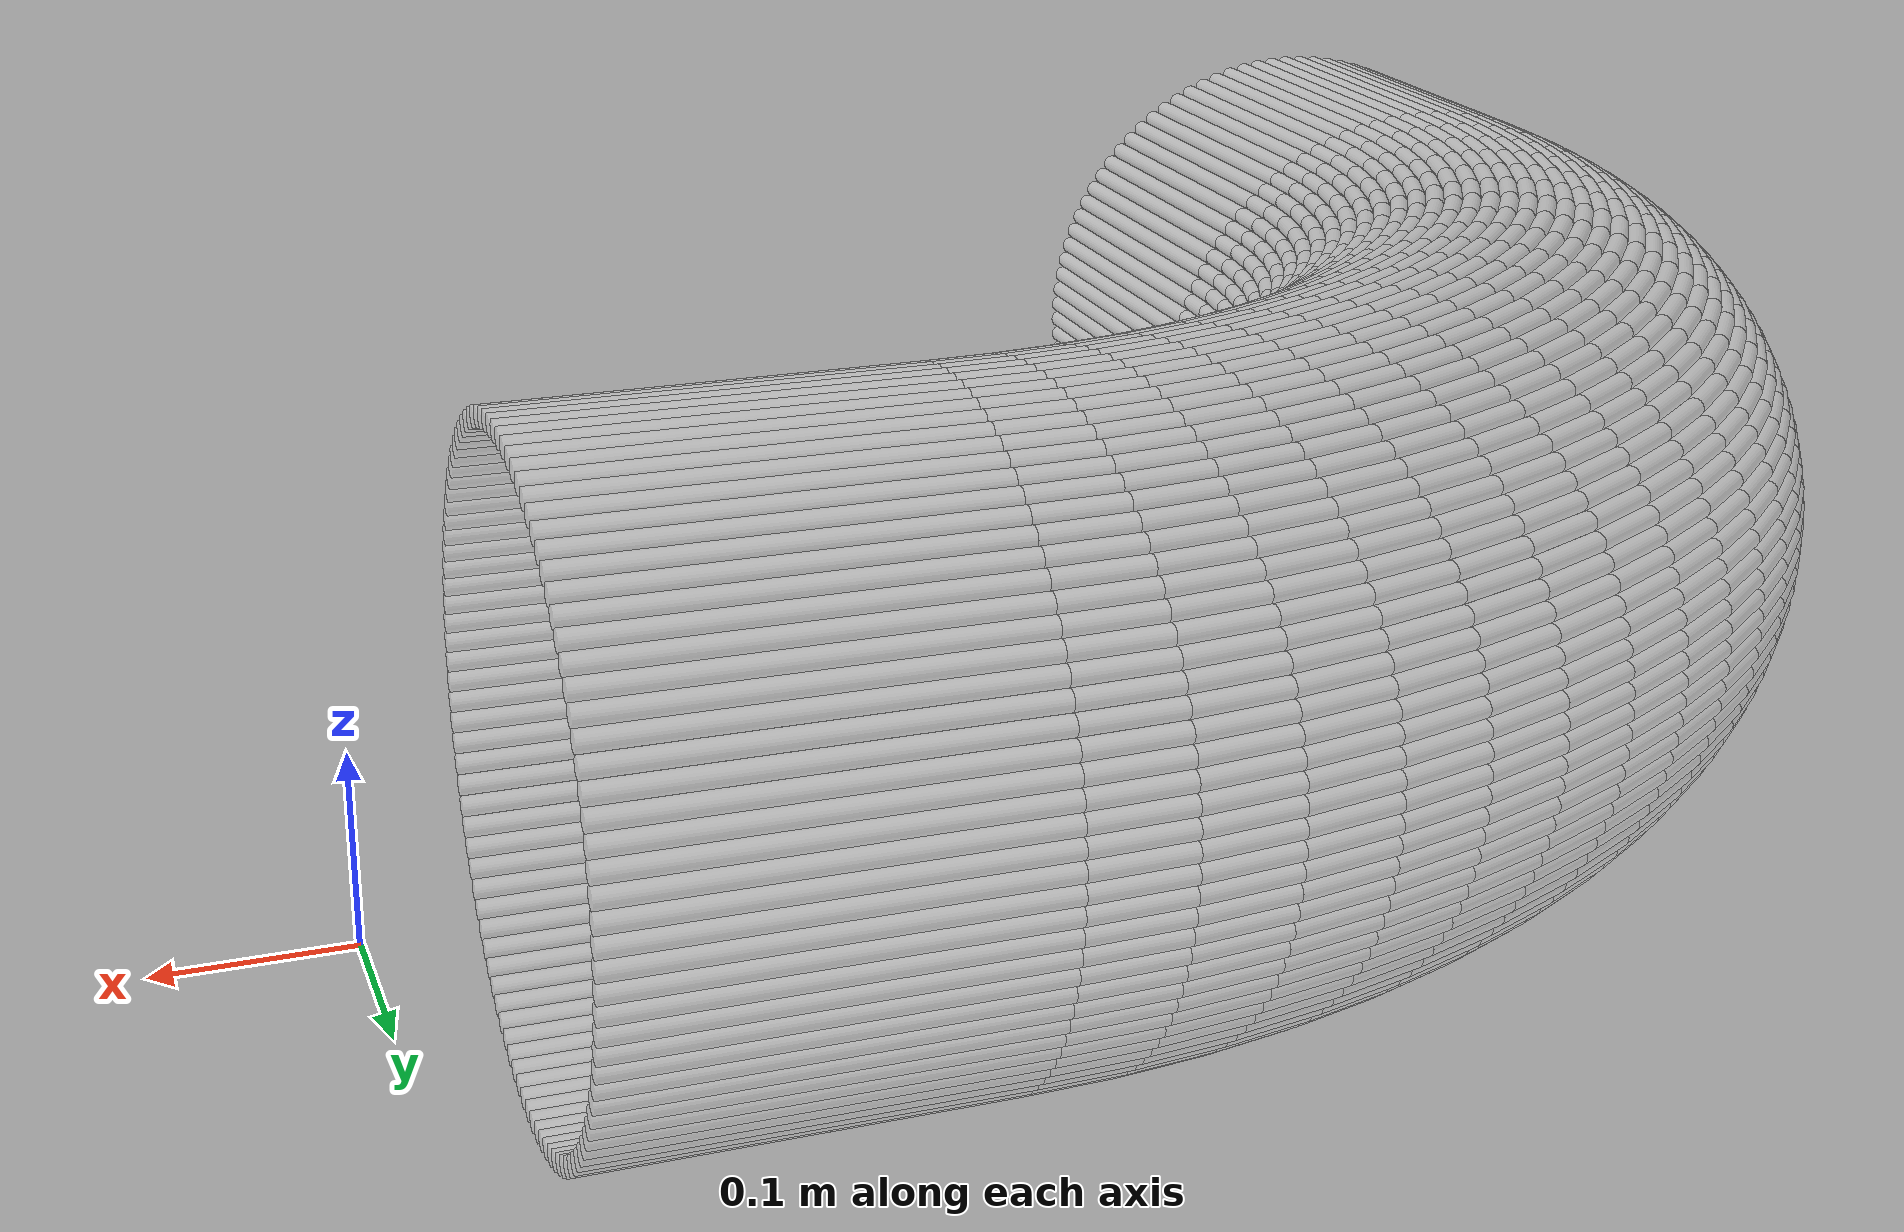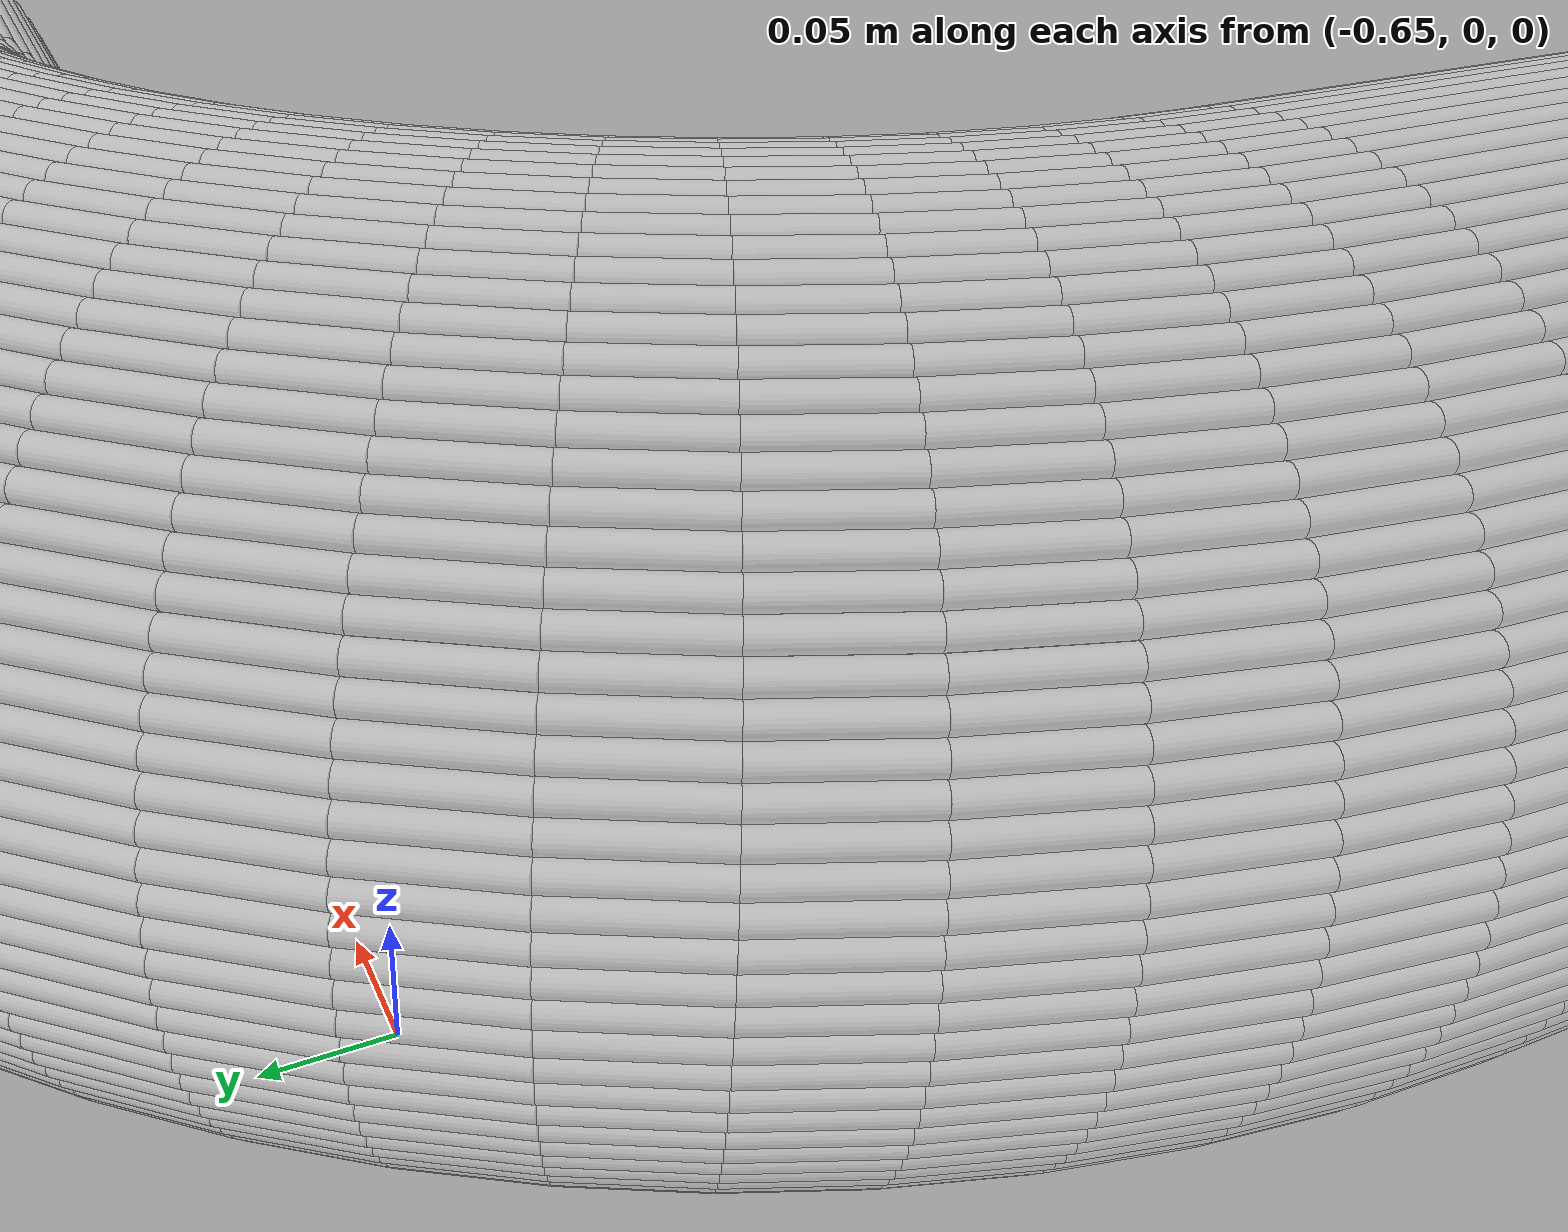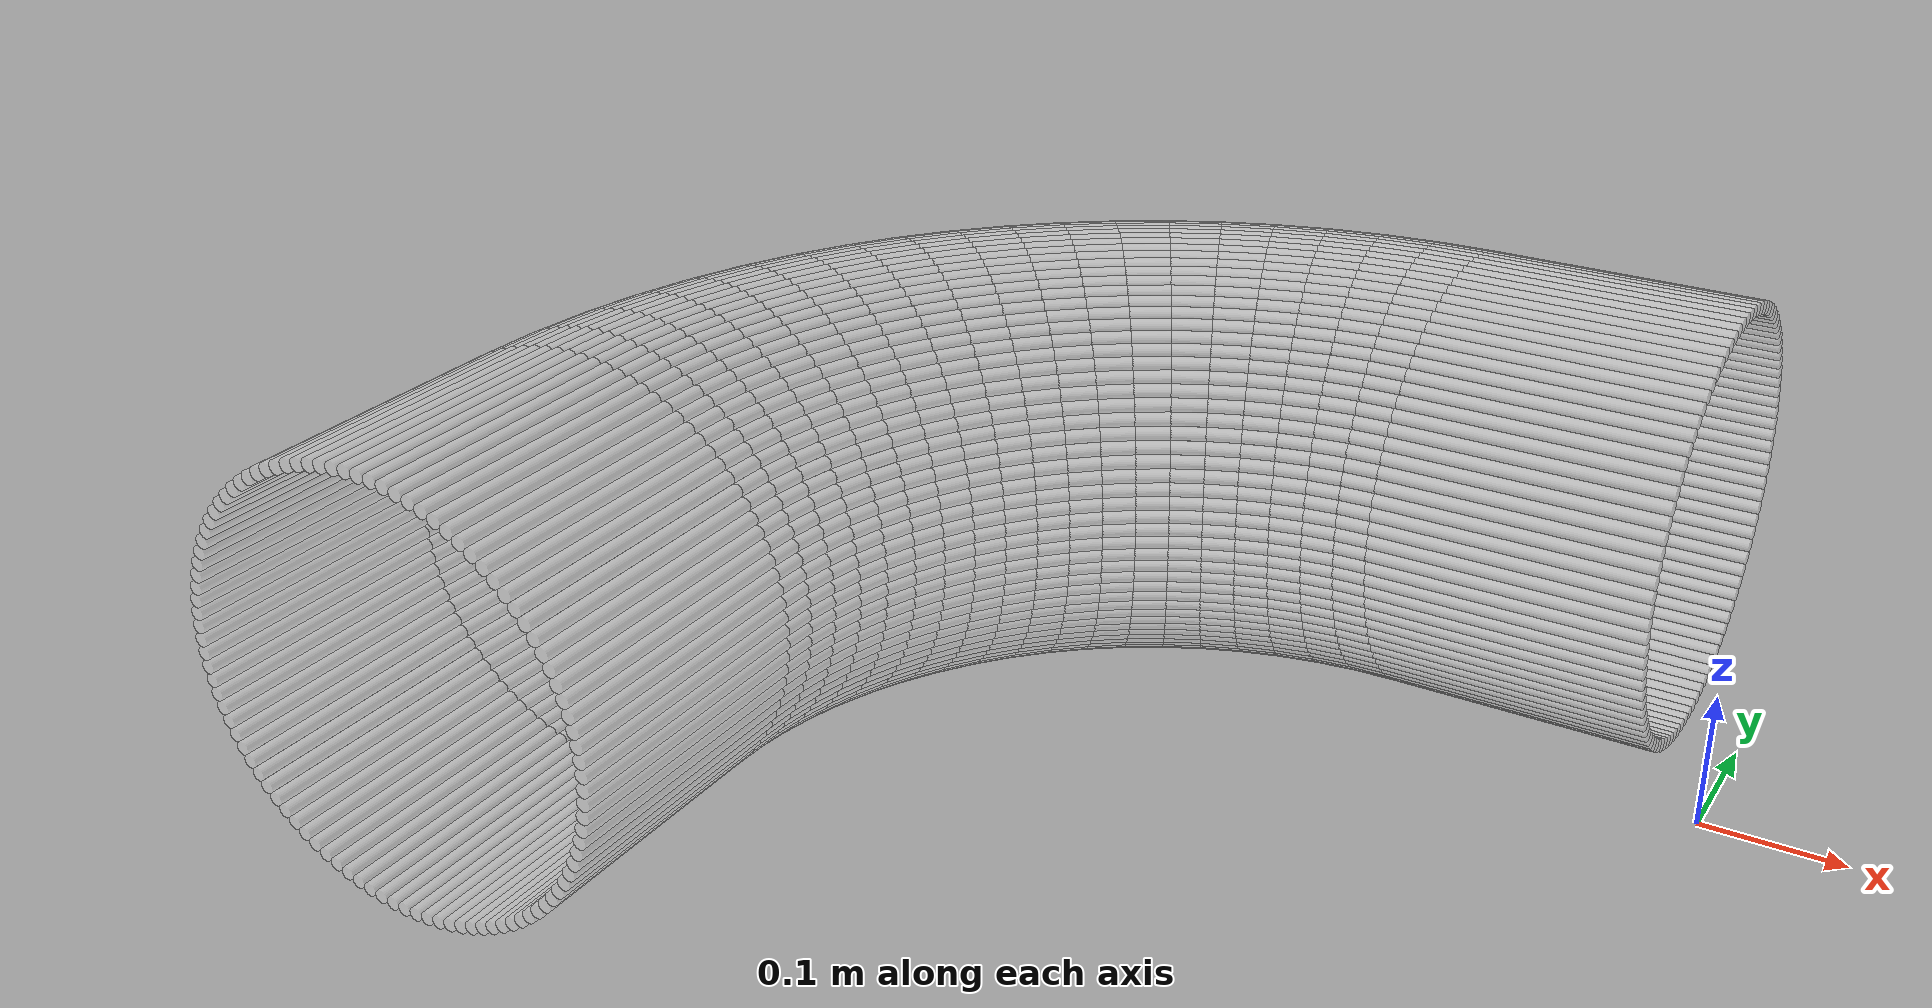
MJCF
<?xml version="1.0" encoding="utf-8"?>
<mujoco>
   <worldbody>
   <body pos="-0.25 -0.29 -0.02" euler="0 0 90">
      <geom euler=" 0 10 0 " fromto="0.61 -0.2 0.16 0.61 0 0.16" rgba="1 1 1 0.35"
            size="0.0050257"
            type="cylinder"/>
      <geom euler=" 0 20 0 " fromto="0.60968 -0.2 0.17005 0.60968 0 0.17005"
            rgba="1 1 1 0.35"
            size="0.0050257"
            type="cylinder"/>
      <geom euler=" 0 30 0 " fromto="0.60874 -0.2 0.18005 0.60874 0 0.18005"
            rgba="1 1 1 0.35"
            size="0.0050257"
            type="cylinder"/>
      <geom euler=" 0 40 0 " fromto="0.60717 -0.2 0.18998 0.60717 0 0.18998"
            rgba="1 1 1 0.35"
            size="0.0050257"
            type="cylinder"/>
      <geom euler=" 0 50 0 " fromto="0.60497 -0.2 0.19979 0.60497 0 0.19979"
            rgba="1 1 1 0.35"
            size="0.0050257"
            type="cylinder"/>
      <geom euler=" 0 60 0 " fromto="0.60217 -0.2 0.20944 0.60217 0 0.20944"
            rgba="1 1 1 0.35"
            size="0.0050257"
            type="cylinder"/>
      <geom euler=" 0 70 0 " fromto="0.59876 -0.2 0.2189 0.59876 0 0.2189"
            rgba="1 1 1 0.35"
            size="0.0050257"
            type="cylinder"/>
      <geom euler=" 0 80 0 " fromto="0.59477 -0.2 0.22812 0.59477 0 0.22812"
            rgba="1 1 1 0.35"
            size="0.0050257"
            type="cylinder"/>
      <geom euler=" 0 90 0 " fromto="0.59021 -0.2 0.23708 0.59021 0 0.23708"
            rgba="1 1 1 0.35"
            size="0.0050257"
            type="cylinder"/>
      <geom euler=" 0 100 0 " fromto="0.58509 -0.2 0.24573 0.58509 0 0.24573"
            rgba="1 1 1 0.35"
            size="0.0050257"
            type="cylinder"/>
      <geom euler=" 0 110 0 " fromto="0.57944 -0.2 0.25405 0.57944 0 0.25405"
            rgba="1 1 1 0.35"
            size="0.0050257"
            type="cylinder"/>
      <geom euler=" 0 120 0 " fromto="0.57328 -0.2 0.26199 0.57328 0 0.26199"
            rgba="1 1 1 0.35"
            size="0.0050257"
            type="cylinder"/>
      <geom euler=" 0 130 0 " fromto="0.56663 -0.2 0.26953 0.56663 0 0.26953"
            rgba="1 1 1 0.35"
            size="0.0050257"
            type="cylinder"/>
      <geom euler=" 0 140 0 " fromto="0.55953 -0.2 0.27663 0.55953 0 0.27663"
            rgba="1 1 1 0.35"
            size="0.0050257"
            type="cylinder"/>
      <geom euler=" 0 150 0 " fromto="0.55199 -0.2 0.28328 0.55199 0 0.28328"
            rgba="1 1 1 0.35"
            size="0.0050257"
            type="cylinder"/>
      <geom euler=" 0 160 0 " fromto="0.54405 -0.2 0.28944 0.54405 0 0.28944"
            rgba="1 1 1 0.35"
            size="0.0050257"
            type="cylinder"/>
      <geom euler=" 0 170 0 " fromto="0.53573 -0.2 0.29509 0.53573 0 0.29509"
            rgba="1 1 1 0.35"
            size="0.0050257"
            type="cylinder"/>
      <geom euler=" 0 180 0 " fromto="0.52708 -0.2 0.30021 0.52708 0 0.30021"
            rgba="1 1 1 0.35"
            size="0.0050257"
            type="cylinder"/>
      <geom euler=" 0 190 0 " fromto="0.51812 -0.2 0.30477 0.51812 0 0.30477"
            rgba="1 1 1 0.35"
            size="0.0050257"
            type="cylinder"/>
      <geom euler=" 0 200 0 " fromto="0.5089 -0.2 0.30876 0.5089 0 0.30876"
            rgba="1 1 1 0.35"
            size="0.0050257"
            type="cylinder"/>
      <geom euler=" 0 210 0 " fromto="0.49944 -0.2 0.31217 0.49944 0 0.31217"
            rgba="1 1 1 0.35"
            size="0.0050257"
            type="cylinder"/>
      <geom euler=" 0 220 0 " fromto="0.48979 -0.2 0.31497 0.48979 0 0.31497"
            rgba="1 1 1 0.35"
            size="0.0050257"
            type="cylinder"/>
      <geom euler=" 0 230 0 " fromto="0.47998 -0.2 0.31717 0.47998 0 0.31717"
            rgba="1 1 1 0.35"
            size="0.0050257"
            type="cylinder"/>
      <geom euler=" 0 240 0 " fromto="0.47005 -0.2 0.31874 0.47005 0 0.31874"
            rgba="1 1 1 0.35"
            size="0.0050257"
            type="cylinder"/>
      <geom euler=" 0 250 0 " fromto="0.46005 -0.2 0.31968 0.46005 0 0.31968"
            rgba="1 1 1 0.35"
            size="0.0050257"
            type="cylinder"/>
      <geom euler=" 0 260 0 " fromto="0.45 -0.2 0.32 0.45 0 0.32" rgba="1 1 1 0.35"
            size="0.0050257"
            type="cylinder"/>
      <geom euler=" 0 270 0 " fromto="0.43995 -0.2 0.31968 0.43995 0 0.31968"
            rgba="1 1 1 0.35"
            size="0.0050257"
            type="cylinder"/>
      <geom euler=" 0 280 0 " fromto="0.42995 -0.2 0.31874 0.42995 0 0.31874"
            rgba="1 1 1 0.35"
            size="0.0050257"
            type="cylinder"/>
      <geom euler=" 0 290 0 " fromto="0.42002 -0.2 0.31717 0.42002 0 0.31717"
            rgba="1 1 1 0.35"
            size="0.0050257"
            type="cylinder"/>
      <geom euler=" 0 300 0 " fromto="0.41021 -0.2 0.31497 0.41021 0 0.31497"
            rgba="1 1 1 0.35"
            size="0.0050257"
            type="cylinder"/>
      <geom euler=" 0 310 0 " fromto="0.40056 -0.2 0.31217 0.40056 0 0.31217"
            rgba="1 1 1 0.35"
            size="0.0050257"
            type="cylinder"/>
      <geom euler=" 0 320 0 " fromto="0.3911 -0.2 0.30876 0.3911 0 0.30876"
            rgba="1 1 1 0.35"
            size="0.0050257"
            type="cylinder"/>
      <geom euler=" 0 330 0 " fromto="0.38188 -0.2 0.30477 0.38188 0 0.30477"
            rgba="1 1 1 0.35"
            size="0.0050257"
            type="cylinder"/>
      <geom euler=" 0 340 0 " fromto="0.37292 -0.2 0.30021 0.37292 0 0.30021"
            rgba="1 1 1 0.35"
            size="0.0050257"
            type="cylinder"/>
      <geom euler=" 0 350 0 " fromto="0.36427 -0.2 0.29509 0.36427 0 0.29509"
            rgba="1 1 1 0.35"
            size="0.0050257"
            type="cylinder"/>
      <geom euler=" 0 360 0 " fromto="0.35595 -0.2 0.28944 0.35595 0 0.28944"
            rgba="1 1 1 0.35"
            size="0.0050257"
            type="cylinder"/>
      <geom euler=" 0 370 0 " fromto="0.34801 -0.2 0.28328 0.34801 0 0.28328"
            rgba="1 1 1 0.35"
            size="0.0050257"
            type="cylinder"/>
      <geom euler=" 0 380 0 " fromto="0.34047 -0.2 0.27663 0.34047 0 0.27663"
            rgba="1 1 1 0.35"
            size="0.0050257"
            type="cylinder"/>
      <geom euler=" 0 390 0 " fromto="0.33337 -0.2 0.26953 0.33337 0 0.26953"
            rgba="1 1 1 0.35"
            size="0.0050257"
            type="cylinder"/>
      <geom euler=" 0 400 0 " fromto="0.32672 -0.2 0.26199 0.32672 0 0.26199"
            rgba="1 1 1 0.35"
            size="0.0050257"
            type="cylinder"/>
      <geom euler=" 0 410 0 " fromto="0.32056 -0.2 0.25405 0.32056 0 0.25405"
            rgba="1 1 1 0.35"
            size="0.0050257"
            type="cylinder"/>
      <geom euler=" 0 420 0 " fromto="0.31491 -0.2 0.24573 0.31491 0 0.24573"
            rgba="1 1 1 0.35"
            size="0.0050257"
            type="cylinder"/>
      <geom euler=" 0 430 0 " fromto="0.30979 -0.2 0.23708 0.30979 0 0.23708"
            rgba="1 1 1 0.35"
            size="0.0050257"
            type="cylinder"/>
      <geom euler=" 0 440 0 " fromto="0.30523 -0.2 0.22812 0.30523 0 0.22812"
            rgba="1 1 1 0.35"
            size="0.0050257"
            type="cylinder"/>
      <geom euler=" 0 450 0 " fromto="0.30124 -0.2 0.2189 0.30124 0 0.2189"
            rgba="1 1 1 0.35"
            size="0.0050257"
            type="cylinder"/>
      <geom euler=" 0 460 0 " fromto="0.29783 -0.2 0.20944 0.29783 0 0.20944"
            rgba="1 1 1 0.35"
            size="0.0050257"
            type="cylinder"/>
      <geom euler=" 0 470 0 " fromto="0.29503 -0.2 0.19979 0.29503 0 0.19979"
            rgba="1 1 1 0.35"
            size="0.0050257"
            type="cylinder"/>
      <geom euler=" 0 480 0 " fromto="0.29283 -0.2 0.18998 0.29283 0 0.18998"
            rgba="1 1 1 0.35"
            size="0.0050257"
            type="cylinder"/>
      <geom euler=" 0 490 0 " fromto="0.29126 -0.2 0.18005 0.29126 0 0.18005"
            rgba="1 1 1 0.35"
            size="0.0050257"
            type="cylinder"/>
      <geom euler=" 0 500 0 " fromto="0.29032 -0.2 0.17005 0.29032 0 0.17005"
            rgba="1 1 1 0.35"
            size="0.0050257"
            type="cylinder"/>
      <geom euler=" 0 510 0 " fromto="0.29 -0.2 0.16 0.29 0 0.16" rgba="1 1 1 0.35"
            size="0.0050257"
            type="cylinder"/>
      <geom euler=" 0 520 0 " fromto="0.29032 -0.2 0.14995 0.29032 0 0.14995"
            rgba="1 1 1 0.35"
            size="0.0050257"
            type="cylinder"/>
      <geom euler=" 0 530 0 " fromto="0.29126 -0.2 0.13995 0.29126 0 0.13995"
            rgba="1 1 1 0.35"
            size="0.0050257"
            type="cylinder"/>
      <geom euler=" 0 540 0 " fromto="0.29283 -0.2 0.13002 0.29283 0 0.13002"
            rgba="1 1 1 0.35"
            size="0.0050257"
            type="cylinder"/>
      <geom euler=" 0 550 0 " fromto="0.29503 -0.2 0.12021 0.29503 0 0.12021"
            rgba="1 1 1 0.35"
            size="0.0050257"
            type="cylinder"/>
      <geom euler=" 0 560 0 " fromto="0.29783 -0.2 0.11056 0.29783 0 0.11056"
            rgba="1 1 1 0.35"
            size="0.0050257"
            type="cylinder"/>
      <geom euler=" 0 570 0 " fromto="0.30124 -0.2 0.1011 0.30124 0 0.1011"
            rgba="1 1 1 0.35"
            size="0.0050257"
            type="cylinder"/>
      <geom euler=" 0 580 0 " fromto="0.30523 -0.2 0.091875 0.30523 0 0.091875"
            rgba="1 1 1 0.35"
            size="0.0050257"
            type="cylinder"/>
      <geom euler=" 0 590 0 " fromto="0.30979 -0.2 0.082919 0.30979 0 0.082919"
            rgba="1 1 1 0.35"
            size="0.0050257"
            type="cylinder"/>
      <geom euler=" 0 600 0 " fromto="0.31491 -0.2 0.074268 0.31491 0 0.074268"
            rgba="1 1 1 0.35"
            size="0.0050257"
            type="cylinder"/>
      <geom euler=" 0 610 0 " fromto="0.32056 -0.2 0.065954 0.32056 0 0.065954"
            rgba="1 1 1 0.35"
            size="0.0050257"
            type="cylinder"/>
      <geom euler=" 0 620 0 " fromto="0.32672 -0.2 0.058012 0.32672 0 0.058012"
            rgba="1 1 1 0.35"
            size="0.0050257"
            type="cylinder"/>
      <geom euler=" 0 630 0 " fromto="0.33337 -0.2 0.050472 0.33337 0 0.050472"
            rgba="1 1 1 0.35"
            size="0.0050257"
            type="cylinder"/>
      <geom euler=" 0 640 0 " fromto="0.34047 -0.2 0.043365 0.34047 0 0.043365"
            rgba="1 1 1 0.35"
            size="0.0050257"
            type="cylinder"/>
      <geom euler=" 0 650 0 " fromto="0.34801 -0.2 0.036718 0.34801 0 0.036718"
            rgba="1 1 1 0.35"
            size="0.0050257"
            type="cylinder"/>
      <geom euler=" 0 660 0 " fromto="0.35595 -0.2 0.030557 0.35595 0 0.030557"
            rgba="1 1 1 0.35"
            size="0.0050257"
            type="cylinder"/>
      <geom euler=" 0 670 0 " fromto="0.36427 -0.2 0.024908 0.36427 0 0.024908"
            rgba="1 1 1 0.35"
            size="0.0050257"
            type="cylinder"/>
      <geom euler=" 0 680 0 " fromto="0.37292 -0.2 0.019791 0.37292 0 0.019791"
            rgba="1 1 1 0.35"
            size="0.0050257"
            type="cylinder"/>
      <geom euler=" 0 690 0 " fromto="0.38188 -0.2 0.015228 0.38188 0 0.015228"
            rgba="1 1 1 0.35"
            size="0.0050257"
            type="cylinder"/>
      <geom euler=" 0 700 0 " fromto="0.3911 -0.2 0.011236 0.3911 0 0.011236"
            rgba="1 1 1 0.35"
            size="0.0050257"
            type="cylinder"/>
      <geom euler=" 0 710 0 " fromto="0.40056 -0.2 0.007831 0.40056 0 0.007831"
            rgba="1 1 1 0.35"
            size="0.0050257"
            type="cylinder"/>
      <geom euler=" 0 720 0 " fromto="0.41021 -0.2 0.0050267 0.41021 0 0.0050267"
            rgba="1 1 1 0.35"
            size="0.0050257"
            type="cylinder"/>
      <geom euler=" 0 730 0 " fromto="0.42002 -0.2 0.002834 0.42002 0 0.002834"
            rgba="1 1 1 0.35"
            size="0.0050257"
            type="cylinder"/>
      <geom euler=" 0 740 0 " fromto="0.42995 -0.2 0.0012616 0.42995 0 0.0012616"
            rgba="1 1 1 0.35"
            size="0.0050257"
            type="cylinder"/>
      <geom euler=" 0 750 0 " fromto="0.43995 -0.2 0.00031572 0.43995 0 0.00031572"
            rgba="1 1 1 0.35"
            size="0.0050257"
            type="cylinder"/>
      <geom euler=" 0 760 0 " fromto="0.45 -0.2 0 0.45 0 0" rgba="1 1 1 0.35"
            size="0.0050257"
            type="cylinder"/>
      <geom euler=" 0 770 0 " fromto="0.46005 -0.2 0.00031572 0.46005 0 0.00031572"
            rgba="1 1 1 0.35"
            size="0.0050257"
            type="cylinder"/>
      <geom euler=" 0 780 0 " fromto="0.47005 -0.2 0.0012616 0.47005 0 0.0012616"
            rgba="1 1 1 0.35"
            size="0.0050257"
            type="cylinder"/>
      <geom euler=" 0 790 0 " fromto="0.47998 -0.2 0.002834 0.47998 0 0.002834"
            rgba="1 1 1 0.35"
            size="0.0050257"
            type="cylinder"/>
      <geom euler=" 0 800 0 " fromto="0.48979 -0.2 0.0050267 0.48979 0 0.0050267"
            rgba="1 1 1 0.35"
            size="0.0050257"
            type="cylinder"/>
      <geom euler=" 0 810 0 " fromto="0.49944 -0.2 0.007831 0.49944 0 0.007831"
            rgba="1 1 1 0.35"
            size="0.0050257"
            type="cylinder"/>
      <geom euler=" 0 820 0 " fromto="0.5089 -0.2 0.011236 0.5089 0 0.011236"
            rgba="1 1 1 0.35"
            size="0.0050257"
            type="cylinder"/>
      <geom euler=" 0 830 0 " fromto="0.51812 -0.2 0.015228 0.51812 0 0.015228"
            rgba="1 1 1 0.35"
            size="0.0050257"
            type="cylinder"/>
      <geom euler=" 0 840 0 " fromto="0.52708 -0.2 0.019791 0.52708 0 0.019791"
            rgba="1 1 1 0.35"
            size="0.0050257"
            type="cylinder"/>
      <geom euler=" 0 850 0 " fromto="0.53573 -0.2 0.024908 0.53573 0 0.024908"
            rgba="1 1 1 0.35"
            size="0.0050257"
            type="cylinder"/>
      <geom euler=" 0 860 0 " fromto="0.54405 -0.2 0.030557 0.54405 0 0.030557"
            rgba="1 1 1 0.35"
            size="0.0050257"
            type="cylinder"/>
      <geom euler=" 0 870 0 " fromto="0.55199 -0.2 0.036718 0.55199 0 0.036718"
            rgba="1 1 1 0.35"
            size="0.0050257"
            type="cylinder"/>
      <geom euler=" 0 880 0 " fromto="0.55953 -0.2 0.043365 0.55953 0 0.043365"
            rgba="1 1 1 0.35"
            size="0.0050257"
            type="cylinder"/>
      <geom euler=" 0 890 0 " fromto="0.56663 -0.2 0.050472 0.56663 0 0.050472"
            rgba="1 1 1 0.35"
            size="0.0050257"
            type="cylinder"/>
      <geom euler=" 0 900 0 " fromto="0.57328 -0.2 0.058012 0.57328 0 0.058012"
            rgba="1 1 1 0.35"
            size="0.0050257"
            type="cylinder"/>
      <geom euler=" 0 910 0 " fromto="0.57944 -0.2 0.065954 0.57944 0 0.065954"
            rgba="1 1 1 0.35"
            size="0.0050257"
            type="cylinder"/>
      <geom euler=" 0 920 0 " fromto="0.58509 -0.2 0.074268 0.58509 0 0.074268"
            rgba="1 1 1 0.35"
            size="0.0050257"
            type="cylinder"/>
      <geom euler=" 0 930 0 " fromto="0.59021 -0.2 0.082919 0.59021 0 0.082919"
            rgba="1 1 1 0.35"
            size="0.0050257"
            type="cylinder"/>
      <geom euler=" 0 940 0 " fromto="0.59477 -0.2 0.091875 0.59477 0 0.091875"
            rgba="1 1 1 0.35"
            size="0.0050257"
            type="cylinder"/>
      <geom euler=" 0 950 0 " fromto="0.59876 -0.2 0.1011 0.59876 0 0.1011"
            rgba="1 1 1 0.35"
            size="0.0050257"
            type="cylinder"/>
      <geom euler=" 0 960 0 " fromto="0.60217 -0.2 0.11056 0.60217 0 0.11056"
            rgba="1 1 1 0.35"
            size="0.0050257"
            type="cylinder"/>
      <geom euler=" 0 970 0 " fromto="0.60497 -0.2 0.12021 0.60497 0 0.12021"
            rgba="1 1 1 0.35"
            size="0.0050257"
            type="cylinder"/>
      <geom euler=" 0 980 0 " fromto="0.60717 -0.2 0.13002 0.60717 0 0.13002"
            rgba="1 1 1 0.35"
            size="0.0050257"
            type="cylinder"/>
      <geom euler=" 0 990 0 " fromto="0.60874 -0.2 0.13995 0.60874 0 0.13995"
            rgba="1 1 1 0.35"
            size="0.0050257"
            type="cylinder"/>
      <geom euler=" 0 1000 0 " fromto="0.60968 -0.2 0.14995 0.60968 0 0.14995"
            rgba="1 1 1 0.35"
            size="0.0050257"
            type="cylinder"/>
      <geom euler=" 0 10 0 " fromto="0.61 0 0.16 0.60792 0.050373 0.16" rgba="1 1 1 0.35"
            size="0.0050257"
            type="cylinder"/>
      <geom euler=" 0 20 0 " fromto="0.60968 0 0.17005 0.6076 0.050347 0.17005"
            rgba="1 1 1 0.35"
            size="0.0050257"
            type="cylinder"/>
      <geom euler=" 0 30 0 " fromto="0.60874 0 0.18005 0.60666 0.050269 0.18005"
            rgba="1 1 1 0.35"
            size="0.0050257"
            type="cylinder"/>
      <geom euler=" 0 40 0 " fromto="0.60717 0 0.18998 0.60509 0.050139 0.18998"
            rgba="1 1 1 0.35"
            size="0.0050257"
            type="cylinder"/>
      <geom euler=" 0 50 0 " fromto="0.60497 0 0.19979 0.60291 0.049958 0.19979"
            rgba="1 1 1 0.35"
            size="0.0050257"
            type="cylinder"/>
      <geom euler=" 0 60 0 " fromto="0.60217 0 0.20944 0.60011 0.049727 0.20944"
            rgba="1 1 1 0.35"
            size="0.0050257"
            type="cylinder"/>
      <geom euler=" 0 70 0 " fromto="0.59876 0 0.2189 0.59672 0.049446 0.2189"
            rgba="1 1 1 0.35"
            size="0.0050257"
            type="cylinder"/>
      <geom euler=" 0 80 0 " fromto="0.59477 0 0.22812 0.59274 0.049116 0.22812"
            rgba="1 1 1 0.35"
            size="0.0050257"
            type="cylinder"/>
      <geom euler=" 0 90 0 " fromto="0.59021 0 0.23708 0.58819 0.048739 0.23708"
            rgba="1 1 1 0.35"
            size="0.0050257"
            type="cylinder"/>
      <geom euler=" 0 100 0 " fromto="0.58509 0 0.24573 0.58309 0.048317 0.24573"
            rgba="1 1 1 0.35"
            size="0.0050257"
            type="cylinder"/>
      <geom euler=" 0 110 0 " fromto="0.57944 0 0.25405 0.57746 0.04785 0.25405"
            rgba="1 1 1 0.35"
            size="0.0050257"
            type="cylinder"/>
      <geom euler=" 0 120 0 " fromto="0.57328 0 0.26199 0.57132 0.047341 0.26199"
            rgba="1 1 1 0.35"
            size="0.0050257"
            type="cylinder"/>
      <geom euler=" 0 130 0 " fromto="0.56663 0 0.26953 0.5647 0.046792 0.26953"
            rgba="1 1 1 0.35"
            size="0.0050257"
            type="cylinder"/>
      <geom euler=" 0 140 0 " fromto="0.55953 0 0.27663 0.55762 0.046205 0.27663"
            rgba="1 1 1 0.35"
            size="0.0050257"
            type="cylinder"/>
      <geom euler=" 0 150 0 " fromto="0.55199 0 0.28328 0.5501 0.045583 0.28328"
            rgba="1 1 1 0.35"
            size="0.0050257"
            type="cylinder"/>
      <geom euler=" 0 160 0 " fromto="0.54405 0 0.28944 0.54219 0.044927 0.28944"
            rgba="1 1 1 0.35"
            size="0.0050257"
            type="cylinder"/>
      <geom euler=" 0 170 0 " fromto="0.53573 0 0.29509 0.5339 0.04424 0.29509"
            rgba="1 1 1 0.35"
            size="0.0050257"
            type="cylinder"/>
      <geom euler=" 0 180 0 " fromto="0.52708 0 0.30021 0.52528 0.043526 0.30021"
            rgba="1 1 1 0.35"
            size="0.0050257"
            type="cylinder"/>
      <geom euler=" 0 190 0 " fromto="0.51812 0 0.30477 0.51636 0.042786 0.30477"
            rgba="1 1 1 0.35"
            size="0.0050257"
            type="cylinder"/>
      <geom euler=" 0 200 0 " fromto="0.5089 0 0.30876 0.50716 0.042025 0.30876"
            rgba="1 1 1 0.35"
            size="0.0050257"
            type="cylinder"/>
      <geom euler=" 0 210 0 " fromto="0.49944 0 0.31217 0.49774 0.041244 0.31217"
            rgba="1 1 1 0.35"
            size="0.0050257"
            type="cylinder"/>
      <geom euler=" 0 220 0 " fromto="0.48979 0 0.31497 0.48812 0.040447 0.31497"
            rgba="1 1 1 0.35"
            size="0.0050257"
            type="cylinder"/>
      <geom euler=" 0 230 0 " fromto="0.47998 0 0.31717 0.47834 0.039637 0.31717"
            rgba="1 1 1 0.35"
            size="0.0050257"
            type="cylinder"/>
      <geom euler=" 0 240 0 " fromto="0.47005 0 0.31874 0.46845 0.038817 0.31874"
            rgba="1 1 1 0.35"
            size="0.0050257"
            type="cylinder"/>
      <geom euler=" 0 250 0 " fromto="0.46005 0 0.31968 0.45848 0.03799 0.31968"
            rgba="1 1 1 0.35"
            size="0.0050257"
            type="cylinder"/>
      <geom euler=" 0 260 0 " fromto="0.45 0 0.32 0.44846 0.037161 0.32" rgba="1 1 1 0.35"
            size="0.0050257"
            type="cylinder"/>
      <geom euler=" 0 270 0 " fromto="0.43995 0 0.31968 0.43845 0.036331 0.31968"
            rgba="1 1 1 0.35"
            size="0.0050257"
            type="cylinder"/>
      <geom euler=" 0 280 0 " fromto="0.42995 0 0.31874 0.42848 0.035505 0.31874"
            rgba="1 1 1 0.35"
            size="0.0050257"
            type="cylinder"/>
      <geom euler=" 0 290 0 " fromto="0.42002 0 0.31717 0.41858 0.034685 0.31717"
            rgba="1 1 1 0.35"
            size="0.0050257"
            type="cylinder"/>
      <geom euler=" 0 300 0 " fromto="0.41021 0 0.31497 0.40881 0.033875 0.31497"
            rgba="1 1 1 0.35"
            size="0.0050257"
            type="cylinder"/>
      <geom euler=" 0 310 0 " fromto="0.40056 0 0.31217 0.39919 0.033078 0.31217"
            rgba="1 1 1 0.35"
            size="0.0050257"
            type="cylinder"/>
      <geom euler=" 0 320 0 " fromto="0.3911 0 0.30876 0.38976 0.032297 0.30876"
            rgba="1 1 1 0.35"
            size="0.0050257"
            type="cylinder"/>
      <geom euler=" 0 330 0 " fromto="0.38188 0 0.30477 0.38057 0.031535 0.30477"
            rgba="1 1 1 0.35"
            size="0.0050257"
            type="cylinder"/>
      <geom euler=" 0 340 0 " fromto="0.37292 0 0.30021 0.37165 0.030795 0.30021"
            rgba="1 1 1 0.35"
            size="0.0050257"
            type="cylinder"/>
      <geom euler=" 0 350 0 " fromto="0.36427 0 0.29509 0.36302 0.030081 0.29509"
            rgba="1 1 1 0.35"
            size="0.0050257"
            type="cylinder"/>
      <geom euler=" 0 360 0 " fromto="0.35595 0 0.28944 0.35474 0.029394 0.28944"
            rgba="1 1 1 0.35"
            size="0.0050257"
            type="cylinder"/>
      <geom euler=" 0 370 0 " fromto="0.34801 0 0.28328 0.34682 0.028739 0.28328"
            rgba="1 1 1 0.35"
            size="0.0050257"
            type="cylinder"/>
      <geom euler=" 0 380 0 " fromto="0.34047 0 0.27663 0.33931 0.028116 0.27663"
            rgba="1 1 1 0.35"
            size="0.0050257"
            type="cylinder"/>
      <geom euler=" 0 390 0 " fromto="0.33337 0 0.26953 0.33223 0.027529 0.26953"
            rgba="1 1 1 0.35"
            size="0.0050257"
            type="cylinder"/>
      <geom euler=" 0 400 0 " fromto="0.32672 0 0.26199 0.3256 0.02698 0.26199"
            rgba="1 1 1 0.35"
            size="0.0050257"
            type="cylinder"/>
      <geom euler=" 0 410 0 " fromto="0.32056 0 0.25405 0.31946 0.026471 0.25405"
            rgba="1 1 1 0.35"
            size="0.0050257"
            type="cylinder"/>
      <geom euler=" 0 420 0 " fromto="0.31491 0 0.24573 0.31383 0.026005 0.24573"
            rgba="1 1 1 0.35"
            size="0.0050257"
            type="cylinder"/>
      <geom euler=" 0 430 0 " fromto="0.30979 0 0.23708 0.30873 0.025582 0.23708"
            rgba="1 1 1 0.35"
            size="0.0050257"
            type="cylinder"/>
      <geom euler=" 0 440 0 " fromto="0.30523 0 0.22812 0.30419 0.025206 0.22812"
            rgba="1 1 1 0.35"
            size="0.0050257"
            type="cylinder"/>
      <geom euler=" 0 450 0 " fromto="0.30124 0 0.2189 0.30021 0.024876 0.2189"
            rgba="1 1 1 0.35"
            size="0.0050257"
            type="cylinder"/>
      <geom euler=" 0 460 0 " fromto="0.29783 0 0.20944 0.29681 0.024595 0.20944"
            rgba="1 1 1 0.35"
            size="0.0050257"
            type="cylinder"/>
      <geom euler=" 0 470 0 " fromto="0.29503 0 0.19979 0.29402 0.024363 0.19979"
            rgba="1 1 1 0.35"
            size="0.0050257"
            type="cylinder"/>
      <geom euler=" 0 480 0 " fromto="0.29283 0 0.18998 0.29183 0.024182 0.18998"
            rgba="1 1 1 0.35"
            size="0.0050257"
            type="cylinder"/>
      <geom euler=" 0 490 0 " fromto="0.29126 0 0.18005 0.29027 0.024052 0.18005"
            rgba="1 1 1 0.35"
            size="0.0050257"
            type="cylinder"/>
      <geom euler=" 0 500 0 " fromto="0.29032 0 0.17005 0.28932 0.023974 0.17005"
            rgba="1 1 1 0.35"
            size="0.0050257"
            type="cylinder"/>
      <geom euler=" 0 510 0 " fromto="0.29 0 0.16 0.28901 0.023948 0.16" rgba="1 1 1 0.35"
            size="0.0050257"
            type="cylinder"/>
      <geom euler=" 0 520 0 " fromto="0.29032 0 0.14995 0.28932 0.023974 0.14995"
            rgba="1 1 1 0.35"
            size="0.0050257"
            type="cylinder"/>
      <geom euler=" 0 530 0 " fromto="0.29126 0 0.13995 0.29027 0.024052 0.13995"
            rgba="1 1 1 0.35"
            size="0.0050257"
            type="cylinder"/>
      <geom euler=" 0 540 0 " fromto="0.29283 0 0.13002 0.29183 0.024182 0.13002"
            rgba="1 1 1 0.35"
            size="0.0050257"
            type="cylinder"/>
      <geom euler=" 0 550 0 " fromto="0.29503 0 0.12021 0.29402 0.024363 0.12021"
            rgba="1 1 1 0.35"
            size="0.0050257"
            type="cylinder"/>
      <geom euler=" 0 560 0 " fromto="0.29783 0 0.11056 0.29681 0.024595 0.11056"
            rgba="1 1 1 0.35"
            size="0.0050257"
            type="cylinder"/>
      <geom euler=" 0 570 0 " fromto="0.30124 0 0.1011 0.30021 0.024876 0.1011"
            rgba="1 1 1 0.35"
            size="0.0050257"
            type="cylinder"/>
      <geom euler=" 0 580 0 " fromto="0.30523 0 0.091875 0.30419 0.025206 0.091875"
            rgba="1 1 1 0.35"
            size="0.0050257"
            type="cylinder"/>
      <geom euler=" 0 590 0 " fromto="0.30979 0 0.082919 0.30873 0.025582 0.082919"
            rgba="1 1 1 0.35"
            size="0.0050257"
            type="cylinder"/>
      <geom euler=" 0 600 0 " fromto="0.31491 0 0.074268 0.31383 0.026005 0.074268"
            rgba="1 1 1 0.35"
            size="0.0050257"
            type="cylinder"/>
      <geom euler=" 0 610 0 " fromto="0.32056 0 0.065954 0.31946 0.026471 0.065954"
            rgba="1 1 1 0.35"
            size="0.0050257"
            type="cylinder"/>
      <geom euler=" 0 620 0 " fromto="0.32672 0 0.058012 0.3256 0.02698 0.058012"
            rgba="1 1 1 0.35"
            size="0.0050257"
            type="cylinder"/>
      <geom euler=" 0 630 0 " fromto="0.33337 0 0.050472 0.33223 0.027529 0.050472"
            rgba="1 1 1 0.35"
            size="0.0050257"
            type="cylinder"/>
      <geom euler=" 0 640 0 " fromto="0.34047 0 0.043365 0.33931 0.028116 0.043365"
            rgba="1 1 1 0.35"
            size="0.0050257"
            type="cylinder"/>
      <geom euler=" 0 650 0 " fromto="0.34801 0 0.036718 0.34682 0.028739 0.036718"
            rgba="1 1 1 0.35"
            size="0.0050257"
            type="cylinder"/>
      <geom euler=" 0 660 0 " fromto="0.35595 0 0.030557 0.35474 0.029394 0.030557"
            rgba="1 1 1 0.35"
            size="0.0050257"
            type="cylinder"/>
      <geom euler=" 0 670 0 " fromto="0.36427 0 0.024908 0.36302 0.030081 0.024908"
            rgba="1 1 1 0.35"
            size="0.0050257"
            type="cylinder"/>
      <geom euler=" 0 680 0 " fromto="0.37292 0 0.019791 0.37165 0.030795 0.019791"
            rgba="1 1 1 0.35"
            size="0.0050257"
            type="cylinder"/>
      <geom euler=" 0 690 0 " fromto="0.38188 0 0.015228 0.38057 0.031535 0.015228"
            rgba="1 1 1 0.35"
            size="0.0050257"
            type="cylinder"/>
      <geom euler=" 0 700 0 " fromto="0.3911 0 0.011236 0.38976 0.032297 0.011236"
            rgba="1 1 1 0.35"
            size="0.0050257"
            type="cylinder"/>
      <geom euler=" 0 710 0 " fromto="0.40056 0 0.007831 0.39919 0.033078 0.007831"
            rgba="1 1 1 0.35"
            size="0.0050257"
            type="cylinder"/>
      <geom euler=" 0 720 0 " fromto="0.41021 0 0.0050267 0.40881 0.033875 0.0050267"
            rgba="1 1 1 0.35"
            size="0.0050257"
            type="cylinder"/>
      <geom euler=" 0 730 0 " fromto="0.42002 0 0.002834 0.41858 0.034685 0.002834"
            rgba="1 1 1 0.35"
            size="0.0050257"
            type="cylinder"/>
      <geom euler=" 0 740 0 " fromto="0.42995 0 0.0012616 0.42848 0.035505 0.0012616"
            rgba="1 1 1 0.35"
            size="0.0050257"
            type="cylinder"/>
      <geom euler=" 0 750 0 " fromto="0.43995 0 0.00031572 0.43845 0.036331 0.00031572"
            rgba="1 1 1 0.35"
            size="0.0050257"
            type="cylinder"/>
      <geom euler=" 0 760 0 " fromto="0.45 0 0 0.44846 0.037161 0" rgba="1 1 1 0.35"
            size="0.0050257"
            type="cylinder"/>
      <geom euler=" 0 770 0 " fromto="0.46005 0 0.00031572 0.45848 0.03799 0.00031572"
            rgba="1 1 1 0.35"
            size="0.0050257"
            type="cylinder"/>
      <geom euler=" 0 780 0 " fromto="0.47005 0 0.0012616 0.46845 0.038817 0.0012616"
            rgba="1 1 1 0.35"
            size="0.0050257"
            type="cylinder"/>
      <geom euler=" 0 790 0 " fromto="0.47998 0 0.002834 0.47834 0.039637 0.002834"
            rgba="1 1 1 0.35"
            size="0.0050257"
            type="cylinder"/>
      <geom euler=" 0 800 0 " fromto="0.48979 0 0.0050267 0.48812 0.040447 0.0050267"
            rgba="1 1 1 0.35"
            size="0.0050257"
            type="cylinder"/>
      <geom euler=" 0 810 0 " fromto="0.49944 0 0.007831 0.49774 0.041244 0.007831"
            rgba="1 1 1 0.35"
            size="0.0050257"
            type="cylinder"/>
      <geom euler=" 0 820 0 " fromto="0.5089 0 0.011236 0.50716 0.042025 0.011236"
            rgba="1 1 1 0.35"
            size="0.0050257"
            type="cylinder"/>
      <geom euler=" 0 830 0 " fromto="0.51812 0 0.015228 0.51636 0.042786 0.015228"
            rgba="1 1 1 0.35"
            size="0.0050257"
            type="cylinder"/>
      <geom euler=" 0 840 0 " fromto="0.52708 0 0.019791 0.52528 0.043526 0.019791"
            rgba="1 1 1 0.35"
            size="0.0050257"
            type="cylinder"/>
      <geom euler=" 0 850 0 " fromto="0.53573 0 0.024908 0.5339 0.04424 0.024908"
            rgba="1 1 1 0.35"
            size="0.0050257"
            type="cylinder"/>
      <geom euler=" 0 860 0 " fromto="0.54405 0 0.030557 0.54219 0.044927 0.030557"
            rgba="1 1 1 0.35"
            size="0.0050257"
            type="cylinder"/>
      <geom euler=" 0 870 0 " fromto="0.55199 0 0.036718 0.5501 0.045583 0.036718"
            rgba="1 1 1 0.35"
            size="0.0050257"
            type="cylinder"/>
      <geom euler=" 0 880 0 " fromto="0.55953 0 0.043365 0.55762 0.046205 0.043365"
            rgba="1 1 1 0.35"
            size="0.0050257"
            type="cylinder"/>
      <geom euler=" 0 890 0 " fromto="0.56663 0 0.050472 0.5647 0.046792 0.050472"
            rgba="1 1 1 0.35"
            size="0.0050257"
            type="cylinder"/>
      <geom euler=" 0 900 0 " fromto="0.57328 0 0.058012 0.57132 0.047341 0.058012"
            rgba="1 1 1 0.35"
            size="0.0050257"
            type="cylinder"/>
      <geom euler=" 0 910 0 " fromto="0.57944 0 0.065954 0.57746 0.04785 0.065954"
            rgba="1 1 1 0.35"
            size="0.0050257"
            type="cylinder"/>
      <geom euler=" 0 920 0 " fromto="0.58509 0 0.074268 0.58309 0.048317 0.074268"
            rgba="1 1 1 0.35"
            size="0.0050257"
            type="cylinder"/>
      <geom euler=" 0 930 0 " fromto="0.59021 0 0.082919 0.58819 0.048739 0.082919"
            rgba="1 1 1 0.35"
            size="0.0050257"
            type="cylinder"/>
      <geom euler=" 0 940 0 " fromto="0.59477 0 0.091875 0.59274 0.049116 0.091875"
            rgba="1 1 1 0.35"
            size="0.0050257"
            type="cylinder"/>
      <geom euler=" 0 950 0 " fromto="0.59876 0 0.1011 0.59672 0.049446 0.1011"
            rgba="1 1 1 0.35"
            size="0.0050257"
            type="cylinder"/>
      <geom euler=" 0 960 0 " fromto="0.60217 0 0.11056 0.60011 0.049727 0.11056"
            rgba="1 1 1 0.35"
            size="0.0050257"
            type="cylinder"/>
      <geom euler=" 0 970 0 " fromto="0.60497 0 0.12021 0.60291 0.049958 0.12021"
            rgba="1 1 1 0.35"
            size="0.0050257"
            type="cylinder"/>
      <geom euler=" 0 980 0 " fromto="0.60717 0 0.13002 0.60509 0.050139 0.13002"
            rgba="1 1 1 0.35"
            size="0.0050257"
            type="cylinder"/>
      <geom euler=" 0 990 0 " fromto="0.60874 0 0.13995 0.60666 0.050269 0.13995"
            rgba="1 1 1 0.35"
            size="0.0050257"
            type="cylinder"/>
      <geom euler=" 0 1000 0 " fromto="0.60968 0 0.14995 0.6076 0.050347 0.14995"
            rgba="1 1 1 0.35"
            size="0.0050257"
            type="cylinder"/>
      <geom euler=" 0 10 0 " fromto="0.60792 0.050373 0.16 0.60168 0.1004 0.16"
            rgba="1 1 1 0.35"
            size="0.0050257"
            type="cylinder"/>
      <geom euler=" 0 20 0 " fromto="0.6076 0.050347 0.17005 0.60137 0.10035 0.17005"
            rgba="1 1 1 0.35"
            size="0.0050257"
            type="cylinder"/>
      <geom euler=" 0 30 0 " fromto="0.60666 0.050269 0.18005 0.60044 0.1002 0.18005"
            rgba="1 1 1 0.35"
            size="0.0050257"
            type="cylinder"/>
      <geom euler=" 0 40 0 " fromto="0.60509 0.050139 0.18998 0.59889 0.099936 0.18998"
            rgba="1 1 1 0.35"
            size="0.0050257"
            type="cylinder"/>
      <geom euler=" 0 50 0 " fromto="0.60291 0.049958 0.19979 0.59672 0.099575 0.19979"
            rgba="1 1 1 0.35"
            size="0.0050257"
            type="cylinder"/>
      <geom euler=" 0 60 0 " fromto="0.60011 0.049727 0.20944 0.59396 0.099114 0.20944"
            rgba="1 1 1 0.35"
            size="0.0050257"
            type="cylinder"/>
      <geom euler=" 0 70 0 " fromto="0.59672 0.049446 0.2189 0.5906 0.098553 0.2189"
            rgba="1 1 1 0.35"
            size="0.0050257"
            type="cylinder"/>
      <geom euler=" 0 80 0 " fromto="0.59274 0.049116 0.22812 0.58666 0.097896 0.22812"
            rgba="1 1 1 0.35"
            size="0.0050257"
            type="cylinder"/>
      <geom euler=" 0 90 0 " fromto="0.58819 0.048739 0.23708 0.58216 0.097145 0.23708"
            rgba="1 1 1 0.35"
            size="0.0050257"
            type="cylinder"/>
      <geom euler=" 0 100 0 " fromto="0.58309 0.048317 0.24573 0.57711 0.096303 0.24573"
            rgba="1 1 1 0.35"
            size="0.0050257"
            type="cylinder"/>
      <geom euler=" 0 110 0 " fromto="0.57746 0.04785 0.25405 0.57154 0.095373 0.25405"
            rgba="1 1 1 0.35"
            size="0.0050257"
            type="cylinder"/>
      <geom euler=" 0 120 0 " fromto="0.57132 0.047341 0.26199 0.56546 0.094359 0.26199"
            rgba="1 1 1 0.35"
            size="0.0050257"
            type="cylinder"/>
      <geom euler=" 0 130 0 " fromto="0.5647 0.046792 0.26953 0.55891 0.093265 0.26953"
            rgba="1 1 1 0.35"
            size="0.0050257"
            type="cylinder"/>
      <geom euler=" 0 140 0 " fromto="0.55762 0.046205 0.27663 0.5519 0.092095 0.27663"
            rgba="1 1 1 0.35"
            size="0.0050257"
            type="cylinder"/>
      <geom euler=" 0 150 0 " fromto="0.5501 0.045583 0.28328 0.54446 0.090854 0.28328"
            rgba="1 1 1 0.35"
            size="0.0050257"
            type="cylinder"/>
      <geom euler=" 0 160 0 " fromto="0.54219 0.044927 0.28944 0.53663 0.089547 0.28944"
            rgba="1 1 1 0.35"
            size="0.0050257"
            type="cylinder"/>
      <geom euler=" 0 170 0 " fromto="0.5339 0.04424 0.29509 0.52843 0.088179 0.29509"
            rgba="1 1 1 0.35"
            size="0.0050257"
            type="cylinder"/>
      <geom euler=" 0 180 0 " fromto="0.52528 0.043526 0.30021 0.51989 0.086755 0.30021"
            rgba="1 1 1 0.35"
            size="0.0050257"
            type="cylinder"/>
      <geom euler=" 0 190 0 " fromto="0.51636 0.042786 0.30477 0.51106 0.085281 0.30477"
            rgba="1 1 1 0.35"
            size="0.0050257"
            type="cylinder"/>
      <geom euler=" 0 200 0 " fromto="0.50716 0.042025 0.30876 0.50196 0.083762 0.30876"
            rgba="1 1 1 0.35"
            size="0.0050257"
            type="cylinder"/>
      <geom euler=" 0 210 0 " fromto="0.49774 0.041244 0.31217 0.49263 0.082206 0.31217"
            rgba="1 1 1 0.35"
            size="0.0050257"
            type="cylinder"/>
      <geom euler=" 0 220 0 " fromto="0.48812 0.040447 0.31497 0.48311 0.080617 0.31497"
            rgba="1 1 1 0.35"
            size="0.0050257"
            type="cylinder"/>
      <geom euler=" 0 230 0 " fromto="0.47834 0.039637 0.31717 0.47343 0.079002 0.31717"
            rgba="1 1 1 0.35"
            size="0.0050257"
            type="cylinder"/>
      <geom euler=" 0 240 0 " fromto="0.46845 0.038817 0.31874 0.46364 0.077368 0.31874"
            rgba="1 1 1 0.35"
            size="0.0050257"
            type="cylinder"/>
      <geom euler=" 0 250 0 " fromto="0.45848 0.03799 0.31968 0.45377 0.075721 0.31968"
            rgba="1 1 1 0.35"
            size="0.0050257"
            type="cylinder"/>
      <geom euler=" 0 260 0 " fromto="0.44846 0.037161 0.32 0.44386 0.074068 0.32"
            rgba="1 1 1 0.35"
            size="0.0050257"
            type="cylinder"/>
      <geom euler=" 0 270 0 " fromto="0.43845 0.036331 0.31968 0.43395 0.072414 0.31968"
            rgba="1 1 1 0.35"
            size="0.0050257"
            type="cylinder"/>
      <geom euler=" 0 280 0 " fromto="0.42848 0.035505 0.31874 0.42408 0.070767 0.31874"
            rgba="1 1 1 0.35"
            size="0.0050257"
            type="cylinder"/>
      <geom euler=" 0 290 0 " fromto="0.41858 0.034685 0.31717 0.41429 0.069133 0.31717"
            rgba="1 1 1 0.35"
            size="0.0050257"
            type="cylinder"/>
      <geom euler=" 0 300 0 " fromto="0.40881 0.033875 0.31497 0.40461 0.067518 0.31497"
            rgba="1 1 1 0.35"
            size="0.0050257"
            type="cylinder"/>
      <geom euler=" 0 310 0 " fromto="0.39919 0.033078 0.31217 0.39509 0.06593 0.31217"
            rgba="1 1 1 0.35"
            size="0.0050257"
            type="cylinder"/>
      <geom euler=" 0 320 0 " fromto="0.38976 0.032297 0.30876 0.38577 0.064373 0.30876"
            rgba="1 1 1 0.35"
            size="0.0050257"
            type="cylinder"/>
      <geom euler=" 0 330 0 " fromto="0.38057 0.031535 0.30477 0.37667 0.062855 0.30477"
            rgba="1 1 1 0.35"
            size="0.0050257"
            type="cylinder"/>
      <geom euler=" 0 340 0 " fromto="0.37165 0.030795 0.30021 0.36783 0.061381 0.30021"
            rgba="1 1 1 0.35"
            size="0.0050257"
            type="cylinder"/>
      <geom euler=" 0 350 0 " fromto="0.36302 0.030081 0.29509 0.3593 0.059956 0.29509"
            rgba="1 1 1 0.35"
            size="0.0050257"
            type="cylinder"/>
      <geom euler=" 0 360 0 " fromto="0.35474 0.029394 0.28944 0.3511 0.058588 0.28944"
            rgba="1 1 1 0.35"
            size="0.0050257"
            type="cylinder"/>
      <geom euler=" 0 370 0 " fromto="0.34682 0.028739 0.28328 0.34327 0.057281 0.28328"
            rgba="1 1 1 0.35"
            size="0.0050257"
            type="cylinder"/>
      <geom euler=" 0 380 0 " fromto="0.33931 0.028116 0.27663 0.33583 0.05604 0.27663"
            rgba="1 1 1 0.35"
            size="0.0050257"
            type="cylinder"/>
      <geom euler=" 0 390 0 " fromto="0.33223 0.027529 0.26953 0.32882 0.05487 0.26953"
            rgba="1 1 1 0.35"
            size="0.0050257"
            type="cylinder"/>
      <geom euler=" 0 400 0 " fromto="0.3256 0.02698 0.26199 0.32226 0.053776 0.26199"
            rgba="1 1 1 0.35"
            size="0.0050257"
            type="cylinder"/>
      <geom euler=" 0 410 0 " fromto="0.31946 0.026471 0.25405 0.31619 0.052762 0.25405"
            rgba="1 1 1 0.35"
            size="0.0050257"
            type="cylinder"/>
      <geom euler=" 0 420 0 " fromto="0.31383 0.026005 0.24573 0.31061 0.051832 0.24573"
            rgba="1 1 1 0.35"
            size="0.0050257"
            type="cylinder"/>
      <geom euler=" 0 430 0 " fromto="0.30873 0.025582 0.23708 0.30557 0.05099 0.23708"
            rgba="1 1 1 0.35"
            size="0.0050257"
            type="cylinder"/>
      <geom euler=" 0 440 0 " fromto="0.30419 0.025206 0.22812 0.30106 0.050239 0.22812"
            rgba="1 1 1 0.35"
            size="0.0050257"
            type="cylinder"/>
      <geom euler=" 0 450 0 " fromto="0.30021 0.024876 0.2189 0.29713 0.049582 0.2189"
            rgba="1 1 1 0.35"
            size="0.0050257"
            type="cylinder"/>
      <geom euler=" 0 460 0 " fromto="0.29681 0.024595 0.20944 0.29377 0.049021 0.20944"
            rgba="1 1 1 0.35"
            size="0.0050257"
            type="cylinder"/>
      <geom euler=" 0 470 0 " fromto="0.29402 0.024363 0.19979 0.291 0.04856 0.19979"
            rgba="1 1 1 0.35"
            size="0.0050257"
            type="cylinder"/>
      <geom euler=" 0 480 0 " fromto="0.29183 0.024182 0.18998 0.28884 0.048199 0.18998"
            rgba="1 1 1 0.35"
            size="0.0050257"
            type="cylinder"/>
      <geom euler=" 0 490 0 " fromto="0.29027 0.024052 0.18005 0.28729 0.04794 0.18005"
            rgba="1 1 1 0.35"
            size="0.0050257"
            type="cylinder"/>
      <geom euler=" 0 500 0 " fromto="0.28932 0.023974 0.17005 0.28636 0.047784 0.17005"
            rgba="1 1 1 0.35"
            size="0.0050257"
            type="cylinder"/>
      <geom euler=" 0 510 0 " fromto="0.28901 0.023948 0.16 0.28604 0.047732 0.16"
            rgba="1 1 1 0.35"
            size="0.0050257"
            type="cylinder"/>
      <geom euler=" 0 520 0 " fromto="0.28932 0.023974 0.14995 0.28636 0.047784 0.14995"
            rgba="1 1 1 0.35"
            size="0.0050257"
            type="cylinder"/>
      <geom euler=" 0 530 0 " fromto="0.29027 0.024052 0.13995 0.28729 0.04794 0.13995"
            rgba="1 1 1 0.35"
            size="0.0050257"
            type="cylinder"/>
      <geom euler=" 0 540 0 " fromto="0.29183 0.024182 0.13002 0.28884 0.048199 0.13002"
            rgba="1 1 1 0.35"
            size="0.0050257"
            type="cylinder"/>
      <geom euler=" 0 550 0 " fromto="0.29402 0.024363 0.12021 0.291 0.04856 0.12021"
            rgba="1 1 1 0.35"
            size="0.0050257"
            type="cylinder"/>
      <geom euler=" 0 560 0 " fromto="0.29681 0.024595 0.11056 0.29377 0.049021 0.11056"
            rgba="1 1 1 0.35"
            size="0.0050257"
            type="cylinder"/>
      <geom euler=" 0 570 0 " fromto="0.30021 0.024876 0.1011 0.29713 0.049582 0.1011"
            rgba="1 1 1 0.35"
            size="0.0050257"
            type="cylinder"/>
      <geom euler=" 0 580 0 " fromto="0.30419 0.025206 0.091875 0.30106 0.050239 0.091875"
            rgba="1 1 1 0.35"
            size="0.0050257"
            type="cylinder"/>
      <geom euler=" 0 590 0 " fromto="0.30873 0.025582 0.082919 0.30557 0.05099 0.082919"
            rgba="1 1 1 0.35"
            size="0.0050257"
            type="cylinder"/>
      <geom euler=" 0 600 0 " fromto="0.31383 0.026005 0.074268 0.31061 0.051832 0.074268"
            rgba="1 1 1 0.35"
            size="0.0050257"
            type="cylinder"/>
      <geom euler=" 0 610 0 " fromto="0.31946 0.026471 0.065954 0.31619 0.052762 0.065954"
            rgba="1 1 1 0.35"
            size="0.0050257"
            type="cylinder"/>
      <geom euler=" 0 620 0 " fromto="0.3256 0.02698 0.058012 0.32226 0.053776 0.058012"
            rgba="1 1 1 0.35"
            size="0.0050257"
            type="cylinder"/>
      <geom euler=" 0 630 0 " fromto="0.33223 0.027529 0.050472 0.32882 0.05487 0.050472"
            rgba="1 1 1 0.35"
            size="0.0050257"
            type="cylinder"/>
      <geom euler=" 0 640 0 " fromto="0.33931 0.028116 0.043365 0.33583 0.05604 0.043365"
            rgba="1 1 1 0.35"
            size="0.0050257"
            type="cylinder"/>
      <geom euler=" 0 650 0 " fromto="0.34682 0.028739 0.036718 0.34327 0.057281 0.036718"
            rgba="1 1 1 0.35"
            size="0.0050257"
            type="cylinder"/>
      <geom euler=" 0 660 0 " fromto="0.35474 0.029394 0.030557 0.3511 0.058588 0.030557"
            rgba="1 1 1 0.35"
            size="0.0050257"
            type="cylinder"/>
      <geom euler=" 0 670 0 " fromto="0.36302 0.030081 0.024908 0.3593 0.059956 0.024908"
            rgba="1 1 1 0.35"
            size="0.0050257"
            type="cylinder"/>
      <geom euler=" 0 680 0 " fromto="0.37165 0.030795 0.019791 0.36783 0.061381 0.019791"
            rgba="1 1 1 0.35"
            size="0.0050257"
            type="cylinder"/>
      <geom euler=" 0 690 0 " fromto="0.38057 0.031535 0.015228 0.37667 0.062855 0.015228"
            rgba="1 1 1 0.35"
            size="0.0050257"
            type="cylinder"/>
      <geom euler=" 0 700 0 " fromto="0.38976 0.032297 0.011236 0.38577 0.064373 0.011236"
            rgba="1 1 1 0.35"
            size="0.0050257"
            type="cylinder"/>
      <geom euler=" 0 710 0 " fromto="0.39919 0.033078 0.007831 0.39509 0.06593 0.007831"
            rgba="1 1 1 0.35"
            size="0.0050257"
            type="cylinder"/>
      <geom euler=" 0 720 0 "
            fromto="0.40881 0.033875 0.0050267 0.40461 0.067518 0.0050267"
            rgba="1 1 1 0.35"
            size="0.0050257"
            type="cylinder"/>
      <geom euler=" 0 730 0 " fromto="0.41858 0.034685 0.002834 0.41429 0.069133 0.002834"
            rgba="1 1 1 0.35"
            size="0.0050257"
            type="cylinder"/>
      <geom euler=" 0 740 0 "
            fromto="0.42848 0.035505 0.0012616 0.42408 0.070767 0.0012616"
            rgba="1 1 1 0.35"
            size="0.0050257"
            type="cylinder"/>
      <geom euler=" 0 750 0 "
            fromto="0.43845 0.036331 0.00031572 0.43395 0.072414 0.00031572"
            rgba="1 1 1 0.35"
            size="0.0050257"
            type="cylinder"/>
      <geom euler=" 0 760 0 " fromto="0.44846 0.037161 0 0.44386 0.074068 0"
            rgba="1 1 1 0.35"
            size="0.0050257"
            type="cylinder"/>
      <geom euler=" 0 770 0 "
            fromto="0.45848 0.03799 0.00031572 0.45377 0.075721 0.00031572"
            rgba="1 1 1 0.35"
            size="0.0050257"
            type="cylinder"/>
      <geom euler=" 0 780 0 "
            fromto="0.46845 0.038817 0.0012616 0.46364 0.077368 0.0012616"
            rgba="1 1 1 0.35"
            size="0.0050257"
            type="cylinder"/>
      <geom euler=" 0 790 0 " fromto="0.47834 0.039637 0.002834 0.47343 0.079002 0.002834"
            rgba="1 1 1 0.35"
            size="0.0050257"
            type="cylinder"/>
      <geom euler=" 0 800 0 "
            fromto="0.48812 0.040447 0.0050267 0.48311 0.080617 0.0050267"
            rgba="1 1 1 0.35"
            size="0.0050257"
            type="cylinder"/>
      <geom euler=" 0 810 0 " fromto="0.49774 0.041244 0.007831 0.49263 0.082206 0.007831"
            rgba="1 1 1 0.35"
            size="0.0050257"
            type="cylinder"/>
      <geom euler=" 0 820 0 " fromto="0.50716 0.042025 0.011236 0.50196 0.083762 0.011236"
            rgba="1 1 1 0.35"
            size="0.0050257"
            type="cylinder"/>
      <geom euler=" 0 830 0 " fromto="0.51636 0.042786 0.015228 0.51106 0.085281 0.015228"
            rgba="1 1 1 0.35"
            size="0.0050257"
            type="cylinder"/>
      <geom euler=" 0 840 0 " fromto="0.52528 0.043526 0.019791 0.51989 0.086755 0.019791"
            rgba="1 1 1 0.35"
            size="0.0050257"
            type="cylinder"/>
      <geom euler=" 0 850 0 " fromto="0.5339 0.04424 0.024908 0.52843 0.088179 0.024908"
            rgba="1 1 1 0.35"
            size="0.0050257"
            type="cylinder"/>
      <geom euler=" 0 860 0 " fromto="0.54219 0.044927 0.030557 0.53663 0.089547 0.030557"
            rgba="1 1 1 0.35"
            size="0.0050257"
            type="cylinder"/>
      <geom euler=" 0 870 0 " fromto="0.5501 0.045583 0.036718 0.54446 0.090854 0.036718"
            rgba="1 1 1 0.35"
            size="0.0050257"
            type="cylinder"/>
      <geom euler=" 0 880 0 " fromto="0.55762 0.046205 0.043365 0.5519 0.092095 0.043365"
            rgba="1 1 1 0.35"
            size="0.0050257"
            type="cylinder"/>
      <geom euler=" 0 890 0 " fromto="0.5647 0.046792 0.050472 0.55891 0.093265 0.050472"
            rgba="1 1 1 0.35"
            size="0.0050257"
            type="cylinder"/>
      <geom euler=" 0 900 0 " fromto="0.57132 0.047341 0.058012 0.56546 0.094359 0.058012"
            rgba="1 1 1 0.35"
            size="0.0050257"
            type="cylinder"/>
      <geom euler=" 0 910 0 " fromto="0.57746 0.04785 0.065954 0.57154 0.095373 0.065954"
            rgba="1 1 1 0.35"
            size="0.0050257"
            type="cylinder"/>
      <geom euler=" 0 920 0 " fromto="0.58309 0.048317 0.074268 0.57711 0.096303 0.074268"
            rgba="1 1 1 0.35"
            size="0.0050257"
            type="cylinder"/>
      <geom euler=" 0 930 0 " fromto="0.58819 0.048739 0.082919 0.58216 0.097145 0.082919"
            rgba="1 1 1 0.35"
            size="0.0050257"
            type="cylinder"/>
      <geom euler=" 0 940 0 " fromto="0.59274 0.049116 0.091875 0.58666 0.097896 0.091875"
            rgba="1 1 1 0.35"
            size="0.0050257"
            type="cylinder"/>
      <geom euler=" 0 950 0 " fromto="0.59672 0.049446 0.1011 0.5906 0.098553 0.1011"
            rgba="1 1 1 0.35"
            size="0.0050257"
            type="cylinder"/>
      <geom euler=" 0 960 0 " fromto="0.60011 0.049727 0.11056 0.59396 0.099114 0.11056"
            rgba="1 1 1 0.35"
            size="0.0050257"
            type="cylinder"/>
      <geom euler=" 0 970 0 " fromto="0.60291 0.049958 0.12021 0.59672 0.099575 0.12021"
            rgba="1 1 1 0.35"
            size="0.0050257"
            type="cylinder"/>
      <geom euler=" 0 980 0 " fromto="0.60509 0.050139 0.13002 0.59889 0.099936 0.13002"
            rgba="1 1 1 0.35"
            size="0.0050257"
            type="cylinder"/>
      <geom euler=" 0 990 0 " fromto="0.60666 0.050269 0.13995 0.60044 0.1002 0.13995"
            rgba="1 1 1 0.35"
            size="0.0050257"
            type="cylinder"/>
      <geom euler=" 0 1000 0 " fromto="0.6076 0.050347 0.14995 0.60137 0.10035 0.14995"
            rgba="1 1 1 0.35"
            size="0.0050257"
            type="cylinder"/>
      <geom euler=" 0 10 0 " fromto="0.60168 0.1004 0.16 0.59133 0.14975 0.16"
            rgba="1 1 1 0.35"
            size="0.0050257"
            type="cylinder"/>
      <geom euler=" 0 20 0 " fromto="0.60137 0.10035 0.17005 0.59103 0.14967 0.17005"
            rgba="1 1 1 0.35"
            size="0.0050257"
            type="cylinder"/>
      <geom euler=" 0 30 0 " fromto="0.60044 0.1002 0.18005 0.59011 0.14944 0.18005"
            rgba="1 1 1 0.35"
            size="0.0050257"
            type="cylinder"/>
      <geom euler=" 0 40 0 " fromto="0.59889 0.099936 0.18998 0.58859 0.14905 0.18998"
            rgba="1 1 1 0.35"
            size="0.0050257"
            type="cylinder"/>
      <geom euler=" 0 50 0 " fromto="0.59672 0.099575 0.19979 0.58646 0.14851 0.19979"
            rgba="1 1 1 0.35"
            size="0.0050257"
            type="cylinder"/>
      <geom euler=" 0 60 0 " fromto="0.59396 0.099114 0.20944 0.58374 0.14782 0.20944"
            rgba="1 1 1 0.35"
            size="0.0050257"
            type="cylinder"/>
      <geom euler=" 0 70 0 " fromto="0.5906 0.098553 0.2189 0.58044 0.14699 0.2189"
            rgba="1 1 1 0.35"
            size="0.0050257"
            type="cylinder"/>
      <geom euler=" 0 80 0 " fromto="0.58666 0.097896 0.22812 0.57657 0.14601 0.22812"
            rgba="1 1 1 0.35"
            size="0.0050257"
            type="cylinder"/>
      <geom euler=" 0 90 0 " fromto="0.58216 0.097145 0.23708 0.57215 0.14489 0.23708"
            rgba="1 1 1 0.35"
            size="0.0050257"
            type="cylinder"/>
      <geom euler=" 0 100 0 " fromto="0.57711 0.096303 0.24573 0.56719 0.14363 0.24573"
            rgba="1 1 1 0.35"
            size="0.0050257"
            type="cylinder"/>
      <geom euler=" 0 110 0 " fromto="0.57154 0.095373 0.25405 0.56171 0.14224 0.25405"
            rgba="1 1 1 0.35"
            size="0.0050257"
            type="cylinder"/>
      <geom euler=" 0 120 0 " fromto="0.56546 0.094359 0.26199 0.55574 0.14073 0.26199"
            rgba="1 1 1 0.35"
            size="0.0050257"
            type="cylinder"/>
      <geom euler=" 0 130 0 " fromto="0.55891 0.093265 0.26953 0.5493 0.1391 0.26953"
            rgba="1 1 1 0.35"
            size="0.0050257"
            type="cylinder"/>
      <geom euler=" 0 140 0 " fromto="0.5519 0.092095 0.27663 0.54241 0.13736 0.27663"
            rgba="1 1 1 0.35"
            size="0.0050257"
            type="cylinder"/>
      <geom euler=" 0 150 0 " fromto="0.54446 0.090854 0.28328 0.5351 0.13551 0.28328"
            rgba="1 1 1 0.35"
            size="0.0050257"
            type="cylinder"/>
      <geom euler=" 0 160 0 " fromto="0.53663 0.089547 0.28944 0.5274 0.13356 0.28944"
            rgba="1 1 1 0.35"
            size="0.0050257"
            type="cylinder"/>
      <geom euler=" 0 170 0 " fromto="0.52843 0.088179 0.29509 0.51934 0.13151 0.29509"
            rgba="1 1 1 0.35"
            size="0.0050257"
            type="cylinder"/>
      <geom euler=" 0 180 0 " fromto="0.51989 0.086755 0.30021 0.51095 0.12939 0.30021"
            rgba="1 1 1 0.35"
            size="0.0050257"
            type="cylinder"/>
      <geom euler=" 0 190 0 " fromto="0.51106 0.085281 0.30477 0.50227 0.12719 0.30477"
            rgba="1 1 1 0.35"
            size="0.0050257"
            type="cylinder"/>
      <geom euler=" 0 200 0 " fromto="0.50196 0.083762 0.30876 0.49333 0.12493 0.30876"
            rgba="1 1 1 0.35"
            size="0.0050257"
            type="cylinder"/>
      <geom euler=" 0 210 0 " fromto="0.49263 0.082206 0.31217 0.48416 0.12261 0.31217"
            rgba="1 1 1 0.35"
            size="0.0050257"
            type="cylinder"/>
      <geom euler=" 0 220 0 " fromto="0.48311 0.080617 0.31497 0.4748 0.12024 0.31497"
            rgba="1 1 1 0.35"
            size="0.0050257"
            type="cylinder"/>
      <geom euler=" 0 230 0 " fromto="0.47343 0.079002 0.31717 0.46529 0.11783 0.31717"
            rgba="1 1 1 0.35"
            size="0.0050257"
            type="cylinder"/>
      <geom euler=" 0 240 0 " fromto="0.46364 0.077368 0.31874 0.45567 0.11539 0.31874"
            rgba="1 1 1 0.35"
            size="0.0050257"
            type="cylinder"/>
      <geom euler=" 0 250 0 " fromto="0.45377 0.075721 0.31968 0.44597 0.11293 0.31968"
            rgba="1 1 1 0.35"
            size="0.0050257"
            type="cylinder"/>
      <geom euler=" 0 260 0 " fromto="0.44386 0.074068 0.32 0.43623 0.11047 0.32"
            rgba="1 1 1 0.35"
            size="0.0050257"
            type="cylinder"/>
      <geom euler=" 0 270 0 " fromto="0.43395 0.072414 0.31968 0.42649 0.108 0.31968"
            rgba="1 1 1 0.35"
            size="0.0050257"
            type="cylinder"/>
      <geom euler=" 0 280 0 " fromto="0.42408 0.070767 0.31874 0.41679 0.10555 0.31874"
            rgba="1 1 1 0.35"
            size="0.0050257"
            type="cylinder"/>
      <geom euler=" 0 290 0 " fromto="0.41429 0.069133 0.31717 0.40717 0.10311 0.31717"
            rgba="1 1 1 0.35"
            size="0.0050257"
            type="cylinder"/>
      <geom euler=" 0 300 0 " fromto="0.40461 0.067518 0.31497 0.39766 0.1007 0.31497"
            rgba="1 1 1 0.35"
            size="0.0050257"
            type="cylinder"/>
      <geom euler=" 0 310 0 " fromto="0.39509 0.06593 0.31217 0.3883 0.098331 0.31217"
            rgba="1 1 1 0.35"
            size="0.0050257"
            type="cylinder"/>
      <geom euler=" 0 320 0 " fromto="0.38577 0.064373 0.30876 0.37913 0.096009 0.30876"
            rgba="1 1 1 0.35"
            size="0.0050257"
            type="cylinder"/>
      <geom euler=" 0 330 0 " fromto="0.37667 0.062855 0.30477 0.37019 0.093745 0.30477"
            rgba="1 1 1 0.35"
            size="0.0050257"
            type="cylinder"/>
      <geom euler=" 0 340 0 " fromto="0.36783 0.061381 0.30021 0.36151 0.091546 0.30021"
            rgba="1 1 1 0.35"
            size="0.0050257"
            type="cylinder"/>
      <geom euler=" 0 350 0 " fromto="0.3593 0.059956 0.29509 0.35312 0.089422 0.29509"
            rgba="1 1 1 0.35"
            size="0.0050257"
            type="cylinder"/>
      <geom euler=" 0 360 0 " fromto="0.3511 0.058588 0.28944 0.34506 0.087382 0.28944"
            rgba="1 1 1 0.35"
            size="0.0050257"
            type="cylinder"/>
      <geom euler=" 0 370 0 " fromto="0.34327 0.057281 0.28328 0.33736 0.085432 0.28328"
            rgba="1 1 1 0.35"
            size="0.0050257"
            type="cylinder"/>
      <geom euler=" 0 380 0 " fromto="0.33583 0.05604 0.27663 0.33005 0.083581 0.27663"
            rgba="1 1 1 0.35"
            size="0.0050257"
            type="cylinder"/>
      <geom euler=" 0 390 0 " fromto="0.32882 0.05487 0.26953 0.32316 0.081836 0.26953"
            rgba="1 1 1 0.35"
            size="0.0050257"
            type="cylinder"/>
      <geom euler=" 0 400 0 " fromto="0.32226 0.053776 0.26199 0.31672 0.080204 0.26199"
            rgba="1 1 1 0.35"
            size="0.0050257"
            type="cylinder"/>
      <geom euler=" 0 410 0 " fromto="0.31619 0.052762 0.25405 0.31075 0.078692 0.25405"
            rgba="1 1 1 0.35"
            size="0.0050257"
            type="cylinder"/>
      <geom euler=" 0 420 0 " fromto="0.31061 0.051832 0.24573 0.30527 0.077305 0.24573"
            rgba="1 1 1 0.35"
            size="0.0050257"
            type="cylinder"/>
      <geom euler=" 0 430 0 " fromto="0.30557 0.05099 0.23708 0.30031 0.076049 0.23708"
            rgba="1 1 1 0.35"
            size="0.0050257"
            type="cylinder"/>
      <geom euler=" 0 440 0 " fromto="0.30106 0.050239 0.22812 0.29589 0.074929 0.22812"
            rgba="1 1 1 0.35"
            size="0.0050257"
            type="cylinder"/>
      <geom euler=" 0 450 0 " fromto="0.29713 0.049582 0.2189 0.29202 0.073949 0.2189"
            rgba="1 1 1 0.35"
            size="0.0050257"
            type="cylinder"/>
      <geom euler=" 0 460 0 " fromto="0.29377 0.049021 0.20944 0.28872 0.073113 0.20944"
            rgba="1 1 1 0.35"
            size="0.0050257"
            type="cylinder"/>
      <geom euler=" 0 470 0 " fromto="0.291 0.04856 0.19979 0.286 0.072425 0.19979"
            rgba="1 1 1 0.35"
            size="0.0050257"
            type="cylinder"/>
      <geom euler=" 0 480 0 " fromto="0.28884 0.048199 0.18998 0.28387 0.071887 0.18998"
            rgba="1 1 1 0.35"
            size="0.0050257"
            type="cylinder"/>
      <geom euler=" 0 490 0 " fromto="0.28729 0.04794 0.18005 0.28235 0.071501 0.18005"
            rgba="1 1 1 0.35"
            size="0.0050257"
            type="cylinder"/>
      <geom euler=" 0 500 0 " fromto="0.28636 0.047784 0.17005 0.28143 0.071268 0.17005"
            rgba="1 1 1 0.35"
            size="0.0050257"
            type="cylinder"/>
      <geom euler=" 0 510 0 " fromto="0.28604 0.047732 0.16 0.28113 0.071191 0.16"
            rgba="1 1 1 0.35"
            size="0.0050257"
            type="cylinder"/>
      <geom euler=" 0 520 0 " fromto="0.28636 0.047784 0.14995 0.28143 0.071268 0.14995"
            rgba="1 1 1 0.35"
            size="0.0050257"
            type="cylinder"/>
      <geom euler=" 0 530 0 " fromto="0.28729 0.04794 0.13995 0.28235 0.071501 0.13995"
            rgba="1 1 1 0.35"
            size="0.0050257"
            type="cylinder"/>
      <geom euler=" 0 540 0 " fromto="0.28884 0.048199 0.13002 0.28387 0.071887 0.13002"
            rgba="1 1 1 0.35"
            size="0.0050257"
            type="cylinder"/>
      <geom euler=" 0 550 0 " fromto="0.291 0.04856 0.12021 0.286 0.072425 0.12021"
            rgba="1 1 1 0.35"
            size="0.0050257"
            type="cylinder"/>
      <geom euler=" 0 560 0 " fromto="0.29377 0.049021 0.11056 0.28872 0.073113 0.11056"
            rgba="1 1 1 0.35"
            size="0.0050257"
            type="cylinder"/>
      <geom euler=" 0 570 0 " fromto="0.29713 0.049582 0.1011 0.29202 0.073949 0.1011"
            rgba="1 1 1 0.35"
            size="0.0050257"
            type="cylinder"/>
      <geom euler=" 0 580 0 " fromto="0.30106 0.050239 0.091875 0.29589 0.074929 0.091875"
            rgba="1 1 1 0.35"
            size="0.0050257"
            type="cylinder"/>
      <geom euler=" 0 590 0 " fromto="0.30557 0.05099 0.082919 0.30031 0.076049 0.082919"
            rgba="1 1 1 0.35"
            size="0.0050257"
            type="cylinder"/>
      <geom euler=" 0 600 0 " fromto="0.31061 0.051832 0.074268 0.30527 0.077305 0.074268"
            rgba="1 1 1 0.35"
            size="0.0050257"
            type="cylinder"/>
      <geom euler=" 0 610 0 " fromto="0.31619 0.052762 0.065954 0.31075 0.078692 0.065954"
            rgba="1 1 1 0.35"
            size="0.0050257"
            type="cylinder"/>
      <geom euler=" 0 620 0 " fromto="0.32226 0.053776 0.058012 0.31672 0.080204 0.058012"
            rgba="1 1 1 0.35"
            size="0.0050257"
            type="cylinder"/>
      <geom euler=" 0 630 0 " fromto="0.32882 0.05487 0.050472 0.32316 0.081836 0.050472"
            rgba="1 1 1 0.35"
            size="0.0050257"
            type="cylinder"/>
      <geom euler=" 0 640 0 " fromto="0.33583 0.05604 0.043365 0.33005 0.083581 0.043365"
            rgba="1 1 1 0.35"
            size="0.0050257"
            type="cylinder"/>
      <geom euler=" 0 650 0 " fromto="0.34327 0.057281 0.036718 0.33736 0.085432 0.036718"
            rgba="1 1 1 0.35"
            size="0.0050257"
            type="cylinder"/>
      <geom euler=" 0 660 0 " fromto="0.3511 0.058588 0.030557 0.34506 0.087382 0.030557"
            rgba="1 1 1 0.35"
            size="0.0050257"
            type="cylinder"/>
      <geom euler=" 0 670 0 " fromto="0.3593 0.059956 0.024908 0.35312 0.089422 0.024908"
            rgba="1 1 1 0.35"
            size="0.0050257"
            type="cylinder"/>
      <geom euler=" 0 680 0 " fromto="0.36783 0.061381 0.019791 0.36151 0.091546 0.019791"
            rgba="1 1 1 0.35"
            size="0.0050257"
            type="cylinder"/>
      <geom euler=" 0 690 0 " fromto="0.37667 0.062855 0.015228 0.37019 0.093745 0.015228"
            rgba="1 1 1 0.35"
            size="0.0050257"
            type="cylinder"/>
      <geom euler=" 0 700 0 " fromto="0.38577 0.064373 0.011236 0.37913 0.096009 0.011236"
            rgba="1 1 1 0.35"
            size="0.0050257"
            type="cylinder"/>
      <geom euler=" 0 710 0 " fromto="0.39509 0.06593 0.007831 0.3883 0.098331 0.007831"
            rgba="1 1 1 0.35"
            size="0.0050257"
            type="cylinder"/>
      <geom euler=" 0 720 0 " fromto="0.40461 0.067518 0.0050267 0.39766 0.1007 0.0050267"
            rgba="1 1 1 0.35"
            size="0.0050257"
            type="cylinder"/>
      <geom euler=" 0 730 0 " fromto="0.41429 0.069133 0.002834 0.40717 0.10311 0.002834"
            rgba="1 1 1 0.35"
            size="0.0050257"
            type="cylinder"/>
      <geom euler=" 0 740 0 " fromto="0.42408 0.070767 0.0012616 0.41679 0.10555 0.0012616"
            rgba="1 1 1 0.35"
            size="0.0050257"
            type="cylinder"/>
      <geom euler=" 0 750 0 " fromto="0.43395 0.072414 0.00031572 0.42649 0.108 0.00031572"
            rgba="1 1 1 0.35"
            size="0.0050257"
            type="cylinder"/>
      <geom euler=" 0 760 0 " fromto="0.44386 0.074068 0 0.43623 0.11047 0"
            rgba="1 1 1 0.35"
            size="0.0050257"
            type="cylinder"/>
      <geom euler=" 0 770 0 "
            fromto="0.45377 0.075721 0.00031572 0.44597 0.11293 0.00031572"
            rgba="1 1 1 0.35"
            size="0.0050257"
            type="cylinder"/>
      <geom euler=" 0 780 0 " fromto="0.46364 0.077368 0.0012616 0.45567 0.11539 0.0012616"
            rgba="1 1 1 0.35"
            size="0.0050257"
            type="cylinder"/>
      <geom euler=" 0 790 0 " fromto="0.47343 0.079002 0.002834 0.46529 0.11783 0.002834"
            rgba="1 1 1 0.35"
            size="0.0050257"
            type="cylinder"/>
      <geom euler=" 0 800 0 " fromto="0.48311 0.080617 0.0050267 0.4748 0.12024 0.0050267"
            rgba="1 1 1 0.35"
            size="0.0050257"
            type="cylinder"/>
      <geom euler=" 0 810 0 " fromto="0.49263 0.082206 0.007831 0.48416 0.12261 0.007831"
            rgba="1 1 1 0.35"
            size="0.0050257"
            type="cylinder"/>
      <geom euler=" 0 820 0 " fromto="0.50196 0.083762 0.011236 0.49333 0.12493 0.011236"
            rgba="1 1 1 0.35"
            size="0.0050257"
            type="cylinder"/>
      <geom euler=" 0 830 0 " fromto="0.51106 0.085281 0.015228 0.50227 0.12719 0.015228"
            rgba="1 1 1 0.35"
            size="0.0050257"
            type="cylinder"/>
      <geom euler=" 0 840 0 " fromto="0.51989 0.086755 0.019791 0.51095 0.12939 0.019791"
            rgba="1 1 1 0.35"
            size="0.0050257"
            type="cylinder"/>
      <geom euler=" 0 850 0 " fromto="0.52843 0.088179 0.024908 0.51934 0.13151 0.024908"
            rgba="1 1 1 0.35"
            size="0.0050257"
            type="cylinder"/>
      <geom euler=" 0 860 0 " fromto="0.53663 0.089547 0.030557 0.5274 0.13356 0.030557"
            rgba="1 1 1 0.35"
            size="0.0050257"
            type="cylinder"/>
      <geom euler=" 0 870 0 " fromto="0.54446 0.090854 0.036718 0.5351 0.13551 0.036718"
            rgba="1 1 1 0.35"
            size="0.0050257"
            type="cylinder"/>
      <geom euler=" 0 880 0 " fromto="0.5519 0.092095 0.043365 0.54241 0.13736 0.043365"
            rgba="1 1 1 0.35"
            size="0.0050257"
            type="cylinder"/>
      <geom euler=" 0 890 0 " fromto="0.55891 0.093265 0.050472 0.5493 0.1391 0.050472"
            rgba="1 1 1 0.35"
            size="0.0050257"
            type="cylinder"/>
      <geom euler=" 0 900 0 " fromto="0.56546 0.094359 0.058012 0.55574 0.14073 0.058012"
            rgba="1 1 1 0.35"
            size="0.0050257"
            type="cylinder"/>
      <geom euler=" 0 910 0 " fromto="0.57154 0.095373 0.065954 0.56171 0.14224 0.065954"
            rgba="1 1 1 0.35"
            size="0.0050257"
            type="cylinder"/>
      <geom euler=" 0 920 0 " fromto="0.57711 0.096303 0.074268 0.56719 0.14363 0.074268"
            rgba="1 1 1 0.35"
            size="0.0050257"
            type="cylinder"/>
      <geom euler=" 0 930 0 " fromto="0.58216 0.097145 0.082919 0.57215 0.14489 0.082919"
            rgba="1 1 1 0.35"
            size="0.0050257"
            type="cylinder"/>
      <geom euler=" 0 940 0 " fromto="0.58666 0.097896 0.091875 0.57657 0.14601 0.091875"
            rgba="1 1 1 0.35"
            size="0.0050257"
            type="cylinder"/>
      <geom euler=" 0 950 0 " fromto="0.5906 0.098553 0.1011 0.58044 0.14699 0.1011"
            rgba="1 1 1 0.35"
            size="0.0050257"
            type="cylinder"/>
      <geom euler=" 0 960 0 " fromto="0.59396 0.099114 0.11056 0.58374 0.14782 0.11056"
            rgba="1 1 1 0.35"
            size="0.0050257"
            type="cylinder"/>
      <geom euler=" 0 970 0 " fromto="0.59672 0.099575 0.12021 0.58646 0.14851 0.12021"
            rgba="1 1 1 0.35"
            size="0.0050257"
            type="cylinder"/>
      <geom euler=" 0 980 0 " fromto="0.59889 0.099936 0.13002 0.58859 0.14905 0.13002"
            rgba="1 1 1 0.35"
            size="0.0050257"
            type="cylinder"/>
      <geom euler=" 0 990 0 " fromto="0.60044 0.1002 0.13995 0.59011 0.14944 0.13995"
            rgba="1 1 1 0.35"
            size="0.0050257"
            type="cylinder"/>
      <geom euler=" 0 1000 0 " fromto="0.60137 0.10035 0.14995 0.59103 0.14967 0.14995"
            rgba="1 1 1 0.35"
            size="0.0050257"
            type="cylinder"/>
      <geom euler=" 0 10 0 " fromto="0.59133 0.14975 0.16 0.57695 0.19807 0.16"
            rgba="1 1 1 0.35"
            size="0.0050257"
            type="cylinder"/>
      <geom euler=" 0 20 0 " fromto="0.59103 0.14967 0.17005 0.57665 0.19796 0.17005"
            rgba="1 1 1 0.35"
            size="0.0050257"
            type="cylinder"/>
      <geom euler=" 0 30 0 " fromto="0.59011 0.14944 0.18005 0.57576 0.19766 0.18005"
            rgba="1 1 1 0.35"
            size="0.0050257"
            type="cylinder"/>
      <geom euler=" 0 40 0 " fromto="0.58859 0.14905 0.18998 0.57427 0.19715 0.18998"
            rgba="1 1 1 0.35"
            size="0.0050257"
            type="cylinder"/>
      <geom euler=" 0 50 0 " fromto="0.58646 0.14851 0.19979 0.57219 0.19643 0.19979"
            rgba="1 1 1 0.35"
            size="0.0050257"
            type="cylinder"/>
      <geom euler=" 0 60 0 " fromto="0.58374 0.14782 0.20944 0.56954 0.19552 0.20944"
            rgba="1 1 1 0.35"
            size="0.0050257"
            type="cylinder"/>
      <geom euler=" 0 70 0 " fromto="0.58044 0.14699 0.2189 0.56632 0.19442 0.2189"
            rgba="1 1 1 0.35"
            size="0.0050257"
            type="cylinder"/>
      <geom euler=" 0 80 0 " fromto="0.57657 0.14601 0.22812 0.56255 0.19312 0.22812"
            rgba="1 1 1 0.35"
            size="0.0050257"
            type="cylinder"/>
      <geom euler=" 0 90 0 " fromto="0.57215 0.14489 0.23708 0.55823 0.19164 0.23708"
            rgba="1 1 1 0.35"
            size="0.0050257"
            type="cylinder"/>
      <geom euler=" 0 100 0 " fromto="0.56719 0.14363 0.24573 0.55339 0.18998 0.24573"
            rgba="1 1 1 0.35"
            size="0.0050257"
            type="cylinder"/>
      <geom euler=" 0 110 0 " fromto="0.56171 0.14224 0.25405 0.54805 0.18814 0.25405"
            rgba="1 1 1 0.35"
            size="0.0050257"
            type="cylinder"/>
      <geom euler=" 0 120 0 " fromto="0.55574 0.14073 0.26199 0.54222 0.18614 0.26199"
            rgba="1 1 1 0.35"
            size="0.0050257"
            type="cylinder"/>
      <geom euler=" 0 130 0 " fromto="0.5493 0.1391 0.26953 0.53593 0.18399 0.26953"
            rgba="1 1 1 0.35"
            size="0.0050257"
            type="cylinder"/>
      <geom euler=" 0 140 0 " fromto="0.54241 0.13736 0.27663 0.52921 0.18168 0.27663"
            rgba="1 1 1 0.35"
            size="0.0050257"
            type="cylinder"/>
      <geom euler=" 0 150 0 " fromto="0.5351 0.13551 0.28328 0.52208 0.17923 0.28328"
            rgba="1 1 1 0.35"
            size="0.0050257"
            type="cylinder"/>
      <geom euler=" 0 160 0 " fromto="0.5274 0.13356 0.28944 0.51457 0.17665 0.28944"
            rgba="1 1 1 0.35"
            size="0.0050257"
            type="cylinder"/>
      <geom euler=" 0 170 0 " fromto="0.51934 0.13151 0.29509 0.5067 0.17395 0.29509"
            rgba="1 1 1 0.35"
            size="0.0050257"
            type="cylinder"/>
      <geom euler=" 0 180 0 " fromto="0.51095 0.12939 0.30021 0.49852 0.17114 0.30021"
            rgba="1 1 1 0.35"
            size="0.0050257"
            type="cylinder"/>
      <geom euler=" 0 190 0 " fromto="0.50227 0.12719 0.30477 0.49005 0.16823 0.30477"
            rgba="1 1 1 0.35"
            size="0.0050257"
            type="cylinder"/>
      <geom euler=" 0 200 0 " fromto="0.49333 0.12493 0.30876 0.48133 0.16524 0.30876"
            rgba="1 1 1 0.35"
            size="0.0050257"
            type="cylinder"/>
      <geom euler=" 0 210 0 " fromto="0.48416 0.12261 0.31217 0.47238 0.16217 0.31217"
            rgba="1 1 1 0.35"
            size="0.0050257"
            type="cylinder"/>
      <geom euler=" 0 220 0 " fromto="0.4748 0.12024 0.31497 0.46325 0.15903 0.31497"
            rgba="1 1 1 0.35"
            size="0.0050257"
            type="cylinder"/>
      <geom euler=" 0 230 0 " fromto="0.46529 0.11783 0.31717 0.45397 0.15585 0.31717"
            rgba="1 1 1 0.35"
            size="0.0050257"
            type="cylinder"/>
      <geom euler=" 0 240 0 " fromto="0.45567 0.11539 0.31874 0.44458 0.15263 0.31874"
            rgba="1 1 1 0.35"
            size="0.0050257"
            type="cylinder"/>
      <geom euler=" 0 250 0 " fromto="0.44597 0.11293 0.31968 0.43512 0.14938 0.31968"
            rgba="1 1 1 0.35"
            size="0.0050257"
            type="cylinder"/>
      <geom euler=" 0 260 0 " fromto="0.43623 0.11047 0.32 0.42562 0.14611 0.32"
            rgba="1 1 1 0.35"
            size="0.0050257"
            type="cylinder"/>
      <geom euler=" 0 270 0 " fromto="0.42649 0.108 0.31968 0.41612 0.14285 0.31968"
            rgba="1 1 1 0.35"
            size="0.0050257"
            type="cylinder"/>
      <geom euler=" 0 280 0 " fromto="0.41679 0.10555 0.31874 0.40665 0.1396 0.31874"
            rgba="1 1 1 0.35"
            size="0.0050257"
            type="cylinder"/>
      <geom euler=" 0 290 0 " fromto="0.40717 0.10311 0.31717 0.39726 0.13638 0.31717"
            rgba="1 1 1 0.35"
            size="0.0050257"
            type="cylinder"/>
      <geom euler=" 0 300 0 " fromto="0.39766 0.1007 0.31497 0.38798 0.13319 0.31497"
            rgba="1 1 1 0.35"
            size="0.0050257"
            type="cylinder"/>
      <geom euler=" 0 310 0 " fromto="0.3883 0.098331 0.31217 0.37885 0.13006 0.31217"
            rgba="1 1 1 0.35"
            size="0.0050257"
            type="cylinder"/>
      <geom euler=" 0 320 0 " fromto="0.37913 0.096009 0.30876 0.36991 0.12699 0.30876"
            rgba="1 1 1 0.35"
            size="0.0050257"
            type="cylinder"/>
      <geom euler=" 0 330 0 " fromto="0.37019 0.093745 0.30477 0.36118 0.12399 0.30477"
            rgba="1 1 1 0.35"
            size="0.0050257"
            type="cylinder"/>
      <geom euler=" 0 340 0 " fromto="0.36151 0.091546 0.30021 0.35271 0.12109 0.30021"
            rgba="1 1 1 0.35"
            size="0.0050257"
            type="cylinder"/>
      <geom euler=" 0 350 0 " fromto="0.35312 0.089422 0.29509 0.34453 0.11828 0.29509"
            rgba="1 1 1 0.35"
            size="0.0050257"
            type="cylinder"/>
      <geom euler=" 0 360 0 " fromto="0.34506 0.087382 0.28944 0.33667 0.11558 0.28944"
            rgba="1 1 1 0.35"
            size="0.0050257"
            type="cylinder"/>
      <geom euler=" 0 370 0 " fromto="0.33736 0.085432 0.28328 0.32916 0.113 0.28328"
            rgba="1 1 1 0.35"
            size="0.0050257"
            type="cylinder"/>
      <geom euler=" 0 380 0 " fromto="0.33005 0.083581 0.27663 0.32202 0.11055 0.27663"
            rgba="1 1 1 0.35"
            size="0.0050257"
            type="cylinder"/>
      <geom euler=" 0 390 0 " fromto="0.32316 0.081836 0.26953 0.3153 0.10824 0.26953"
            rgba="1 1 1 0.35"
            size="0.0050257"
            type="cylinder"/>
      <geom euler=" 0 400 0 " fromto="0.31672 0.080204 0.26199 0.30902 0.10609 0.26199"
            rgba="1 1 1 0.35"
            size="0.0050257"
            type="cylinder"/>
      <geom euler=" 0 410 0 " fromto="0.31075 0.078692 0.25405 0.30319 0.10408 0.25405"
            rgba="1 1 1 0.35"
            size="0.0050257"
            type="cylinder"/>
      <geom euler=" 0 420 0 " fromto="0.30527 0.077305 0.24573 0.29784 0.10225 0.24573"
            rgba="1 1 1 0.35"
            size="0.0050257"
            type="cylinder"/>
      <geom euler=" 0 430 0 " fromto="0.30031 0.076049 0.23708 0.29301 0.10059 0.23708"
            rgba="1 1 1 0.35"
            size="0.0050257"
            type="cylinder"/>
      <geom euler=" 0 440 0 " fromto="0.29589 0.074929 0.22812 0.28869 0.099107 0.22812"
            rgba="1 1 1 0.35"
            size="0.0050257"
            type="cylinder"/>
      <geom euler=" 0 450 0 " fromto="0.29202 0.073949 0.2189 0.28491 0.097811 0.2189"
            rgba="1 1 1 0.35"
            size="0.0050257"
            type="cylinder"/>
      <geom euler=" 0 460 0 " fromto="0.28872 0.073113 0.20944 0.28169 0.096706 0.20944"
            rgba="1 1 1 0.35"
            size="0.0050257"
            type="cylinder"/>
      <geom euler=" 0 470 0 " fromto="0.286 0.072425 0.19979 0.27904 0.095795 0.19979"
            rgba="1 1 1 0.35"
            size="0.0050257"
            type="cylinder"/>
      <geom euler=" 0 480 0 " fromto="0.28387 0.071887 0.18998 0.27697 0.095083 0.18998"
            rgba="1 1 1 0.35"
            size="0.0050257"
            type="cylinder"/>
      <geom euler=" 0 490 0 " fromto="0.28235 0.071501 0.18005 0.27548 0.094573 0.18005"
            rgba="1 1 1 0.35"
            size="0.0050257"
            type="cylinder"/>
      <geom euler=" 0 500 0 " fromto="0.28143 0.071268 0.17005 0.27459 0.094265 0.17005"
            rgba="1 1 1 0.35"
            size="0.0050257"
            type="cylinder"/>
      <geom euler=" 0 510 0 " fromto="0.28113 0.071191 0.16 0.27429 0.094163 0.16"
            rgba="1 1 1 0.35"
            size="0.0050257"
            type="cylinder"/>
      <geom euler=" 0 520 0 " fromto="0.28143 0.071268 0.14995 0.27459 0.094265 0.14995"
            rgba="1 1 1 0.35"
            size="0.0050257"
            type="cylinder"/>
      <geom euler=" 0 530 0 " fromto="0.28235 0.071501 0.13995 0.27548 0.094573 0.13995"
            rgba="1 1 1 0.35"
            size="0.0050257"
            type="cylinder"/>
      <geom euler=" 0 540 0 " fromto="0.28387 0.071887 0.13002 0.27697 0.095083 0.13002"
            rgba="1 1 1 0.35"
            size="0.0050257"
            type="cylinder"/>
      <geom euler=" 0 550 0 " fromto="0.286 0.072425 0.12021 0.27904 0.095795 0.12021"
            rgba="1 1 1 0.35"
            size="0.0050257"
            type="cylinder"/>
      <geom euler=" 0 560 0 " fromto="0.28872 0.073113 0.11056 0.28169 0.096706 0.11056"
            rgba="1 1 1 0.35"
            size="0.0050257"
            type="cylinder"/>
      <geom euler=" 0 570 0 " fromto="0.29202 0.073949 0.1011 0.28491 0.097811 0.1011"
            rgba="1 1 1 0.35"
            size="0.0050257"
            type="cylinder"/>
      <geom euler=" 0 580 0 " fromto="0.29589 0.074929 0.091875 0.28869 0.099107 0.091875"
            rgba="1 1 1 0.35"
            size="0.0050257"
            type="cylinder"/>
      <geom euler=" 0 590 0 " fromto="0.30031 0.076049 0.082919 0.29301 0.10059 0.082919"
            rgba="1 1 1 0.35"
            size="0.0050257"
            type="cylinder"/>
      <geom euler=" 0 600 0 " fromto="0.30527 0.077305 0.074268 0.29784 0.10225 0.074268"
            rgba="1 1 1 0.35"
            size="0.0050257"
            type="cylinder"/>
      <geom euler=" 0 610 0 " fromto="0.31075 0.078692 0.065954 0.30319 0.10408 0.065954"
            rgba="1 1 1 0.35"
            size="0.0050257"
            type="cylinder"/>
      <geom euler=" 0 620 0 " fromto="0.31672 0.080204 0.058012 0.30902 0.10609 0.058012"
            rgba="1 1 1 0.35"
            size="0.0050257"
            type="cylinder"/>
      <geom euler=" 0 630 0 " fromto="0.32316 0.081836 0.050472 0.3153 0.10824 0.050472"
            rgba="1 1 1 0.35"
            size="0.0050257"
            type="cylinder"/>
      <geom euler=" 0 640 0 " fromto="0.33005 0.083581 0.043365 0.32202 0.11055 0.043365"
            rgba="1 1 1 0.35"
            size="0.0050257"
            type="cylinder"/>
      <geom euler=" 0 650 0 " fromto="0.33736 0.085432 0.036718 0.32916 0.113 0.036718"
            rgba="1 1 1 0.35"
            size="0.0050257"
            type="cylinder"/>
      <geom euler=" 0 660 0 " fromto="0.34506 0.087382 0.030557 0.33667 0.11558 0.030557"
            rgba="1 1 1 0.35"
            size="0.0050257"
            type="cylinder"/>
      <geom euler=" 0 670 0 " fromto="0.35312 0.089422 0.024908 0.34453 0.11828 0.024908"
            rgba="1 1 1 0.35"
            size="0.0050257"
            type="cylinder"/>
      <geom euler=" 0 680 0 " fromto="0.36151 0.091546 0.019791 0.35271 0.12109 0.019791"
            rgba="1 1 1 0.35"
            size="0.0050257"
            type="cylinder"/>
      <geom euler=" 0 690 0 " fromto="0.37019 0.093745 0.015228 0.36118 0.12399 0.015228"
            rgba="1 1 1 0.35"
            size="0.0050257"
            type="cylinder"/>
      <geom euler=" 0 700 0 " fromto="0.37913 0.096009 0.011236 0.36991 0.12699 0.011236"
            rgba="1 1 1 0.35"
            size="0.0050257"
            type="cylinder"/>
      <geom euler=" 0 710 0 " fromto="0.3883 0.098331 0.007831 0.37885 0.13006 0.007831"
            rgba="1 1 1 0.35"
            size="0.0050257"
            type="cylinder"/>
      <geom euler=" 0 720 0 " fromto="0.39766 0.1007 0.0050267 0.38798 0.13319 0.0050267"
            rgba="1 1 1 0.35"
            size="0.0050257"
            type="cylinder"/>
      <geom euler=" 0 730 0 " fromto="0.40717 0.10311 0.002834 0.39726 0.13638 0.002834"
            rgba="1 1 1 0.35"
            size="0.0050257"
            type="cylinder"/>
      <geom euler=" 0 740 0 " fromto="0.41679 0.10555 0.0012616 0.40665 0.1396 0.0012616"
            rgba="1 1 1 0.35"
            size="0.0050257"
            type="cylinder"/>
      <geom euler=" 0 750 0 " fromto="0.42649 0.108 0.00031572 0.41612 0.14285 0.00031572"
            rgba="1 1 1 0.35"
            size="0.0050257"
            type="cylinder"/>
      <geom euler=" 0 760 0 " fromto="0.43623 0.11047 0 0.42562 0.14611 0"
            rgba="1 1 1 0.35"
            size="0.0050257"
            type="cylinder"/>
      <geom euler=" 0 770 0 "
            fromto="0.44597 0.11293 0.00031572 0.43512 0.14938 0.00031572"
            rgba="1 1 1 0.35"
            size="0.0050257"
            type="cylinder"/>
      <geom euler=" 0 780 0 " fromto="0.45567 0.11539 0.0012616 0.44458 0.15263 0.0012616"
            rgba="1 1 1 0.35"
            size="0.0050257"
            type="cylinder"/>
      <geom euler=" 0 790 0 " fromto="0.46529 0.11783 0.002834 0.45397 0.15585 0.002834"
            rgba="1 1 1 0.35"
            size="0.0050257"
            type="cylinder"/>
      <geom euler=" 0 800 0 " fromto="0.4748 0.12024 0.0050267 0.46325 0.15903 0.0050267"
            rgba="1 1 1 0.35"
            size="0.0050257"
            type="cylinder"/>
      <geom euler=" 0 810 0 " fromto="0.48416 0.12261 0.007831 0.47238 0.16217 0.007831"
            rgba="1 1 1 0.35"
            size="0.0050257"
            type="cylinder"/>
      <geom euler=" 0 820 0 " fromto="0.49333 0.12493 0.011236 0.48133 0.16524 0.011236"
            rgba="1 1 1 0.35"
            size="0.0050257"
            type="cylinder"/>
      <geom euler=" 0 830 0 " fromto="0.50227 0.12719 0.015228 0.49005 0.16823 0.015228"
            rgba="1 1 1 0.35"
            size="0.0050257"
            type="cylinder"/>
      <geom euler=" 0 840 0 " fromto="0.51095 0.12939 0.019791 0.49852 0.17114 0.019791"
            rgba="1 1 1 0.35"
            size="0.0050257"
            type="cylinder"/>
      <geom euler=" 0 850 0 " fromto="0.51934 0.13151 0.024908 0.5067 0.17395 0.024908"
            rgba="1 1 1 0.35"
            size="0.0050257"
            type="cylinder"/>
      <geom euler=" 0 860 0 " fromto="0.5274 0.13356 0.030557 0.51457 0.17665 0.030557"
            rgba="1 1 1 0.35"
            size="0.0050257"
            type="cylinder"/>
      <geom euler=" 0 870 0 " fromto="0.5351 0.13551 0.036718 0.52208 0.17923 0.036718"
            rgba="1 1 1 0.35"
            size="0.0050257"
            type="cylinder"/>
      <geom euler=" 0 880 0 " fromto="0.54241 0.13736 0.043365 0.52921 0.18168 0.043365"
            rgba="1 1 1 0.35"
            size="0.0050257"
            type="cylinder"/>
      <geom euler=" 0 890 0 " fromto="0.5493 0.1391 0.050472 0.53593 0.18399 0.050472"
            rgba="1 1 1 0.35"
            size="0.0050257"
            type="cylinder"/>
      <geom euler=" 0 900 0 " fromto="0.55574 0.14073 0.058012 0.54222 0.18614 0.058012"
            rgba="1 1 1 0.35"
            size="0.0050257"
            type="cylinder"/>
      <geom euler=" 0 910 0 " fromto="0.56171 0.14224 0.065954 0.54805 0.18814 0.065954"
            rgba="1 1 1 0.35"
            size="0.0050257"
            type="cylinder"/>
      <geom euler=" 0 920 0 " fromto="0.56719 0.14363 0.074268 0.55339 0.18998 0.074268"
            rgba="1 1 1 0.35"
            size="0.0050257"
            type="cylinder"/>
      <geom euler=" 0 930 0 " fromto="0.57215 0.14489 0.082919 0.55823 0.19164 0.082919"
            rgba="1 1 1 0.35"
            size="0.0050257"
            type="cylinder"/>
      <geom euler=" 0 940 0 " fromto="0.57657 0.14601 0.091875 0.56255 0.19312 0.091875"
            rgba="1 1 1 0.35"
            size="0.0050257"
            type="cylinder"/>
      <geom euler=" 0 950 0 " fromto="0.58044 0.14699 0.1011 0.56632 0.19442 0.1011"
            rgba="1 1 1 0.35"
            size="0.0050257"
            type="cylinder"/>
      <geom euler=" 0 960 0 " fromto="0.58374 0.14782 0.11056 0.56954 0.19552 0.11056"
            rgba="1 1 1 0.35"
            size="0.0050257"
            type="cylinder"/>
      <geom euler=" 0 970 0 " fromto="0.58646 0.14851 0.12021 0.57219 0.19643 0.12021"
            rgba="1 1 1 0.35"
            size="0.0050257"
            type="cylinder"/>
      <geom euler=" 0 980 0 " fromto="0.58859 0.14905 0.13002 0.57427 0.19715 0.13002"
            rgba="1 1 1 0.35"
            size="0.0050257"
            type="cylinder"/>
      <geom euler=" 0 990 0 " fromto="0.59011 0.14944 0.13995 0.57576 0.19766 0.13995"
            rgba="1 1 1 0.35"
            size="0.0050257"
            type="cylinder"/>
      <geom euler=" 0 1000 0 " fromto="0.59103 0.14967 0.14995 0.57665 0.19796 0.14995"
            rgba="1 1 1 0.35"
            size="0.0050257"
            type="cylinder"/>
      <geom euler=" 0 10 0 " fromto="0.57695 0.19807 0.16 0.55862 0.24503 0.16"
            rgba="1 1 1 0.35"
            size="0.0050257"
            type="cylinder"/>
      <geom euler=" 0 20 0 " fromto="0.57665 0.19796 0.17005 0.55833 0.24491 0.17005"
            rgba="1 1 1 0.35"
            size="0.0050257"
            type="cylinder"/>
      <geom euler=" 0 30 0 " fromto="0.57576 0.19766 0.18005 0.55747 0.24453 0.18005"
            rgba="1 1 1 0.35"
            size="0.0050257"
            type="cylinder"/>
      <geom euler=" 0 40 0 " fromto="0.57427 0.19715 0.18998 0.55603 0.2439 0.18998"
            rgba="1 1 1 0.35"
            size="0.0050257"
            type="cylinder"/>
      <geom euler=" 0 50 0 " fromto="0.57219 0.19643 0.19979 0.55402 0.24302 0.19979"
            rgba="1 1 1 0.35"
            size="0.0050257"
            type="cylinder"/>
      <geom euler=" 0 60 0 " fromto="0.56954 0.19552 0.20944 0.55145 0.24189 0.20944"
            rgba="1 1 1 0.35"
            size="0.0050257"
            type="cylinder"/>
      <geom euler=" 0 70 0 " fromto="0.56632 0.19442 0.2189 0.54833 0.24052 0.2189"
            rgba="1 1 1 0.35"
            size="0.0050257"
            type="cylinder"/>
      <geom euler=" 0 80 0 " fromto="0.56255 0.19312 0.22812 0.54468 0.23892 0.22812"
            rgba="1 1 1 0.35"
            size="0.0050257"
            type="cylinder"/>
      <geom euler=" 0 90 0 " fromto="0.55823 0.19164 0.23708 0.5405 0.23708 0.23708"
            rgba="1 1 1 0.35"
            size="0.0050257"
            type="cylinder"/>
      <geom euler=" 0 100 0 " fromto="0.55339 0.18998 0.24573 0.53581 0.23503 0.24573"
            rgba="1 1 1 0.35"
            size="0.0050257"
            type="cylinder"/>
      <geom euler=" 0 110 0 " fromto="0.54805 0.18814 0.25405 0.53064 0.23276 0.25405"
            rgba="1 1 1 0.35"
            size="0.0050257"
            type="cylinder"/>
      <geom euler=" 0 120 0 " fromto="0.54222 0.18614 0.26199 0.525 0.23028 0.26199"
            rgba="1 1 1 0.35"
            size="0.0050257"
            type="cylinder"/>
      <geom euler=" 0 130 0 " fromto="0.53593 0.18399 0.26953 0.51891 0.22761 0.26953"
            rgba="1 1 1 0.35"
            size="0.0050257"
            type="cylinder"/>
      <geom euler=" 0 140 0 " fromto="0.52921 0.18168 0.27663 0.5124 0.22476 0.27663"
            rgba="1 1 1 0.35"
            size="0.0050257"
            type="cylinder"/>
      <geom euler=" 0 150 0 " fromto="0.52208 0.17923 0.28328 0.5055 0.22173 0.28328"
            rgba="1 1 1 0.35"
            size="0.0050257"
            type="cylinder"/>
      <geom euler=" 0 160 0 " fromto="0.51457 0.17665 0.28944 0.49822 0.21854 0.28944"
            rgba="1 1 1 0.35"
            size="0.0050257"
            type="cylinder"/>
      <geom euler=" 0 170 0 " fromto="0.5067 0.17395 0.29509 0.49061 0.2152 0.29509"
            rgba="1 1 1 0.35"
            size="0.0050257"
            type="cylinder"/>
      <geom euler=" 0 180 0 " fromto="0.49852 0.17114 0.30021 0.48269 0.21173 0.30021"
            rgba="1 1 1 0.35"
            size="0.0050257"
            type="cylinder"/>
      <geom euler=" 0 190 0 " fromto="0.49005 0.16823 0.30477 0.47448 0.20813 0.30477"
            rgba="1 1 1 0.35"
            size="0.0050257"
            type="cylinder"/>
      <geom euler=" 0 200 0 " fromto="0.48133 0.16524 0.30876 0.46604 0.20442 0.30876"
            rgba="1 1 1 0.35"
            size="0.0050257"
            type="cylinder"/>
      <geom euler=" 0 210 0 " fromto="0.47238 0.16217 0.31217 0.45738 0.20062 0.31217"
            rgba="1 1 1 0.35"
            size="0.0050257"
            type="cylinder"/>
      <geom euler=" 0 220 0 " fromto="0.46325 0.15903 0.31497 0.44854 0.19675 0.31497"
            rgba="1 1 1 0.35"
            size="0.0050257"
            type="cylinder"/>
      <geom euler=" 0 230 0 " fromto="0.45397 0.15585 0.31717 0.43955 0.19281 0.31717"
            rgba="1 1 1 0.35"
            size="0.0050257"
            type="cylinder"/>
      <geom euler=" 0 240 0 " fromto="0.44458 0.15263 0.31874 0.43046 0.18882 0.31874"
            rgba="1 1 1 0.35"
            size="0.0050257"
            type="cylinder"/>
      <geom euler=" 0 250 0 " fromto="0.43512 0.14938 0.31968 0.4213 0.1848 0.31968"
            rgba="1 1 1 0.35"
            size="0.0050257"
            type="cylinder"/>
      <geom euler=" 0 260 0 " fromto="0.42562 0.14611 0.32 0.4121 0.18076 0.32"
            rgba="1 1 1 0.35"
            size="0.0050257"
            type="cylinder"/>
      <geom euler=" 0 270 0 " fromto="0.41612 0.14285 0.31968 0.4029 0.17673 0.31968"
            rgba="1 1 1 0.35"
            size="0.0050257"
            type="cylinder"/>
      <geom euler=" 0 280 0 " fromto="0.40665 0.1396 0.31874 0.39373 0.17271 0.31874"
            rgba="1 1 1 0.35"
            size="0.0050257"
            type="cylinder"/>
      <geom euler=" 0 290 0 " fromto="0.39726 0.13638 0.31717 0.38464 0.16872 0.31717"
            rgba="1 1 1 0.35"
            size="0.0050257"
            type="cylinder"/>
      <geom euler=" 0 300 0 " fromto="0.38798 0.13319 0.31497 0.37566 0.16478 0.31497"
            rgba="1 1 1 0.35"
            size="0.0050257"
            type="cylinder"/>
      <geom euler=" 0 310 0 " fromto="0.37885 0.13006 0.31217 0.36682 0.1609 0.31217"
            rgba="1 1 1 0.35"
            size="0.0050257"
            type="cylinder"/>
      <geom euler=" 0 320 0 " fromto="0.36991 0.12699 0.30876 0.35816 0.1571 0.30876"
            rgba="1 1 1 0.35"
            size="0.0050257"
            type="cylinder"/>
      <geom euler=" 0 330 0 " fromto="0.36118 0.12399 0.30477 0.34971 0.1534 0.30477"
            rgba="1 1 1 0.35"
            size="0.0050257"
            type="cylinder"/>
      <geom euler=" 0 340 0 " fromto="0.35271 0.12109 0.30021 0.34151 0.1498 0.30021"
            rgba="1 1 1 0.35"
            size="0.0050257"
            type="cylinder"/>
      <geom euler=" 0 350 0 " fromto="0.34453 0.11828 0.29509 0.33359 0.14632 0.29509"
            rgba="1 1 1 0.35"
            size="0.0050257"
            type="cylinder"/>
      <geom euler=" 0 360 0 " fromto="0.33667 0.11558 0.28944 0.32597 0.14299 0.28944"
            rgba="1 1 1 0.35"
            size="0.0050257"
            type="cylinder"/>
      <geom euler=" 0 370 0 " fromto="0.32916 0.113 0.28328 0.3187 0.13979 0.28328"
            rgba="1 1 1 0.35"
            size="0.0050257"
            type="cylinder"/>
      <geom euler=" 0 380 0 " fromto="0.32202 0.11055 0.27663 0.3118 0.13677 0.27663"
            rgba="1 1 1 0.35"
            size="0.0050257"
            type="cylinder"/>
      <geom euler=" 0 390 0 " fromto="0.3153 0.10824 0.26953 0.30529 0.13391 0.26953"
            rgba="1 1 1 0.35"
            size="0.0050257"
            type="cylinder"/>
      <geom euler=" 0 400 0 " fromto="0.30902 0.10609 0.26199 0.2992 0.13124 0.26199"
            rgba="1 1 1 0.35"
            size="0.0050257"
            type="cylinder"/>
      <geom euler=" 0 410 0 " fromto="0.30319 0.10408 0.25405 0.29356 0.12877 0.25405"
            rgba="1 1 1 0.35"
            size="0.0050257"
            type="cylinder"/>
      <geom euler=" 0 420 0 " fromto="0.29784 0.10225 0.24573 0.28838 0.1265 0.24573"
            rgba="1 1 1 0.35"
            size="0.0050257"
            type="cylinder"/>
      <geom euler=" 0 430 0 " fromto="0.29301 0.10059 0.23708 0.2837 0.12444 0.23708"
            rgba="1 1 1 0.35"
            size="0.0050257"
            type="cylinder"/>
      <geom euler=" 0 440 0 " fromto="0.28869 0.099107 0.22812 0.27952 0.12261 0.22812"
            rgba="1 1 1 0.35"
            size="0.0050257"
            type="cylinder"/>
      <geom euler=" 0 450 0 " fromto="0.28491 0.097811 0.2189 0.27586 0.12101 0.2189"
            rgba="1 1 1 0.35"
            size="0.0050257"
            type="cylinder"/>
      <geom euler=" 0 460 0 " fromto="0.28169 0.096706 0.20944 0.27275 0.11964 0.20944"
            rgba="1 1 1 0.35"
            size="0.0050257"
            type="cylinder"/>
      <geom euler=" 0 470 0 " fromto="0.27904 0.095795 0.19979 0.27018 0.11851 0.19979"
            rgba="1 1 1 0.35"
            size="0.0050257"
            type="cylinder"/>
      <geom euler=" 0 480 0 " fromto="0.27697 0.095083 0.18998 0.26817 0.11763 0.18998"
            rgba="1 1 1 0.35"
            size="0.0050257"
            type="cylinder"/>
      <geom euler=" 0 490 0 " fromto="0.27548 0.094573 0.18005 0.26673 0.117 0.18005"
            rgba="1 1 1 0.35"
            size="0.0050257"
            type="cylinder"/>
      <geom euler=" 0 500 0 " fromto="0.27459 0.094265 0.17005 0.26586 0.11662 0.17005"
            rgba="1 1 1 0.35"
            size="0.0050257"
            type="cylinder"/>
      <geom euler=" 0 510 0 " fromto="0.27429 0.094163 0.16 0.26557 0.11649 0.16"
            rgba="1 1 1 0.35"
            size="0.0050257"
            type="cylinder"/>
      <geom euler=" 0 520 0 " fromto="0.27459 0.094265 0.14995 0.26586 0.11662 0.14995"
            rgba="1 1 1 0.35"
            size="0.0050257"
            type="cylinder"/>
      <geom euler=" 0 530 0 " fromto="0.27548 0.094573 0.13995 0.26673 0.117 0.13995"
            rgba="1 1 1 0.35"
            size="0.0050257"
            type="cylinder"/>
      <geom euler=" 0 540 0 " fromto="0.27697 0.095083 0.13002 0.26817 0.11763 0.13002"
            rgba="1 1 1 0.35"
            size="0.0050257"
            type="cylinder"/>
      <geom euler=" 0 550 0 " fromto="0.27904 0.095795 0.12021 0.27018 0.11851 0.12021"
            rgba="1 1 1 0.35"
            size="0.0050257"
            type="cylinder"/>
      <geom euler=" 0 560 0 " fromto="0.28169 0.096706 0.11056 0.27275 0.11964 0.11056"
            rgba="1 1 1 0.35"
            size="0.0050257"
            type="cylinder"/>
      <geom euler=" 0 570 0 " fromto="0.28491 0.097811 0.1011 0.27586 0.12101 0.1011"
            rgba="1 1 1 0.35"
            size="0.0050257"
            type="cylinder"/>
      <geom euler=" 0 580 0 " fromto="0.28869 0.099107 0.091875 0.27952 0.12261 0.091875"
            rgba="1 1 1 0.35"
            size="0.0050257"
            type="cylinder"/>
      <geom euler=" 0 590 0 " fromto="0.29301 0.10059 0.082919 0.2837 0.12444 0.082919"
            rgba="1 1 1 0.35"
            size="0.0050257"
            type="cylinder"/>
      <geom euler=" 0 600 0 " fromto="0.29784 0.10225 0.074268 0.28838 0.1265 0.074268"
            rgba="1 1 1 0.35"
            size="0.0050257"
            type="cylinder"/>
      <geom euler=" 0 610 0 " fromto="0.30319 0.10408 0.065954 0.29356 0.12877 0.065954"
            rgba="1 1 1 0.35"
            size="0.0050257"
            type="cylinder"/>
      <geom euler=" 0 620 0 " fromto="0.30902 0.10609 0.058012 0.2992 0.13124 0.058012"
            rgba="1 1 1 0.35"
            size="0.0050257"
            type="cylinder"/>
      <geom euler=" 0 630 0 " fromto="0.3153 0.10824 0.050472 0.30529 0.13391 0.050472"
            rgba="1 1 1 0.35"
            size="0.0050257"
            type="cylinder"/>
      <geom euler=" 0 640 0 " fromto="0.32202 0.11055 0.043365 0.3118 0.13677 0.043365"
            rgba="1 1 1 0.35"
            size="0.0050257"
            type="cylinder"/>
      <geom euler=" 0 650 0 " fromto="0.32916 0.113 0.036718 0.3187 0.13979 0.036718"
            rgba="1 1 1 0.35"
            size="0.0050257"
            type="cylinder"/>
      <geom euler=" 0 660 0 " fromto="0.33667 0.11558 0.030557 0.32597 0.14299 0.030557"
            rgba="1 1 1 0.35"
            size="0.0050257"
            type="cylinder"/>
      <geom euler=" 0 670 0 " fromto="0.34453 0.11828 0.024908 0.33359 0.14632 0.024908"
            rgba="1 1 1 0.35"
            size="0.0050257"
            type="cylinder"/>
      <geom euler=" 0 680 0 " fromto="0.35271 0.12109 0.019791 0.34151 0.1498 0.019791"
            rgba="1 1 1 0.35"
            size="0.0050257"
            type="cylinder"/>
      <geom euler=" 0 690 0 " fromto="0.36118 0.12399 0.015228 0.34971 0.1534 0.015228"
            rgba="1 1 1 0.35"
            size="0.0050257"
            type="cylinder"/>
      <geom euler=" 0 700 0 " fromto="0.36991 0.12699 0.011236 0.35816 0.1571 0.011236"
            rgba="1 1 1 0.35"
            size="0.0050257"
            type="cylinder"/>
      <geom euler=" 0 710 0 " fromto="0.37885 0.13006 0.007831 0.36682 0.1609 0.007831"
            rgba="1 1 1 0.35"
            size="0.0050257"
            type="cylinder"/>
      <geom euler=" 0 720 0 " fromto="0.38798 0.13319 0.0050267 0.37566 0.16478 0.0050267"
            rgba="1 1 1 0.35"
            size="0.0050257"
            type="cylinder"/>
      <geom euler=" 0 730 0 " fromto="0.39726 0.13638 0.002834 0.38464 0.16872 0.002834"
            rgba="1 1 1 0.35"
            size="0.0050257"
            type="cylinder"/>
      <geom euler=" 0 740 0 " fromto="0.40665 0.1396 0.0012616 0.39373 0.17271 0.0012616"
            rgba="1 1 1 0.35"
            size="0.0050257"
            type="cylinder"/>
      <geom euler=" 0 750 0 " fromto="0.41612 0.14285 0.00031572 0.4029 0.17673 0.00031572"
            rgba="1 1 1 0.35"
            size="0.0050257"
            type="cylinder"/>
      <geom euler=" 0 760 0 " fromto="0.42562 0.14611 0 0.4121 0.18076 0" rgba="1 1 1 0.35"
            size="0.0050257"
            type="cylinder"/>
      <geom euler=" 0 770 0 " fromto="0.43512 0.14938 0.00031572 0.4213 0.1848 0.00031572"
            rgba="1 1 1 0.35"
            size="0.0050257"
            type="cylinder"/>
      <geom euler=" 0 780 0 " fromto="0.44458 0.15263 0.0012616 0.43046 0.18882 0.0012616"
            rgba="1 1 1 0.35"
            size="0.0050257"
            type="cylinder"/>
      <geom euler=" 0 790 0 " fromto="0.45397 0.15585 0.002834 0.43955 0.19281 0.002834"
            rgba="1 1 1 0.35"
            size="0.0050257"
            type="cylinder"/>
      <geom euler=" 0 800 0 " fromto="0.46325 0.15903 0.0050267 0.44854 0.19675 0.0050267"
            rgba="1 1 1 0.35"
            size="0.0050257"
            type="cylinder"/>
      <geom euler=" 0 810 0 " fromto="0.47238 0.16217 0.007831 0.45738 0.20062 0.007831"
            rgba="1 1 1 0.35"
            size="0.0050257"
            type="cylinder"/>
      <geom euler=" 0 820 0 " fromto="0.48133 0.16524 0.011236 0.46604 0.20442 0.011236"
            rgba="1 1 1 0.35"
            size="0.0050257"
            type="cylinder"/>
      <geom euler=" 0 830 0 " fromto="0.49005 0.16823 0.015228 0.47448 0.20813 0.015228"
            rgba="1 1 1 0.35"
            size="0.0050257"
            type="cylinder"/>
      <geom euler=" 0 840 0 " fromto="0.49852 0.17114 0.019791 0.48269 0.21173 0.019791"
            rgba="1 1 1 0.35"
            size="0.0050257"
            type="cylinder"/>
      <geom euler=" 0 850 0 " fromto="0.5067 0.17395 0.024908 0.49061 0.2152 0.024908"
            rgba="1 1 1 0.35"
            size="0.0050257"
            type="cylinder"/>
      <geom euler=" 0 860 0 " fromto="0.51457 0.17665 0.030557 0.49822 0.21854 0.030557"
            rgba="1 1 1 0.35"
            size="0.0050257"
            type="cylinder"/>
      <geom euler=" 0 870 0 " fromto="0.52208 0.17923 0.036718 0.5055 0.22173 0.036718"
            rgba="1 1 1 0.35"
            size="0.0050257"
            type="cylinder"/>
      <geom euler=" 0 880 0 " fromto="0.52921 0.18168 0.043365 0.5124 0.22476 0.043365"
            rgba="1 1 1 0.35"
            size="0.0050257"
            type="cylinder"/>
      <geom euler=" 0 890 0 " fromto="0.53593 0.18399 0.050472 0.51891 0.22761 0.050472"
            rgba="1 1 1 0.35"
            size="0.0050257"
            type="cylinder"/>
      <geom euler=" 0 900 0 " fromto="0.54222 0.18614 0.058012 0.525 0.23028 0.058012"
            rgba="1 1 1 0.35"
            size="0.0050257"
            type="cylinder"/>
      <geom euler=" 0 910 0 " fromto="0.54805 0.18814 0.065954 0.53064 0.23276 0.065954"
            rgba="1 1 1 0.35"
            size="0.0050257"
            type="cylinder"/>
      <geom euler=" 0 920 0 " fromto="0.55339 0.18998 0.074268 0.53581 0.23503 0.074268"
            rgba="1 1 1 0.35"
            size="0.0050257"
            type="cylinder"/>
      <geom euler=" 0 930 0 " fromto="0.55823 0.19164 0.082919 0.5405 0.23708 0.082919"
            rgba="1 1 1 0.35"
            size="0.0050257"
            type="cylinder"/>
      <geom euler=" 0 940 0 " fromto="0.56255 0.19312 0.091875 0.54468 0.23892 0.091875"
            rgba="1 1 1 0.35"
            size="0.0050257"
            type="cylinder"/>
      <geom euler=" 0 950 0 " fromto="0.56632 0.19442 0.1011 0.54833 0.24052 0.1011"
            rgba="1 1 1 0.35"
            size="0.0050257"
            type="cylinder"/>
      <geom euler=" 0 960 0 " fromto="0.56954 0.19552 0.11056 0.55145 0.24189 0.11056"
            rgba="1 1 1 0.35"
            size="0.0050257"
            type="cylinder"/>
      <geom euler=" 0 970 0 " fromto="0.57219 0.19643 0.12021 0.55402 0.24302 0.12021"
            rgba="1 1 1 0.35"
            size="0.0050257"
            type="cylinder"/>
      <geom euler=" 0 980 0 " fromto="0.57427 0.19715 0.13002 0.55603 0.2439 0.13002"
            rgba="1 1 1 0.35"
            size="0.0050257"
            type="cylinder"/>
      <geom euler=" 0 990 0 " fromto="0.57576 0.19766 0.13995 0.55747 0.24453 0.13995"
            rgba="1 1 1 0.35"
            size="0.0050257"
            type="cylinder"/>
      <geom euler=" 0 1000 0 " fromto="0.57665 0.19796 0.14995 0.55833 0.24491 0.14995"
            rgba="1 1 1 0.35"
            size="0.0050257"
            type="cylinder"/>
      <geom euler=" 0 10 0 " fromto="0.55862 0.24503 0.16 0.53648 0.29033 0.16"
            rgba="1 1 1 0.35"
            size="0.0050257"
            type="cylinder"/>
      <geom euler=" 0 20 0 " fromto="0.55833 0.24491 0.17005 0.5362 0.29018 0.17005"
            rgba="1 1 1 0.35"
            size="0.0050257"
            type="cylinder"/>
      <geom euler=" 0 30 0 " fromto="0.55747 0.24453 0.18005 0.53537 0.28973 0.18005"
            rgba="1 1 1 0.35"
            size="0.0050257"
            type="cylinder"/>
      <geom euler=" 0 40 0 " fromto="0.55603 0.2439 0.18998 0.53399 0.28898 0.18998"
            rgba="1 1 1 0.35"
            size="0.0050257"
            type="cylinder"/>
      <geom euler=" 0 50 0 " fromto="0.55402 0.24302 0.19979 0.53206 0.28794 0.19979"
            rgba="1 1 1 0.35"
            size="0.0050257"
            type="cylinder"/>
      <geom euler=" 0 60 0 " fromto="0.55145 0.24189 0.20944 0.52959 0.2866 0.20944"
            rgba="1 1 1 0.35"
            size="0.0050257"
            type="cylinder"/>
      <geom euler=" 0 70 0 " fromto="0.54833 0.24052 0.2189 0.5266 0.28498 0.2189"
            rgba="1 1 1 0.35"
            size="0.0050257"
            type="cylinder"/>
      <geom euler=" 0 80 0 " fromto="0.54468 0.23892 0.22812 0.52309 0.28308 0.22812"
            rgba="1 1 1 0.35"
            size="0.0050257"
            type="cylinder"/>
      <geom euler=" 0 90 0 " fromto="0.5405 0.23708 0.23708 0.51907 0.28091 0.23708"
            rgba="1 1 1 0.35"
            size="0.0050257"
            type="cylinder"/>
      <geom euler=" 0 100 0 " fromto="0.53581 0.23503 0.24573 0.51457 0.27847 0.24573"
            rgba="1 1 1 0.35"
            size="0.0050257"
            type="cylinder"/>
      <geom euler=" 0 110 0 " fromto="0.53064 0.23276 0.25405 0.5096 0.27578 0.25405"
            rgba="1 1 1 0.35"
            size="0.0050257"
            type="cylinder"/>
      <geom euler=" 0 120 0 " fromto="0.525 0.23028 0.26199 0.50419 0.27285 0.26199"
            rgba="1 1 1 0.35"
            size="0.0050257"
            type="cylinder"/>
      <geom euler=" 0 130 0 " fromto="0.51891 0.22761 0.26953 0.49834 0.26969 0.26953"
            rgba="1 1 1 0.35"
            size="0.0050257"
            type="cylinder"/>
      <geom euler=" 0 140 0 " fromto="0.5124 0.22476 0.27663 0.49209 0.26631 0.27663"
            rgba="1 1 1 0.35"
            size="0.0050257"
            type="cylinder"/>
      <geom euler=" 0 150 0 " fromto="0.5055 0.22173 0.28328 0.48546 0.26272 0.28328"
            rgba="1 1 1 0.35"
            size="0.0050257"
            type="cylinder"/>
      <geom euler=" 0 160 0 " fromto="0.49822 0.21854 0.28944 0.47847 0.25894 0.28944"
            rgba="1 1 1 0.35"
            size="0.0050257"
            type="cylinder"/>
      <geom euler=" 0 170 0 " fromto="0.49061 0.2152 0.29509 0.47116 0.25498 0.29509"
            rgba="1 1 1 0.35"
            size="0.0050257"
            type="cylinder"/>
      <geom euler=" 0 180 0 " fromto="0.48269 0.21173 0.30021 0.46355 0.25086 0.30021"
            rgba="1 1 1 0.35"
            size="0.0050257"
            type="cylinder"/>
      <geom euler=" 0 190 0 " fromto="0.47448 0.20813 0.30477 0.45568 0.2466 0.30477"
            rgba="1 1 1 0.35"
            size="0.0050257"
            type="cylinder"/>
      <geom euler=" 0 200 0 " fromto="0.46604 0.20442 0.30876 0.44756 0.24221 0.30876"
            rgba="1 1 1 0.35"
            size="0.0050257"
            type="cylinder"/>
      <geom euler=" 0 210 0 " fromto="0.45738 0.20062 0.31217 0.43925 0.23771 0.31217"
            rgba="1 1 1 0.35"
            size="0.0050257"
            type="cylinder"/>
      <geom euler=" 0 220 0 " fromto="0.44854 0.19675 0.31497 0.43076 0.23311 0.31497"
            rgba="1 1 1 0.35"
            size="0.0050257"
            type="cylinder"/>
      <geom euler=" 0 230 0 " fromto="0.43955 0.19281 0.31717 0.42213 0.22845 0.31717"
            rgba="1 1 1 0.35"
            size="0.0050257"
            type="cylinder"/>
      <geom euler=" 0 240 0 " fromto="0.43046 0.18882 0.31874 0.4134 0.22372 0.31874"
            rgba="1 1 1 0.35"
            size="0.0050257"
            type="cylinder"/>
      <geom euler=" 0 250 0 " fromto="0.4213 0.1848 0.31968 0.4046 0.21896 0.31968"
            rgba="1 1 1 0.35"
            size="0.0050257"
            type="cylinder"/>
      <geom euler=" 0 260 0 " fromto="0.4121 0.18076 0.32 0.39576 0.21418 0.32"
            rgba="1 1 1 0.35"
            size="0.0050257"
            type="cylinder"/>
      <geom euler=" 0 270 0 " fromto="0.4029 0.17673 0.31968 0.38693 0.20939 0.31968"
            rgba="1 1 1 0.35"
            size="0.0050257"
            type="cylinder"/>
      <geom euler=" 0 280 0 " fromto="0.39373 0.17271 0.31874 0.37813 0.20463 0.31874"
            rgba="1 1 1 0.35"
            size="0.0050257"
            type="cylinder"/>
      <geom euler=" 0 290 0 " fromto="0.38464 0.16872 0.31717 0.3694 0.19991 0.31717"
            rgba="1 1 1 0.35"
            size="0.0050257"
            type="cylinder"/>
      <geom euler=" 0 300 0 " fromto="0.37566 0.16478 0.31497 0.36077 0.19524 0.31497"
            rgba="1 1 1 0.35"
            size="0.0050257"
            type="cylinder"/>
      <geom euler=" 0 310 0 " fromto="0.36682 0.1609 0.31217 0.35228 0.19064 0.31217"
            rgba="1 1 1 0.35"
            size="0.0050257"
            type="cylinder"/>
      <geom euler=" 0 320 0 " fromto="0.35816 0.1571 0.30876 0.34396 0.18614 0.30876"
            rgba="1 1 1 0.35"
            size="0.0050257"
            type="cylinder"/>
      <geom euler=" 0 330 0 " fromto="0.34971 0.1534 0.30477 0.33585 0.18175 0.30477"
            rgba="1 1 1 0.35"
            size="0.0050257"
            type="cylinder"/>
      <geom euler=" 0 340 0 " fromto="0.34151 0.1498 0.30021 0.32797 0.17749 0.30021"
            rgba="1 1 1 0.35"
            size="0.0050257"
            type="cylinder"/>
      <geom euler=" 0 350 0 " fromto="0.33359 0.14632 0.29509 0.32036 0.17337 0.29509"
            rgba="1 1 1 0.35"
            size="0.0050257"
            type="cylinder"/>
      <geom euler=" 0 360 0 " fromto="0.32597 0.14299 0.28944 0.31305 0.16942 0.28944"
            rgba="1 1 1 0.35"
            size="0.0050257"
            type="cylinder"/>
      <geom euler=" 0 370 0 " fromto="0.3187 0.13979 0.28328 0.30607 0.16564 0.28328"
            rgba="1 1 1 0.35"
            size="0.0050257"
            type="cylinder"/>
      <geom euler=" 0 380 0 " fromto="0.3118 0.13677 0.27663 0.29944 0.16205 0.27663"
            rgba="1 1 1 0.35"
            size="0.0050257"
            type="cylinder"/>
      <geom euler=" 0 390 0 " fromto="0.30529 0.13391 0.26953 0.29319 0.15866 0.26953"
            rgba="1 1 1 0.35"
            size="0.0050257"
            type="cylinder"/>
      <geom euler=" 0 400 0 " fromto="0.2992 0.13124 0.26199 0.28734 0.1555 0.26199"
            rgba="1 1 1 0.35"
            size="0.0050257"
            type="cylinder"/>
      <geom euler=" 0 410 0 " fromto="0.29356 0.12877 0.25405 0.28192 0.15257 0.25405"
            rgba="1 1 1 0.35"
            size="0.0050257"
            type="cylinder"/>
      <geom euler=" 0 420 0 " fromto="0.28838 0.1265 0.24573 0.27695 0.14988 0.24573"
            rgba="1 1 1 0.35"
            size="0.0050257"
            type="cylinder"/>
      <geom euler=" 0 430 0 " fromto="0.2837 0.12444 0.23708 0.27245 0.14744 0.23708"
            rgba="1 1 1 0.35"
            size="0.0050257"
            type="cylinder"/>
      <geom euler=" 0 440 0 " fromto="0.27952 0.12261 0.22812 0.26844 0.14527 0.22812"
            rgba="1 1 1 0.35"
            size="0.0050257"
            type="cylinder"/>
      <geom euler=" 0 450 0 " fromto="0.27586 0.12101 0.2189 0.26493 0.14337 0.2189"
            rgba="1 1 1 0.35"
            size="0.0050257"
            type="cylinder"/>
      <geom euler=" 0 460 0 " fromto="0.27275 0.11964 0.20944 0.26193 0.14175 0.20944"
            rgba="1 1 1 0.35"
            size="0.0050257"
            type="cylinder"/>
      <geom euler=" 0 470 0 " fromto="0.27018 0.11851 0.19979 0.25947 0.14042 0.19979"
            rgba="1 1 1 0.35"
            size="0.0050257"
            type="cylinder"/>
      <geom euler=" 0 480 0 " fromto="0.26817 0.11763 0.18998 0.25754 0.13937 0.18998"
            rgba="1 1 1 0.35"
            size="0.0050257"
            type="cylinder"/>
      <geom euler=" 0 490 0 " fromto="0.26673 0.117 0.18005 0.25616 0.13863 0.18005"
            rgba="1 1 1 0.35"
            size="0.0050257"
            type="cylinder"/>
      <geom euler=" 0 500 0 " fromto="0.26586 0.11662 0.17005 0.25533 0.13818 0.17005"
            rgba="1 1 1 0.35"
            size="0.0050257"
            type="cylinder"/>
      <geom euler=" 0 510 0 " fromto="0.26557 0.11649 0.16 0.25505 0.13802 0.16"
            rgba="1 1 1 0.35"
            size="0.0050257"
            type="cylinder"/>
      <geom euler=" 0 520 0 " fromto="0.26586 0.11662 0.14995 0.25533 0.13818 0.14995"
            rgba="1 1 1 0.35"
            size="0.0050257"
            type="cylinder"/>
      <geom euler=" 0 530 0 " fromto="0.26673 0.117 0.13995 0.25616 0.13863 0.13995"
            rgba="1 1 1 0.35"
            size="0.0050257"
            type="cylinder"/>
      <geom euler=" 0 540 0 " fromto="0.26817 0.11763 0.13002 0.25754 0.13937 0.13002"
            rgba="1 1 1 0.35"
            size="0.0050257"
            type="cylinder"/>
      <geom euler=" 0 550 0 " fromto="0.27018 0.11851 0.12021 0.25947 0.14042 0.12021"
            rgba="1 1 1 0.35"
            size="0.0050257"
            type="cylinder"/>
      <geom euler=" 0 560 0 " fromto="0.27275 0.11964 0.11056 0.26193 0.14175 0.11056"
            rgba="1 1 1 0.35"
            size="0.0050257"
            type="cylinder"/>
      <geom euler=" 0 570 0 " fromto="0.27586 0.12101 0.1011 0.26493 0.14337 0.1011"
            rgba="1 1 1 0.35"
            size="0.0050257"
            type="cylinder"/>
      <geom euler=" 0 580 0 " fromto="0.27952 0.12261 0.091875 0.26844 0.14527 0.091875"
            rgba="1 1 1 0.35"
            size="0.0050257"
            type="cylinder"/>
      <geom euler=" 0 590 0 " fromto="0.2837 0.12444 0.082919 0.27245 0.14744 0.082919"
            rgba="1 1 1 0.35"
            size="0.0050257"
            type="cylinder"/>
      <geom euler=" 0 600 0 " fromto="0.28838 0.1265 0.074268 0.27695 0.14988 0.074268"
            rgba="1 1 1 0.35"
            size="0.0050257"
            type="cylinder"/>
      <geom euler=" 0 610 0 " fromto="0.29356 0.12877 0.065954 0.28192 0.15257 0.065954"
            rgba="1 1 1 0.35"
            size="0.0050257"
            type="cylinder"/>
      <geom euler=" 0 620 0 " fromto="0.2992 0.13124 0.058012 0.28734 0.1555 0.058012"
            rgba="1 1 1 0.35"
            size="0.0050257"
            type="cylinder"/>
      <geom euler=" 0 630 0 " fromto="0.30529 0.13391 0.050472 0.29319 0.15866 0.050472"
            rgba="1 1 1 0.35"
            size="0.0050257"
            type="cylinder"/>
      <geom euler=" 0 640 0 " fromto="0.3118 0.13677 0.043365 0.29944 0.16205 0.043365"
            rgba="1 1 1 0.35"
            size="0.0050257"
            type="cylinder"/>
      <geom euler=" 0 650 0 " fromto="0.3187 0.13979 0.036718 0.30607 0.16564 0.036718"
            rgba="1 1 1 0.35"
            size="0.0050257"
            type="cylinder"/>
      <geom euler=" 0 660 0 " fromto="0.32597 0.14299 0.030557 0.31305 0.16942 0.030557"
            rgba="1 1 1 0.35"
            size="0.0050257"
            type="cylinder"/>
      <geom euler=" 0 670 0 " fromto="0.33359 0.14632 0.024908 0.32036 0.17337 0.024908"
            rgba="1 1 1 0.35"
            size="0.0050257"
            type="cylinder"/>
      <geom euler=" 0 680 0 " fromto="0.34151 0.1498 0.019791 0.32797 0.17749 0.019791"
            rgba="1 1 1 0.35"
            size="0.0050257"
            type="cylinder"/>
      <geom euler=" 0 690 0 " fromto="0.34971 0.1534 0.015228 0.33585 0.18175 0.015228"
            rgba="1 1 1 0.35"
            size="0.0050257"
            type="cylinder"/>
      <geom euler=" 0 700 0 " fromto="0.35816 0.1571 0.011236 0.34396 0.18614 0.011236"
            rgba="1 1 1 0.35"
            size="0.0050257"
            type="cylinder"/>
      <geom euler=" 0 710 0 " fromto="0.36682 0.1609 0.007831 0.35228 0.19064 0.007831"
            rgba="1 1 1 0.35"
            size="0.0050257"
            type="cylinder"/>
      <geom euler=" 0 720 0 " fromto="0.37566 0.16478 0.0050267 0.36077 0.19524 0.0050267"
            rgba="1 1 1 0.35"
            size="0.0050257"
            type="cylinder"/>
      <geom euler=" 0 730 0 " fromto="0.38464 0.16872 0.002834 0.3694 0.19991 0.002834"
            rgba="1 1 1 0.35"
            size="0.0050257"
            type="cylinder"/>
      <geom euler=" 0 740 0 " fromto="0.39373 0.17271 0.0012616 0.37813 0.20463 0.0012616"
            rgba="1 1 1 0.35"
            size="0.0050257"
            type="cylinder"/>
      <geom euler=" 0 750 0 " fromto="0.4029 0.17673 0.00031572 0.38693 0.20939 0.00031572"
            rgba="1 1 1 0.35"
            size="0.0050257"
            type="cylinder"/>
      <geom euler=" 0 760 0 " fromto="0.4121 0.18076 0 0.39576 0.21418 0" rgba="1 1 1 0.35"
            size="0.0050257"
            type="cylinder"/>
      <geom euler=" 0 770 0 " fromto="0.4213 0.1848 0.00031572 0.4046 0.21896 0.00031572"
            rgba="1 1 1 0.35"
            size="0.0050257"
            type="cylinder"/>
      <geom euler=" 0 780 0 " fromto="0.43046 0.18882 0.0012616 0.4134 0.22372 0.0012616"
            rgba="1 1 1 0.35"
            size="0.0050257"
            type="cylinder"/>
      <geom euler=" 0 790 0 " fromto="0.43955 0.19281 0.002834 0.42213 0.22845 0.002834"
            rgba="1 1 1 0.35"
            size="0.0050257"
            type="cylinder"/>
      <geom euler=" 0 800 0 " fromto="0.44854 0.19675 0.0050267 0.43076 0.23311 0.0050267"
            rgba="1 1 1 0.35"
            size="0.0050257"
            type="cylinder"/>
      <geom euler=" 0 810 0 " fromto="0.45738 0.20062 0.007831 0.43925 0.23771 0.007831"
            rgba="1 1 1 0.35"
            size="0.0050257"
            type="cylinder"/>
      <geom euler=" 0 820 0 " fromto="0.46604 0.20442 0.011236 0.44756 0.24221 0.011236"
            rgba="1 1 1 0.35"
            size="0.0050257"
            type="cylinder"/>
      <geom euler=" 0 830 0 " fromto="0.47448 0.20813 0.015228 0.45568 0.2466 0.015228"
            rgba="1 1 1 0.35"
            size="0.0050257"
            type="cylinder"/>
      <geom euler=" 0 840 0 " fromto="0.48269 0.21173 0.019791 0.46355 0.25086 0.019791"
            rgba="1 1 1 0.35"
            size="0.0050257"
            type="cylinder"/>
      <geom euler=" 0 850 0 " fromto="0.49061 0.2152 0.024908 0.47116 0.25498 0.024908"
            rgba="1 1 1 0.35"
            size="0.0050257"
            type="cylinder"/>
      <geom euler=" 0 860 0 " fromto="0.49822 0.21854 0.030557 0.47847 0.25894 0.030557"
            rgba="1 1 1 0.35"
            size="0.0050257"
            type="cylinder"/>
      <geom euler=" 0 870 0 " fromto="0.5055 0.22173 0.036718 0.48546 0.26272 0.036718"
            rgba="1 1 1 0.35"
            size="0.0050257"
            type="cylinder"/>
      <geom euler=" 0 880 0 " fromto="0.5124 0.22476 0.043365 0.49209 0.26631 0.043365"
            rgba="1 1 1 0.35"
            size="0.0050257"
            type="cylinder"/>
      <geom euler=" 0 890 0 " fromto="0.51891 0.22761 0.050472 0.49834 0.26969 0.050472"
            rgba="1 1 1 0.35"
            size="0.0050257"
            type="cylinder"/>
      <geom euler=" 0 900 0 " fromto="0.525 0.23028 0.058012 0.50419 0.27285 0.058012"
            rgba="1 1 1 0.35"
            size="0.0050257"
            type="cylinder"/>
      <geom euler=" 0 910 0 " fromto="0.53064 0.23276 0.065954 0.5096 0.27578 0.065954"
            rgba="1 1 1 0.35"
            size="0.0050257"
            type="cylinder"/>
      <geom euler=" 0 920 0 " fromto="0.53581 0.23503 0.074268 0.51457 0.27847 0.074268"
            rgba="1 1 1 0.35"
            size="0.0050257"
            type="cylinder"/>
      <geom euler=" 0 930 0 " fromto="0.5405 0.23708 0.082919 0.51907 0.28091 0.082919"
            rgba="1 1 1 0.35"
            size="0.0050257"
            type="cylinder"/>
      <geom euler=" 0 940 0 " fromto="0.54468 0.23892 0.091875 0.52309 0.28308 0.091875"
            rgba="1 1 1 0.35"
            size="0.0050257"
            type="cylinder"/>
      <geom euler=" 0 950 0 " fromto="0.54833 0.24052 0.1011 0.5266 0.28498 0.1011"
            rgba="1 1 1 0.35"
            size="0.0050257"
            type="cylinder"/>
      <geom euler=" 0 960 0 " fromto="0.55145 0.24189 0.11056 0.52959 0.2866 0.11056"
            rgba="1 1 1 0.35"
            size="0.0050257"
            type="cylinder"/>
      <geom euler=" 0 970 0 " fromto="0.55402 0.24302 0.12021 0.53206 0.28794 0.12021"
            rgba="1 1 1 0.35"
            size="0.0050257"
            type="cylinder"/>
      <geom euler=" 0 980 0 " fromto="0.55603 0.2439 0.13002 0.53399 0.28898 0.13002"
            rgba="1 1 1 0.35"
            size="0.0050257"
            type="cylinder"/>
      <geom euler=" 0 990 0 " fromto="0.55747 0.24453 0.13995 0.53537 0.28973 0.13995"
            rgba="1 1 1 0.35"
            size="0.0050257"
            type="cylinder"/>
      <geom euler=" 0 1000 0 " fromto="0.55833 0.24491 0.14995 0.5362 0.29018 0.14995"
            rgba="1 1 1 0.35"
            size="0.0050257"
            type="cylinder"/>
      <geom euler=" 0 10 0 " fromto="0.53648 0.29033 0.16 0.51067 0.33364 0.16"
            rgba="1 1 1 0.35"
            size="0.0050257"
            type="cylinder"/>
      <geom euler=" 0 20 0 " fromto="0.5362 0.29018 0.17005 0.51041 0.33347 0.17005"
            rgba="1 1 1 0.35"
            size="0.0050257"
            type="cylinder"/>
      <geom euler=" 0 30 0 " fromto="0.53537 0.28973 0.18005 0.50962 0.33295 0.18005"
            rgba="1 1 1 0.35"
            size="0.0050257"
            type="cylinder"/>
      <geom euler=" 0 40 0 " fromto="0.53399 0.28898 0.18998 0.5083 0.33209 0.18998"
            rgba="1 1 1 0.35"
            size="0.0050257"
            type="cylinder"/>
      <geom euler=" 0 50 0 " fromto="0.53206 0.28794 0.19979 0.50646 0.33089 0.19979"
            rgba="1 1 1 0.35"
            size="0.0050257"
            type="cylinder"/>
      <geom euler=" 0 60 0 " fromto="0.52959 0.2866 0.20944 0.50412 0.32936 0.20944"
            rgba="1 1 1 0.35"
            size="0.0050257"
            type="cylinder"/>
      <geom euler=" 0 70 0 " fromto="0.5266 0.28498 0.2189 0.50127 0.32749 0.2189"
            rgba="1 1 1 0.35"
            size="0.0050257"
            type="cylinder"/>
      <geom euler=" 0 80 0 " fromto="0.52309 0.28308 0.22812 0.49792 0.32531 0.22812"
            rgba="1 1 1 0.35"
            size="0.0050257"
            type="cylinder"/>
      <geom euler=" 0 90 0 " fromto="0.51907 0.28091 0.23708 0.4941 0.32281 0.23708"
            rgba="1 1 1 0.35"
            size="0.0050257"
            type="cylinder"/>
      <geom euler=" 0 100 0 " fromto="0.51457 0.27847 0.24573 0.48982 0.32002 0.24573"
            rgba="1 1 1 0.35"
            size="0.0050257"
            type="cylinder"/>
      <geom euler=" 0 110 0 " fromto="0.5096 0.27578 0.25405 0.48509 0.31693 0.25405"
            rgba="1 1 1 0.35"
            size="0.0050257"
            type="cylinder"/>
      <geom euler=" 0 120 0 " fromto="0.50419 0.27285 0.26199 0.47993 0.31356 0.26199"
            rgba="1 1 1 0.35"
            size="0.0050257"
            type="cylinder"/>
      <geom euler=" 0 130 0 " fromto="0.49834 0.26969 0.26953 0.47437 0.30992 0.26953"
            rgba="1 1 1 0.35"
            size="0.0050257"
            type="cylinder"/>
      <geom euler=" 0 140 0 " fromto="0.49209 0.26631 0.27663 0.46842 0.30603 0.27663"
            rgba="1 1 1 0.35"
            size="0.0050257"
            type="cylinder"/>
      <geom euler=" 0 150 0 " fromto="0.48546 0.26272 0.28328 0.46211 0.30191 0.28328"
            rgba="1 1 1 0.35"
            size="0.0050257"
            type="cylinder"/>
      <geom euler=" 0 160 0 " fromto="0.47847 0.25894 0.28944 0.45546 0.29756 0.28944"
            rgba="1 1 1 0.35"
            size="0.0050257"
            type="cylinder"/>
      <geom euler=" 0 170 0 " fromto="0.47116 0.25498 0.29509 0.4485 0.29302 0.29509"
            rgba="1 1 1 0.35"
            size="0.0050257"
            type="cylinder"/>
      <geom euler=" 0 180 0 " fromto="0.46355 0.25086 0.30021 0.44125 0.28829 0.30021"
            rgba="1 1 1 0.35"
            size="0.0050257"
            type="cylinder"/>
      <geom euler=" 0 190 0 " fromto="0.45568 0.2466 0.30477 0.43376 0.28339 0.30477"
            rgba="1 1 1 0.35"
            size="0.0050257"
            type="cylinder"/>
      <geom euler=" 0 200 0 " fromto="0.44756 0.24221 0.30876 0.42603 0.27834 0.30876"
            rgba="1 1 1 0.35"
            size="0.0050257"
            type="cylinder"/>
      <geom euler=" 0 210 0 " fromto="0.43925 0.23771 0.31217 0.41812 0.27317 0.31217"
            rgba="1 1 1 0.35"
            size="0.0050257"
            type="cylinder"/>
      <geom euler=" 0 220 0 " fromto="0.43076 0.23311 0.31497 0.41004 0.26789 0.31497"
            rgba="1 1 1 0.35"
            size="0.0050257"
            type="cylinder"/>
      <geom euler=" 0 230 0 " fromto="0.42213 0.22845 0.31717 0.40182 0.26252 0.31717"
            rgba="1 1 1 0.35"
            size="0.0050257"
            type="cylinder"/>
      <geom euler=" 0 240 0 " fromto="0.4134 0.22372 0.31874 0.39351 0.25709 0.31874"
            rgba="1 1 1 0.35"
            size="0.0050257"
            type="cylinder"/>
      <geom euler=" 0 250 0 " fromto="0.4046 0.21896 0.31968 0.38514 0.25162 0.31968"
            rgba="1 1 1 0.35"
            size="0.0050257"
            type="cylinder"/>
      <geom euler=" 0 260 0 " fromto="0.39576 0.21418 0.32 0.37672 0.24613 0.32"
            rgba="1 1 1 0.35"
            size="0.0050257"
            type="cylinder"/>
      <geom euler=" 0 270 0 " fromto="0.38693 0.20939 0.31968 0.36831 0.24063 0.31968"
            rgba="1 1 1 0.35"
            size="0.0050257"
            type="cylinder"/>
      <geom euler=" 0 280 0 " fromto="0.37813 0.20463 0.31874 0.35994 0.23516 0.31874"
            rgba="1 1 1 0.35"
            size="0.0050257"
            type="cylinder"/>
      <geom euler=" 0 290 0 " fromto="0.3694 0.19991 0.31717 0.35163 0.22973 0.31717"
            rgba="1 1 1 0.35"
            size="0.0050257"
            type="cylinder"/>
      <geom euler=" 0 300 0 " fromto="0.36077 0.19524 0.31497 0.34341 0.22436 0.31497"
            rgba="1 1 1 0.35"
            size="0.0050257"
            type="cylinder"/>
      <geom euler=" 0 310 0 " fromto="0.35228 0.19064 0.31217 0.33533 0.21908 0.31217"
            rgba="1 1 1 0.35"
            size="0.0050257"
            type="cylinder"/>
      <geom euler=" 0 320 0 " fromto="0.34396 0.18614 0.30876 0.32742 0.21391 0.30876"
            rgba="1 1 1 0.35"
            size="0.0050257"
            type="cylinder"/>
      <geom euler=" 0 330 0 " fromto="0.33585 0.18175 0.30477 0.31969 0.20887 0.30477"
            rgba="1 1 1 0.35"
            size="0.0050257"
            type="cylinder"/>
      <geom euler=" 0 340 0 " fromto="0.32797 0.17749 0.30021 0.3122 0.20397 0.30021"
            rgba="1 1 1 0.35"
            size="0.0050257"
            type="cylinder"/>
      <geom euler=" 0 350 0 " fromto="0.32036 0.17337 0.29509 0.30495 0.19924 0.29509"
            rgba="1 1 1 0.35"
            size="0.0050257"
            type="cylinder"/>
      <geom euler=" 0 360 0 " fromto="0.31305 0.16942 0.28944 0.29799 0.19469 0.28944"
            rgba="1 1 1 0.35"
            size="0.0050257"
            type="cylinder"/>
      <geom euler=" 0 370 0 " fromto="0.30607 0.16564 0.28328 0.29134 0.19034 0.28328"
            rgba="1 1 1 0.35"
            size="0.0050257"
            type="cylinder"/>
      <geom euler=" 0 380 0 " fromto="0.29944 0.16205 0.27663 0.28503 0.18622 0.27663"
            rgba="1 1 1 0.35"
            size="0.0050257"
            type="cylinder"/>
      <geom euler=" 0 390 0 " fromto="0.29319 0.15866 0.26953 0.27908 0.18233 0.26953"
            rgba="1 1 1 0.35"
            size="0.0050257"
            type="cylinder"/>
      <geom euler=" 0 400 0 " fromto="0.28734 0.1555 0.26199 0.27352 0.1787 0.26199"
            rgba="1 1 1 0.35"
            size="0.0050257"
            type="cylinder"/>
      <geom euler=" 0 410 0 " fromto="0.28192 0.15257 0.25405 0.26836 0.17533 0.25405"
            rgba="1 1 1 0.35"
            size="0.0050257"
            type="cylinder"/>
      <geom euler=" 0 420 0 " fromto="0.27695 0.14988 0.24573 0.26363 0.17224 0.24573"
            rgba="1 1 1 0.35"
            size="0.0050257"
            type="cylinder"/>
      <geom euler=" 0 430 0 " fromto="0.27245 0.14744 0.23708 0.25935 0.16944 0.23708"
            rgba="1 1 1 0.35"
            size="0.0050257"
            type="cylinder"/>
      <geom euler=" 0 440 0 " fromto="0.26844 0.14527 0.22812 0.25553 0.16694 0.22812"
            rgba="1 1 1 0.35"
            size="0.0050257"
            type="cylinder"/>
      <geom euler=" 0 450 0 " fromto="0.26493 0.14337 0.2189 0.25218 0.16476 0.2189"
            rgba="1 1 1 0.35"
            size="0.0050257"
            type="cylinder"/>
      <geom euler=" 0 460 0 " fromto="0.26193 0.14175 0.20944 0.24933 0.1629 0.20944"
            rgba="1 1 1 0.35"
            size="0.0050257"
            type="cylinder"/>
      <geom euler=" 0 470 0 " fromto="0.25947 0.14042 0.19979 0.24699 0.16136 0.19979"
            rgba="1 1 1 0.35"
            size="0.0050257"
            type="cylinder"/>
      <geom euler=" 0 480 0 " fromto="0.25754 0.13937 0.18998 0.24515 0.16017 0.18998"
            rgba="1 1 1 0.35"
            size="0.0050257"
            type="cylinder"/>
      <geom euler=" 0 490 0 " fromto="0.25616 0.13863 0.18005 0.24383 0.15931 0.18005"
            rgba="1 1 1 0.35"
            size="0.0050257"
            type="cylinder"/>
      <geom euler=" 0 500 0 " fromto="0.25533 0.13818 0.17005 0.24304 0.15879 0.17005"
            rgba="1 1 1 0.35"
            size="0.0050257"
            type="cylinder"/>
      <geom euler=" 0 510 0 " fromto="0.25505 0.13802 0.16 0.24278 0.15861 0.16"
            rgba="1 1 1 0.35"
            size="0.0050257"
            type="cylinder"/>
      <geom euler=" 0 520 0 " fromto="0.25533 0.13818 0.14995 0.24304 0.15879 0.14995"
            rgba="1 1 1 0.35"
            size="0.0050257"
            type="cylinder"/>
      <geom euler=" 0 530 0 " fromto="0.25616 0.13863 0.13995 0.24383 0.15931 0.13995"
            rgba="1 1 1 0.35"
            size="0.0050257"
            type="cylinder"/>
      <geom euler=" 0 540 0 " fromto="0.25754 0.13937 0.13002 0.24515 0.16017 0.13002"
            rgba="1 1 1 0.35"
            size="0.0050257"
            type="cylinder"/>
      <geom euler=" 0 550 0 " fromto="0.25947 0.14042 0.12021 0.24699 0.16136 0.12021"
            rgba="1 1 1 0.35"
            size="0.0050257"
            type="cylinder"/>
      <geom euler=" 0 560 0 " fromto="0.26193 0.14175 0.11056 0.24933 0.1629 0.11056"
            rgba="1 1 1 0.35"
            size="0.0050257"
            type="cylinder"/>
      <geom euler=" 0 570 0 " fromto="0.26493 0.14337 0.1011 0.25218 0.16476 0.1011"
            rgba="1 1 1 0.35"
            size="0.0050257"
            type="cylinder"/>
      <geom euler=" 0 580 0 " fromto="0.26844 0.14527 0.091875 0.25553 0.16694 0.091875"
            rgba="1 1 1 0.35"
            size="0.0050257"
            type="cylinder"/>
      <geom euler=" 0 590 0 " fromto="0.27245 0.14744 0.082919 0.25935 0.16944 0.082919"
            rgba="1 1 1 0.35"
            size="0.0050257"
            type="cylinder"/>
      <geom euler=" 0 600 0 " fromto="0.27695 0.14988 0.074268 0.26363 0.17224 0.074268"
            rgba="1 1 1 0.35"
            size="0.0050257"
            type="cylinder"/>
      <geom euler=" 0 610 0 " fromto="0.28192 0.15257 0.065954 0.26836 0.17533 0.065954"
            rgba="1 1 1 0.35"
            size="0.0050257"
            type="cylinder"/>
      <geom euler=" 0 620 0 " fromto="0.28734 0.1555 0.058012 0.27352 0.1787 0.058012"
            rgba="1 1 1 0.35"
            size="0.0050257"
            type="cylinder"/>
      <geom euler=" 0 630 0 " fromto="0.29319 0.15866 0.050472 0.27908 0.18233 0.050472"
            rgba="1 1 1 0.35"
            size="0.0050257"
            type="cylinder"/>
      <geom euler=" 0 640 0 " fromto="0.29944 0.16205 0.043365 0.28503 0.18622 0.043365"
            rgba="1 1 1 0.35"
            size="0.0050257"
            type="cylinder"/>
      <geom euler=" 0 650 0 " fromto="0.30607 0.16564 0.036718 0.29134 0.19034 0.036718"
            rgba="1 1 1 0.35"
            size="0.0050257"
            type="cylinder"/>
      <geom euler=" 0 660 0 " fromto="0.31305 0.16942 0.030557 0.29799 0.19469 0.030557"
            rgba="1 1 1 0.35"
            size="0.0050257"
            type="cylinder"/>
      <geom euler=" 0 670 0 " fromto="0.32036 0.17337 0.024908 0.30495 0.19924 0.024908"
            rgba="1 1 1 0.35"
            size="0.0050257"
            type="cylinder"/>
      <geom euler=" 0 680 0 " fromto="0.32797 0.17749 0.019791 0.3122 0.20397 0.019791"
            rgba="1 1 1 0.35"
            size="0.0050257"
            type="cylinder"/>
      <geom euler=" 0 690 0 " fromto="0.33585 0.18175 0.015228 0.31969 0.20887 0.015228"
            rgba="1 1 1 0.35"
            size="0.0050257"
            type="cylinder"/>
      <geom euler=" 0 700 0 " fromto="0.34396 0.18614 0.011236 0.32742 0.21391 0.011236"
            rgba="1 1 1 0.35"
            size="0.0050257"
            type="cylinder"/>
      <geom euler=" 0 710 0 " fromto="0.35228 0.19064 0.007831 0.33533 0.21908 0.007831"
            rgba="1 1 1 0.35"
            size="0.0050257"
            type="cylinder"/>
      <geom euler=" 0 720 0 " fromto="0.36077 0.19524 0.0050267 0.34341 0.22436 0.0050267"
            rgba="1 1 1 0.35"
            size="0.0050257"
            type="cylinder"/>
      <geom euler=" 0 730 0 " fromto="0.3694 0.19991 0.002834 0.35163 0.22973 0.002834"
            rgba="1 1 1 0.35"
            size="0.0050257"
            type="cylinder"/>
      <geom euler=" 0 740 0 " fromto="0.37813 0.20463 0.0012616 0.35994 0.23516 0.0012616"
            rgba="1 1 1 0.35"
            size="0.0050257"
            type="cylinder"/>
      <geom euler=" 0 750 0 "
            fromto="0.38693 0.20939 0.00031572 0.36831 0.24063 0.00031572"
            rgba="1 1 1 0.35"
            size="0.0050257"
            type="cylinder"/>
      <geom euler=" 0 760 0 " fromto="0.39576 0.21418 0 0.37672 0.24613 0"
            rgba="1 1 1 0.35"
            size="0.0050257"
            type="cylinder"/>
      <geom euler=" 0 770 0 " fromto="0.4046 0.21896 0.00031572 0.38514 0.25162 0.00031572"
            rgba="1 1 1 0.35"
            size="0.0050257"
            type="cylinder"/>
      <geom euler=" 0 780 0 " fromto="0.4134 0.22372 0.0012616 0.39351 0.25709 0.0012616"
            rgba="1 1 1 0.35"
            size="0.0050257"
            type="cylinder"/>
      <geom euler=" 0 790 0 " fromto="0.42213 0.22845 0.002834 0.40182 0.26252 0.002834"
            rgba="1 1 1 0.35"
            size="0.0050257"
            type="cylinder"/>
      <geom euler=" 0 800 0 " fromto="0.43076 0.23311 0.0050267 0.41004 0.26789 0.0050267"
            rgba="1 1 1 0.35"
            size="0.0050257"
            type="cylinder"/>
      <geom euler=" 0 810 0 " fromto="0.43925 0.23771 0.007831 0.41812 0.27317 0.007831"
            rgba="1 1 1 0.35"
            size="0.0050257"
            type="cylinder"/>
      <geom euler=" 0 820 0 " fromto="0.44756 0.24221 0.011236 0.42603 0.27834 0.011236"
            rgba="1 1 1 0.35"
            size="0.0050257"
            type="cylinder"/>
      <geom euler=" 0 830 0 " fromto="0.45568 0.2466 0.015228 0.43376 0.28339 0.015228"
            rgba="1 1 1 0.35"
            size="0.0050257"
            type="cylinder"/>
      <geom euler=" 0 840 0 " fromto="0.46355 0.25086 0.019791 0.44125 0.28829 0.019791"
            rgba="1 1 1 0.35"
            size="0.0050257"
            type="cylinder"/>
      <geom euler=" 0 850 0 " fromto="0.47116 0.25498 0.024908 0.4485 0.29302 0.024908"
            rgba="1 1 1 0.35"
            size="0.0050257"
            type="cylinder"/>
      <geom euler=" 0 860 0 " fromto="0.47847 0.25894 0.030557 0.45546 0.29756 0.030557"
            rgba="1 1 1 0.35"
            size="0.0050257"
            type="cylinder"/>
      <geom euler=" 0 870 0 " fromto="0.48546 0.26272 0.036718 0.46211 0.30191 0.036718"
            rgba="1 1 1 0.35"
            size="0.0050257"
            type="cylinder"/>
      <geom euler=" 0 880 0 " fromto="0.49209 0.26631 0.043365 0.46842 0.30603 0.043365"
            rgba="1 1 1 0.35"
            size="0.0050257"
            type="cylinder"/>
      <geom euler=" 0 890 0 " fromto="0.49834 0.26969 0.050472 0.47437 0.30992 0.050472"
            rgba="1 1 1 0.35"
            size="0.0050257"
            type="cylinder"/>
      <geom euler=" 0 900 0 " fromto="0.50419 0.27285 0.058012 0.47993 0.31356 0.058012"
            rgba="1 1 1 0.35"
            size="0.0050257"
            type="cylinder"/>
      <geom euler=" 0 910 0 " fromto="0.5096 0.27578 0.065954 0.48509 0.31693 0.065954"
            rgba="1 1 1 0.35"
            size="0.0050257"
            type="cylinder"/>
      <geom euler=" 0 920 0 " fromto="0.51457 0.27847 0.074268 0.48982 0.32002 0.074268"
            rgba="1 1 1 0.35"
            size="0.0050257"
            type="cylinder"/>
      <geom euler=" 0 930 0 " fromto="0.51907 0.28091 0.082919 0.4941 0.32281 0.082919"
            rgba="1 1 1 0.35"
            size="0.0050257"
            type="cylinder"/>
      <geom euler=" 0 940 0 " fromto="0.52309 0.28308 0.091875 0.49792 0.32531 0.091875"
            rgba="1 1 1 0.35"
            size="0.0050257"
            type="cylinder"/>
      <geom euler=" 0 950 0 " fromto="0.5266 0.28498 0.1011 0.50127 0.32749 0.1011"
            rgba="1 1 1 0.35"
            size="0.0050257"
            type="cylinder"/>
      <geom euler=" 0 960 0 " fromto="0.52959 0.2866 0.11056 0.50412 0.32936 0.11056"
            rgba="1 1 1 0.35"
            size="0.0050257"
            type="cylinder"/>
      <geom euler=" 0 970 0 " fromto="0.53206 0.28794 0.12021 0.50646 0.33089 0.12021"
            rgba="1 1 1 0.35"
            size="0.0050257"
            type="cylinder"/>
      <geom euler=" 0 980 0 " fromto="0.53399 0.28898 0.13002 0.5083 0.33209 0.13002"
            rgba="1 1 1 0.35"
            size="0.0050257"
            type="cylinder"/>
      <geom euler=" 0 990 0 " fromto="0.53537 0.28973 0.13995 0.50962 0.33295 0.13995"
            rgba="1 1 1 0.35"
            size="0.0050257"
            type="cylinder"/>
      <geom euler=" 0 1000 0 " fromto="0.5362 0.29018 0.14995 0.51041 0.33347 0.14995"
            rgba="1 1 1 0.35"
            size="0.0050257"
            type="cylinder"/>
      <geom euler=" 0 10 0 " fromto="0.51067 0.33364 0.16 0.48138 0.37467 0.16"
            rgba="1 1 1 0.35"
            size="0.0050257"
            type="cylinder"/>
      <geom euler=" 0 20 0 " fromto="0.51041 0.33347 0.17005 0.48113 0.37448 0.17005"
            rgba="1 1 1 0.35"
            size="0.0050257"
            type="cylinder"/>
      <geom euler=" 0 30 0 " fromto="0.50962 0.33295 0.18005 0.48038 0.37389 0.18005"
            rgba="1 1 1 0.35"
            size="0.0050257"
            type="cylinder"/>
      <geom euler=" 0 40 0 " fromto="0.5083 0.33209 0.18998 0.47914 0.37293 0.18998"
            rgba="1 1 1 0.35"
            size="0.0050257"
            type="cylinder"/>
      <geom euler=" 0 50 0 " fromto="0.50646 0.33089 0.19979 0.47741 0.37158 0.19979"
            rgba="1 1 1 0.35"
            size="0.0050257"
            type="cylinder"/>
      <geom euler=" 0 60 0 " fromto="0.50412 0.32936 0.20944 0.4752 0.36986 0.20944"
            rgba="1 1 1 0.35"
            size="0.0050257"
            type="cylinder"/>
      <geom euler=" 0 70 0 " fromto="0.50127 0.32749 0.2189 0.47251 0.36777 0.2189"
            rgba="1 1 1 0.35"
            size="0.0050257"
            type="cylinder"/>
      <geom euler=" 0 80 0 " fromto="0.49792 0.32531 0.22812 0.46936 0.36532 0.22812"
            rgba="1 1 1 0.35"
            size="0.0050257"
            type="cylinder"/>
      <geom euler=" 0 90 0 " fromto="0.4941 0.32281 0.23708 0.46576 0.36251 0.23708"
            rgba="1 1 1 0.35"
            size="0.0050257"
            type="cylinder"/>
      <geom euler=" 0 100 0 " fromto="0.48982 0.32002 0.24573 0.46172 0.35937 0.24573"
            rgba="1 1 1 0.35"
            size="0.0050257"
            type="cylinder"/>
      <geom euler=" 0 110 0 " fromto="0.48509 0.31693 0.25405 0.45726 0.3559 0.25405"
            rgba="1 1 1 0.35"
            size="0.0050257"
            type="cylinder"/>
      <geom euler=" 0 120 0 " fromto="0.47993 0.31356 0.26199 0.4524 0.35212 0.26199"
            rgba="1 1 1 0.35"
            size="0.0050257"
            type="cylinder"/>
      <geom euler=" 0 130 0 " fromto="0.47437 0.30992 0.26953 0.44715 0.34803 0.26953"
            rgba="1 1 1 0.35"
            size="0.0050257"
            type="cylinder"/>
      <geom euler=" 0 140 0 " fromto="0.46842 0.30603 0.27663 0.44155 0.34367 0.27663"
            rgba="1 1 1 0.35"
            size="0.0050257"
            type="cylinder"/>
      <geom euler=" 0 150 0 " fromto="0.46211 0.30191 0.28328 0.4356 0.33904 0.28328"
            rgba="1 1 1 0.35"
            size="0.0050257"
            type="cylinder"/>
      <geom euler=" 0 160 0 " fromto="0.45546 0.29756 0.28944 0.42933 0.33416 0.28944"
            rgba="1 1 1 0.35"
            size="0.0050257"
            type="cylinder"/>
      <geom euler=" 0 170 0 " fromto="0.4485 0.29302 0.29509 0.42277 0.32905 0.29509"
            rgba="1 1 1 0.35"
            size="0.0050257"
            type="cylinder"/>
      <geom euler=" 0 180 0 " fromto="0.44125 0.28829 0.30021 0.41594 0.32374 0.30021"
            rgba="1 1 1 0.35"
            size="0.0050257"
            type="cylinder"/>
      <geom euler=" 0 190 0 " fromto="0.43376 0.28339 0.30477 0.40887 0.31824 0.30477"
            rgba="1 1 1 0.35"
            size="0.0050257"
            type="cylinder"/>
      <geom euler=" 0 200 0 " fromto="0.42603 0.27834 0.30876 0.40159 0.31257 0.30876"
            rgba="1 1 1 0.35"
            size="0.0050257"
            type="cylinder"/>
      <geom euler=" 0 210 0 " fromto="0.41812 0.27317 0.31217 0.39413 0.30676 0.31217"
            rgba="1 1 1 0.35"
            size="0.0050257"
            type="cylinder"/>
      <geom euler=" 0 220 0 " fromto="0.41004 0.26789 0.31497 0.38651 0.30084 0.31497"
            rgba="1 1 1 0.35"
            size="0.0050257"
            type="cylinder"/>
      <geom euler=" 0 230 0 " fromto="0.40182 0.26252 0.31717 0.37877 0.29481 0.31717"
            rgba="1 1 1 0.35"
            size="0.0050257"
            type="cylinder"/>
      <geom euler=" 0 240 0 " fromto="0.39351 0.25709 0.31874 0.37094 0.28871 0.31874"
            rgba="1 1 1 0.35"
            size="0.0050257"
            type="cylinder"/>
      <geom euler=" 0 250 0 " fromto="0.38514 0.25162 0.31968 0.36304 0.28257 0.31968"
            rgba="1 1 1 0.35"
            size="0.0050257"
            type="cylinder"/>
      <geom euler=" 0 260 0 " fromto="0.37672 0.24613 0.32 0.35511 0.2764 0.32"
            rgba="1 1 1 0.35"
            size="0.0050257"
            type="cylinder"/>
      <geom euler=" 0 270 0 " fromto="0.36831 0.24063 0.31968 0.34719 0.27023 0.31968"
            rgba="1 1 1 0.35"
            size="0.0050257"
            type="cylinder"/>
      <geom euler=" 0 280 0 " fromto="0.35994 0.23516 0.31874 0.33929 0.26408 0.31874"
            rgba="1 1 1 0.35"
            size="0.0050257"
            type="cylinder"/>
      <geom euler=" 0 290 0 " fromto="0.35163 0.22973 0.31717 0.33145 0.25798 0.31717"
            rgba="1 1 1 0.35"
            size="0.0050257"
            type="cylinder"/>
      <geom euler=" 0 300 0 " fromto="0.34341 0.22436 0.31497 0.32371 0.25196 0.31497"
            rgba="1 1 1 0.35"
            size="0.0050257"
            type="cylinder"/>
      <geom euler=" 0 310 0 " fromto="0.33533 0.21908 0.31217 0.3161 0.24603 0.31217"
            rgba="1 1 1 0.35"
            size="0.0050257"
            type="cylinder"/>
      <geom euler=" 0 320 0 " fromto="0.32742 0.21391 0.30876 0.30863 0.24022 0.30876"
            rgba="1 1 1 0.35"
            size="0.0050257"
            type="cylinder"/>
      <geom euler=" 0 330 0 " fromto="0.31969 0.20887 0.30477 0.30135 0.23455 0.30477"
            rgba="1 1 1 0.35"
            size="0.0050257"
            type="cylinder"/>
      <geom euler=" 0 340 0 " fromto="0.3122 0.20397 0.30021 0.29429 0.22905 0.30021"
            rgba="1 1 1 0.35"
            size="0.0050257"
            type="cylinder"/>
      <geom euler=" 0 350 0 " fromto="0.30495 0.19924 0.29509 0.28746 0.22374 0.29509"
            rgba="1 1 1 0.35"
            size="0.0050257"
            type="cylinder"/>
      <geom euler=" 0 360 0 " fromto="0.29799 0.19469 0.28944 0.2809 0.21863 0.28944"
            rgba="1 1 1 0.35"
            size="0.0050257"
            type="cylinder"/>
      <geom euler=" 0 370 0 " fromto="0.29134 0.19034 0.28328 0.27463 0.21375 0.28328"
            rgba="1 1 1 0.35"
            size="0.0050257"
            type="cylinder"/>
      <geom euler=" 0 380 0 " fromto="0.28503 0.18622 0.27663 0.26868 0.20912 0.27663"
            rgba="1 1 1 0.35"
            size="0.0050257"
            type="cylinder"/>
      <geom euler=" 0 390 0 " fromto="0.27908 0.18233 0.26953 0.26307 0.20476 0.26953"
            rgba="1 1 1 0.35"
            size="0.0050257"
            type="cylinder"/>
      <geom euler=" 0 400 0 " fromto="0.27352 0.1787 0.26199 0.25783 0.20067 0.26199"
            rgba="1 1 1 0.35"
            size="0.0050257"
            type="cylinder"/>
      <geom euler=" 0 410 0 " fromto="0.26836 0.17533 0.25405 0.25296 0.19689 0.25405"
            rgba="1 1 1 0.35"
            size="0.0050257"
            type="cylinder"/>
      <geom euler=" 0 420 0 " fromto="0.26363 0.17224 0.24573 0.24851 0.19342 0.24573"
            rgba="1 1 1 0.35"
            size="0.0050257"
            type="cylinder"/>
      <geom euler=" 0 430 0 " fromto="0.25935 0.16944 0.23708 0.24447 0.19028 0.23708"
            rgba="1 1 1 0.35"
            size="0.0050257"
            type="cylinder"/>
      <geom euler=" 0 440 0 " fromto="0.25553 0.16694 0.22812 0.24087 0.18747 0.22812"
            rgba="1 1 1 0.35"
            size="0.0050257"
            type="cylinder"/>
      <geom euler=" 0 450 0 " fromto="0.25218 0.16476 0.2189 0.23772 0.18502 0.2189"
            rgba="1 1 1 0.35"
            size="0.0050257"
            type="cylinder"/>
      <geom euler=" 0 460 0 " fromto="0.24933 0.1629 0.20944 0.23503 0.18293 0.20944"
            rgba="1 1 1 0.35"
            size="0.0050257"
            type="cylinder"/>
      <geom euler=" 0 470 0 " fromto="0.24699 0.16136 0.19979 0.23282 0.18121 0.19979"
            rgba="1 1 1 0.35"
            size="0.0050257"
            type="cylinder"/>
      <geom euler=" 0 480 0 " fromto="0.24515 0.16017 0.18998 0.23109 0.17986 0.18998"
            rgba="1 1 1 0.35"
            size="0.0050257"
            type="cylinder"/>
      <geom euler=" 0 490 0 " fromto="0.24383 0.15931 0.18005 0.22985 0.1789 0.18005"
            rgba="1 1 1 0.35"
            size="0.0050257"
            type="cylinder"/>
      <geom euler=" 0 500 0 " fromto="0.24304 0.15879 0.17005 0.2291 0.17832 0.17005"
            rgba="1 1 1 0.35"
            size="0.0050257"
            type="cylinder"/>
      <geom euler=" 0 510 0 " fromto="0.24278 0.15861 0.16 0.22885 0.17812 0.16"
            rgba="1 1 1 0.35"
            size="0.0050257"
            type="cylinder"/>
      <geom euler=" 0 520 0 " fromto="0.24304 0.15879 0.14995 0.2291 0.17832 0.14995"
            rgba="1 1 1 0.35"
            size="0.0050257"
            type="cylinder"/>
      <geom euler=" 0 530 0 " fromto="0.24383 0.15931 0.13995 0.22985 0.1789 0.13995"
            rgba="1 1 1 0.35"
            size="0.0050257"
            type="cylinder"/>
      <geom euler=" 0 540 0 " fromto="0.24515 0.16017 0.13002 0.23109 0.17986 0.13002"
            rgba="1 1 1 0.35"
            size="0.0050257"
            type="cylinder"/>
      <geom euler=" 0 550 0 " fromto="0.24699 0.16136 0.12021 0.23282 0.18121 0.12021"
            rgba="1 1 1 0.35"
            size="0.0050257"
            type="cylinder"/>
      <geom euler=" 0 560 0 " fromto="0.24933 0.1629 0.11056 0.23503 0.18293 0.11056"
            rgba="1 1 1 0.35"
            size="0.0050257"
            type="cylinder"/>
      <geom euler=" 0 570 0 " fromto="0.25218 0.16476 0.1011 0.23772 0.18502 0.1011"
            rgba="1 1 1 0.35"
            size="0.0050257"
            type="cylinder"/>
      <geom euler=" 0 580 0 " fromto="0.25553 0.16694 0.091875 0.24087 0.18747 0.091875"
            rgba="1 1 1 0.35"
            size="0.0050257"
            type="cylinder"/>
      <geom euler=" 0 590 0 " fromto="0.25935 0.16944 0.082919 0.24447 0.19028 0.082919"
            rgba="1 1 1 0.35"
            size="0.0050257"
            type="cylinder"/>
      <geom euler=" 0 600 0 " fromto="0.26363 0.17224 0.074268 0.24851 0.19342 0.074268"
            rgba="1 1 1 0.35"
            size="0.0050257"
            type="cylinder"/>
      <geom euler=" 0 610 0 " fromto="0.26836 0.17533 0.065954 0.25296 0.19689 0.065954"
            rgba="1 1 1 0.35"
            size="0.0050257"
            type="cylinder"/>
      <geom euler=" 0 620 0 " fromto="0.27352 0.1787 0.058012 0.25783 0.20067 0.058012"
            rgba="1 1 1 0.35"
            size="0.0050257"
            type="cylinder"/>
      <geom euler=" 0 630 0 " fromto="0.27908 0.18233 0.050472 0.26307 0.20476 0.050472"
            rgba="1 1 1 0.35"
            size="0.0050257"
            type="cylinder"/>
      <geom euler=" 0 640 0 " fromto="0.28503 0.18622 0.043365 0.26868 0.20912 0.043365"
            rgba="1 1 1 0.35"
            size="0.0050257"
            type="cylinder"/>
      <geom euler=" 0 650 0 " fromto="0.29134 0.19034 0.036718 0.27463 0.21375 0.036718"
            rgba="1 1 1 0.35"
            size="0.0050257"
            type="cylinder"/>
      <geom euler=" 0 660 0 " fromto="0.29799 0.19469 0.030557 0.2809 0.21863 0.030557"
            rgba="1 1 1 0.35"
            size="0.0050257"
            type="cylinder"/>
      <geom euler=" 0 670 0 " fromto="0.30495 0.19924 0.024908 0.28746 0.22374 0.024908"
            rgba="1 1 1 0.35"
            size="0.0050257"
            type="cylinder"/>
      <geom euler=" 0 680 0 " fromto="0.3122 0.20397 0.019791 0.29429 0.22905 0.019791"
            rgba="1 1 1 0.35"
            size="0.0050257"
            type="cylinder"/>
      <geom euler=" 0 690 0 " fromto="0.31969 0.20887 0.015228 0.30135 0.23455 0.015228"
            rgba="1 1 1 0.35"
            size="0.0050257"
            type="cylinder"/>
      <geom euler=" 0 700 0 " fromto="0.32742 0.21391 0.011236 0.30863 0.24022 0.011236"
            rgba="1 1 1 0.35"
            size="0.0050257"
            type="cylinder"/>
      <geom euler=" 0 710 0 " fromto="0.33533 0.21908 0.007831 0.3161 0.24603 0.007831"
            rgba="1 1 1 0.35"
            size="0.0050257"
            type="cylinder"/>
      <geom euler=" 0 720 0 " fromto="0.34341 0.22436 0.0050267 0.32371 0.25196 0.0050267"
            rgba="1 1 1 0.35"
            size="0.0050257"
            type="cylinder"/>
      <geom euler=" 0 730 0 " fromto="0.35163 0.22973 0.002834 0.33145 0.25798 0.002834"
            rgba="1 1 1 0.35"
            size="0.0050257"
            type="cylinder"/>
      <geom euler=" 0 740 0 " fromto="0.35994 0.23516 0.0012616 0.33929 0.26408 0.0012616"
            rgba="1 1 1 0.35"
            size="0.0050257"
            type="cylinder"/>
      <geom euler=" 0 750 0 "
            fromto="0.36831 0.24063 0.00031572 0.34719 0.27023 0.00031572"
            rgba="1 1 1 0.35"
            size="0.0050257"
            type="cylinder"/>
      <geom euler=" 0 760 0 " fromto="0.37672 0.24613 0 0.35511 0.2764 0" rgba="1 1 1 0.35"
            size="0.0050257"
            type="cylinder"/>
      <geom euler=" 0 770 0 "
            fromto="0.38514 0.25162 0.00031572 0.36304 0.28257 0.00031572"
            rgba="1 1 1 0.35"
            size="0.0050257"
            type="cylinder"/>
      <geom euler=" 0 780 0 " fromto="0.39351 0.25709 0.0012616 0.37094 0.28871 0.0012616"
            rgba="1 1 1 0.35"
            size="0.0050257"
            type="cylinder"/>
      <geom euler=" 0 790 0 " fromto="0.40182 0.26252 0.002834 0.37877 0.29481 0.002834"
            rgba="1 1 1 0.35"
            size="0.0050257"
            type="cylinder"/>
      <geom euler=" 0 800 0 " fromto="0.41004 0.26789 0.0050267 0.38651 0.30084 0.0050267"
            rgba="1 1 1 0.35"
            size="0.0050257"
            type="cylinder"/>
      <geom euler=" 0 810 0 " fromto="0.41812 0.27317 0.007831 0.39413 0.30676 0.007831"
            rgba="1 1 1 0.35"
            size="0.0050257"
            type="cylinder"/>
      <geom euler=" 0 820 0 " fromto="0.42603 0.27834 0.011236 0.40159 0.31257 0.011236"
            rgba="1 1 1 0.35"
            size="0.0050257"
            type="cylinder"/>
      <geom euler=" 0 830 0 " fromto="0.43376 0.28339 0.015228 0.40887 0.31824 0.015228"
            rgba="1 1 1 0.35"
            size="0.0050257"
            type="cylinder"/>
      <geom euler=" 0 840 0 " fromto="0.44125 0.28829 0.019791 0.41594 0.32374 0.019791"
            rgba="1 1 1 0.35"
            size="0.0050257"
            type="cylinder"/>
      <geom euler=" 0 850 0 " fromto="0.4485 0.29302 0.024908 0.42277 0.32905 0.024908"
            rgba="1 1 1 0.35"
            size="0.0050257"
            type="cylinder"/>
      <geom euler=" 0 860 0 " fromto="0.45546 0.29756 0.030557 0.42933 0.33416 0.030557"
            rgba="1 1 1 0.35"
            size="0.0050257"
            type="cylinder"/>
      <geom euler=" 0 870 0 " fromto="0.46211 0.30191 0.036718 0.4356 0.33904 0.036718"
            rgba="1 1 1 0.35"
            size="0.0050257"
            type="cylinder"/>
      <geom euler=" 0 880 0 " fromto="0.46842 0.30603 0.043365 0.44155 0.34367 0.043365"
            rgba="1 1 1 0.35"
            size="0.0050257"
            type="cylinder"/>
      <geom euler=" 0 890 0 " fromto="0.47437 0.30992 0.050472 0.44715 0.34803 0.050472"
            rgba="1 1 1 0.35"
            size="0.0050257"
            type="cylinder"/>
      <geom euler=" 0 900 0 " fromto="0.47993 0.31356 0.058012 0.4524 0.35212 0.058012"
            rgba="1 1 1 0.35"
            size="0.0050257"
            type="cylinder"/>
      <geom euler=" 0 910 0 " fromto="0.48509 0.31693 0.065954 0.45726 0.3559 0.065954"
            rgba="1 1 1 0.35"
            size="0.0050257"
            type="cylinder"/>
      <geom euler=" 0 920 0 " fromto="0.48982 0.32002 0.074268 0.46172 0.35937 0.074268"
            rgba="1 1 1 0.35"
            size="0.0050257"
            type="cylinder"/>
      <geom euler=" 0 930 0 " fromto="0.4941 0.32281 0.082919 0.46576 0.36251 0.082919"
            rgba="1 1 1 0.35"
            size="0.0050257"
            type="cylinder"/>
      <geom euler=" 0 940 0 " fromto="0.49792 0.32531 0.091875 0.46936 0.36532 0.091875"
            rgba="1 1 1 0.35"
            size="0.0050257"
            type="cylinder"/>
      <geom euler=" 0 950 0 " fromto="0.50127 0.32749 0.1011 0.47251 0.36777 0.1011"
            rgba="1 1 1 0.35"
            size="0.0050257"
            type="cylinder"/>
      <geom euler=" 0 960 0 " fromto="0.50412 0.32936 0.11056 0.4752 0.36986 0.11056"
            rgba="1 1 1 0.35"
            size="0.0050257"
            type="cylinder"/>
      <geom euler=" 0 970 0 " fromto="0.50646 0.33089 0.12021 0.47741 0.37158 0.12021"
            rgba="1 1 1 0.35"
            size="0.0050257"
            type="cylinder"/>
      <geom euler=" 0 980 0 " fromto="0.5083 0.33209 0.13002 0.47914 0.37293 0.13002"
            rgba="1 1 1 0.35"
            size="0.0050257"
            type="cylinder"/>
      <geom euler=" 0 990 0 " fromto="0.50962 0.33295 0.13995 0.48038 0.37389 0.13995"
            rgba="1 1 1 0.35"
            size="0.0050257"
            type="cylinder"/>
      <geom euler=" 0 1000 0 " fromto="0.51041 0.33347 0.14995 0.48113 0.37448 0.14995"
            rgba="1 1 1 0.35"
            size="0.0050257"
            type="cylinder"/>
      <geom euler=" 0 10 0 " fromto="0.48138 0.37467 0.16 0.44879 0.41314 0.16"
            rgba="1 1 1 0.35"
            size="0.0050257"
            type="cylinder"/>
      <geom euler=" 0 20 0 " fromto="0.48113 0.37448 0.17005 0.44856 0.41293 0.17005"
            rgba="1 1 1 0.35"
            size="0.0050257"
            type="cylinder"/>
      <geom euler=" 0 30 0 " fromto="0.48038 0.37389 0.18005 0.44786 0.41229 0.18005"
            rgba="1 1 1 0.35"
            size="0.0050257"
            type="cylinder"/>
      <geom euler=" 0 40 0 " fromto="0.47914 0.37293 0.18998 0.44671 0.41122 0.18998"
            rgba="1 1 1 0.35"
            size="0.0050257"
            type="cylinder"/>
      <geom euler=" 0 50 0 " fromto="0.47741 0.37158 0.19979 0.44509 0.40974 0.19979"
            rgba="1 1 1 0.35"
            size="0.0050257"
            type="cylinder"/>
      <geom euler=" 0 60 0 " fromto="0.4752 0.36986 0.20944 0.44303 0.40784 0.20944"
            rgba="1 1 1 0.35"
            size="0.0050257"
            type="cylinder"/>
      <geom euler=" 0 70 0 " fromto="0.47251 0.36777 0.2189 0.44053 0.40553 0.2189"
            rgba="1 1 1 0.35"
            size="0.0050257"
            type="cylinder"/>
      <geom euler=" 0 80 0 " fromto="0.46936 0.36532 0.22812 0.43759 0.40283 0.22812"
            rgba="1 1 1 0.35"
            size="0.0050257"
            type="cylinder"/>
      <geom euler=" 0 90 0 " fromto="0.46576 0.36251 0.23708 0.43423 0.39974 0.23708"
            rgba="1 1 1 0.35"
            size="0.0050257"
            type="cylinder"/>
      <geom euler=" 0 100 0 " fromto="0.46172 0.35937 0.24573 0.43047 0.39627 0.24573"
            rgba="1 1 1 0.35"
            size="0.0050257"
            type="cylinder"/>
      <geom euler=" 0 110 0 " fromto="0.45726 0.3559 0.25405 0.42631 0.39245 0.25405"
            rgba="1 1 1 0.35"
            size="0.0050257"
            type="cylinder"/>
      <geom euler=" 0 120 0 " fromto="0.4524 0.35212 0.26199 0.42178 0.38827 0.26199"
            rgba="1 1 1 0.35"
            size="0.0050257"
            type="cylinder"/>
      <geom euler=" 0 130 0 " fromto="0.44715 0.34803 0.26953 0.41689 0.38377 0.26953"
            rgba="1 1 1 0.35"
            size="0.0050257"
            type="cylinder"/>
      <geom euler=" 0 140 0 " fromto="0.44155 0.34367 0.27663 0.41166 0.37896 0.27663"
            rgba="1 1 1 0.35"
            size="0.0050257"
            type="cylinder"/>
      <geom euler=" 0 150 0 " fromto="0.4356 0.33904 0.28328 0.40611 0.37385 0.28328"
            rgba="1 1 1 0.35"
            size="0.0050257"
            type="cylinder"/>
      <geom euler=" 0 160 0 " fromto="0.42933 0.33416 0.28944 0.40027 0.36847 0.28944"
            rgba="1 1 1 0.35"
            size="0.0050257"
            type="cylinder"/>
      <geom euler=" 0 170 0 " fromto="0.42277 0.32905 0.29509 0.39415 0.36284 0.29509"
            rgba="1 1 1 0.35"
            size="0.0050257"
            type="cylinder"/>
      <geom euler=" 0 180 0 " fromto="0.41594 0.32374 0.30021 0.38779 0.35698 0.30021"
            rgba="1 1 1 0.35"
            size="0.0050257"
            type="cylinder"/>
      <geom euler=" 0 190 0 " fromto="0.40887 0.31824 0.30477 0.3812 0.35092 0.30477"
            rgba="1 1 1 0.35"
            size="0.0050257"
            type="cylinder"/>
      <geom euler=" 0 200 0 " fromto="0.40159 0.31257 0.30876 0.37441 0.34467 0.30876"
            rgba="1 1 1 0.35"
            size="0.0050257"
            type="cylinder"/>
      <geom euler=" 0 210 0 " fromto="0.39413 0.30676 0.31217 0.36745 0.33826 0.31217"
            rgba="1 1 1 0.35"
            size="0.0050257"
            type="cylinder"/>
      <geom euler=" 0 220 0 " fromto="0.38651 0.30084 0.31497 0.36035 0.33173 0.31497"
            rgba="1 1 1 0.35"
            size="0.0050257"
            type="cylinder"/>
      <geom euler=" 0 230 0 " fromto="0.37877 0.29481 0.31717 0.35313 0.32508 0.31717"
            rgba="1 1 1 0.35"
            size="0.0050257"
            type="cylinder"/>
      <geom euler=" 0 240 0 " fromto="0.37094 0.28871 0.31874 0.34583 0.31836 0.31874"
            rgba="1 1 1 0.35"
            size="0.0050257"
            type="cylinder"/>
      <geom euler=" 0 250 0 " fromto="0.36304 0.28257 0.31968 0.33847 0.31158 0.31968"
            rgba="1 1 1 0.35"
            size="0.0050257"
            type="cylinder"/>
      <geom euler=" 0 260 0 " fromto="0.35511 0.2764 0.32 0.33108 0.30478 0.32"
            rgba="1 1 1 0.35"
            size="0.0050257"
            type="cylinder"/>
      <geom euler=" 0 270 0 " fromto="0.34719 0.27023 0.31968 0.32368 0.29797 0.31968"
            rgba="1 1 1 0.35"
            size="0.0050257"
            type="cylinder"/>
      <geom euler=" 0 280 0 " fromto="0.33929 0.26408 0.31874 0.31632 0.29119 0.31874"
            rgba="1 1 1 0.35"
            size="0.0050257"
            type="cylinder"/>
      <geom euler=" 0 290 0 " fromto="0.33145 0.25798 0.31717 0.30902 0.28447 0.31717"
            rgba="1 1 1 0.35"
            size="0.0050257"
            type="cylinder"/>
      <geom euler=" 0 300 0 " fromto="0.32371 0.25196 0.31497 0.3018 0.27783 0.31497"
            rgba="1 1 1 0.35"
            size="0.0050257"
            type="cylinder"/>
      <geom euler=" 0 310 0 " fromto="0.3161 0.24603 0.31217 0.2947 0.27129 0.31217"
            rgba="1 1 1 0.35"
            size="0.0050257"
            type="cylinder"/>
      <geom euler=" 0 320 0 " fromto="0.30863 0.24022 0.30876 0.28774 0.26488 0.30876"
            rgba="1 1 1 0.35"
            size="0.0050257"
            type="cylinder"/>
      <geom euler=" 0 330 0 " fromto="0.30135 0.23455 0.30477 0.28095 0.25864 0.30477"
            rgba="1 1 1 0.35"
            size="0.0050257"
            type="cylinder"/>
      <geom euler=" 0 340 0 " fromto="0.29429 0.22905 0.30021 0.27437 0.25257 0.30021"
            rgba="1 1 1 0.35"
            size="0.0050257"
            type="cylinder"/>
      <geom euler=" 0 350 0 " fromto="0.28746 0.22374 0.29509 0.268 0.24671 0.29509"
            rgba="1 1 1 0.35"
            size="0.0050257"
            type="cylinder"/>
      <geom euler=" 0 360 0 " fromto="0.2809 0.21863 0.28944 0.26188 0.24108 0.28944"
            rgba="1 1 1 0.35"
            size="0.0050257"
            type="cylinder"/>
      <geom euler=" 0 370 0 " fromto="0.27463 0.21375 0.28328 0.25604 0.2357 0.28328"
            rgba="1 1 1 0.35"
            size="0.0050257"
            type="cylinder"/>
      <geom euler=" 0 380 0 " fromto="0.26868 0.20912 0.27663 0.25049 0.2306 0.27663"
            rgba="1 1 1 0.35"
            size="0.0050257"
            type="cylinder"/>
      <geom euler=" 0 390 0 " fromto="0.26307 0.20476 0.26953 0.24526 0.22578 0.26953"
            rgba="1 1 1 0.35"
            size="0.0050257"
            type="cylinder"/>
      <geom euler=" 0 400 0 " fromto="0.25783 0.20067 0.26199 0.24037 0.22128 0.26199"
            rgba="1 1 1 0.35"
            size="0.0050257"
            type="cylinder"/>
      <geom euler=" 0 410 0 " fromto="0.25296 0.19689 0.25405 0.23584 0.21711 0.25405"
            rgba="1 1 1 0.35"
            size="0.0050257"
            type="cylinder"/>
      <geom euler=" 0 420 0 " fromto="0.24851 0.19342 0.24573 0.23169 0.21328 0.24573"
            rgba="1 1 1 0.35"
            size="0.0050257"
            type="cylinder"/>
      <geom euler=" 0 430 0 " fromto="0.24447 0.19028 0.23708 0.22792 0.20982 0.23708"
            rgba="1 1 1 0.35"
            size="0.0050257"
            type="cylinder"/>
      <geom euler=" 0 440 0 " fromto="0.24087 0.18747 0.22812 0.22456 0.20673 0.22812"
            rgba="1 1 1 0.35"
            size="0.0050257"
            type="cylinder"/>
      <geom euler=" 0 450 0 " fromto="0.23772 0.18502 0.2189 0.22163 0.20402 0.2189"
            rgba="1 1 1 0.35"
            size="0.0050257"
            type="cylinder"/>
      <geom euler=" 0 460 0 " fromto="0.23503 0.18293 0.20944 0.21912 0.20172 0.20944"
            rgba="1 1 1 0.35"
            size="0.0050257"
            type="cylinder"/>
      <geom euler=" 0 470 0 " fromto="0.23282 0.18121 0.19979 0.21706 0.19982 0.19979"
            rgba="1 1 1 0.35"
            size="0.0050257"
            type="cylinder"/>
      <geom euler=" 0 480 0 " fromto="0.23109 0.17986 0.18998 0.21545 0.19833 0.18998"
            rgba="1 1 1 0.35"
            size="0.0050257"
            type="cylinder"/>
      <geom euler=" 0 490 0 " fromto="0.22985 0.1789 0.18005 0.21429 0.19727 0.18005"
            rgba="1 1 1 0.35"
            size="0.0050257"
            type="cylinder"/>
      <geom euler=" 0 500 0 " fromto="0.2291 0.17832 0.17005 0.21359 0.19663 0.17005"
            rgba="1 1 1 0.35"
            size="0.0050257"
            type="cylinder"/>
      <geom euler=" 0 510 0 " fromto="0.22885 0.17812 0.16 0.21336 0.19641 0.16"
            rgba="1 1 1 0.35"
            size="0.0050257"
            type="cylinder"/>
      <geom euler=" 0 520 0 " fromto="0.2291 0.17832 0.14995 0.21359 0.19663 0.14995"
            rgba="1 1 1 0.35"
            size="0.0050257"
            type="cylinder"/>
      <geom euler=" 0 530 0 " fromto="0.22985 0.1789 0.13995 0.21429 0.19727 0.13995"
            rgba="1 1 1 0.35"
            size="0.0050257"
            type="cylinder"/>
      <geom euler=" 0 540 0 " fromto="0.23109 0.17986 0.13002 0.21545 0.19833 0.13002"
            rgba="1 1 1 0.35"
            size="0.0050257"
            type="cylinder"/>
      <geom euler=" 0 550 0 " fromto="0.23282 0.18121 0.12021 0.21706 0.19982 0.12021"
            rgba="1 1 1 0.35"
            size="0.0050257"
            type="cylinder"/>
      <geom euler=" 0 560 0 " fromto="0.23503 0.18293 0.11056 0.21912 0.20172 0.11056"
            rgba="1 1 1 0.35"
            size="0.0050257"
            type="cylinder"/>
      <geom euler=" 0 570 0 " fromto="0.23772 0.18502 0.1011 0.22163 0.20402 0.1011"
            rgba="1 1 1 0.35"
            size="0.0050257"
            type="cylinder"/>
      <geom euler=" 0 580 0 " fromto="0.24087 0.18747 0.091875 0.22456 0.20673 0.091875"
            rgba="1 1 1 0.35"
            size="0.0050257"
            type="cylinder"/>
      <geom euler=" 0 590 0 " fromto="0.24447 0.19028 0.082919 0.22792 0.20982 0.082919"
            rgba="1 1 1 0.35"
            size="0.0050257"
            type="cylinder"/>
      <geom euler=" 0 600 0 " fromto="0.24851 0.19342 0.074268 0.23169 0.21328 0.074268"
            rgba="1 1 1 0.35"
            size="0.0050257"
            type="cylinder"/>
      <geom euler=" 0 610 0 " fromto="0.25296 0.19689 0.065954 0.23584 0.21711 0.065954"
            rgba="1 1 1 0.35"
            size="0.0050257"
            type="cylinder"/>
      <geom euler=" 0 620 0 " fromto="0.25783 0.20067 0.058012 0.24037 0.22128 0.058012"
            rgba="1 1 1 0.35"
            size="0.0050257"
            type="cylinder"/>
      <geom euler=" 0 630 0 " fromto="0.26307 0.20476 0.050472 0.24526 0.22578 0.050472"
            rgba="1 1 1 0.35"
            size="0.0050257"
            type="cylinder"/>
      <geom euler=" 0 640 0 " fromto="0.26868 0.20912 0.043365 0.25049 0.2306 0.043365"
            rgba="1 1 1 0.35"
            size="0.0050257"
            type="cylinder"/>
      <geom euler=" 0 650 0 " fromto="0.27463 0.21375 0.036718 0.25604 0.2357 0.036718"
            rgba="1 1 1 0.35"
            size="0.0050257"
            type="cylinder"/>
      <geom euler=" 0 660 0 " fromto="0.2809 0.21863 0.030557 0.26188 0.24108 0.030557"
            rgba="1 1 1 0.35"
            size="0.0050257"
            type="cylinder"/>
      <geom euler=" 0 670 0 " fromto="0.28746 0.22374 0.024908 0.268 0.24671 0.024908"
            rgba="1 1 1 0.35"
            size="0.0050257"
            type="cylinder"/>
      <geom euler=" 0 680 0 " fromto="0.29429 0.22905 0.019791 0.27437 0.25257 0.019791"
            rgba="1 1 1 0.35"
            size="0.0050257"
            type="cylinder"/>
      <geom euler=" 0 690 0 " fromto="0.30135 0.23455 0.015228 0.28095 0.25864 0.015228"
            rgba="1 1 1 0.35"
            size="0.0050257"
            type="cylinder"/>
      <geom euler=" 0 700 0 " fromto="0.30863 0.24022 0.011236 0.28774 0.26488 0.011236"
            rgba="1 1 1 0.35"
            size="0.0050257"
            type="cylinder"/>
      <geom euler=" 0 710 0 " fromto="0.3161 0.24603 0.007831 0.2947 0.27129 0.007831"
            rgba="1 1 1 0.35"
            size="0.0050257"
            type="cylinder"/>
      <geom euler=" 0 720 0 " fromto="0.32371 0.25196 0.0050267 0.3018 0.27783 0.0050267"
            rgba="1 1 1 0.35"
            size="0.0050257"
            type="cylinder"/>
      <geom euler=" 0 730 0 " fromto="0.33145 0.25798 0.002834 0.30902 0.28447 0.002834"
            rgba="1 1 1 0.35"
            size="0.0050257"
            type="cylinder"/>
      <geom euler=" 0 740 0 " fromto="0.33929 0.26408 0.0012616 0.31632 0.29119 0.0012616"
            rgba="1 1 1 0.35"
            size="0.0050257"
            type="cylinder"/>
      <geom euler=" 0 750 0 "
            fromto="0.34719 0.27023 0.00031572 0.32368 0.29797 0.00031572"
            rgba="1 1 1 0.35"
            size="0.0050257"
            type="cylinder"/>
      <geom euler=" 0 760 0 " fromto="0.35511 0.2764 0 0.33108 0.30478 0" rgba="1 1 1 0.35"
            size="0.0050257"
            type="cylinder"/>
      <geom euler=" 0 770 0 "
            fromto="0.36304 0.28257 0.00031572 0.33847 0.31158 0.00031572"
            rgba="1 1 1 0.35"
            size="0.0050257"
            type="cylinder"/>
      <geom euler=" 0 780 0 " fromto="0.37094 0.28871 0.0012616 0.34583 0.31836 0.0012616"
            rgba="1 1 1 0.35"
            size="0.0050257"
            type="cylinder"/>
      <geom euler=" 0 790 0 " fromto="0.37877 0.29481 0.002834 0.35313 0.32508 0.002834"
            rgba="1 1 1 0.35"
            size="0.0050257"
            type="cylinder"/>
      <geom euler=" 0 800 0 " fromto="0.38651 0.30084 0.0050267 0.36035 0.33173 0.0050267"
            rgba="1 1 1 0.35"
            size="0.0050257"
            type="cylinder"/>
      <geom euler=" 0 810 0 " fromto="0.39413 0.30676 0.007831 0.36745 0.33826 0.007831"
            rgba="1 1 1 0.35"
            size="0.0050257"
            type="cylinder"/>
      <geom euler=" 0 820 0 " fromto="0.40159 0.31257 0.011236 0.37441 0.34467 0.011236"
            rgba="1 1 1 0.35"
            size="0.0050257"
            type="cylinder"/>
      <geom euler=" 0 830 0 " fromto="0.40887 0.31824 0.015228 0.3812 0.35092 0.015228"
            rgba="1 1 1 0.35"
            size="0.0050257"
            type="cylinder"/>
      <geom euler=" 0 840 0 " fromto="0.41594 0.32374 0.019791 0.38779 0.35698 0.019791"
            rgba="1 1 1 0.35"
            size="0.0050257"
            type="cylinder"/>
      <geom euler=" 0 850 0 " fromto="0.42277 0.32905 0.024908 0.39415 0.36284 0.024908"
            rgba="1 1 1 0.35"
            size="0.0050257"
            type="cylinder"/>
      <geom euler=" 0 860 0 " fromto="0.42933 0.33416 0.030557 0.40027 0.36847 0.030557"
            rgba="1 1 1 0.35"
            size="0.0050257"
            type="cylinder"/>
      <geom euler=" 0 870 0 " fromto="0.4356 0.33904 0.036718 0.40611 0.37385 0.036718"
            rgba="1 1 1 0.35"
            size="0.0050257"
            type="cylinder"/>
      <geom euler=" 0 880 0 " fromto="0.44155 0.34367 0.043365 0.41166 0.37896 0.043365"
            rgba="1 1 1 0.35"
            size="0.0050257"
            type="cylinder"/>
      <geom euler=" 0 890 0 " fromto="0.44715 0.34803 0.050472 0.41689 0.38377 0.050472"
            rgba="1 1 1 0.35"
            size="0.0050257"
            type="cylinder"/>
      <geom euler=" 0 900 0 " fromto="0.4524 0.35212 0.058012 0.42178 0.38827 0.058012"
            rgba="1 1 1 0.35"
            size="0.0050257"
            type="cylinder"/>
      <geom euler=" 0 910 0 " fromto="0.45726 0.3559 0.065954 0.42631 0.39245 0.065954"
            rgba="1 1 1 0.35"
            size="0.0050257"
            type="cylinder"/>
      <geom euler=" 0 920 0 " fromto="0.46172 0.35937 0.074268 0.43047 0.39627 0.074268"
            rgba="1 1 1 0.35"
            size="0.0050257"
            type="cylinder"/>
      <geom euler=" 0 930 0 " fromto="0.46576 0.36251 0.082919 0.43423 0.39974 0.082919"
            rgba="1 1 1 0.35"
            size="0.0050257"
            type="cylinder"/>
      <geom euler=" 0 940 0 " fromto="0.46936 0.36532 0.091875 0.43759 0.40283 0.091875"
            rgba="1 1 1 0.35"
            size="0.0050257"
            type="cylinder"/>
      <geom euler=" 0 950 0 " fromto="0.47251 0.36777 0.1011 0.44053 0.40553 0.1011"
            rgba="1 1 1 0.35"
            size="0.0050257"
            type="cylinder"/>
      <geom euler=" 0 960 0 " fromto="0.4752 0.36986 0.11056 0.44303 0.40784 0.11056"
            rgba="1 1 1 0.35"
            size="0.0050257"
            type="cylinder"/>
      <geom euler=" 0 970 0 " fromto="0.47741 0.37158 0.12021 0.44509 0.40974 0.12021"
            rgba="1 1 1 0.35"
            size="0.0050257"
            type="cylinder"/>
      <geom euler=" 0 980 0 " fromto="0.47914 0.37293 0.13002 0.44671 0.41122 0.13002"
            rgba="1 1 1 0.35"
            size="0.0050257"
            type="cylinder"/>
      <geom euler=" 0 990 0 " fromto="0.48038 0.37389 0.13995 0.44786 0.41229 0.13995"
            rgba="1 1 1 0.35"
            size="0.0050257"
            type="cylinder"/>
      <geom euler=" 0 1000 0 " fromto="0.48113 0.37448 0.14995 0.44856 0.41293 0.14995"
            rgba="1 1 1 0.35"
            size="0.0050257"
            type="cylinder"/>
      <geom euler=" 0 10 0 " fromto="0.44879 0.41314 0.16 0.41314 0.44879 0.16"
            rgba="1 1 1 0.35"
            size="0.0050257"
            type="cylinder"/>
      <geom euler=" 0 20 0 " fromto="0.44856 0.41293 0.17005 0.41293 0.44856 0.17005"
            rgba="1 1 1 0.35"
            size="0.0050257"
            type="cylinder"/>
      <geom euler=" 0 30 0 " fromto="0.44786 0.41229 0.18005 0.41229 0.44786 0.18005"
            rgba="1 1 1 0.35"
            size="0.0050257"
            type="cylinder"/>
      <geom euler=" 0 40 0 " fromto="0.44671 0.41122 0.18998 0.41122 0.44671 0.18998"
            rgba="1 1 1 0.35"
            size="0.0050257"
            type="cylinder"/>
      <geom euler=" 0 50 0 " fromto="0.44509 0.40974 0.19979 0.40974 0.44509 0.19979"
            rgba="1 1 1 0.35"
            size="0.0050257"
            type="cylinder"/>
      <geom euler=" 0 60 0 " fromto="0.44303 0.40784 0.20944 0.40784 0.44303 0.20944"
            rgba="1 1 1 0.35"
            size="0.0050257"
            type="cylinder"/>
      <geom euler=" 0 70 0 " fromto="0.44053 0.40553 0.2189 0.40553 0.44053 0.2189"
            rgba="1 1 1 0.35"
            size="0.0050257"
            type="cylinder"/>
      <geom euler=" 0 80 0 " fromto="0.43759 0.40283 0.22812 0.40283 0.43759 0.22812"
            rgba="1 1 1 0.35"
            size="0.0050257"
            type="cylinder"/>
      <geom euler=" 0 90 0 " fromto="0.43423 0.39974 0.23708 0.39974 0.43423 0.23708"
            rgba="1 1 1 0.35"
            size="0.0050257"
            type="cylinder"/>
      <geom euler=" 0 100 0 " fromto="0.43047 0.39627 0.24573 0.39627 0.43047 0.24573"
            rgba="1 1 1 0.35"
            size="0.0050257"
            type="cylinder"/>
      <geom euler=" 0 110 0 " fromto="0.42631 0.39245 0.25405 0.39245 0.42631 0.25405"
            rgba="1 1 1 0.35"
            size="0.0050257"
            type="cylinder"/>
      <geom euler=" 0 120 0 " fromto="0.42178 0.38827 0.26199 0.38827 0.42178 0.26199"
            rgba="1 1 1 0.35"
            size="0.0050257"
            type="cylinder"/>
      <geom euler=" 0 130 0 " fromto="0.41689 0.38377 0.26953 0.38377 0.41689 0.26953"
            rgba="1 1 1 0.35"
            size="0.0050257"
            type="cylinder"/>
      <geom euler=" 0 140 0 " fromto="0.41166 0.37896 0.27663 0.37896 0.41166 0.27663"
            rgba="1 1 1 0.35"
            size="0.0050257"
            type="cylinder"/>
      <geom euler=" 0 150 0 " fromto="0.40611 0.37385 0.28328 0.37385 0.40611 0.28328"
            rgba="1 1 1 0.35"
            size="0.0050257"
            type="cylinder"/>
      <geom euler=" 0 160 0 " fromto="0.40027 0.36847 0.28944 0.36847 0.40027 0.28944"
            rgba="1 1 1 0.35"
            size="0.0050257"
            type="cylinder"/>
      <geom euler=" 0 170 0 " fromto="0.39415 0.36284 0.29509 0.36284 0.39415 0.29509"
            rgba="1 1 1 0.35"
            size="0.0050257"
            type="cylinder"/>
      <geom euler=" 0 180 0 " fromto="0.38779 0.35698 0.30021 0.35698 0.38779 0.30021"
            rgba="1 1 1 0.35"
            size="0.0050257"
            type="cylinder"/>
      <geom euler=" 0 190 0 " fromto="0.3812 0.35092 0.30477 0.35092 0.3812 0.30477"
            rgba="1 1 1 0.35"
            size="0.0050257"
            type="cylinder"/>
      <geom euler=" 0 200 0 " fromto="0.37441 0.34467 0.30876 0.34467 0.37441 0.30876"
            rgba="1 1 1 0.35"
            size="0.0050257"
            type="cylinder"/>
      <geom euler=" 0 210 0 " fromto="0.36745 0.33826 0.31217 0.33826 0.36745 0.31217"
            rgba="1 1 1 0.35"
            size="0.0050257"
            type="cylinder"/>
      <geom euler=" 0 220 0 " fromto="0.36035 0.33173 0.31497 0.33173 0.36035 0.31497"
            rgba="1 1 1 0.35"
            size="0.0050257"
            type="cylinder"/>
      <geom euler=" 0 230 0 " fromto="0.35313 0.32508 0.31717 0.32508 0.35313 0.31717"
            rgba="1 1 1 0.35"
            size="0.0050257"
            type="cylinder"/>
      <geom euler=" 0 240 0 " fromto="0.34583 0.31836 0.31874 0.31836 0.34583 0.31874"
            rgba="1 1 1 0.35"
            size="0.0050257"
            type="cylinder"/>
      <geom euler=" 0 250 0 " fromto="0.33847 0.31158 0.31968 0.31158 0.33847 0.31968"
            rgba="1 1 1 0.35"
            size="0.0050257"
            type="cylinder"/>
      <geom euler=" 0 260 0 " fromto="0.33108 0.30478 0.32 0.30478 0.33108 0.32"
            rgba="1 1 1 0.35"
            size="0.0050257"
            type="cylinder"/>
      <geom euler=" 0 270 0 " fromto="0.32368 0.29797 0.31968 0.29797 0.32368 0.31968"
            rgba="1 1 1 0.35"
            size="0.0050257"
            type="cylinder"/>
      <geom euler=" 0 280 0 " fromto="0.31632 0.29119 0.31874 0.29119 0.31632 0.31874"
            rgba="1 1 1 0.35"
            size="0.0050257"
            type="cylinder"/>
      <geom euler=" 0 290 0 " fromto="0.30902 0.28447 0.31717 0.28447 0.30902 0.31717"
            rgba="1 1 1 0.35"
            size="0.0050257"
            type="cylinder"/>
      <geom euler=" 0 300 0 " fromto="0.3018 0.27783 0.31497 0.27783 0.3018 0.31497"
            rgba="1 1 1 0.35"
            size="0.0050257"
            type="cylinder"/>
      <geom euler=" 0 310 0 " fromto="0.2947 0.27129 0.31217 0.27129 0.2947 0.31217"
            rgba="1 1 1 0.35"
            size="0.0050257"
            type="cylinder"/>
      <geom euler=" 0 320 0 " fromto="0.28774 0.26488 0.30876 0.26488 0.28774 0.30876"
            rgba="1 1 1 0.35"
            size="0.0050257"
            type="cylinder"/>
      <geom euler=" 0 330 0 " fromto="0.28095 0.25864 0.30477 0.25864 0.28095 0.30477"
            rgba="1 1 1 0.35"
            size="0.0050257"
            type="cylinder"/>
      <geom euler=" 0 340 0 " fromto="0.27437 0.25257 0.30021 0.25257 0.27437 0.30021"
            rgba="1 1 1 0.35"
            size="0.0050257"
            type="cylinder"/>
      <geom euler=" 0 350 0 " fromto="0.268 0.24671 0.29509 0.24671 0.268 0.29509"
            rgba="1 1 1 0.35"
            size="0.0050257"
            type="cylinder"/>
      <geom euler=" 0 360 0 " fromto="0.26188 0.24108 0.28944 0.24108 0.26188 0.28944"
            rgba="1 1 1 0.35"
            size="0.0050257"
            type="cylinder"/>
      <geom euler=" 0 370 0 " fromto="0.25604 0.2357 0.28328 0.2357 0.25604 0.28328"
            rgba="1 1 1 0.35"
            size="0.0050257"
            type="cylinder"/>
      <geom euler=" 0 380 0 " fromto="0.25049 0.2306 0.27663 0.2306 0.25049 0.27663"
            rgba="1 1 1 0.35"
            size="0.0050257"
            type="cylinder"/>
      <geom euler=" 0 390 0 " fromto="0.24526 0.22578 0.26953 0.22578 0.24526 0.26953"
            rgba="1 1 1 0.35"
            size="0.0050257"
            type="cylinder"/>
      <geom euler=" 0 400 0 " fromto="0.24037 0.22128 0.26199 0.22128 0.24037 0.26199"
            rgba="1 1 1 0.35"
            size="0.0050257"
            type="cylinder"/>
      <geom euler=" 0 410 0 " fromto="0.23584 0.21711 0.25405 0.21711 0.23584 0.25405"
            rgba="1 1 1 0.35"
            size="0.0050257"
            type="cylinder"/>
      <geom euler=" 0 420 0 " fromto="0.23169 0.21328 0.24573 0.21328 0.23169 0.24573"
            rgba="1 1 1 0.35"
            size="0.0050257"
            type="cylinder"/>
      <geom euler=" 0 430 0 " fromto="0.22792 0.20982 0.23708 0.20982 0.22792 0.23708"
            rgba="1 1 1 0.35"
            size="0.0050257"
            type="cylinder"/>
      <geom euler=" 0 440 0 " fromto="0.22456 0.20673 0.22812 0.20673 0.22456 0.22812"
            rgba="1 1 1 0.35"
            size="0.0050257"
            type="cylinder"/>
      <geom euler=" 0 450 0 " fromto="0.22163 0.20402 0.2189 0.20402 0.22163 0.2189"
            rgba="1 1 1 0.35"
            size="0.0050257"
            type="cylinder"/>
      <geom euler=" 0 460 0 " fromto="0.21912 0.20172 0.20944 0.20172 0.21912 0.20944"
            rgba="1 1 1 0.35"
            size="0.0050257"
            type="cylinder"/>
      <geom euler=" 0 470 0 " fromto="0.21706 0.19982 0.19979 0.19982 0.21706 0.19979"
            rgba="1 1 1 0.35"
            size="0.0050257"
            type="cylinder"/>
      <geom euler=" 0 480 0 " fromto="0.21545 0.19833 0.18998 0.19833 0.21545 0.18998"
            rgba="1 1 1 0.35"
            size="0.0050257"
            type="cylinder"/>
      <geom euler=" 0 490 0 " fromto="0.21429 0.19727 0.18005 0.19727 0.21429 0.18005"
            rgba="1 1 1 0.35"
            size="0.0050257"
            type="cylinder"/>
      <geom euler=" 0 500 0 " fromto="0.21359 0.19663 0.17005 0.19663 0.21359 0.17005"
            rgba="1 1 1 0.35"
            size="0.0050257"
            type="cylinder"/>
      <geom euler=" 0 510 0 " fromto="0.21336 0.19641 0.16 0.19641 0.21336 0.16"
            rgba="1 1 1 0.35"
            size="0.0050257"
            type="cylinder"/>
      <geom euler=" 0 520 0 " fromto="0.21359 0.19663 0.14995 0.19663 0.21359 0.14995"
            rgba="1 1 1 0.35"
            size="0.0050257"
            type="cylinder"/>
      <geom euler=" 0 530 0 " fromto="0.21429 0.19727 0.13995 0.19727 0.21429 0.13995"
            rgba="1 1 1 0.35"
            size="0.0050257"
            type="cylinder"/>
      <geom euler=" 0 540 0 " fromto="0.21545 0.19833 0.13002 0.19833 0.21545 0.13002"
            rgba="1 1 1 0.35"
            size="0.0050257"
            type="cylinder"/>
      <geom euler=" 0 550 0 " fromto="0.21706 0.19982 0.12021 0.19982 0.21706 0.12021"
            rgba="1 1 1 0.35"
            size="0.0050257"
            type="cylinder"/>
      <geom euler=" 0 560 0 " fromto="0.21912 0.20172 0.11056 0.20172 0.21912 0.11056"
            rgba="1 1 1 0.35"
            size="0.0050257"
            type="cylinder"/>
      <geom euler=" 0 570 0 " fromto="0.22163 0.20402 0.1011 0.20402 0.22163 0.1011"
            rgba="1 1 1 0.35"
            size="0.0050257"
            type="cylinder"/>
      <geom euler=" 0 580 0 " fromto="0.22456 0.20673 0.091875 0.20673 0.22456 0.091875"
            rgba="1 1 1 0.35"
            size="0.0050257"
            type="cylinder"/>
      <geom euler=" 0 590 0 " fromto="0.22792 0.20982 0.082919 0.20982 0.22792 0.082919"
            rgba="1 1 1 0.35"
            size="0.0050257"
            type="cylinder"/>
      <geom euler=" 0 600 0 " fromto="0.23169 0.21328 0.074268 0.21328 0.23169 0.074268"
            rgba="1 1 1 0.35"
            size="0.0050257"
            type="cylinder"/>
      <geom euler=" 0 610 0 " fromto="0.23584 0.21711 0.065954 0.21711 0.23584 0.065954"
            rgba="1 1 1 0.35"
            size="0.0050257"
            type="cylinder"/>
      <geom euler=" 0 620 0 " fromto="0.24037 0.22128 0.058012 0.22128 0.24037 0.058012"
            rgba="1 1 1 0.35"
            size="0.0050257"
            type="cylinder"/>
      <geom euler=" 0 630 0 " fromto="0.24526 0.22578 0.050472 0.22578 0.24526 0.050472"
            rgba="1 1 1 0.35"
            size="0.0050257"
            type="cylinder"/>
      <geom euler=" 0 640 0 " fromto="0.25049 0.2306 0.043365 0.2306 0.25049 0.043365"
            rgba="1 1 1 0.35"
            size="0.0050257"
            type="cylinder"/>
      <geom euler=" 0 650 0 " fromto="0.25604 0.2357 0.036718 0.2357 0.25604 0.036718"
            rgba="1 1 1 0.35"
            size="0.0050257"
            type="cylinder"/>
      <geom euler=" 0 660 0 " fromto="0.26188 0.24108 0.030557 0.24108 0.26188 0.030557"
            rgba="1 1 1 0.35"
            size="0.0050257"
            type="cylinder"/>
      <geom euler=" 0 670 0 " fromto="0.268 0.24671 0.024908 0.24671 0.268 0.024908"
            rgba="1 1 1 0.35"
            size="0.0050257"
            type="cylinder"/>
      <geom euler=" 0 680 0 " fromto="0.27437 0.25257 0.019791 0.25257 0.27437 0.019791"
            rgba="1 1 1 0.35"
            size="0.0050257"
            type="cylinder"/>
      <geom euler=" 0 690 0 " fromto="0.28095 0.25864 0.015228 0.25864 0.28095 0.015228"
            rgba="1 1 1 0.35"
            size="0.0050257"
            type="cylinder"/>
      <geom euler=" 0 700 0 " fromto="0.28774 0.26488 0.011236 0.26488 0.28774 0.011236"
            rgba="1 1 1 0.35"
            size="0.0050257"
            type="cylinder"/>
      <geom euler=" 0 710 0 " fromto="0.2947 0.27129 0.007831 0.27129 0.2947 0.007831"
            rgba="1 1 1 0.35"
            size="0.0050257"
            type="cylinder"/>
      <geom euler=" 0 720 0 " fromto="0.3018 0.27783 0.0050267 0.27783 0.3018 0.0050267"
            rgba="1 1 1 0.35"
            size="0.0050257"
            type="cylinder"/>
      <geom euler=" 0 730 0 " fromto="0.30902 0.28447 0.002834 0.28447 0.30902 0.002834"
            rgba="1 1 1 0.35"
            size="0.0050257"
            type="cylinder"/>
      <geom euler=" 0 740 0 " fromto="0.31632 0.29119 0.0012616 0.29119 0.31632 0.0012616"
            rgba="1 1 1 0.35"
            size="0.0050257"
            type="cylinder"/>
      <geom euler=" 0 750 0 "
            fromto="0.32368 0.29797 0.00031572 0.29797 0.32368 0.00031572"
            rgba="1 1 1 0.35"
            size="0.0050257"
            type="cylinder"/>
      <geom euler=" 0 760 0 " fromto="0.33108 0.30478 0 0.30478 0.33108 0"
            rgba="1 1 1 0.35"
            size="0.0050257"
            type="cylinder"/>
      <geom euler=" 0 770 0 "
            fromto="0.33847 0.31158 0.00031572 0.31158 0.33847 0.00031572"
            rgba="1 1 1 0.35"
            size="0.0050257"
            type="cylinder"/>
      <geom euler=" 0 780 0 " fromto="0.34583 0.31836 0.0012616 0.31836 0.34583 0.0012616"
            rgba="1 1 1 0.35"
            size="0.0050257"
            type="cylinder"/>
      <geom euler=" 0 790 0 " fromto="0.35313 0.32508 0.002834 0.32508 0.35313 0.002834"
            rgba="1 1 1 0.35"
            size="0.0050257"
            type="cylinder"/>
      <geom euler=" 0 800 0 " fromto="0.36035 0.33173 0.0050267 0.33173 0.36035 0.0050267"
            rgba="1 1 1 0.35"
            size="0.0050257"
            type="cylinder"/>
      <geom euler=" 0 810 0 " fromto="0.36745 0.33826 0.007831 0.33826 0.36745 0.007831"
            rgba="1 1 1 0.35"
            size="0.0050257"
            type="cylinder"/>
      <geom euler=" 0 820 0 " fromto="0.37441 0.34467 0.011236 0.34467 0.37441 0.011236"
            rgba="1 1 1 0.35"
            size="0.0050257"
            type="cylinder"/>
      <geom euler=" 0 830 0 " fromto="0.3812 0.35092 0.015228 0.35092 0.3812 0.015228"
            rgba="1 1 1 0.35"
            size="0.0050257"
            type="cylinder"/>
      <geom euler=" 0 840 0 " fromto="0.38779 0.35698 0.019791 0.35698 0.38779 0.019791"
            rgba="1 1 1 0.35"
            size="0.0050257"
            type="cylinder"/>
      <geom euler=" 0 850 0 " fromto="0.39415 0.36284 0.024908 0.36284 0.39415 0.024908"
            rgba="1 1 1 0.35"
            size="0.0050257"
            type="cylinder"/>
      <geom euler=" 0 860 0 " fromto="0.40027 0.36847 0.030557 0.36847 0.40027 0.030557"
            rgba="1 1 1 0.35"
            size="0.0050257"
            type="cylinder"/>
      <geom euler=" 0 870 0 " fromto="0.40611 0.37385 0.036718 0.37385 0.40611 0.036718"
            rgba="1 1 1 0.35"
            size="0.0050257"
            type="cylinder"/>
      <geom euler=" 0 880 0 " fromto="0.41166 0.37896 0.043365 0.37896 0.41166 0.043365"
            rgba="1 1 1 0.35"
            size="0.0050257"
            type="cylinder"/>
      <geom euler=" 0 890 0 " fromto="0.41689 0.38377 0.050472 0.38377 0.41689 0.050472"
            rgba="1 1 1 0.35"
            size="0.0050257"
            type="cylinder"/>
      <geom euler=" 0 900 0 " fromto="0.42178 0.38827 0.058012 0.38827 0.42178 0.058012"
            rgba="1 1 1 0.35"
            size="0.0050257"
            type="cylinder"/>
      <geom euler=" 0 910 0 " fromto="0.42631 0.39245 0.065954 0.39245 0.42631 0.065954"
            rgba="1 1 1 0.35"
            size="0.0050257"
            type="cylinder"/>
      <geom euler=" 0 920 0 " fromto="0.43047 0.39627 0.074268 0.39627 0.43047 0.074268"
            rgba="1 1 1 0.35"
            size="0.0050257"
            type="cylinder"/>
      <geom euler=" 0 930 0 " fromto="0.43423 0.39974 0.082919 0.39974 0.43423 0.082919"
            rgba="1 1 1 0.35"
            size="0.0050257"
            type="cylinder"/>
      <geom euler=" 0 940 0 " fromto="0.43759 0.40283 0.091875 0.40283 0.43759 0.091875"
            rgba="1 1 1 0.35"
            size="0.0050257"
            type="cylinder"/>
      <geom euler=" 0 950 0 " fromto="0.44053 0.40553 0.1011 0.40553 0.44053 0.1011"
            rgba="1 1 1 0.35"
            size="0.0050257"
            type="cylinder"/>
      <geom euler=" 0 960 0 " fromto="0.44303 0.40784 0.11056 0.40784 0.44303 0.11056"
            rgba="1 1 1 0.35"
            size="0.0050257"
            type="cylinder"/>
      <geom euler=" 0 970 0 " fromto="0.44509 0.40974 0.12021 0.40974 0.44509 0.12021"
            rgba="1 1 1 0.35"
            size="0.0050257"
            type="cylinder"/>
      <geom euler=" 0 980 0 " fromto="0.44671 0.41122 0.13002 0.41122 0.44671 0.13002"
            rgba="1 1 1 0.35"
            size="0.0050257"
            type="cylinder"/>
      <geom euler=" 0 990 0 " fromto="0.44786 0.41229 0.13995 0.41229 0.44786 0.13995"
            rgba="1 1 1 0.35"
            size="0.0050257"
            type="cylinder"/>
      <geom euler=" 0 1000 0 " fromto="0.44856 0.41293 0.14995 0.41293 0.44856 0.14995"
            rgba="1 1 1 0.35"
            size="0.0050257"
            type="cylinder"/>
      <geom euler=" 0 10 0 " fromto="0.41314 0.44879 0.16 0.37467 0.48138 0.16"
            rgba="1 1 1 0.35"
            size="0.0050257"
            type="cylinder"/>
      <geom euler=" 0 20 0 " fromto="0.41293 0.44856 0.17005 0.37448 0.48113 0.17005"
            rgba="1 1 1 0.35"
            size="0.0050257"
            type="cylinder"/>
      <geom euler=" 0 30 0 " fromto="0.41229 0.44786 0.18005 0.37389 0.48038 0.18005"
            rgba="1 1 1 0.35"
            size="0.0050257"
            type="cylinder"/>
      <geom euler=" 0 40 0 " fromto="0.41122 0.44671 0.18998 0.37293 0.47914 0.18998"
            rgba="1 1 1 0.35"
            size="0.0050257"
            type="cylinder"/>
      <geom euler=" 0 50 0 " fromto="0.40974 0.44509 0.19979 0.37158 0.47741 0.19979"
            rgba="1 1 1 0.35"
            size="0.0050257"
            type="cylinder"/>
      <geom euler=" 0 60 0 " fromto="0.40784 0.44303 0.20944 0.36986 0.4752 0.20944"
            rgba="1 1 1 0.35"
            size="0.0050257"
            type="cylinder"/>
      <geom euler=" 0 70 0 " fromto="0.40553 0.44053 0.2189 0.36777 0.47251 0.2189"
            rgba="1 1 1 0.35"
            size="0.0050257"
            type="cylinder"/>
      <geom euler=" 0 80 0 " fromto="0.40283 0.43759 0.22812 0.36532 0.46936 0.22812"
            rgba="1 1 1 0.35"
            size="0.0050257"
            type="cylinder"/>
      <geom euler=" 0 90 0 " fromto="0.39974 0.43423 0.23708 0.36251 0.46576 0.23708"
            rgba="1 1 1 0.35"
            size="0.0050257"
            type="cylinder"/>
      <geom euler=" 0 100 0 " fromto="0.39627 0.43047 0.24573 0.35937 0.46172 0.24573"
            rgba="1 1 1 0.35"
            size="0.0050257"
            type="cylinder"/>
      <geom euler=" 0 110 0 " fromto="0.39245 0.42631 0.25405 0.3559 0.45726 0.25405"
            rgba="1 1 1 0.35"
            size="0.0050257"
            type="cylinder"/>
      <geom euler=" 0 120 0 " fromto="0.38827 0.42178 0.26199 0.35212 0.4524 0.26199"
            rgba="1 1 1 0.35"
            size="0.0050257"
            type="cylinder"/>
      <geom euler=" 0 130 0 " fromto="0.38377 0.41689 0.26953 0.34803 0.44715 0.26953"
            rgba="1 1 1 0.35"
            size="0.0050257"
            type="cylinder"/>
      <geom euler=" 0 140 0 " fromto="0.37896 0.41166 0.27663 0.34367 0.44155 0.27663"
            rgba="1 1 1 0.35"
            size="0.0050257"
            type="cylinder"/>
      <geom euler=" 0 150 0 " fromto="0.37385 0.40611 0.28328 0.33904 0.4356 0.28328"
            rgba="1 1 1 0.35"
            size="0.0050257"
            type="cylinder"/>
      <geom euler=" 0 160 0 " fromto="0.36847 0.40027 0.28944 0.33416 0.42933 0.28944"
            rgba="1 1 1 0.35"
            size="0.0050257"
            type="cylinder"/>
      <geom euler=" 0 170 0 " fromto="0.36284 0.39415 0.29509 0.32905 0.42277 0.29509"
            rgba="1 1 1 0.35"
            size="0.0050257"
            type="cylinder"/>
      <geom euler=" 0 180 0 " fromto="0.35698 0.38779 0.30021 0.32374 0.41594 0.30021"
            rgba="1 1 1 0.35"
            size="0.0050257"
            type="cylinder"/>
      <geom euler=" 0 190 0 " fromto="0.35092 0.3812 0.30477 0.31824 0.40887 0.30477"
            rgba="1 1 1 0.35"
            size="0.0050257"
            type="cylinder"/>
      <geom euler=" 0 200 0 " fromto="0.34467 0.37441 0.30876 0.31257 0.40159 0.30876"
            rgba="1 1 1 0.35"
            size="0.0050257"
            type="cylinder"/>
      <geom euler=" 0 210 0 " fromto="0.33826 0.36745 0.31217 0.30676 0.39413 0.31217"
            rgba="1 1 1 0.35"
            size="0.0050257"
            type="cylinder"/>
      <geom euler=" 0 220 0 " fromto="0.33173 0.36035 0.31497 0.30084 0.38651 0.31497"
            rgba="1 1 1 0.35"
            size="0.0050257"
            type="cylinder"/>
      <geom euler=" 0 230 0 " fromto="0.32508 0.35313 0.31717 0.29481 0.37877 0.31717"
            rgba="1 1 1 0.35"
            size="0.0050257"
            type="cylinder"/>
      <geom euler=" 0 240 0 " fromto="0.31836 0.34583 0.31874 0.28871 0.37094 0.31874"
            rgba="1 1 1 0.35"
            size="0.0050257"
            type="cylinder"/>
      <geom euler=" 0 250 0 " fromto="0.31158 0.33847 0.31968 0.28257 0.36304 0.31968"
            rgba="1 1 1 0.35"
            size="0.0050257"
            type="cylinder"/>
      <geom euler=" 0 260 0 " fromto="0.30478 0.33108 0.32 0.2764 0.35511 0.32"
            rgba="1 1 1 0.35"
            size="0.0050257"
            type="cylinder"/>
      <geom euler=" 0 270 0 " fromto="0.29797 0.32368 0.31968 0.27023 0.34719 0.31968"
            rgba="1 1 1 0.35"
            size="0.0050257"
            type="cylinder"/>
      <geom euler=" 0 280 0 " fromto="0.29119 0.31632 0.31874 0.26408 0.33929 0.31874"
            rgba="1 1 1 0.35"
            size="0.0050257"
            type="cylinder"/>
      <geom euler=" 0 290 0 " fromto="0.28447 0.30902 0.31717 0.25798 0.33145 0.31717"
            rgba="1 1 1 0.35"
            size="0.0050257"
            type="cylinder"/>
      <geom euler=" 0 300 0 " fromto="0.27783 0.3018 0.31497 0.25196 0.32371 0.31497"
            rgba="1 1 1 0.35"
            size="0.0050257"
            type="cylinder"/>
      <geom euler=" 0 310 0 " fromto="0.27129 0.2947 0.31217 0.24603 0.3161 0.31217"
            rgba="1 1 1 0.35"
            size="0.0050257"
            type="cylinder"/>
      <geom euler=" 0 320 0 " fromto="0.26488 0.28774 0.30876 0.24022 0.30863 0.30876"
            rgba="1 1 1 0.35"
            size="0.0050257"
            type="cylinder"/>
      <geom euler=" 0 330 0 " fromto="0.25864 0.28095 0.30477 0.23455 0.30135 0.30477"
            rgba="1 1 1 0.35"
            size="0.0050257"
            type="cylinder"/>
      <geom euler=" 0 340 0 " fromto="0.25257 0.27437 0.30021 0.22905 0.29429 0.30021"
            rgba="1 1 1 0.35"
            size="0.0050257"
            type="cylinder"/>
      <geom euler=" 0 350 0 " fromto="0.24671 0.268 0.29509 0.22374 0.28746 0.29509"
            rgba="1 1 1 0.35"
            size="0.0050257"
            type="cylinder"/>
      <geom euler=" 0 360 0 " fromto="0.24108 0.26188 0.28944 0.21863 0.2809 0.28944"
            rgba="1 1 1 0.35"
            size="0.0050257"
            type="cylinder"/>
      <geom euler=" 0 370 0 " fromto="0.2357 0.25604 0.28328 0.21375 0.27463 0.28328"
            rgba="1 1 1 0.35"
            size="0.0050257"
            type="cylinder"/>
      <geom euler=" 0 380 0 " fromto="0.2306 0.25049 0.27663 0.20912 0.26868 0.27663"
            rgba="1 1 1 0.35"
            size="0.0050257"
            type="cylinder"/>
      <geom euler=" 0 390 0 " fromto="0.22578 0.24526 0.26953 0.20476 0.26307 0.26953"
            rgba="1 1 1 0.35"
            size="0.0050257"
            type="cylinder"/>
      <geom euler=" 0 400 0 " fromto="0.22128 0.24037 0.26199 0.20067 0.25783 0.26199"
            rgba="1 1 1 0.35"
            size="0.0050257"
            type="cylinder"/>
      <geom euler=" 0 410 0 " fromto="0.21711 0.23584 0.25405 0.19689 0.25296 0.25405"
            rgba="1 1 1 0.35"
            size="0.0050257"
            type="cylinder"/>
      <geom euler=" 0 420 0 " fromto="0.21328 0.23169 0.24573 0.19342 0.24851 0.24573"
            rgba="1 1 1 0.35"
            size="0.0050257"
            type="cylinder"/>
      <geom euler=" 0 430 0 " fromto="0.20982 0.22792 0.23708 0.19028 0.24447 0.23708"
            rgba="1 1 1 0.35"
            size="0.0050257"
            type="cylinder"/>
      <geom euler=" 0 440 0 " fromto="0.20673 0.22456 0.22812 0.18747 0.24087 0.22812"
            rgba="1 1 1 0.35"
            size="0.0050257"
            type="cylinder"/>
      <geom euler=" 0 450 0 " fromto="0.20402 0.22163 0.2189 0.18502 0.23772 0.2189"
            rgba="1 1 1 0.35"
            size="0.0050257"
            type="cylinder"/>
      <geom euler=" 0 460 0 " fromto="0.20172 0.21912 0.20944 0.18293 0.23503 0.20944"
            rgba="1 1 1 0.35"
            size="0.0050257"
            type="cylinder"/>
      <geom euler=" 0 470 0 " fromto="0.19982 0.21706 0.19979 0.18121 0.23282 0.19979"
            rgba="1 1 1 0.35"
            size="0.0050257"
            type="cylinder"/>
      <geom euler=" 0 480 0 " fromto="0.19833 0.21545 0.18998 0.17986 0.23109 0.18998"
            rgba="1 1 1 0.35"
            size="0.0050257"
            type="cylinder"/>
      <geom euler=" 0 490 0 " fromto="0.19727 0.21429 0.18005 0.1789 0.22985 0.18005"
            rgba="1 1 1 0.35"
            size="0.0050257"
            type="cylinder"/>
      <geom euler=" 0 500 0 " fromto="0.19663 0.21359 0.17005 0.17832 0.2291 0.17005"
            rgba="1 1 1 0.35"
            size="0.0050257"
            type="cylinder"/>
      <geom euler=" 0 510 0 " fromto="0.19641 0.21336 0.16 0.17812 0.22885 0.16"
            rgba="1 1 1 0.35"
            size="0.0050257"
            type="cylinder"/>
      <geom euler=" 0 520 0 " fromto="0.19663 0.21359 0.14995 0.17832 0.2291 0.14995"
            rgba="1 1 1 0.35"
            size="0.0050257"
            type="cylinder"/>
      <geom euler=" 0 530 0 " fromto="0.19727 0.21429 0.13995 0.1789 0.22985 0.13995"
            rgba="1 1 1 0.35"
            size="0.0050257"
            type="cylinder"/>
      <geom euler=" 0 540 0 " fromto="0.19833 0.21545 0.13002 0.17986 0.23109 0.13002"
            rgba="1 1 1 0.35"
            size="0.0050257"
            type="cylinder"/>
      <geom euler=" 0 550 0 " fromto="0.19982 0.21706 0.12021 0.18121 0.23282 0.12021"
            rgba="1 1 1 0.35"
            size="0.0050257"
            type="cylinder"/>
      <geom euler=" 0 560 0 " fromto="0.20172 0.21912 0.11056 0.18293 0.23503 0.11056"
            rgba="1 1 1 0.35"
            size="0.0050257"
            type="cylinder"/>
      <geom euler=" 0 570 0 " fromto="0.20402 0.22163 0.1011 0.18502 0.23772 0.1011"
            rgba="1 1 1 0.35"
            size="0.0050257"
            type="cylinder"/>
      <geom euler=" 0 580 0 " fromto="0.20673 0.22456 0.091875 0.18747 0.24087 0.091875"
            rgba="1 1 1 0.35"
            size="0.0050257"
            type="cylinder"/>
      <geom euler=" 0 590 0 " fromto="0.20982 0.22792 0.082919 0.19028 0.24447 0.082919"
            rgba="1 1 1 0.35"
            size="0.0050257"
            type="cylinder"/>
      <geom euler=" 0 600 0 " fromto="0.21328 0.23169 0.074268 0.19342 0.24851 0.074268"
            rgba="1 1 1 0.35"
            size="0.0050257"
            type="cylinder"/>
      <geom euler=" 0 610 0 " fromto="0.21711 0.23584 0.065954 0.19689 0.25296 0.065954"
            rgba="1 1 1 0.35"
            size="0.0050257"
            type="cylinder"/>
      <geom euler=" 0 620 0 " fromto="0.22128 0.24037 0.058012 0.20067 0.25783 0.058012"
            rgba="1 1 1 0.35"
            size="0.0050257"
            type="cylinder"/>
      <geom euler=" 0 630 0 " fromto="0.22578 0.24526 0.050472 0.20476 0.26307 0.050472"
            rgba="1 1 1 0.35"
            size="0.0050257"
            type="cylinder"/>
      <geom euler=" 0 640 0 " fromto="0.2306 0.25049 0.043365 0.20912 0.26868 0.043365"
            rgba="1 1 1 0.35"
            size="0.0050257"
            type="cylinder"/>
      <geom euler=" 0 650 0 " fromto="0.2357 0.25604 0.036718 0.21375 0.27463 0.036718"
            rgba="1 1 1 0.35"
            size="0.0050257"
            type="cylinder"/>
      <geom euler=" 0 660 0 " fromto="0.24108 0.26188 0.030557 0.21863 0.2809 0.030557"
            rgba="1 1 1 0.35"
            size="0.0050257"
            type="cylinder"/>
      <geom euler=" 0 670 0 " fromto="0.24671 0.268 0.024908 0.22374 0.28746 0.024908"
            rgba="1 1 1 0.35"
            size="0.0050257"
            type="cylinder"/>
      <geom euler=" 0 680 0 " fromto="0.25257 0.27437 0.019791 0.22905 0.29429 0.019791"
            rgba="1 1 1 0.35"
            size="0.0050257"
            type="cylinder"/>
      <geom euler=" 0 690 0 " fromto="0.25864 0.28095 0.015228 0.23455 0.30135 0.015228"
            rgba="1 1 1 0.35"
            size="0.0050257"
            type="cylinder"/>
      <geom euler=" 0 700 0 " fromto="0.26488 0.28774 0.011236 0.24022 0.30863 0.011236"
            rgba="1 1 1 0.35"
            size="0.0050257"
            type="cylinder"/>
      <geom euler=" 0 710 0 " fromto="0.27129 0.2947 0.007831 0.24603 0.3161 0.007831"
            rgba="1 1 1 0.35"
            size="0.0050257"
            type="cylinder"/>
      <geom euler=" 0 720 0 " fromto="0.27783 0.3018 0.0050267 0.25196 0.32371 0.0050267"
            rgba="1 1 1 0.35"
            size="0.0050257"
            type="cylinder"/>
      <geom euler=" 0 730 0 " fromto="0.28447 0.30902 0.002834 0.25798 0.33145 0.002834"
            rgba="1 1 1 0.35"
            size="0.0050257"
            type="cylinder"/>
      <geom euler=" 0 740 0 " fromto="0.29119 0.31632 0.0012616 0.26408 0.33929 0.0012616"
            rgba="1 1 1 0.35"
            size="0.0050257"
            type="cylinder"/>
      <geom euler=" 0 750 0 "
            fromto="0.29797 0.32368 0.00031572 0.27023 0.34719 0.00031572"
            rgba="1 1 1 0.35"
            size="0.0050257"
            type="cylinder"/>
      <geom euler=" 0 760 0 " fromto="0.30478 0.33108 0 0.2764 0.35511 0" rgba="1 1 1 0.35"
            size="0.0050257"
            type="cylinder"/>
      <geom euler=" 0 770 0 "
            fromto="0.31158 0.33847 0.00031572 0.28257 0.36304 0.00031572"
            rgba="1 1 1 0.35"
            size="0.0050257"
            type="cylinder"/>
      <geom euler=" 0 780 0 " fromto="0.31836 0.34583 0.0012616 0.28871 0.37094 0.0012616"
            rgba="1 1 1 0.35"
            size="0.0050257"
            type="cylinder"/>
      <geom euler=" 0 790 0 " fromto="0.32508 0.35313 0.002834 0.29481 0.37877 0.002834"
            rgba="1 1 1 0.35"
            size="0.0050257"
            type="cylinder"/>
      <geom euler=" 0 800 0 " fromto="0.33173 0.36035 0.0050267 0.30084 0.38651 0.0050267"
            rgba="1 1 1 0.35"
            size="0.0050257"
            type="cylinder"/>
      <geom euler=" 0 810 0 " fromto="0.33826 0.36745 0.007831 0.30676 0.39413 0.007831"
            rgba="1 1 1 0.35"
            size="0.0050257"
            type="cylinder"/>
      <geom euler=" 0 820 0 " fromto="0.34467 0.37441 0.011236 0.31257 0.40159 0.011236"
            rgba="1 1 1 0.35"
            size="0.0050257"
            type="cylinder"/>
      <geom euler=" 0 830 0 " fromto="0.35092 0.3812 0.015228 0.31824 0.40887 0.015228"
            rgba="1 1 1 0.35"
            size="0.0050257"
            type="cylinder"/>
      <geom euler=" 0 840 0 " fromto="0.35698 0.38779 0.019791 0.32374 0.41594 0.019791"
            rgba="1 1 1 0.35"
            size="0.0050257"
            type="cylinder"/>
      <geom euler=" 0 850 0 " fromto="0.36284 0.39415 0.024908 0.32905 0.42277 0.024908"
            rgba="1 1 1 0.35"
            size="0.0050257"
            type="cylinder"/>
      <geom euler=" 0 860 0 " fromto="0.36847 0.40027 0.030557 0.33416 0.42933 0.030557"
            rgba="1 1 1 0.35"
            size="0.0050257"
            type="cylinder"/>
      <geom euler=" 0 870 0 " fromto="0.37385 0.40611 0.036718 0.33904 0.4356 0.036718"
            rgba="1 1 1 0.35"
            size="0.0050257"
            type="cylinder"/>
      <geom euler=" 0 880 0 " fromto="0.37896 0.41166 0.043365 0.34367 0.44155 0.043365"
            rgba="1 1 1 0.35"
            size="0.0050257"
            type="cylinder"/>
      <geom euler=" 0 890 0 " fromto="0.38377 0.41689 0.050472 0.34803 0.44715 0.050472"
            rgba="1 1 1 0.35"
            size="0.0050257"
            type="cylinder"/>
      <geom euler=" 0 900 0 " fromto="0.38827 0.42178 0.058012 0.35212 0.4524 0.058012"
            rgba="1 1 1 0.35"
            size="0.0050257"
            type="cylinder"/>
      <geom euler=" 0 910 0 " fromto="0.39245 0.42631 0.065954 0.3559 0.45726 0.065954"
            rgba="1 1 1 0.35"
            size="0.0050257"
            type="cylinder"/>
      <geom euler=" 0 920 0 " fromto="0.39627 0.43047 0.074268 0.35937 0.46172 0.074268"
            rgba="1 1 1 0.35"
            size="0.0050257"
            type="cylinder"/>
      <geom euler=" 0 930 0 " fromto="0.39974 0.43423 0.082919 0.36251 0.46576 0.082919"
            rgba="1 1 1 0.35"
            size="0.0050257"
            type="cylinder"/>
      <geom euler=" 0 940 0 " fromto="0.40283 0.43759 0.091875 0.36532 0.46936 0.091875"
            rgba="1 1 1 0.35"
            size="0.0050257"
            type="cylinder"/>
      <geom euler=" 0 950 0 " fromto="0.40553 0.44053 0.1011 0.36777 0.47251 0.1011"
            rgba="1 1 1 0.35"
            size="0.0050257"
            type="cylinder"/>
      <geom euler=" 0 960 0 " fromto="0.40784 0.44303 0.11056 0.36986 0.4752 0.11056"
            rgba="1 1 1 0.35"
            size="0.0050257"
            type="cylinder"/>
      <geom euler=" 0 970 0 " fromto="0.40974 0.44509 0.12021 0.37158 0.47741 0.12021"
            rgba="1 1 1 0.35"
            size="0.0050257"
            type="cylinder"/>
      <geom euler=" 0 980 0 " fromto="0.41122 0.44671 0.13002 0.37293 0.47914 0.13002"
            rgba="1 1 1 0.35"
            size="0.0050257"
            type="cylinder"/>
      <geom euler=" 0 990 0 " fromto="0.41229 0.44786 0.13995 0.37389 0.48038 0.13995"
            rgba="1 1 1 0.35"
            size="0.0050257"
            type="cylinder"/>
      <geom euler=" 0 1000 0 " fromto="0.41293 0.44856 0.14995 0.37448 0.48113 0.14995"
            rgba="1 1 1 0.35"
            size="0.0050257"
            type="cylinder"/>
      <geom euler=" 0 10 0 " fromto="0.37467 0.48138 0.16 0.33364 0.51067 0.16"
            rgba="1 1 1 0.35"
            size="0.0050257"
            type="cylinder"/>
      <geom euler=" 0 20 0 " fromto="0.37448 0.48113 0.17005 0.33347 0.51041 0.17005"
            rgba="1 1 1 0.35"
            size="0.0050257"
            type="cylinder"/>
      <geom euler=" 0 30 0 " fromto="0.37389 0.48038 0.18005 0.33295 0.50962 0.18005"
            rgba="1 1 1 0.35"
            size="0.0050257"
            type="cylinder"/>
      <geom euler=" 0 40 0 " fromto="0.37293 0.47914 0.18998 0.33209 0.5083 0.18998"
            rgba="1 1 1 0.35"
            size="0.0050257"
            type="cylinder"/>
      <geom euler=" 0 50 0 " fromto="0.37158 0.47741 0.19979 0.33089 0.50646 0.19979"
            rgba="1 1 1 0.35"
            size="0.0050257"
            type="cylinder"/>
      <geom euler=" 0 60 0 " fromto="0.36986 0.4752 0.20944 0.32936 0.50412 0.20944"
            rgba="1 1 1 0.35"
            size="0.0050257"
            type="cylinder"/>
      <geom euler=" 0 70 0 " fromto="0.36777 0.47251 0.2189 0.32749 0.50127 0.2189"
            rgba="1 1 1 0.35"
            size="0.0050257"
            type="cylinder"/>
      <geom euler=" 0 80 0 " fromto="0.36532 0.46936 0.22812 0.32531 0.49792 0.22812"
            rgba="1 1 1 0.35"
            size="0.0050257"
            type="cylinder"/>
      <geom euler=" 0 90 0 " fromto="0.36251 0.46576 0.23708 0.32281 0.4941 0.23708"
            rgba="1 1 1 0.35"
            size="0.0050257"
            type="cylinder"/>
      <geom euler=" 0 100 0 " fromto="0.35937 0.46172 0.24573 0.32002 0.48982 0.24573"
            rgba="1 1 1 0.35"
            size="0.0050257"
            type="cylinder"/>
      <geom euler=" 0 110 0 " fromto="0.3559 0.45726 0.25405 0.31693 0.48509 0.25405"
            rgba="1 1 1 0.35"
            size="0.0050257"
            type="cylinder"/>
      <geom euler=" 0 120 0 " fromto="0.35212 0.4524 0.26199 0.31356 0.47993 0.26199"
            rgba="1 1 1 0.35"
            size="0.0050257"
            type="cylinder"/>
      <geom euler=" 0 130 0 " fromto="0.34803 0.44715 0.26953 0.30992 0.47437 0.26953"
            rgba="1 1 1 0.35"
            size="0.0050257"
            type="cylinder"/>
      <geom euler=" 0 140 0 " fromto="0.34367 0.44155 0.27663 0.30603 0.46842 0.27663"
            rgba="1 1 1 0.35"
            size="0.0050257"
            type="cylinder"/>
      <geom euler=" 0 150 0 " fromto="0.33904 0.4356 0.28328 0.30191 0.46211 0.28328"
            rgba="1 1 1 0.35"
            size="0.0050257"
            type="cylinder"/>
      <geom euler=" 0 160 0 " fromto="0.33416 0.42933 0.28944 0.29756 0.45546 0.28944"
            rgba="1 1 1 0.35"
            size="0.0050257"
            type="cylinder"/>
      <geom euler=" 0 170 0 " fromto="0.32905 0.42277 0.29509 0.29302 0.4485 0.29509"
            rgba="1 1 1 0.35"
            size="0.0050257"
            type="cylinder"/>
      <geom euler=" 0 180 0 " fromto="0.32374 0.41594 0.30021 0.28829 0.44125 0.30021"
            rgba="1 1 1 0.35"
            size="0.0050257"
            type="cylinder"/>
      <geom euler=" 0 190 0 " fromto="0.31824 0.40887 0.30477 0.28339 0.43376 0.30477"
            rgba="1 1 1 0.35"
            size="0.0050257"
            type="cylinder"/>
      <geom euler=" 0 200 0 " fromto="0.31257 0.40159 0.30876 0.27834 0.42603 0.30876"
            rgba="1 1 1 0.35"
            size="0.0050257"
            type="cylinder"/>
      <geom euler=" 0 210 0 " fromto="0.30676 0.39413 0.31217 0.27317 0.41812 0.31217"
            rgba="1 1 1 0.35"
            size="0.0050257"
            type="cylinder"/>
      <geom euler=" 0 220 0 " fromto="0.30084 0.38651 0.31497 0.26789 0.41004 0.31497"
            rgba="1 1 1 0.35"
            size="0.0050257"
            type="cylinder"/>
      <geom euler=" 0 230 0 " fromto="0.29481 0.37877 0.31717 0.26252 0.40182 0.31717"
            rgba="1 1 1 0.35"
            size="0.0050257"
            type="cylinder"/>
      <geom euler=" 0 240 0 " fromto="0.28871 0.37094 0.31874 0.25709 0.39351 0.31874"
            rgba="1 1 1 0.35"
            size="0.0050257"
            type="cylinder"/>
      <geom euler=" 0 250 0 " fromto="0.28257 0.36304 0.31968 0.25162 0.38514 0.31968"
            rgba="1 1 1 0.35"
            size="0.0050257"
            type="cylinder"/>
      <geom euler=" 0 260 0 " fromto="0.2764 0.35511 0.32 0.24613 0.37672 0.32"
            rgba="1 1 1 0.35"
            size="0.0050257"
            type="cylinder"/>
      <geom euler=" 0 270 0 " fromto="0.27023 0.34719 0.31968 0.24063 0.36831 0.31968"
            rgba="1 1 1 0.35"
            size="0.0050257"
            type="cylinder"/>
      <geom euler=" 0 280 0 " fromto="0.26408 0.33929 0.31874 0.23516 0.35994 0.31874"
            rgba="1 1 1 0.35"
            size="0.0050257"
            type="cylinder"/>
      <geom euler=" 0 290 0 " fromto="0.25798 0.33145 0.31717 0.22973 0.35163 0.31717"
            rgba="1 1 1 0.35"
            size="0.0050257"
            type="cylinder"/>
      <geom euler=" 0 300 0 " fromto="0.25196 0.32371 0.31497 0.22436 0.34341 0.31497"
            rgba="1 1 1 0.35"
            size="0.0050257"
            type="cylinder"/>
      <geom euler=" 0 310 0 " fromto="0.24603 0.3161 0.31217 0.21908 0.33533 0.31217"
            rgba="1 1 1 0.35"
            size="0.0050257"
            type="cylinder"/>
      <geom euler=" 0 320 0 " fromto="0.24022 0.30863 0.30876 0.21391 0.32742 0.30876"
            rgba="1 1 1 0.35"
            size="0.0050257"
            type="cylinder"/>
      <geom euler=" 0 330 0 " fromto="0.23455 0.30135 0.30477 0.20887 0.31969 0.30477"
            rgba="1 1 1 0.35"
            size="0.0050257"
            type="cylinder"/>
      <geom euler=" 0 340 0 " fromto="0.22905 0.29429 0.30021 0.20397 0.3122 0.30021"
            rgba="1 1 1 0.35"
            size="0.0050257"
            type="cylinder"/>
      <geom euler=" 0 350 0 " fromto="0.22374 0.28746 0.29509 0.19924 0.30495 0.29509"
            rgba="1 1 1 0.35"
            size="0.0050257"
            type="cylinder"/>
      <geom euler=" 0 360 0 " fromto="0.21863 0.2809 0.28944 0.19469 0.29799 0.28944"
            rgba="1 1 1 0.35"
            size="0.0050257"
            type="cylinder"/>
      <geom euler=" 0 370 0 " fromto="0.21375 0.27463 0.28328 0.19034 0.29134 0.28328"
            rgba="1 1 1 0.35"
            size="0.0050257"
            type="cylinder"/>
      <geom euler=" 0 380 0 " fromto="0.20912 0.26868 0.27663 0.18622 0.28503 0.27663"
            rgba="1 1 1 0.35"
            size="0.0050257"
            type="cylinder"/>
      <geom euler=" 0 390 0 " fromto="0.20476 0.26307 0.26953 0.18233 0.27908 0.26953"
            rgba="1 1 1 0.35"
            size="0.0050257"
            type="cylinder"/>
      <geom euler=" 0 400 0 " fromto="0.20067 0.25783 0.26199 0.1787 0.27352 0.26199"
            rgba="1 1 1 0.35"
            size="0.0050257"
            type="cylinder"/>
      <geom euler=" 0 410 0 " fromto="0.19689 0.25296 0.25405 0.17533 0.26836 0.25405"
            rgba="1 1 1 0.35"
            size="0.0050257"
            type="cylinder"/>
      <geom euler=" 0 420 0 " fromto="0.19342 0.24851 0.24573 0.17224 0.26363 0.24573"
            rgba="1 1 1 0.35"
            size="0.0050257"
            type="cylinder"/>
      <geom euler=" 0 430 0 " fromto="0.19028 0.24447 0.23708 0.16944 0.25935 0.23708"
            rgba="1 1 1 0.35"
            size="0.0050257"
            type="cylinder"/>
      <geom euler=" 0 440 0 " fromto="0.18747 0.24087 0.22812 0.16694 0.25553 0.22812"
            rgba="1 1 1 0.35"
            size="0.0050257"
            type="cylinder"/>
      <geom euler=" 0 450 0 " fromto="0.18502 0.23772 0.2189 0.16476 0.25218 0.2189"
            rgba="1 1 1 0.35"
            size="0.0050257"
            type="cylinder"/>
      <geom euler=" 0 460 0 " fromto="0.18293 0.23503 0.20944 0.1629 0.24933 0.20944"
            rgba="1 1 1 0.35"
            size="0.0050257"
            type="cylinder"/>
      <geom euler=" 0 470 0 " fromto="0.18121 0.23282 0.19979 0.16136 0.24699 0.19979"
            rgba="1 1 1 0.35"
            size="0.0050257"
            type="cylinder"/>
      <geom euler=" 0 480 0 " fromto="0.17986 0.23109 0.18998 0.16017 0.24515 0.18998"
            rgba="1 1 1 0.35"
            size="0.0050257"
            type="cylinder"/>
      <geom euler=" 0 490 0 " fromto="0.1789 0.22985 0.18005 0.15931 0.24383 0.18005"
            rgba="1 1 1 0.35"
            size="0.0050257"
            type="cylinder"/>
      <geom euler=" 0 500 0 " fromto="0.17832 0.2291 0.17005 0.15879 0.24304 0.17005"
            rgba="1 1 1 0.35"
            size="0.0050257"
            type="cylinder"/>
      <geom euler=" 0 510 0 " fromto="0.17812 0.22885 0.16 0.15861 0.24278 0.16"
            rgba="1 1 1 0.35"
            size="0.0050257"
            type="cylinder"/>
      <geom euler=" 0 520 0 " fromto="0.17832 0.2291 0.14995 0.15879 0.24304 0.14995"
            rgba="1 1 1 0.35"
            size="0.0050257"
            type="cylinder"/>
      <geom euler=" 0 530 0 " fromto="0.1789 0.22985 0.13995 0.15931 0.24383 0.13995"
            rgba="1 1 1 0.35"
            size="0.0050257"
            type="cylinder"/>
      <geom euler=" 0 540 0 " fromto="0.17986 0.23109 0.13002 0.16017 0.24515 0.13002"
            rgba="1 1 1 0.35"
            size="0.0050257"
            type="cylinder"/>
      <geom euler=" 0 550 0 " fromto="0.18121 0.23282 0.12021 0.16136 0.24699 0.12021"
            rgba="1 1 1 0.35"
            size="0.0050257"
            type="cylinder"/>
      <geom euler=" 0 560 0 " fromto="0.18293 0.23503 0.11056 0.1629 0.24933 0.11056"
            rgba="1 1 1 0.35"
            size="0.0050257"
            type="cylinder"/>
      <geom euler=" 0 570 0 " fromto="0.18502 0.23772 0.1011 0.16476 0.25218 0.1011"
            rgba="1 1 1 0.35"
            size="0.0050257"
            type="cylinder"/>
      <geom euler=" 0 580 0 " fromto="0.18747 0.24087 0.091875 0.16694 0.25553 0.091875"
            rgba="1 1 1 0.35"
            size="0.0050257"
            type="cylinder"/>
      <geom euler=" 0 590 0 " fromto="0.19028 0.24447 0.082919 0.16944 0.25935 0.082919"
            rgba="1 1 1 0.35"
            size="0.0050257"
            type="cylinder"/>
      <geom euler=" 0 600 0 " fromto="0.19342 0.24851 0.074268 0.17224 0.26363 0.074268"
            rgba="1 1 1 0.35"
            size="0.0050257"
            type="cylinder"/>
      <geom euler=" 0 610 0 " fromto="0.19689 0.25296 0.065954 0.17533 0.26836 0.065954"
            rgba="1 1 1 0.35"
            size="0.0050257"
            type="cylinder"/>
      <geom euler=" 0 620 0 " fromto="0.20067 0.25783 0.058012 0.1787 0.27352 0.058012"
            rgba="1 1 1 0.35"
            size="0.0050257"
            type="cylinder"/>
      <geom euler=" 0 630 0 " fromto="0.20476 0.26307 0.050472 0.18233 0.27908 0.050472"
            rgba="1 1 1 0.35"
            size="0.0050257"
            type="cylinder"/>
      <geom euler=" 0 640 0 " fromto="0.20912 0.26868 0.043365 0.18622 0.28503 0.043365"
            rgba="1 1 1 0.35"
            size="0.0050257"
            type="cylinder"/>
      <geom euler=" 0 650 0 " fromto="0.21375 0.27463 0.036718 0.19034 0.29134 0.036718"
            rgba="1 1 1 0.35"
            size="0.0050257"
            type="cylinder"/>
      <geom euler=" 0 660 0 " fromto="0.21863 0.2809 0.030557 0.19469 0.29799 0.030557"
            rgba="1 1 1 0.35"
            size="0.0050257"
            type="cylinder"/>
      <geom euler=" 0 670 0 " fromto="0.22374 0.28746 0.024908 0.19924 0.30495 0.024908"
            rgba="1 1 1 0.35"
            size="0.0050257"
            type="cylinder"/>
      <geom euler=" 0 680 0 " fromto="0.22905 0.29429 0.019791 0.20397 0.3122 0.019791"
            rgba="1 1 1 0.35"
            size="0.0050257"
            type="cylinder"/>
      <geom euler=" 0 690 0 " fromto="0.23455 0.30135 0.015228 0.20887 0.31969 0.015228"
            rgba="1 1 1 0.35"
            size="0.0050257"
            type="cylinder"/>
      <geom euler=" 0 700 0 " fromto="0.24022 0.30863 0.011236 0.21391 0.32742 0.011236"
            rgba="1 1 1 0.35"
            size="0.0050257"
            type="cylinder"/>
      <geom euler=" 0 710 0 " fromto="0.24603 0.3161 0.007831 0.21908 0.33533 0.007831"
            rgba="1 1 1 0.35"
            size="0.0050257"
            type="cylinder"/>
      <geom euler=" 0 720 0 " fromto="0.25196 0.32371 0.0050267 0.22436 0.34341 0.0050267"
            rgba="1 1 1 0.35"
            size="0.0050257"
            type="cylinder"/>
      <geom euler=" 0 730 0 " fromto="0.25798 0.33145 0.002834 0.22973 0.35163 0.002834"
            rgba="1 1 1 0.35"
            size="0.0050257"
            type="cylinder"/>
      <geom euler=" 0 740 0 " fromto="0.26408 0.33929 0.0012616 0.23516 0.35994 0.0012616"
            rgba="1 1 1 0.35"
            size="0.0050257"
            type="cylinder"/>
      <geom euler=" 0 750 0 "
            fromto="0.27023 0.34719 0.00031572 0.24063 0.36831 0.00031572"
            rgba="1 1 1 0.35"
            size="0.0050257"
            type="cylinder"/>
      <geom euler=" 0 760 0 " fromto="0.2764 0.35511 0 0.24613 0.37672 0" rgba="1 1 1 0.35"
            size="0.0050257"
            type="cylinder"/>
      <geom euler=" 0 770 0 "
            fromto="0.28257 0.36304 0.00031572 0.25162 0.38514 0.00031572"
            rgba="1 1 1 0.35"
            size="0.0050257"
            type="cylinder"/>
      <geom euler=" 0 780 0 " fromto="0.28871 0.37094 0.0012616 0.25709 0.39351 0.0012616"
            rgba="1 1 1 0.35"
            size="0.0050257"
            type="cylinder"/>
      <geom euler=" 0 790 0 " fromto="0.29481 0.37877 0.002834 0.26252 0.40182 0.002834"
            rgba="1 1 1 0.35"
            size="0.0050257"
            type="cylinder"/>
      <geom euler=" 0 800 0 " fromto="0.30084 0.38651 0.0050267 0.26789 0.41004 0.0050267"
            rgba="1 1 1 0.35"
            size="0.0050257"
            type="cylinder"/>
      <geom euler=" 0 810 0 " fromto="0.30676 0.39413 0.007831 0.27317 0.41812 0.007831"
            rgba="1 1 1 0.35"
            size="0.0050257"
            type="cylinder"/>
      <geom euler=" 0 820 0 " fromto="0.31257 0.40159 0.011236 0.27834 0.42603 0.011236"
            rgba="1 1 1 0.35"
            size="0.0050257"
            type="cylinder"/>
      <geom euler=" 0 830 0 " fromto="0.31824 0.40887 0.015228 0.28339 0.43376 0.015228"
            rgba="1 1 1 0.35"
            size="0.0050257"
            type="cylinder"/>
      <geom euler=" 0 840 0 " fromto="0.32374 0.41594 0.019791 0.28829 0.44125 0.019791"
            rgba="1 1 1 0.35"
            size="0.0050257"
            type="cylinder"/>
      <geom euler=" 0 850 0 " fromto="0.32905 0.42277 0.024908 0.29302 0.4485 0.024908"
            rgba="1 1 1 0.35"
            size="0.0050257"
            type="cylinder"/>
      <geom euler=" 0 860 0 " fromto="0.33416 0.42933 0.030557 0.29756 0.45546 0.030557"
            rgba="1 1 1 0.35"
            size="0.0050257"
            type="cylinder"/>
      <geom euler=" 0 870 0 " fromto="0.33904 0.4356 0.036718 0.30191 0.46211 0.036718"
            rgba="1 1 1 0.35"
            size="0.0050257"
            type="cylinder"/>
      <geom euler=" 0 880 0 " fromto="0.34367 0.44155 0.043365 0.30603 0.46842 0.043365"
            rgba="1 1 1 0.35"
            size="0.0050257"
            type="cylinder"/>
      <geom euler=" 0 890 0 " fromto="0.34803 0.44715 0.050472 0.30992 0.47437 0.050472"
            rgba="1 1 1 0.35"
            size="0.0050257"
            type="cylinder"/>
      <geom euler=" 0 900 0 " fromto="0.35212 0.4524 0.058012 0.31356 0.47993 0.058012"
            rgba="1 1 1 0.35"
            size="0.0050257"
            type="cylinder"/>
      <geom euler=" 0 910 0 " fromto="0.3559 0.45726 0.065954 0.31693 0.48509 0.065954"
            rgba="1 1 1 0.35"
            size="0.0050257"
            type="cylinder"/>
      <geom euler=" 0 920 0 " fromto="0.35937 0.46172 0.074268 0.32002 0.48982 0.074268"
            rgba="1 1 1 0.35"
            size="0.0050257"
            type="cylinder"/>
      <geom euler=" 0 930 0 " fromto="0.36251 0.46576 0.082919 0.32281 0.4941 0.082919"
            rgba="1 1 1 0.35"
            size="0.0050257"
            type="cylinder"/>
      <geom euler=" 0 940 0 " fromto="0.36532 0.46936 0.091875 0.32531 0.49792 0.091875"
            rgba="1 1 1 0.35"
            size="0.0050257"
            type="cylinder"/>
      <geom euler=" 0 950 0 " fromto="0.36777 0.47251 0.1011 0.32749 0.50127 0.1011"
            rgba="1 1 1 0.35"
            size="0.0050257"
            type="cylinder"/>
      <geom euler=" 0 960 0 " fromto="0.36986 0.4752 0.11056 0.32936 0.50412 0.11056"
            rgba="1 1 1 0.35"
            size="0.0050257"
            type="cylinder"/>
      <geom euler=" 0 970 0 " fromto="0.37158 0.47741 0.12021 0.33089 0.50646 0.12021"
            rgba="1 1 1 0.35"
            size="0.0050257"
            type="cylinder"/>
      <geom euler=" 0 980 0 " fromto="0.37293 0.47914 0.13002 0.33209 0.5083 0.13002"
            rgba="1 1 1 0.35"
            size="0.0050257"
            type="cylinder"/>
      <geom euler=" 0 990 0 " fromto="0.37389 0.48038 0.13995 0.33295 0.50962 0.13995"
            rgba="1 1 1 0.35"
            size="0.0050257"
            type="cylinder"/>
      <geom euler=" 0 1000 0 " fromto="0.37448 0.48113 0.14995 0.33347 0.51041 0.14995"
            rgba="1 1 1 0.35"
            size="0.0050257"
            type="cylinder"/>
      <geom euler=" 0 10 0 " fromto="0.33364 0.51067 0.16 0.29033 0.53648 0.16"
            rgba="1 1 1 0.35"
            size="0.0050257"
            type="cylinder"/>
      <geom euler=" 0 20 0 " fromto="0.33347 0.51041 0.17005 0.29018 0.5362 0.17005"
            rgba="1 1 1 0.35"
            size="0.0050257"
            type="cylinder"/>
      <geom euler=" 0 30 0 " fromto="0.33295 0.50962 0.18005 0.28973 0.53537 0.18005"
            rgba="1 1 1 0.35"
            size="0.0050257"
            type="cylinder"/>
      <geom euler=" 0 40 0 " fromto="0.33209 0.5083 0.18998 0.28898 0.53399 0.18998"
            rgba="1 1 1 0.35"
            size="0.0050257"
            type="cylinder"/>
      <geom euler=" 0 50 0 " fromto="0.33089 0.50646 0.19979 0.28794 0.53206 0.19979"
            rgba="1 1 1 0.35"
            size="0.0050257"
            type="cylinder"/>
      <geom euler=" 0 60 0 " fromto="0.32936 0.50412 0.20944 0.2866 0.52959 0.20944"
            rgba="1 1 1 0.35"
            size="0.0050257"
            type="cylinder"/>
      <geom euler=" 0 70 0 " fromto="0.32749 0.50127 0.2189 0.28498 0.5266 0.2189"
            rgba="1 1 1 0.35"
            size="0.0050257"
            type="cylinder"/>
      <geom euler=" 0 80 0 " fromto="0.32531 0.49792 0.22812 0.28308 0.52309 0.22812"
            rgba="1 1 1 0.35"
            size="0.0050257"
            type="cylinder"/>
      <geom euler=" 0 90 0 " fromto="0.32281 0.4941 0.23708 0.28091 0.51907 0.23708"
            rgba="1 1 1 0.35"
            size="0.0050257"
            type="cylinder"/>
      <geom euler=" 0 100 0 " fromto="0.32002 0.48982 0.24573 0.27847 0.51457 0.24573"
            rgba="1 1 1 0.35"
            size="0.0050257"
            type="cylinder"/>
      <geom euler=" 0 110 0 " fromto="0.31693 0.48509 0.25405 0.27578 0.5096 0.25405"
            rgba="1 1 1 0.35"
            size="0.0050257"
            type="cylinder"/>
      <geom euler=" 0 120 0 " fromto="0.31356 0.47993 0.26199 0.27285 0.50419 0.26199"
            rgba="1 1 1 0.35"
            size="0.0050257"
            type="cylinder"/>
      <geom euler=" 0 130 0 " fromto="0.30992 0.47437 0.26953 0.26969 0.49834 0.26953"
            rgba="1 1 1 0.35"
            size="0.0050257"
            type="cylinder"/>
      <geom euler=" 0 140 0 " fromto="0.30603 0.46842 0.27663 0.26631 0.49209 0.27663"
            rgba="1 1 1 0.35"
            size="0.0050257"
            type="cylinder"/>
      <geom euler=" 0 150 0 " fromto="0.30191 0.46211 0.28328 0.26272 0.48546 0.28328"
            rgba="1 1 1 0.35"
            size="0.0050257"
            type="cylinder"/>
      <geom euler=" 0 160 0 " fromto="0.29756 0.45546 0.28944 0.25894 0.47847 0.28944"
            rgba="1 1 1 0.35"
            size="0.0050257"
            type="cylinder"/>
      <geom euler=" 0 170 0 " fromto="0.29302 0.4485 0.29509 0.25498 0.47116 0.29509"
            rgba="1 1 1 0.35"
            size="0.0050257"
            type="cylinder"/>
      <geom euler=" 0 180 0 " fromto="0.28829 0.44125 0.30021 0.25086 0.46355 0.30021"
            rgba="1 1 1 0.35"
            size="0.0050257"
            type="cylinder"/>
      <geom euler=" 0 190 0 " fromto="0.28339 0.43376 0.30477 0.2466 0.45568 0.30477"
            rgba="1 1 1 0.35"
            size="0.0050257"
            type="cylinder"/>
      <geom euler=" 0 200 0 " fromto="0.27834 0.42603 0.30876 0.24221 0.44756 0.30876"
            rgba="1 1 1 0.35"
            size="0.0050257"
            type="cylinder"/>
      <geom euler=" 0 210 0 " fromto="0.27317 0.41812 0.31217 0.23771 0.43925 0.31217"
            rgba="1 1 1 0.35"
            size="0.0050257"
            type="cylinder"/>
      <geom euler=" 0 220 0 " fromto="0.26789 0.41004 0.31497 0.23311 0.43076 0.31497"
            rgba="1 1 1 0.35"
            size="0.0050257"
            type="cylinder"/>
      <geom euler=" 0 230 0 " fromto="0.26252 0.40182 0.31717 0.22845 0.42213 0.31717"
            rgba="1 1 1 0.35"
            size="0.0050257"
            type="cylinder"/>
      <geom euler=" 0 240 0 " fromto="0.25709 0.39351 0.31874 0.22372 0.4134 0.31874"
            rgba="1 1 1 0.35"
            size="0.0050257"
            type="cylinder"/>
      <geom euler=" 0 250 0 " fromto="0.25162 0.38514 0.31968 0.21896 0.4046 0.31968"
            rgba="1 1 1 0.35"
            size="0.0050257"
            type="cylinder"/>
      <geom euler=" 0 260 0 " fromto="0.24613 0.37672 0.32 0.21418 0.39576 0.32"
            rgba="1 1 1 0.35"
            size="0.0050257"
            type="cylinder"/>
      <geom euler=" 0 270 0 " fromto="0.24063 0.36831 0.31968 0.20939 0.38693 0.31968"
            rgba="1 1 1 0.35"
            size="0.0050257"
            type="cylinder"/>
      <geom euler=" 0 280 0 " fromto="0.23516 0.35994 0.31874 0.20463 0.37813 0.31874"
            rgba="1 1 1 0.35"
            size="0.0050257"
            type="cylinder"/>
      <geom euler=" 0 290 0 " fromto="0.22973 0.35163 0.31717 0.19991 0.3694 0.31717"
            rgba="1 1 1 0.35"
            size="0.0050257"
            type="cylinder"/>
      <geom euler=" 0 300 0 " fromto="0.22436 0.34341 0.31497 0.19524 0.36077 0.31497"
            rgba="1 1 1 0.35"
            size="0.0050257"
            type="cylinder"/>
      <geom euler=" 0 310 0 " fromto="0.21908 0.33533 0.31217 0.19064 0.35228 0.31217"
            rgba="1 1 1 0.35"
            size="0.0050257"
            type="cylinder"/>
      <geom euler=" 0 320 0 " fromto="0.21391 0.32742 0.30876 0.18614 0.34396 0.30876"
            rgba="1 1 1 0.35"
            size="0.0050257"
            type="cylinder"/>
      <geom euler=" 0 330 0 " fromto="0.20887 0.31969 0.30477 0.18175 0.33585 0.30477"
            rgba="1 1 1 0.35"
            size="0.0050257"
            type="cylinder"/>
      <geom euler=" 0 340 0 " fromto="0.20397 0.3122 0.30021 0.17749 0.32797 0.30021"
            rgba="1 1 1 0.35"
            size="0.0050257"
            type="cylinder"/>
      <geom euler=" 0 350 0 " fromto="0.19924 0.30495 0.29509 0.17337 0.32036 0.29509"
            rgba="1 1 1 0.35"
            size="0.0050257"
            type="cylinder"/>
      <geom euler=" 0 360 0 " fromto="0.19469 0.29799 0.28944 0.16942 0.31305 0.28944"
            rgba="1 1 1 0.35"
            size="0.0050257"
            type="cylinder"/>
      <geom euler=" 0 370 0 " fromto="0.19034 0.29134 0.28328 0.16564 0.30607 0.28328"
            rgba="1 1 1 0.35"
            size="0.0050257"
            type="cylinder"/>
      <geom euler=" 0 380 0 " fromto="0.18622 0.28503 0.27663 0.16205 0.29944 0.27663"
            rgba="1 1 1 0.35"
            size="0.0050257"
            type="cylinder"/>
      <geom euler=" 0 390 0 " fromto="0.18233 0.27908 0.26953 0.15866 0.29319 0.26953"
            rgba="1 1 1 0.35"
            size="0.0050257"
            type="cylinder"/>
      <geom euler=" 0 400 0 " fromto="0.1787 0.27352 0.26199 0.1555 0.28734 0.26199"
            rgba="1 1 1 0.35"
            size="0.0050257"
            type="cylinder"/>
      <geom euler=" 0 410 0 " fromto="0.17533 0.26836 0.25405 0.15257 0.28192 0.25405"
            rgba="1 1 1 0.35"
            size="0.0050257"
            type="cylinder"/>
      <geom euler=" 0 420 0 " fromto="0.17224 0.26363 0.24573 0.14988 0.27695 0.24573"
            rgba="1 1 1 0.35"
            size="0.0050257"
            type="cylinder"/>
      <geom euler=" 0 430 0 " fromto="0.16944 0.25935 0.23708 0.14744 0.27245 0.23708"
            rgba="1 1 1 0.35"
            size="0.0050257"
            type="cylinder"/>
      <geom euler=" 0 440 0 " fromto="0.16694 0.25553 0.22812 0.14527 0.26844 0.22812"
            rgba="1 1 1 0.35"
            size="0.0050257"
            type="cylinder"/>
      <geom euler=" 0 450 0 " fromto="0.16476 0.25218 0.2189 0.14337 0.26493 0.2189"
            rgba="1 1 1 0.35"
            size="0.0050257"
            type="cylinder"/>
      <geom euler=" 0 460 0 " fromto="0.1629 0.24933 0.20944 0.14175 0.26193 0.20944"
            rgba="1 1 1 0.35"
            size="0.0050257"
            type="cylinder"/>
      <geom euler=" 0 470 0 " fromto="0.16136 0.24699 0.19979 0.14042 0.25947 0.19979"
            rgba="1 1 1 0.35"
            size="0.0050257"
            type="cylinder"/>
      <geom euler=" 0 480 0 " fromto="0.16017 0.24515 0.18998 0.13937 0.25754 0.18998"
            rgba="1 1 1 0.35"
            size="0.0050257"
            type="cylinder"/>
      <geom euler=" 0 490 0 " fromto="0.15931 0.24383 0.18005 0.13863 0.25616 0.18005"
            rgba="1 1 1 0.35"
            size="0.0050257"
            type="cylinder"/>
      <geom euler=" 0 500 0 " fromto="0.15879 0.24304 0.17005 0.13818 0.25533 0.17005"
            rgba="1 1 1 0.35"
            size="0.0050257"
            type="cylinder"/>
      <geom euler=" 0 510 0 " fromto="0.15861 0.24278 0.16 0.13802 0.25505 0.16"
            rgba="1 1 1 0.35"
            size="0.0050257"
            type="cylinder"/>
      <geom euler=" 0 520 0 " fromto="0.15879 0.24304 0.14995 0.13818 0.25533 0.14995"
            rgba="1 1 1 0.35"
            size="0.0050257"
            type="cylinder"/>
      <geom euler=" 0 530 0 " fromto="0.15931 0.24383 0.13995 0.13863 0.25616 0.13995"
            rgba="1 1 1 0.35"
            size="0.0050257"
            type="cylinder"/>
      <geom euler=" 0 540 0 " fromto="0.16017 0.24515 0.13002 0.13937 0.25754 0.13002"
            rgba="1 1 1 0.35"
            size="0.0050257"
            type="cylinder"/>
      <geom euler=" 0 550 0 " fromto="0.16136 0.24699 0.12021 0.14042 0.25947 0.12021"
            rgba="1 1 1 0.35"
            size="0.0050257"
            type="cylinder"/>
      <geom euler=" 0 560 0 " fromto="0.1629 0.24933 0.11056 0.14175 0.26193 0.11056"
            rgba="1 1 1 0.35"
            size="0.0050257"
            type="cylinder"/>
      <geom euler=" 0 570 0 " fromto="0.16476 0.25218 0.1011 0.14337 0.26493 0.1011"
            rgba="1 1 1 0.35"
            size="0.0050257"
            type="cylinder"/>
      <geom euler=" 0 580 0 " fromto="0.16694 0.25553 0.091875 0.14527 0.26844 0.091875"
            rgba="1 1 1 0.35"
            size="0.0050257"
            type="cylinder"/>
      <geom euler=" 0 590 0 " fromto="0.16944 0.25935 0.082919 0.14744 0.27245 0.082919"
            rgba="1 1 1 0.35"
            size="0.0050257"
            type="cylinder"/>
      <geom euler=" 0 600 0 " fromto="0.17224 0.26363 0.074268 0.14988 0.27695 0.074268"
            rgba="1 1 1 0.35"
            size="0.0050257"
            type="cylinder"/>
      <geom euler=" 0 610 0 " fromto="0.17533 0.26836 0.065954 0.15257 0.28192 0.065954"
            rgba="1 1 1 0.35"
            size="0.0050257"
            type="cylinder"/>
      <geom euler=" 0 620 0 " fromto="0.1787 0.27352 0.058012 0.1555 0.28734 0.058012"
            rgba="1 1 1 0.35"
            size="0.0050257"
            type="cylinder"/>
      <geom euler=" 0 630 0 " fromto="0.18233 0.27908 0.050472 0.15866 0.29319 0.050472"
            rgba="1 1 1 0.35"
            size="0.0050257"
            type="cylinder"/>
      <geom euler=" 0 640 0 " fromto="0.18622 0.28503 0.043365 0.16205 0.29944 0.043365"
            rgba="1 1 1 0.35"
            size="0.0050257"
            type="cylinder"/>
      <geom euler=" 0 650 0 " fromto="0.19034 0.29134 0.036718 0.16564 0.30607 0.036718"
            rgba="1 1 1 0.35"
            size="0.0050257"
            type="cylinder"/>
      <geom euler=" 0 660 0 " fromto="0.19469 0.29799 0.030557 0.16942 0.31305 0.030557"
            rgba="1 1 1 0.35"
            size="0.0050257"
            type="cylinder"/>
      <geom euler=" 0 670 0 " fromto="0.19924 0.30495 0.024908 0.17337 0.32036 0.024908"
            rgba="1 1 1 0.35"
            size="0.0050257"
            type="cylinder"/>
      <geom euler=" 0 680 0 " fromto="0.20397 0.3122 0.019791 0.17749 0.32797 0.019791"
            rgba="1 1 1 0.35"
            size="0.0050257"
            type="cylinder"/>
      <geom euler=" 0 690 0 " fromto="0.20887 0.31969 0.015228 0.18175 0.33585 0.015228"
            rgba="1 1 1 0.35"
            size="0.0050257"
            type="cylinder"/>
      <geom euler=" 0 700 0 " fromto="0.21391 0.32742 0.011236 0.18614 0.34396 0.011236"
            rgba="1 1 1 0.35"
            size="0.0050257"
            type="cylinder"/>
      <geom euler=" 0 710 0 " fromto="0.21908 0.33533 0.007831 0.19064 0.35228 0.007831"
            rgba="1 1 1 0.35"
            size="0.0050257"
            type="cylinder"/>
      <geom euler=" 0 720 0 " fromto="0.22436 0.34341 0.0050267 0.19524 0.36077 0.0050267"
            rgba="1 1 1 0.35"
            size="0.0050257"
            type="cylinder"/>
      <geom euler=" 0 730 0 " fromto="0.22973 0.35163 0.002834 0.19991 0.3694 0.002834"
            rgba="1 1 1 0.35"
            size="0.0050257"
            type="cylinder"/>
      <geom euler=" 0 740 0 " fromto="0.23516 0.35994 0.0012616 0.20463 0.37813 0.0012616"
            rgba="1 1 1 0.35"
            size="0.0050257"
            type="cylinder"/>
      <geom euler=" 0 750 0 "
            fromto="0.24063 0.36831 0.00031572 0.20939 0.38693 0.00031572"
            rgba="1 1 1 0.35"
            size="0.0050257"
            type="cylinder"/>
      <geom euler=" 0 760 0 " fromto="0.24613 0.37672 0 0.21418 0.39576 0"
            rgba="1 1 1 0.35"
            size="0.0050257"
            type="cylinder"/>
      <geom euler=" 0 770 0 " fromto="0.25162 0.38514 0.00031572 0.21896 0.4046 0.00031572"
            rgba="1 1 1 0.35"
            size="0.0050257"
            type="cylinder"/>
      <geom euler=" 0 780 0 " fromto="0.25709 0.39351 0.0012616 0.22372 0.4134 0.0012616"
            rgba="1 1 1 0.35"
            size="0.0050257"
            type="cylinder"/>
      <geom euler=" 0 790 0 " fromto="0.26252 0.40182 0.002834 0.22845 0.42213 0.002834"
            rgba="1 1 1 0.35"
            size="0.0050257"
            type="cylinder"/>
      <geom euler=" 0 800 0 " fromto="0.26789 0.41004 0.0050267 0.23311 0.43076 0.0050267"
            rgba="1 1 1 0.35"
            size="0.0050257"
            type="cylinder"/>
      <geom euler=" 0 810 0 " fromto="0.27317 0.41812 0.007831 0.23771 0.43925 0.007831"
            rgba="1 1 1 0.35"
            size="0.0050257"
            type="cylinder"/>
      <geom euler=" 0 820 0 " fromto="0.27834 0.42603 0.011236 0.24221 0.44756 0.011236"
            rgba="1 1 1 0.35"
            size="0.0050257"
            type="cylinder"/>
      <geom euler=" 0 830 0 " fromto="0.28339 0.43376 0.015228 0.2466 0.45568 0.015228"
            rgba="1 1 1 0.35"
            size="0.0050257"
            type="cylinder"/>
      <geom euler=" 0 840 0 " fromto="0.28829 0.44125 0.019791 0.25086 0.46355 0.019791"
            rgba="1 1 1 0.35"
            size="0.0050257"
            type="cylinder"/>
      <geom euler=" 0 850 0 " fromto="0.29302 0.4485 0.024908 0.25498 0.47116 0.024908"
            rgba="1 1 1 0.35"
            size="0.0050257"
            type="cylinder"/>
      <geom euler=" 0 860 0 " fromto="0.29756 0.45546 0.030557 0.25894 0.47847 0.030557"
            rgba="1 1 1 0.35"
            size="0.0050257"
            type="cylinder"/>
      <geom euler=" 0 870 0 " fromto="0.30191 0.46211 0.036718 0.26272 0.48546 0.036718"
            rgba="1 1 1 0.35"
            size="0.0050257"
            type="cylinder"/>
      <geom euler=" 0 880 0 " fromto="0.30603 0.46842 0.043365 0.26631 0.49209 0.043365"
            rgba="1 1 1 0.35"
            size="0.0050257"
            type="cylinder"/>
      <geom euler=" 0 890 0 " fromto="0.30992 0.47437 0.050472 0.26969 0.49834 0.050472"
            rgba="1 1 1 0.35"
            size="0.0050257"
            type="cylinder"/>
      <geom euler=" 0 900 0 " fromto="0.31356 0.47993 0.058012 0.27285 0.50419 0.058012"
            rgba="1 1 1 0.35"
            size="0.0050257"
            type="cylinder"/>
      <geom euler=" 0 910 0 " fromto="0.31693 0.48509 0.065954 0.27578 0.5096 0.065954"
            rgba="1 1 1 0.35"
            size="0.0050257"
            type="cylinder"/>
      <geom euler=" 0 920 0 " fromto="0.32002 0.48982 0.074268 0.27847 0.51457 0.074268"
            rgba="1 1 1 0.35"
            size="0.0050257"
            type="cylinder"/>
      <geom euler=" 0 930 0 " fromto="0.32281 0.4941 0.082919 0.28091 0.51907 0.082919"
            rgba="1 1 1 0.35"
            size="0.0050257"
            type="cylinder"/>
      <geom euler=" 0 940 0 " fromto="0.32531 0.49792 0.091875 0.28308 0.52309 0.091875"
            rgba="1 1 1 0.35"
            size="0.0050257"
            type="cylinder"/>
      <geom euler=" 0 950 0 " fromto="0.32749 0.50127 0.1011 0.28498 0.5266 0.1011"
            rgba="1 1 1 0.35"
            size="0.0050257"
            type="cylinder"/>
      <geom euler=" 0 960 0 " fromto="0.32936 0.50412 0.11056 0.2866 0.52959 0.11056"
            rgba="1 1 1 0.35"
            size="0.0050257"
            type="cylinder"/>
      <geom euler=" 0 970 0 " fromto="0.33089 0.50646 0.12021 0.28794 0.53206 0.12021"
            rgba="1 1 1 0.35"
            size="0.0050257"
            type="cylinder"/>
      <geom euler=" 0 980 0 " fromto="0.33209 0.5083 0.13002 0.28898 0.53399 0.13002"
            rgba="1 1 1 0.35"
            size="0.0050257"
            type="cylinder"/>
      <geom euler=" 0 990 0 " fromto="0.33295 0.50962 0.13995 0.28973 0.53537 0.13995"
            rgba="1 1 1 0.35"
            size="0.0050257"
            type="cylinder"/>
      <geom euler=" 0 1000 0 " fromto="0.33347 0.51041 0.14995 0.29018 0.5362 0.14995"
            rgba="1 1 1 0.35"
            size="0.0050257"
            type="cylinder"/>
      <geom euler=" 0 10 0 " fromto="0.29033 0.53648 0.16 0.24503 0.55862 0.16"
            rgba="1 1 1 0.35"
            size="0.0050257"
            type="cylinder"/>
      <geom euler=" 0 20 0 " fromto="0.29018 0.5362 0.17005 0.24491 0.55833 0.17005"
            rgba="1 1 1 0.35"
            size="0.0050257"
            type="cylinder"/>
      <geom euler=" 0 30 0 " fromto="0.28973 0.53537 0.18005 0.24453 0.55747 0.18005"
            rgba="1 1 1 0.35"
            size="0.0050257"
            type="cylinder"/>
      <geom euler=" 0 40 0 " fromto="0.28898 0.53399 0.18998 0.2439 0.55603 0.18998"
            rgba="1 1 1 0.35"
            size="0.0050257"
            type="cylinder"/>
      <geom euler=" 0 50 0 " fromto="0.28794 0.53206 0.19979 0.24302 0.55402 0.19979"
            rgba="1 1 1 0.35"
            size="0.0050257"
            type="cylinder"/>
      <geom euler=" 0 60 0 " fromto="0.2866 0.52959 0.20944 0.24189 0.55145 0.20944"
            rgba="1 1 1 0.35"
            size="0.0050257"
            type="cylinder"/>
      <geom euler=" 0 70 0 " fromto="0.28498 0.5266 0.2189 0.24052 0.54833 0.2189"
            rgba="1 1 1 0.35"
            size="0.0050257"
            type="cylinder"/>
      <geom euler=" 0 80 0 " fromto="0.28308 0.52309 0.22812 0.23892 0.54468 0.22812"
            rgba="1 1 1 0.35"
            size="0.0050257"
            type="cylinder"/>
      <geom euler=" 0 90 0 " fromto="0.28091 0.51907 0.23708 0.23708 0.5405 0.23708"
            rgba="1 1 1 0.35"
            size="0.0050257"
            type="cylinder"/>
      <geom euler=" 0 100 0 " fromto="0.27847 0.51457 0.24573 0.23503 0.53581 0.24573"
            rgba="1 1 1 0.35"
            size="0.0050257"
            type="cylinder"/>
      <geom euler=" 0 110 0 " fromto="0.27578 0.5096 0.25405 0.23276 0.53064 0.25405"
            rgba="1 1 1 0.35"
            size="0.0050257"
            type="cylinder"/>
      <geom euler=" 0 120 0 " fromto="0.27285 0.50419 0.26199 0.23028 0.525 0.26199"
            rgba="1 1 1 0.35"
            size="0.0050257"
            type="cylinder"/>
      <geom euler=" 0 130 0 " fromto="0.26969 0.49834 0.26953 0.22761 0.51891 0.26953"
            rgba="1 1 1 0.35"
            size="0.0050257"
            type="cylinder"/>
      <geom euler=" 0 140 0 " fromto="0.26631 0.49209 0.27663 0.22476 0.5124 0.27663"
            rgba="1 1 1 0.35"
            size="0.0050257"
            type="cylinder"/>
      <geom euler=" 0 150 0 " fromto="0.26272 0.48546 0.28328 0.22173 0.5055 0.28328"
            rgba="1 1 1 0.35"
            size="0.0050257"
            type="cylinder"/>
      <geom euler=" 0 160 0 " fromto="0.25894 0.47847 0.28944 0.21854 0.49822 0.28944"
            rgba="1 1 1 0.35"
            size="0.0050257"
            type="cylinder"/>
      <geom euler=" 0 170 0 " fromto="0.25498 0.47116 0.29509 0.2152 0.49061 0.29509"
            rgba="1 1 1 0.35"
            size="0.0050257"
            type="cylinder"/>
      <geom euler=" 0 180 0 " fromto="0.25086 0.46355 0.30021 0.21173 0.48269 0.30021"
            rgba="1 1 1 0.35"
            size="0.0050257"
            type="cylinder"/>
      <geom euler=" 0 190 0 " fromto="0.2466 0.45568 0.30477 0.20813 0.47448 0.30477"
            rgba="1 1 1 0.35"
            size="0.0050257"
            type="cylinder"/>
      <geom euler=" 0 200 0 " fromto="0.24221 0.44756 0.30876 0.20442 0.46604 0.30876"
            rgba="1 1 1 0.35"
            size="0.0050257"
            type="cylinder"/>
      <geom euler=" 0 210 0 " fromto="0.23771 0.43925 0.31217 0.20062 0.45738 0.31217"
            rgba="1 1 1 0.35"
            size="0.0050257"
            type="cylinder"/>
      <geom euler=" 0 220 0 " fromto="0.23311 0.43076 0.31497 0.19675 0.44854 0.31497"
            rgba="1 1 1 0.35"
            size="0.0050257"
            type="cylinder"/>
      <geom euler=" 0 230 0 " fromto="0.22845 0.42213 0.31717 0.19281 0.43955 0.31717"
            rgba="1 1 1 0.35"
            size="0.0050257"
            type="cylinder"/>
      <geom euler=" 0 240 0 " fromto="0.22372 0.4134 0.31874 0.18882 0.43046 0.31874"
            rgba="1 1 1 0.35"
            size="0.0050257"
            type="cylinder"/>
      <geom euler=" 0 250 0 " fromto="0.21896 0.4046 0.31968 0.1848 0.4213 0.31968"
            rgba="1 1 1 0.35"
            size="0.0050257"
            type="cylinder"/>
      <geom euler=" 0 260 0 " fromto="0.21418 0.39576 0.32 0.18076 0.4121 0.32"
            rgba="1 1 1 0.35"
            size="0.0050257"
            type="cylinder"/>
      <geom euler=" 0 270 0 " fromto="0.20939 0.38693 0.31968 0.17673 0.4029 0.31968"
            rgba="1 1 1 0.35"
            size="0.0050257"
            type="cylinder"/>
      <geom euler=" 0 280 0 " fromto="0.20463 0.37813 0.31874 0.17271 0.39373 0.31874"
            rgba="1 1 1 0.35"
            size="0.0050257"
            type="cylinder"/>
      <geom euler=" 0 290 0 " fromto="0.19991 0.3694 0.31717 0.16872 0.38464 0.31717"
            rgba="1 1 1 0.35"
            size="0.0050257"
            type="cylinder"/>
      <geom euler=" 0 300 0 " fromto="0.19524 0.36077 0.31497 0.16478 0.37566 0.31497"
            rgba="1 1 1 0.35"
            size="0.0050257"
            type="cylinder"/>
      <geom euler=" 0 310 0 " fromto="0.19064 0.35228 0.31217 0.1609 0.36682 0.31217"
            rgba="1 1 1 0.35"
            size="0.0050257"
            type="cylinder"/>
      <geom euler=" 0 320 0 " fromto="0.18614 0.34396 0.30876 0.1571 0.35816 0.30876"
            rgba="1 1 1 0.35"
            size="0.0050257"
            type="cylinder"/>
      <geom euler=" 0 330 0 " fromto="0.18175 0.33585 0.30477 0.1534 0.34971 0.30477"
            rgba="1 1 1 0.35"
            size="0.0050257"
            type="cylinder"/>
      <geom euler=" 0 340 0 " fromto="0.17749 0.32797 0.30021 0.1498 0.34151 0.30021"
            rgba="1 1 1 0.35"
            size="0.0050257"
            type="cylinder"/>
      <geom euler=" 0 350 0 " fromto="0.17337 0.32036 0.29509 0.14632 0.33359 0.29509"
            rgba="1 1 1 0.35"
            size="0.0050257"
            type="cylinder"/>
      <geom euler=" 0 360 0 " fromto="0.16942 0.31305 0.28944 0.14299 0.32597 0.28944"
            rgba="1 1 1 0.35"
            size="0.0050257"
            type="cylinder"/>
      <geom euler=" 0 370 0 " fromto="0.16564 0.30607 0.28328 0.13979 0.3187 0.28328"
            rgba="1 1 1 0.35"
            size="0.0050257"
            type="cylinder"/>
      <geom euler=" 0 380 0 " fromto="0.16205 0.29944 0.27663 0.13677 0.3118 0.27663"
            rgba="1 1 1 0.35"
            size="0.0050257"
            type="cylinder"/>
      <geom euler=" 0 390 0 " fromto="0.15866 0.29319 0.26953 0.13391 0.30529 0.26953"
            rgba="1 1 1 0.35"
            size="0.0050257"
            type="cylinder"/>
      <geom euler=" 0 400 0 " fromto="0.1555 0.28734 0.26199 0.13124 0.2992 0.26199"
            rgba="1 1 1 0.35"
            size="0.0050257"
            type="cylinder"/>
      <geom euler=" 0 410 0 " fromto="0.15257 0.28192 0.25405 0.12877 0.29356 0.25405"
            rgba="1 1 1 0.35"
            size="0.0050257"
            type="cylinder"/>
      <geom euler=" 0 420 0 " fromto="0.14988 0.27695 0.24573 0.1265 0.28838 0.24573"
            rgba="1 1 1 0.35"
            size="0.0050257"
            type="cylinder"/>
      <geom euler=" 0 430 0 " fromto="0.14744 0.27245 0.23708 0.12444 0.2837 0.23708"
            rgba="1 1 1 0.35"
            size="0.0050257"
            type="cylinder"/>
      <geom euler=" 0 440 0 " fromto="0.14527 0.26844 0.22812 0.12261 0.27952 0.22812"
            rgba="1 1 1 0.35"
            size="0.0050257"
            type="cylinder"/>
      <geom euler=" 0 450 0 " fromto="0.14337 0.26493 0.2189 0.12101 0.27586 0.2189"
            rgba="1 1 1 0.35"
            size="0.0050257"
            type="cylinder"/>
      <geom euler=" 0 460 0 " fromto="0.14175 0.26193 0.20944 0.11964 0.27275 0.20944"
            rgba="1 1 1 0.35"
            size="0.0050257"
            type="cylinder"/>
      <geom euler=" 0 470 0 " fromto="0.14042 0.25947 0.19979 0.11851 0.27018 0.19979"
            rgba="1 1 1 0.35"
            size="0.0050257"
            type="cylinder"/>
      <geom euler=" 0 480 0 " fromto="0.13937 0.25754 0.18998 0.11763 0.26817 0.18998"
            rgba="1 1 1 0.35"
            size="0.0050257"
            type="cylinder"/>
      <geom euler=" 0 490 0 " fromto="0.13863 0.25616 0.18005 0.117 0.26673 0.18005"
            rgba="1 1 1 0.35"
            size="0.0050257"
            type="cylinder"/>
      <geom euler=" 0 500 0 " fromto="0.13818 0.25533 0.17005 0.11662 0.26586 0.17005"
            rgba="1 1 1 0.35"
            size="0.0050257"
            type="cylinder"/>
      <geom euler=" 0 510 0 " fromto="0.13802 0.25505 0.16 0.11649 0.26557 0.16"
            rgba="1 1 1 0.35"
            size="0.0050257"
            type="cylinder"/>
      <geom euler=" 0 520 0 " fromto="0.13818 0.25533 0.14995 0.11662 0.26586 0.14995"
            rgba="1 1 1 0.35"
            size="0.0050257"
            type="cylinder"/>
      <geom euler=" 0 530 0 " fromto="0.13863 0.25616 0.13995 0.117 0.26673 0.13995"
            rgba="1 1 1 0.35"
            size="0.0050257"
            type="cylinder"/>
      <geom euler=" 0 540 0 " fromto="0.13937 0.25754 0.13002 0.11763 0.26817 0.13002"
            rgba="1 1 1 0.35"
            size="0.0050257"
            type="cylinder"/>
      <geom euler=" 0 550 0 " fromto="0.14042 0.25947 0.12021 0.11851 0.27018 0.12021"
            rgba="1 1 1 0.35"
            size="0.0050257"
            type="cylinder"/>
      <geom euler=" 0 560 0 " fromto="0.14175 0.26193 0.11056 0.11964 0.27275 0.11056"
            rgba="1 1 1 0.35"
            size="0.0050257"
            type="cylinder"/>
      <geom euler=" 0 570 0 " fromto="0.14337 0.26493 0.1011 0.12101 0.27586 0.1011"
            rgba="1 1 1 0.35"
            size="0.0050257"
            type="cylinder"/>
      <geom euler=" 0 580 0 " fromto="0.14527 0.26844 0.091875 0.12261 0.27952 0.091875"
            rgba="1 1 1 0.35"
            size="0.0050257"
            type="cylinder"/>
      <geom euler=" 0 590 0 " fromto="0.14744 0.27245 0.082919 0.12444 0.2837 0.082919"
            rgba="1 1 1 0.35"
            size="0.0050257"
            type="cylinder"/>
      <geom euler=" 0 600 0 " fromto="0.14988 0.27695 0.074268 0.1265 0.28838 0.074268"
            rgba="1 1 1 0.35"
            size="0.0050257"
            type="cylinder"/>
      <geom euler=" 0 610 0 " fromto="0.15257 0.28192 0.065954 0.12877 0.29356 0.065954"
            rgba="1 1 1 0.35"
            size="0.0050257"
            type="cylinder"/>
      <geom euler=" 0 620 0 " fromto="0.1555 0.28734 0.058012 0.13124 0.2992 0.058012"
            rgba="1 1 1 0.35"
            size="0.0050257"
            type="cylinder"/>
      <geom euler=" 0 630 0 " fromto="0.15866 0.29319 0.050472 0.13391 0.30529 0.050472"
            rgba="1 1 1 0.35"
            size="0.0050257"
            type="cylinder"/>
      <geom euler=" 0 640 0 " fromto="0.16205 0.29944 0.043365 0.13677 0.3118 0.043365"
            rgba="1 1 1 0.35"
            size="0.0050257"
            type="cylinder"/>
      <geom euler=" 0 650 0 " fromto="0.16564 0.30607 0.036718 0.13979 0.3187 0.036718"
            rgba="1 1 1 0.35"
            size="0.0050257"
            type="cylinder"/>
      <geom euler=" 0 660 0 " fromto="0.16942 0.31305 0.030557 0.14299 0.32597 0.030557"
            rgba="1 1 1 0.35"
            size="0.0050257"
            type="cylinder"/>
      <geom euler=" 0 670 0 " fromto="0.17337 0.32036 0.024908 0.14632 0.33359 0.024908"
            rgba="1 1 1 0.35"
            size="0.0050257"
            type="cylinder"/>
      <geom euler=" 0 680 0 " fromto="0.17749 0.32797 0.019791 0.1498 0.34151 0.019791"
            rgba="1 1 1 0.35"
            size="0.0050257"
            type="cylinder"/>
      <geom euler=" 0 690 0 " fromto="0.18175 0.33585 0.015228 0.1534 0.34971 0.015228"
            rgba="1 1 1 0.35"
            size="0.0050257"
            type="cylinder"/>
      <geom euler=" 0 700 0 " fromto="0.18614 0.34396 0.011236 0.1571 0.35816 0.011236"
            rgba="1 1 1 0.35"
            size="0.0050257"
            type="cylinder"/>
      <geom euler=" 0 710 0 " fromto="0.19064 0.35228 0.007831 0.1609 0.36682 0.007831"
            rgba="1 1 1 0.35"
            size="0.0050257"
            type="cylinder"/>
      <geom euler=" 0 720 0 " fromto="0.19524 0.36077 0.0050267 0.16478 0.37566 0.0050267"
            rgba="1 1 1 0.35"
            size="0.0050257"
            type="cylinder"/>
      <geom euler=" 0 730 0 " fromto="0.19991 0.3694 0.002834 0.16872 0.38464 0.002834"
            rgba="1 1 1 0.35"
            size="0.0050257"
            type="cylinder"/>
      <geom euler=" 0 740 0 " fromto="0.20463 0.37813 0.0012616 0.17271 0.39373 0.0012616"
            rgba="1 1 1 0.35"
            size="0.0050257"
            type="cylinder"/>
      <geom euler=" 0 750 0 " fromto="0.20939 0.38693 0.00031572 0.17673 0.4029 0.00031572"
            rgba="1 1 1 0.35"
            size="0.0050257"
            type="cylinder"/>
      <geom euler=" 0 760 0 " fromto="0.21418 0.39576 0 0.18076 0.4121 0" rgba="1 1 1 0.35"
            size="0.0050257"
            type="cylinder"/>
      <geom euler=" 0 770 0 " fromto="0.21896 0.4046 0.00031572 0.1848 0.4213 0.00031572"
            rgba="1 1 1 0.35"
            size="0.0050257"
            type="cylinder"/>
      <geom euler=" 0 780 0 " fromto="0.22372 0.4134 0.0012616 0.18882 0.43046 0.0012616"
            rgba="1 1 1 0.35"
            size="0.0050257"
            type="cylinder"/>
      <geom euler=" 0 790 0 " fromto="0.22845 0.42213 0.002834 0.19281 0.43955 0.002834"
            rgba="1 1 1 0.35"
            size="0.0050257"
            type="cylinder"/>
      <geom euler=" 0 800 0 " fromto="0.23311 0.43076 0.0050267 0.19675 0.44854 0.0050267"
            rgba="1 1 1 0.35"
            size="0.0050257"
            type="cylinder"/>
      <geom euler=" 0 810 0 " fromto="0.23771 0.43925 0.007831 0.20062 0.45738 0.007831"
            rgba="1 1 1 0.35"
            size="0.0050257"
            type="cylinder"/>
      <geom euler=" 0 820 0 " fromto="0.24221 0.44756 0.011236 0.20442 0.46604 0.011236"
            rgba="1 1 1 0.35"
            size="0.0050257"
            type="cylinder"/>
      <geom euler=" 0 830 0 " fromto="0.2466 0.45568 0.015228 0.20813 0.47448 0.015228"
            rgba="1 1 1 0.35"
            size="0.0050257"
            type="cylinder"/>
      <geom euler=" 0 840 0 " fromto="0.25086 0.46355 0.019791 0.21173 0.48269 0.019791"
            rgba="1 1 1 0.35"
            size="0.0050257"
            type="cylinder"/>
      <geom euler=" 0 850 0 " fromto="0.25498 0.47116 0.024908 0.2152 0.49061 0.024908"
            rgba="1 1 1 0.35"
            size="0.0050257"
            type="cylinder"/>
      <geom euler=" 0 860 0 " fromto="0.25894 0.47847 0.030557 0.21854 0.49822 0.030557"
            rgba="1 1 1 0.35"
            size="0.0050257"
            type="cylinder"/>
      <geom euler=" 0 870 0 " fromto="0.26272 0.48546 0.036718 0.22173 0.5055 0.036718"
            rgba="1 1 1 0.35"
            size="0.0050257"
            type="cylinder"/>
      <geom euler=" 0 880 0 " fromto="0.26631 0.49209 0.043365 0.22476 0.5124 0.043365"
            rgba="1 1 1 0.35"
            size="0.0050257"
            type="cylinder"/>
      <geom euler=" 0 890 0 " fromto="0.26969 0.49834 0.050472 0.22761 0.51891 0.050472"
            rgba="1 1 1 0.35"
            size="0.0050257"
            type="cylinder"/>
      <geom euler=" 0 900 0 " fromto="0.27285 0.50419 0.058012 0.23028 0.525 0.058012"
            rgba="1 1 1 0.35"
            size="0.0050257"
            type="cylinder"/>
      <geom euler=" 0 910 0 " fromto="0.27578 0.5096 0.065954 0.23276 0.53064 0.065954"
            rgba="1 1 1 0.35"
            size="0.0050257"
            type="cylinder"/>
      <geom euler=" 0 920 0 " fromto="0.27847 0.51457 0.074268 0.23503 0.53581 0.074268"
            rgba="1 1 1 0.35"
            size="0.0050257"
            type="cylinder"/>
      <geom euler=" 0 930 0 " fromto="0.28091 0.51907 0.082919 0.23708 0.5405 0.082919"
            rgba="1 1 1 0.35"
            size="0.0050257"
            type="cylinder"/>
      <geom euler=" 0 940 0 " fromto="0.28308 0.52309 0.091875 0.23892 0.54468 0.091875"
            rgba="1 1 1 0.35"
            size="0.0050257"
            type="cylinder"/>
      <geom euler=" 0 950 0 " fromto="0.28498 0.5266 0.1011 0.24052 0.54833 0.1011"
            rgba="1 1 1 0.35"
            size="0.0050257"
            type="cylinder"/>
      <geom euler=" 0 960 0 " fromto="0.2866 0.52959 0.11056 0.24189 0.55145 0.11056"
            rgba="1 1 1 0.35"
            size="0.0050257"
            type="cylinder"/>
      <geom euler=" 0 970 0 " fromto="0.28794 0.53206 0.12021 0.24302 0.55402 0.12021"
            rgba="1 1 1 0.35"
            size="0.0050257"
            type="cylinder"/>
      <geom euler=" 0 980 0 " fromto="0.28898 0.53399 0.13002 0.2439 0.55603 0.13002"
            rgba="1 1 1 0.35"
            size="0.0050257"
            type="cylinder"/>
      <geom euler=" 0 990 0 " fromto="0.28973 0.53537 0.13995 0.24453 0.55747 0.13995"
            rgba="1 1 1 0.35"
            size="0.0050257"
            type="cylinder"/>
      <geom euler=" 0 1000 0 " fromto="0.29018 0.5362 0.14995 0.24491 0.55833 0.14995"
            rgba="1 1 1 0.35"
            size="0.0050257"
            type="cylinder"/>
      <geom euler=" 0 10 0 " fromto="0.24503 0.55862 0.16 0.19807 0.57695 0.16"
            rgba="1 1 1 0.35"
            size="0.0050257"
            type="cylinder"/>
      <geom euler=" 0 20 0 " fromto="0.24491 0.55833 0.17005 0.19796 0.57665 0.17005"
            rgba="1 1 1 0.35"
            size="0.0050257"
            type="cylinder"/>
      <geom euler=" 0 30 0 " fromto="0.24453 0.55747 0.18005 0.19766 0.57576 0.18005"
            rgba="1 1 1 0.35"
            size="0.0050257"
            type="cylinder"/>
      <geom euler=" 0 40 0 " fromto="0.2439 0.55603 0.18998 0.19715 0.57427 0.18998"
            rgba="1 1 1 0.35"
            size="0.0050257"
            type="cylinder"/>
      <geom euler=" 0 50 0 " fromto="0.24302 0.55402 0.19979 0.19643 0.57219 0.19979"
            rgba="1 1 1 0.35"
            size="0.0050257"
            type="cylinder"/>
      <geom euler=" 0 60 0 " fromto="0.24189 0.55145 0.20944 0.19552 0.56954 0.20944"
            rgba="1 1 1 0.35"
            size="0.0050257"
            type="cylinder"/>
      <geom euler=" 0 70 0 " fromto="0.24052 0.54833 0.2189 0.19442 0.56632 0.2189"
            rgba="1 1 1 0.35"
            size="0.0050257"
            type="cylinder"/>
      <geom euler=" 0 80 0 " fromto="0.23892 0.54468 0.22812 0.19312 0.56255 0.22812"
            rgba="1 1 1 0.35"
            size="0.0050257"
            type="cylinder"/>
      <geom euler=" 0 90 0 " fromto="0.23708 0.5405 0.23708 0.19164 0.55823 0.23708"
            rgba="1 1 1 0.35"
            size="0.0050257"
            type="cylinder"/>
      <geom euler=" 0 100 0 " fromto="0.23503 0.53581 0.24573 0.18998 0.55339 0.24573"
            rgba="1 1 1 0.35"
            size="0.0050257"
            type="cylinder"/>
      <geom euler=" 0 110 0 " fromto="0.23276 0.53064 0.25405 0.18814 0.54805 0.25405"
            rgba="1 1 1 0.35"
            size="0.0050257"
            type="cylinder"/>
      <geom euler=" 0 120 0 " fromto="0.23028 0.525 0.26199 0.18614 0.54222 0.26199"
            rgba="1 1 1 0.35"
            size="0.0050257"
            type="cylinder"/>
      <geom euler=" 0 130 0 " fromto="0.22761 0.51891 0.26953 0.18399 0.53593 0.26953"
            rgba="1 1 1 0.35"
            size="0.0050257"
            type="cylinder"/>
      <geom euler=" 0 140 0 " fromto="0.22476 0.5124 0.27663 0.18168 0.52921 0.27663"
            rgba="1 1 1 0.35"
            size="0.0050257"
            type="cylinder"/>
      <geom euler=" 0 150 0 " fromto="0.22173 0.5055 0.28328 0.17923 0.52208 0.28328"
            rgba="1 1 1 0.35"
            size="0.0050257"
            type="cylinder"/>
      <geom euler=" 0 160 0 " fromto="0.21854 0.49822 0.28944 0.17665 0.51457 0.28944"
            rgba="1 1 1 0.35"
            size="0.0050257"
            type="cylinder"/>
      <geom euler=" 0 170 0 " fromto="0.2152 0.49061 0.29509 0.17395 0.5067 0.29509"
            rgba="1 1 1 0.35"
            size="0.0050257"
            type="cylinder"/>
      <geom euler=" 0 180 0 " fromto="0.21173 0.48269 0.30021 0.17114 0.49852 0.30021"
            rgba="1 1 1 0.35"
            size="0.0050257"
            type="cylinder"/>
      <geom euler=" 0 190 0 " fromto="0.20813 0.47448 0.30477 0.16823 0.49005 0.30477"
            rgba="1 1 1 0.35"
            size="0.0050257"
            type="cylinder"/>
      <geom euler=" 0 200 0 " fromto="0.20442 0.46604 0.30876 0.16524 0.48133 0.30876"
            rgba="1 1 1 0.35"
            size="0.0050257"
            type="cylinder"/>
      <geom euler=" 0 210 0 " fromto="0.20062 0.45738 0.31217 0.16217 0.47238 0.31217"
            rgba="1 1 1 0.35"
            size="0.0050257"
            type="cylinder"/>
      <geom euler=" 0 220 0 " fromto="0.19675 0.44854 0.31497 0.15903 0.46325 0.31497"
            rgba="1 1 1 0.35"
            size="0.0050257"
            type="cylinder"/>
      <geom euler=" 0 230 0 " fromto="0.19281 0.43955 0.31717 0.15585 0.45397 0.31717"
            rgba="1 1 1 0.35"
            size="0.0050257"
            type="cylinder"/>
      <geom euler=" 0 240 0 " fromto="0.18882 0.43046 0.31874 0.15263 0.44458 0.31874"
            rgba="1 1 1 0.35"
            size="0.0050257"
            type="cylinder"/>
      <geom euler=" 0 250 0 " fromto="0.1848 0.4213 0.31968 0.14938 0.43512 0.31968"
            rgba="1 1 1 0.35"
            size="0.0050257"
            type="cylinder"/>
      <geom euler=" 0 260 0 " fromto="0.18076 0.4121 0.32 0.14611 0.42562 0.32"
            rgba="1 1 1 0.35"
            size="0.0050257"
            type="cylinder"/>
      <geom euler=" 0 270 0 " fromto="0.17673 0.4029 0.31968 0.14285 0.41612 0.31968"
            rgba="1 1 1 0.35"
            size="0.0050257"
            type="cylinder"/>
      <geom euler=" 0 280 0 " fromto="0.17271 0.39373 0.31874 0.1396 0.40665 0.31874"
            rgba="1 1 1 0.35"
            size="0.0050257"
            type="cylinder"/>
      <geom euler=" 0 290 0 " fromto="0.16872 0.38464 0.31717 0.13638 0.39726 0.31717"
            rgba="1 1 1 0.35"
            size="0.0050257"
            type="cylinder"/>
      <geom euler=" 0 300 0 " fromto="0.16478 0.37566 0.31497 0.13319 0.38798 0.31497"
            rgba="1 1 1 0.35"
            size="0.0050257"
            type="cylinder"/>
      <geom euler=" 0 310 0 " fromto="0.1609 0.36682 0.31217 0.13006 0.37885 0.31217"
            rgba="1 1 1 0.35"
            size="0.0050257"
            type="cylinder"/>
      <geom euler=" 0 320 0 " fromto="0.1571 0.35816 0.30876 0.12699 0.36991 0.30876"
            rgba="1 1 1 0.35"
            size="0.0050257"
            type="cylinder"/>
      <geom euler=" 0 330 0 " fromto="0.1534 0.34971 0.30477 0.12399 0.36118 0.30477"
            rgba="1 1 1 0.35"
            size="0.0050257"
            type="cylinder"/>
      <geom euler=" 0 340 0 " fromto="0.1498 0.34151 0.30021 0.12109 0.35271 0.30021"
            rgba="1 1 1 0.35"
            size="0.0050257"
            type="cylinder"/>
      <geom euler=" 0 350 0 " fromto="0.14632 0.33359 0.29509 0.11828 0.34453 0.29509"
            rgba="1 1 1 0.35"
            size="0.0050257"
            type="cylinder"/>
      <geom euler=" 0 360 0 " fromto="0.14299 0.32597 0.28944 0.11558 0.33667 0.28944"
            rgba="1 1 1 0.35"
            size="0.0050257"
            type="cylinder"/>
      <geom euler=" 0 370 0 " fromto="0.13979 0.3187 0.28328 0.113 0.32916 0.28328"
            rgba="1 1 1 0.35"
            size="0.0050257"
            type="cylinder"/>
      <geom euler=" 0 380 0 " fromto="0.13677 0.3118 0.27663 0.11055 0.32202 0.27663"
            rgba="1 1 1 0.35"
            size="0.0050257"
            type="cylinder"/>
      <geom euler=" 0 390 0 " fromto="0.13391 0.30529 0.26953 0.10824 0.3153 0.26953"
            rgba="1 1 1 0.35"
            size="0.0050257"
            type="cylinder"/>
      <geom euler=" 0 400 0 " fromto="0.13124 0.2992 0.26199 0.10609 0.30902 0.26199"
            rgba="1 1 1 0.35"
            size="0.0050257"
            type="cylinder"/>
      <geom euler=" 0 410 0 " fromto="0.12877 0.29356 0.25405 0.10408 0.30319 0.25405"
            rgba="1 1 1 0.35"
            size="0.0050257"
            type="cylinder"/>
      <geom euler=" 0 420 0 " fromto="0.1265 0.28838 0.24573 0.10225 0.29784 0.24573"
            rgba="1 1 1 0.35"
            size="0.0050257"
            type="cylinder"/>
      <geom euler=" 0 430 0 " fromto="0.12444 0.2837 0.23708 0.10059 0.29301 0.23708"
            rgba="1 1 1 0.35"
            size="0.0050257"
            type="cylinder"/>
      <geom euler=" 0 440 0 " fromto="0.12261 0.27952 0.22812 0.099107 0.28869 0.22812"
            rgba="1 1 1 0.35"
            size="0.0050257"
            type="cylinder"/>
      <geom euler=" 0 450 0 " fromto="0.12101 0.27586 0.2189 0.097811 0.28491 0.2189"
            rgba="1 1 1 0.35"
            size="0.0050257"
            type="cylinder"/>
      <geom euler=" 0 460 0 " fromto="0.11964 0.27275 0.20944 0.096706 0.28169 0.20944"
            rgba="1 1 1 0.35"
            size="0.0050257"
            type="cylinder"/>
      <geom euler=" 0 470 0 " fromto="0.11851 0.27018 0.19979 0.095795 0.27904 0.19979"
            rgba="1 1 1 0.35"
            size="0.0050257"
            type="cylinder"/>
      <geom euler=" 0 480 0 " fromto="0.11763 0.26817 0.18998 0.095083 0.27697 0.18998"
            rgba="1 1 1 0.35"
            size="0.0050257"
            type="cylinder"/>
      <geom euler=" 0 490 0 " fromto="0.117 0.26673 0.18005 0.094573 0.27548 0.18005"
            rgba="1 1 1 0.35"
            size="0.0050257"
            type="cylinder"/>
      <geom euler=" 0 500 0 " fromto="0.11662 0.26586 0.17005 0.094265 0.27459 0.17005"
            rgba="1 1 1 0.35"
            size="0.0050257"
            type="cylinder"/>
      <geom euler=" 0 510 0 " fromto="0.11649 0.26557 0.16 0.094163 0.27429 0.16"
            rgba="1 1 1 0.35"
            size="0.0050257"
            type="cylinder"/>
      <geom euler=" 0 520 0 " fromto="0.11662 0.26586 0.14995 0.094265 0.27459 0.14995"
            rgba="1 1 1 0.35"
            size="0.0050257"
            type="cylinder"/>
      <geom euler=" 0 530 0 " fromto="0.117 0.26673 0.13995 0.094573 0.27548 0.13995"
            rgba="1 1 1 0.35"
            size="0.0050257"
            type="cylinder"/>
      <geom euler=" 0 540 0 " fromto="0.11763 0.26817 0.13002 0.095083 0.27697 0.13002"
            rgba="1 1 1 0.35"
            size="0.0050257"
            type="cylinder"/>
      <geom euler=" 0 550 0 " fromto="0.11851 0.27018 0.12021 0.095795 0.27904 0.12021"
            rgba="1 1 1 0.35"
            size="0.0050257"
            type="cylinder"/>
      <geom euler=" 0 560 0 " fromto="0.11964 0.27275 0.11056 0.096706 0.28169 0.11056"
            rgba="1 1 1 0.35"
            size="0.0050257"
            type="cylinder"/>
      <geom euler=" 0 570 0 " fromto="0.12101 0.27586 0.1011 0.097811 0.28491 0.1011"
            rgba="1 1 1 0.35"
            size="0.0050257"
            type="cylinder"/>
      <geom euler=" 0 580 0 " fromto="0.12261 0.27952 0.091875 0.099107 0.28869 0.091875"
            rgba="1 1 1 0.35"
            size="0.0050257"
            type="cylinder"/>
      <geom euler=" 0 590 0 " fromto="0.12444 0.2837 0.082919 0.10059 0.29301 0.082919"
            rgba="1 1 1 0.35"
            size="0.0050257"
            type="cylinder"/>
      <geom euler=" 0 600 0 " fromto="0.1265 0.28838 0.074268 0.10225 0.29784 0.074268"
            rgba="1 1 1 0.35"
            size="0.0050257"
            type="cylinder"/>
      <geom euler=" 0 610 0 " fromto="0.12877 0.29356 0.065954 0.10408 0.30319 0.065954"
            rgba="1 1 1 0.35"
            size="0.0050257"
            type="cylinder"/>
      <geom euler=" 0 620 0 " fromto="0.13124 0.2992 0.058012 0.10609 0.30902 0.058012"
            rgba="1 1 1 0.35"
            size="0.0050257"
            type="cylinder"/>
      <geom euler=" 0 630 0 " fromto="0.13391 0.30529 0.050472 0.10824 0.3153 0.050472"
            rgba="1 1 1 0.35"
            size="0.0050257"
            type="cylinder"/>
      <geom euler=" 0 640 0 " fromto="0.13677 0.3118 0.043365 0.11055 0.32202 0.043365"
            rgba="1 1 1 0.35"
            size="0.0050257"
            type="cylinder"/>
      <geom euler=" 0 650 0 " fromto="0.13979 0.3187 0.036718 0.113 0.32916 0.036718"
            rgba="1 1 1 0.35"
            size="0.0050257"
            type="cylinder"/>
      <geom euler=" 0 660 0 " fromto="0.14299 0.32597 0.030557 0.11558 0.33667 0.030557"
            rgba="1 1 1 0.35"
            size="0.0050257"
            type="cylinder"/>
      <geom euler=" 0 670 0 " fromto="0.14632 0.33359 0.024908 0.11828 0.34453 0.024908"
            rgba="1 1 1 0.35"
            size="0.0050257"
            type="cylinder"/>
      <geom euler=" 0 680 0 " fromto="0.1498 0.34151 0.019791 0.12109 0.35271 0.019791"
            rgba="1 1 1 0.35"
            size="0.0050257"
            type="cylinder"/>
      <geom euler=" 0 690 0 " fromto="0.1534 0.34971 0.015228 0.12399 0.36118 0.015228"
            rgba="1 1 1 0.35"
            size="0.0050257"
            type="cylinder"/>
      <geom euler=" 0 700 0 " fromto="0.1571 0.35816 0.011236 0.12699 0.36991 0.011236"
            rgba="1 1 1 0.35"
            size="0.0050257"
            type="cylinder"/>
      <geom euler=" 0 710 0 " fromto="0.1609 0.36682 0.007831 0.13006 0.37885 0.007831"
            rgba="1 1 1 0.35"
            size="0.0050257"
            type="cylinder"/>
      <geom euler=" 0 720 0 " fromto="0.16478 0.37566 0.0050267 0.13319 0.38798 0.0050267"
            rgba="1 1 1 0.35"
            size="0.0050257"
            type="cylinder"/>
      <geom euler=" 0 730 0 " fromto="0.16872 0.38464 0.002834 0.13638 0.39726 0.002834"
            rgba="1 1 1 0.35"
            size="0.0050257"
            type="cylinder"/>
      <geom euler=" 0 740 0 " fromto="0.17271 0.39373 0.0012616 0.1396 0.40665 0.0012616"
            rgba="1 1 1 0.35"
            size="0.0050257"
            type="cylinder"/>
      <geom euler=" 0 750 0 " fromto="0.17673 0.4029 0.00031572 0.14285 0.41612 0.00031572"
            rgba="1 1 1 0.35"
            size="0.0050257"
            type="cylinder"/>
      <geom euler=" 0 760 0 " fromto="0.18076 0.4121 0 0.14611 0.42562 0" rgba="1 1 1 0.35"
            size="0.0050257"
            type="cylinder"/>
      <geom euler=" 0 770 0 " fromto="0.1848 0.4213 0.00031572 0.14938 0.43512 0.00031572"
            rgba="1 1 1 0.35"
            size="0.0050257"
            type="cylinder"/>
      <geom euler=" 0 780 0 " fromto="0.18882 0.43046 0.0012616 0.15263 0.44458 0.0012616"
            rgba="1 1 1 0.35"
            size="0.0050257"
            type="cylinder"/>
      <geom euler=" 0 790 0 " fromto="0.19281 0.43955 0.002834 0.15585 0.45397 0.002834"
            rgba="1 1 1 0.35"
            size="0.0050257"
            type="cylinder"/>
      <geom euler=" 0 800 0 " fromto="0.19675 0.44854 0.0050267 0.15903 0.46325 0.0050267"
            rgba="1 1 1 0.35"
            size="0.0050257"
            type="cylinder"/>
      <geom euler=" 0 810 0 " fromto="0.20062 0.45738 0.007831 0.16217 0.47238 0.007831"
            rgba="1 1 1 0.35"
            size="0.0050257"
            type="cylinder"/>
      <geom euler=" 0 820 0 " fromto="0.20442 0.46604 0.011236 0.16524 0.48133 0.011236"
            rgba="1 1 1 0.35"
            size="0.0050257"
            type="cylinder"/>
      <geom euler=" 0 830 0 " fromto="0.20813 0.47448 0.015228 0.16823 0.49005 0.015228"
            rgba="1 1 1 0.35"
            size="0.0050257"
            type="cylinder"/>
      <geom euler=" 0 840 0 " fromto="0.21173 0.48269 0.019791 0.17114 0.49852 0.019791"
            rgba="1 1 1 0.35"
            size="0.0050257"
            type="cylinder"/>
      <geom euler=" 0 850 0 " fromto="0.2152 0.49061 0.024908 0.17395 0.5067 0.024908"
            rgba="1 1 1 0.35"
            size="0.0050257"
            type="cylinder"/>
      <geom euler=" 0 860 0 " fromto="0.21854 0.49822 0.030557 0.17665 0.51457 0.030557"
            rgba="1 1 1 0.35"
            size="0.0050257"
            type="cylinder"/>
      <geom euler=" 0 870 0 " fromto="0.22173 0.5055 0.036718 0.17923 0.52208 0.036718"
            rgba="1 1 1 0.35"
            size="0.0050257"
            type="cylinder"/>
      <geom euler=" 0 880 0 " fromto="0.22476 0.5124 0.043365 0.18168 0.52921 0.043365"
            rgba="1 1 1 0.35"
            size="0.0050257"
            type="cylinder"/>
      <geom euler=" 0 890 0 " fromto="0.22761 0.51891 0.050472 0.18399 0.53593 0.050472"
            rgba="1 1 1 0.35"
            size="0.0050257"
            type="cylinder"/>
      <geom euler=" 0 900 0 " fromto="0.23028 0.525 0.058012 0.18614 0.54222 0.058012"
            rgba="1 1 1 0.35"
            size="0.0050257"
            type="cylinder"/>
      <geom euler=" 0 910 0 " fromto="0.23276 0.53064 0.065954 0.18814 0.54805 0.065954"
            rgba="1 1 1 0.35"
            size="0.0050257"
            type="cylinder"/>
      <geom euler=" 0 920 0 " fromto="0.23503 0.53581 0.074268 0.18998 0.55339 0.074268"
            rgba="1 1 1 0.35"
            size="0.0050257"
            type="cylinder"/>
      <geom euler=" 0 930 0 " fromto="0.23708 0.5405 0.082919 0.19164 0.55823 0.082919"
            rgba="1 1 1 0.35"
            size="0.0050257"
            type="cylinder"/>
      <geom euler=" 0 940 0 " fromto="0.23892 0.54468 0.091875 0.19312 0.56255 0.091875"
            rgba="1 1 1 0.35"
            size="0.0050257"
            type="cylinder"/>
      <geom euler=" 0 950 0 " fromto="0.24052 0.54833 0.1011 0.19442 0.56632 0.1011"
            rgba="1 1 1 0.35"
            size="0.0050257"
            type="cylinder"/>
      <geom euler=" 0 960 0 " fromto="0.24189 0.55145 0.11056 0.19552 0.56954 0.11056"
            rgba="1 1 1 0.35"
            size="0.0050257"
            type="cylinder"/>
      <geom euler=" 0 970 0 " fromto="0.24302 0.55402 0.12021 0.19643 0.57219 0.12021"
            rgba="1 1 1 0.35"
            size="0.0050257"
            type="cylinder"/>
      <geom euler=" 0 980 0 " fromto="0.2439 0.55603 0.13002 0.19715 0.57427 0.13002"
            rgba="1 1 1 0.35"
            size="0.0050257"
            type="cylinder"/>
      <geom euler=" 0 990 0 " fromto="0.24453 0.55747 0.13995 0.19766 0.57576 0.13995"
            rgba="1 1 1 0.35"
            size="0.0050257"
            type="cylinder"/>
      <geom euler=" 0 1000 0 " fromto="0.24491 0.55833 0.14995 0.19796 0.57665 0.14995"
            rgba="1 1 1 0.35"
            size="0.0050257"
            type="cylinder"/>
      <geom euler=" 0 10 0 " fromto="0.19807 0.57695 0.16 0.14975 0.59133 0.16"
            rgba="1 1 1 0.35"
            size="0.0050257"
            type="cylinder"/>
      <geom euler=" 0 20 0 " fromto="0.19796 0.57665 0.17005 0.14967 0.59103 0.17005"
            rgba="1 1 1 0.35"
            size="0.0050257"
            type="cylinder"/>
      <geom euler=" 0 30 0 " fromto="0.19766 0.57576 0.18005 0.14944 0.59011 0.18005"
            rgba="1 1 1 0.35"
            size="0.0050257"
            type="cylinder"/>
      <geom euler=" 0 40 0 " fromto="0.19715 0.57427 0.18998 0.14905 0.58859 0.18998"
            rgba="1 1 1 0.35"
            size="0.0050257"
            type="cylinder"/>
      <geom euler=" 0 50 0 " fromto="0.19643 0.57219 0.19979 0.14851 0.58646 0.19979"
            rgba="1 1 1 0.35"
            size="0.0050257"
            type="cylinder"/>
      <geom euler=" 0 60 0 " fromto="0.19552 0.56954 0.20944 0.14782 0.58374 0.20944"
            rgba="1 1 1 0.35"
            size="0.0050257"
            type="cylinder"/>
      <geom euler=" 0 70 0 " fromto="0.19442 0.56632 0.2189 0.14699 0.58044 0.2189"
            rgba="1 1 1 0.35"
            size="0.0050257"
            type="cylinder"/>
      <geom euler=" 0 80 0 " fromto="0.19312 0.56255 0.22812 0.14601 0.57657 0.22812"
            rgba="1 1 1 0.35"
            size="0.0050257"
            type="cylinder"/>
      <geom euler=" 0 90 0 " fromto="0.19164 0.55823 0.23708 0.14489 0.57215 0.23708"
            rgba="1 1 1 0.35"
            size="0.0050257"
            type="cylinder"/>
      <geom euler=" 0 100 0 " fromto="0.18998 0.55339 0.24573 0.14363 0.56719 0.24573"
            rgba="1 1 1 0.35"
            size="0.0050257"
            type="cylinder"/>
      <geom euler=" 0 110 0 " fromto="0.18814 0.54805 0.25405 0.14224 0.56171 0.25405"
            rgba="1 1 1 0.35"
            size="0.0050257"
            type="cylinder"/>
      <geom euler=" 0 120 0 " fromto="0.18614 0.54222 0.26199 0.14073 0.55574 0.26199"
            rgba="1 1 1 0.35"
            size="0.0050257"
            type="cylinder"/>
      <geom euler=" 0 130 0 " fromto="0.18399 0.53593 0.26953 0.1391 0.5493 0.26953"
            rgba="1 1 1 0.35"
            size="0.0050257"
            type="cylinder"/>
      <geom euler=" 0 140 0 " fromto="0.18168 0.52921 0.27663 0.13736 0.54241 0.27663"
            rgba="1 1 1 0.35"
            size="0.0050257"
            type="cylinder"/>
      <geom euler=" 0 150 0 " fromto="0.17923 0.52208 0.28328 0.13551 0.5351 0.28328"
            rgba="1 1 1 0.35"
            size="0.0050257"
            type="cylinder"/>
      <geom euler=" 0 160 0 " fromto="0.17665 0.51457 0.28944 0.13356 0.5274 0.28944"
            rgba="1 1 1 0.35"
            size="0.0050257"
            type="cylinder"/>
      <geom euler=" 0 170 0 " fromto="0.17395 0.5067 0.29509 0.13151 0.51934 0.29509"
            rgba="1 1 1 0.35"
            size="0.0050257"
            type="cylinder"/>
      <geom euler=" 0 180 0 " fromto="0.17114 0.49852 0.30021 0.12939 0.51095 0.30021"
            rgba="1 1 1 0.35"
            size="0.0050257"
            type="cylinder"/>
      <geom euler=" 0 190 0 " fromto="0.16823 0.49005 0.30477 0.12719 0.50227 0.30477"
            rgba="1 1 1 0.35"
            size="0.0050257"
            type="cylinder"/>
      <geom euler=" 0 200 0 " fromto="0.16524 0.48133 0.30876 0.12493 0.49333 0.30876"
            rgba="1 1 1 0.35"
            size="0.0050257"
            type="cylinder"/>
      <geom euler=" 0 210 0 " fromto="0.16217 0.47238 0.31217 0.12261 0.48416 0.31217"
            rgba="1 1 1 0.35"
            size="0.0050257"
            type="cylinder"/>
      <geom euler=" 0 220 0 " fromto="0.15903 0.46325 0.31497 0.12024 0.4748 0.31497"
            rgba="1 1 1 0.35"
            size="0.0050257"
            type="cylinder"/>
      <geom euler=" 0 230 0 " fromto="0.15585 0.45397 0.31717 0.11783 0.46529 0.31717"
            rgba="1 1 1 0.35"
            size="0.0050257"
            type="cylinder"/>
      <geom euler=" 0 240 0 " fromto="0.15263 0.44458 0.31874 0.11539 0.45567 0.31874"
            rgba="1 1 1 0.35"
            size="0.0050257"
            type="cylinder"/>
      <geom euler=" 0 250 0 " fromto="0.14938 0.43512 0.31968 0.11293 0.44597 0.31968"
            rgba="1 1 1 0.35"
            size="0.0050257"
            type="cylinder"/>
      <geom euler=" 0 260 0 " fromto="0.14611 0.42562 0.32 0.11047 0.43623 0.32"
            rgba="1 1 1 0.35"
            size="0.0050257"
            type="cylinder"/>
      <geom euler=" 0 270 0 " fromto="0.14285 0.41612 0.31968 0.108 0.42649 0.31968"
            rgba="1 1 1 0.35"
            size="0.0050257"
            type="cylinder"/>
      <geom euler=" 0 280 0 " fromto="0.1396 0.40665 0.31874 0.10555 0.41679 0.31874"
            rgba="1 1 1 0.35"
            size="0.0050257"
            type="cylinder"/>
      <geom euler=" 0 290 0 " fromto="0.13638 0.39726 0.31717 0.10311 0.40717 0.31717"
            rgba="1 1 1 0.35"
            size="0.0050257"
            type="cylinder"/>
      <geom euler=" 0 300 0 " fromto="0.13319 0.38798 0.31497 0.1007 0.39766 0.31497"
            rgba="1 1 1 0.35"
            size="0.0050257"
            type="cylinder"/>
      <geom euler=" 0 310 0 " fromto="0.13006 0.37885 0.31217 0.098331 0.3883 0.31217"
            rgba="1 1 1 0.35"
            size="0.0050257"
            type="cylinder"/>
      <geom euler=" 0 320 0 " fromto="0.12699 0.36991 0.30876 0.096009 0.37913 0.30876"
            rgba="1 1 1 0.35"
            size="0.0050257"
            type="cylinder"/>
      <geom euler=" 0 330 0 " fromto="0.12399 0.36118 0.30477 0.093745 0.37019 0.30477"
            rgba="1 1 1 0.35"
            size="0.0050257"
            type="cylinder"/>
      <geom euler=" 0 340 0 " fromto="0.12109 0.35271 0.30021 0.091546 0.36151 0.30021"
            rgba="1 1 1 0.35"
            size="0.0050257"
            type="cylinder"/>
      <geom euler=" 0 350 0 " fromto="0.11828 0.34453 0.29509 0.089422 0.35312 0.29509"
            rgba="1 1 1 0.35"
            size="0.0050257"
            type="cylinder"/>
      <geom euler=" 0 360 0 " fromto="0.11558 0.33667 0.28944 0.087382 0.34506 0.28944"
            rgba="1 1 1 0.35"
            size="0.0050257"
            type="cylinder"/>
      <geom euler=" 0 370 0 " fromto="0.113 0.32916 0.28328 0.085432 0.33736 0.28328"
            rgba="1 1 1 0.35"
            size="0.0050257"
            type="cylinder"/>
      <geom euler=" 0 380 0 " fromto="0.11055 0.32202 0.27663 0.083581 0.33005 0.27663"
            rgba="1 1 1 0.35"
            size="0.0050257"
            type="cylinder"/>
      <geom euler=" 0 390 0 " fromto="0.10824 0.3153 0.26953 0.081836 0.32316 0.26953"
            rgba="1 1 1 0.35"
            size="0.0050257"
            type="cylinder"/>
      <geom euler=" 0 400 0 " fromto="0.10609 0.30902 0.26199 0.080204 0.31672 0.26199"
            rgba="1 1 1 0.35"
            size="0.0050257"
            type="cylinder"/>
      <geom euler=" 0 410 0 " fromto="0.10408 0.30319 0.25405 0.078692 0.31075 0.25405"
            rgba="1 1 1 0.35"
            size="0.0050257"
            type="cylinder"/>
      <geom euler=" 0 420 0 " fromto="0.10225 0.29784 0.24573 0.077305 0.30527 0.24573"
            rgba="1 1 1 0.35"
            size="0.0050257"
            type="cylinder"/>
      <geom euler=" 0 430 0 " fromto="0.10059 0.29301 0.23708 0.076049 0.30031 0.23708"
            rgba="1 1 1 0.35"
            size="0.0050257"
            type="cylinder"/>
      <geom euler=" 0 440 0 " fromto="0.099107 0.28869 0.22812 0.074929 0.29589 0.22812"
            rgba="1 1 1 0.35"
            size="0.0050257"
            type="cylinder"/>
      <geom euler=" 0 450 0 " fromto="0.097811 0.28491 0.2189 0.073949 0.29202 0.2189"
            rgba="1 1 1 0.35"
            size="0.0050257"
            type="cylinder"/>
      <geom euler=" 0 460 0 " fromto="0.096706 0.28169 0.20944 0.073113 0.28872 0.20944"
            rgba="1 1 1 0.35"
            size="0.0050257"
            type="cylinder"/>
      <geom euler=" 0 470 0 " fromto="0.095795 0.27904 0.19979 0.072425 0.286 0.19979"
            rgba="1 1 1 0.35"
            size="0.0050257"
            type="cylinder"/>
      <geom euler=" 0 480 0 " fromto="0.095083 0.27697 0.18998 0.071887 0.28387 0.18998"
            rgba="1 1 1 0.35"
            size="0.0050257"
            type="cylinder"/>
      <geom euler=" 0 490 0 " fromto="0.094573 0.27548 0.18005 0.071501 0.28235 0.18005"
            rgba="1 1 1 0.35"
            size="0.0050257"
            type="cylinder"/>
      <geom euler=" 0 500 0 " fromto="0.094265 0.27459 0.17005 0.071268 0.28143 0.17005"
            rgba="1 1 1 0.35"
            size="0.0050257"
            type="cylinder"/>
      <geom euler=" 0 510 0 " fromto="0.094163 0.27429 0.16 0.071191 0.28113 0.16"
            rgba="1 1 1 0.35"
            size="0.0050257"
            type="cylinder"/>
      <geom euler=" 0 520 0 " fromto="0.094265 0.27459 0.14995 0.071268 0.28143 0.14995"
            rgba="1 1 1 0.35"
            size="0.0050257"
            type="cylinder"/>
      <geom euler=" 0 530 0 " fromto="0.094573 0.27548 0.13995 0.071501 0.28235 0.13995"
            rgba="1 1 1 0.35"
            size="0.0050257"
            type="cylinder"/>
      <geom euler=" 0 540 0 " fromto="0.095083 0.27697 0.13002 0.071887 0.28387 0.13002"
            rgba="1 1 1 0.35"
            size="0.0050257"
            type="cylinder"/>
      <geom euler=" 0 550 0 " fromto="0.095795 0.27904 0.12021 0.072425 0.286 0.12021"
            rgba="1 1 1 0.35"
            size="0.0050257"
            type="cylinder"/>
      <geom euler=" 0 560 0 " fromto="0.096706 0.28169 0.11056 0.073113 0.28872 0.11056"
            rgba="1 1 1 0.35"
            size="0.0050257"
            type="cylinder"/>
      <geom euler=" 0 570 0 " fromto="0.097811 0.28491 0.1011 0.073949 0.29202 0.1011"
            rgba="1 1 1 0.35"
            size="0.0050257"
            type="cylinder"/>
      <geom euler=" 0 580 0 " fromto="0.099107 0.28869 0.091875 0.074929 0.29589 0.091875"
            rgba="1 1 1 0.35"
            size="0.0050257"
            type="cylinder"/>
      <geom euler=" 0 590 0 " fromto="0.10059 0.29301 0.082919 0.076049 0.30031 0.082919"
            rgba="1 1 1 0.35"
            size="0.0050257"
            type="cylinder"/>
      <geom euler=" 0 600 0 " fromto="0.10225 0.29784 0.074268 0.077305 0.30527 0.074268"
            rgba="1 1 1 0.35"
            size="0.0050257"
            type="cylinder"/>
      <geom euler=" 0 610 0 " fromto="0.10408 0.30319 0.065954 0.078692 0.31075 0.065954"
            rgba="1 1 1 0.35"
            size="0.0050257"
            type="cylinder"/>
      <geom euler=" 0 620 0 " fromto="0.10609 0.30902 0.058012 0.080204 0.31672 0.058012"
            rgba="1 1 1 0.35"
            size="0.0050257"
            type="cylinder"/>
      <geom euler=" 0 630 0 " fromto="0.10824 0.3153 0.050472 0.081836 0.32316 0.050472"
            rgba="1 1 1 0.35"
            size="0.0050257"
            type="cylinder"/>
      <geom euler=" 0 640 0 " fromto="0.11055 0.32202 0.043365 0.083581 0.33005 0.043365"
            rgba="1 1 1 0.35"
            size="0.0050257"
            type="cylinder"/>
      <geom euler=" 0 650 0 " fromto="0.113 0.32916 0.036718 0.085432 0.33736 0.036718"
            rgba="1 1 1 0.35"
            size="0.0050257"
            type="cylinder"/>
      <geom euler=" 0 660 0 " fromto="0.11558 0.33667 0.030557 0.087382 0.34506 0.030557"
            rgba="1 1 1 0.35"
            size="0.0050257"
            type="cylinder"/>
      <geom euler=" 0 670 0 " fromto="0.11828 0.34453 0.024908 0.089422 0.35312 0.024908"
            rgba="1 1 1 0.35"
            size="0.0050257"
            type="cylinder"/>
      <geom euler=" 0 680 0 " fromto="0.12109 0.35271 0.019791 0.091546 0.36151 0.019791"
            rgba="1 1 1 0.35"
            size="0.0050257"
            type="cylinder"/>
      <geom euler=" 0 690 0 " fromto="0.12399 0.36118 0.015228 0.093745 0.37019 0.015228"
            rgba="1 1 1 0.35"
            size="0.0050257"
            type="cylinder"/>
      <geom euler=" 0 700 0 " fromto="0.12699 0.36991 0.011236 0.096009 0.37913 0.011236"
            rgba="1 1 1 0.35"
            size="0.0050257"
            type="cylinder"/>
      <geom euler=" 0 710 0 " fromto="0.13006 0.37885 0.007831 0.098331 0.3883 0.007831"
            rgba="1 1 1 0.35"
            size="0.0050257"
            type="cylinder"/>
      <geom euler=" 0 720 0 " fromto="0.13319 0.38798 0.0050267 0.1007 0.39766 0.0050267"
            rgba="1 1 1 0.35"
            size="0.0050257"
            type="cylinder"/>
      <geom euler=" 0 730 0 " fromto="0.13638 0.39726 0.002834 0.10311 0.40717 0.002834"
            rgba="1 1 1 0.35"
            size="0.0050257"
            type="cylinder"/>
      <geom euler=" 0 740 0 " fromto="0.1396 0.40665 0.0012616 0.10555 0.41679 0.0012616"
            rgba="1 1 1 0.35"
            size="0.0050257"
            type="cylinder"/>
      <geom euler=" 0 750 0 " fromto="0.14285 0.41612 0.00031572 0.108 0.42649 0.00031572"
            rgba="1 1 1 0.35"
            size="0.0050257"
            type="cylinder"/>
      <geom euler=" 0 760 0 " fromto="0.14611 0.42562 0 0.11047 0.43623 0"
            rgba="1 1 1 0.35"
            size="0.0050257"
            type="cylinder"/>
      <geom euler=" 0 770 0 "
            fromto="0.14938 0.43512 0.00031572 0.11293 0.44597 0.00031572"
            rgba="1 1 1 0.35"
            size="0.0050257"
            type="cylinder"/>
      <geom euler=" 0 780 0 " fromto="0.15263 0.44458 0.0012616 0.11539 0.45567 0.0012616"
            rgba="1 1 1 0.35"
            size="0.0050257"
            type="cylinder"/>
      <geom euler=" 0 790 0 " fromto="0.15585 0.45397 0.002834 0.11783 0.46529 0.002834"
            rgba="1 1 1 0.35"
            size="0.0050257"
            type="cylinder"/>
      <geom euler=" 0 800 0 " fromto="0.15903 0.46325 0.0050267 0.12024 0.4748 0.0050267"
            rgba="1 1 1 0.35"
            size="0.0050257"
            type="cylinder"/>
      <geom euler=" 0 810 0 " fromto="0.16217 0.47238 0.007831 0.12261 0.48416 0.007831"
            rgba="1 1 1 0.35"
            size="0.0050257"
            type="cylinder"/>
      <geom euler=" 0 820 0 " fromto="0.16524 0.48133 0.011236 0.12493 0.49333 0.011236"
            rgba="1 1 1 0.35"
            size="0.0050257"
            type="cylinder"/>
      <geom euler=" 0 830 0 " fromto="0.16823 0.49005 0.015228 0.12719 0.50227 0.015228"
            rgba="1 1 1 0.35"
            size="0.0050257"
            type="cylinder"/>
      <geom euler=" 0 840 0 " fromto="0.17114 0.49852 0.019791 0.12939 0.51095 0.019791"
            rgba="1 1 1 0.35"
            size="0.0050257"
            type="cylinder"/>
      <geom euler=" 0 850 0 " fromto="0.17395 0.5067 0.024908 0.13151 0.51934 0.024908"
            rgba="1 1 1 0.35"
            size="0.0050257"
            type="cylinder"/>
      <geom euler=" 0 860 0 " fromto="0.17665 0.51457 0.030557 0.13356 0.5274 0.030557"
            rgba="1 1 1 0.35"
            size="0.0050257"
            type="cylinder"/>
      <geom euler=" 0 870 0 " fromto="0.17923 0.52208 0.036718 0.13551 0.5351 0.036718"
            rgba="1 1 1 0.35"
            size="0.0050257"
            type="cylinder"/>
      <geom euler=" 0 880 0 " fromto="0.18168 0.52921 0.043365 0.13736 0.54241 0.043365"
            rgba="1 1 1 0.35"
            size="0.0050257"
            type="cylinder"/>
      <geom euler=" 0 890 0 " fromto="0.18399 0.53593 0.050472 0.1391 0.5493 0.050472"
            rgba="1 1 1 0.35"
            size="0.0050257"
            type="cylinder"/>
      <geom euler=" 0 900 0 " fromto="0.18614 0.54222 0.058012 0.14073 0.55574 0.058012"
            rgba="1 1 1 0.35"
            size="0.0050257"
            type="cylinder"/>
      <geom euler=" 0 910 0 " fromto="0.18814 0.54805 0.065954 0.14224 0.56171 0.065954"
            rgba="1 1 1 0.35"
            size="0.0050257"
            type="cylinder"/>
      <geom euler=" 0 920 0 " fromto="0.18998 0.55339 0.074268 0.14363 0.56719 0.074268"
            rgba="1 1 1 0.35"
            size="0.0050257"
            type="cylinder"/>
      <geom euler=" 0 930 0 " fromto="0.19164 0.55823 0.082919 0.14489 0.57215 0.082919"
            rgba="1 1 1 0.35"
            size="0.0050257"
            type="cylinder"/>
      <geom euler=" 0 940 0 " fromto="0.19312 0.56255 0.091875 0.14601 0.57657 0.091875"
            rgba="1 1 1 0.35"
            size="0.0050257"
            type="cylinder"/>
      <geom euler=" 0 950 0 " fromto="0.19442 0.56632 0.1011 0.14699 0.58044 0.1011"
            rgba="1 1 1 0.35"
            size="0.0050257"
            type="cylinder"/>
      <geom euler=" 0 960 0 " fromto="0.19552 0.56954 0.11056 0.14782 0.58374 0.11056"
            rgba="1 1 1 0.35"
            size="0.0050257"
            type="cylinder"/>
      <geom euler=" 0 970 0 " fromto="0.19643 0.57219 0.12021 0.14851 0.58646 0.12021"
            rgba="1 1 1 0.35"
            size="0.0050257"
            type="cylinder"/>
      <geom euler=" 0 980 0 " fromto="0.19715 0.57427 0.13002 0.14905 0.58859 0.13002"
            rgba="1 1 1 0.35"
            size="0.0050257"
            type="cylinder"/>
      <geom euler=" 0 990 0 " fromto="0.19766 0.57576 0.13995 0.14944 0.59011 0.13995"
            rgba="1 1 1 0.35"
            size="0.0050257"
            type="cylinder"/>
      <geom euler=" 0 1000 0 " fromto="0.19796 0.57665 0.14995 0.14967 0.59103 0.14995"
            rgba="1 1 1 0.35"
            size="0.0050257"
            type="cylinder"/>
      <geom euler=" 0 10 0 " fromto="0.14975 0.59133 0.16 0.1004 0.60168 0.16"
            rgba="1 1 1 0.35"
            size="0.0050257"
            type="cylinder"/>
      <geom euler=" 0 20 0 " fromto="0.14967 0.59103 0.17005 0.10035 0.60137 0.17005"
            rgba="1 1 1 0.35"
            size="0.0050257"
            type="cylinder"/>
      <geom euler=" 0 30 0 " fromto="0.14944 0.59011 0.18005 0.1002 0.60044 0.18005"
            rgba="1 1 1 0.35"
            size="0.0050257"
            type="cylinder"/>
      <geom euler=" 0 40 0 " fromto="0.14905 0.58859 0.18998 0.099936 0.59889 0.18998"
            rgba="1 1 1 0.35"
            size="0.0050257"
            type="cylinder"/>
      <geom euler=" 0 50 0 " fromto="0.14851 0.58646 0.19979 0.099575 0.59672 0.19979"
            rgba="1 1 1 0.35"
            size="0.0050257"
            type="cylinder"/>
      <geom euler=" 0 60 0 " fromto="0.14782 0.58374 0.20944 0.099114 0.59396 0.20944"
            rgba="1 1 1 0.35"
            size="0.0050257"
            type="cylinder"/>
      <geom euler=" 0 70 0 " fromto="0.14699 0.58044 0.2189 0.098553 0.5906 0.2189"
            rgba="1 1 1 0.35"
            size="0.0050257"
            type="cylinder"/>
      <geom euler=" 0 80 0 " fromto="0.14601 0.57657 0.22812 0.097896 0.58666 0.22812"
            rgba="1 1 1 0.35"
            size="0.0050257"
            type="cylinder"/>
      <geom euler=" 0 90 0 " fromto="0.14489 0.57215 0.23708 0.097145 0.58216 0.23708"
            rgba="1 1 1 0.35"
            size="0.0050257"
            type="cylinder"/>
      <geom euler=" 0 100 0 " fromto="0.14363 0.56719 0.24573 0.096303 0.57711 0.24573"
            rgba="1 1 1 0.35"
            size="0.0050257"
            type="cylinder"/>
      <geom euler=" 0 110 0 " fromto="0.14224 0.56171 0.25405 0.095373 0.57154 0.25405"
            rgba="1 1 1 0.35"
            size="0.0050257"
            type="cylinder"/>
      <geom euler=" 0 120 0 " fromto="0.14073 0.55574 0.26199 0.094359 0.56546 0.26199"
            rgba="1 1 1 0.35"
            size="0.0050257"
            type="cylinder"/>
      <geom euler=" 0 130 0 " fromto="0.1391 0.5493 0.26953 0.093265 0.55891 0.26953"
            rgba="1 1 1 0.35"
            size="0.0050257"
            type="cylinder"/>
      <geom euler=" 0 140 0 " fromto="0.13736 0.54241 0.27663 0.092095 0.5519 0.27663"
            rgba="1 1 1 0.35"
            size="0.0050257"
            type="cylinder"/>
      <geom euler=" 0 150 0 " fromto="0.13551 0.5351 0.28328 0.090854 0.54446 0.28328"
            rgba="1 1 1 0.35"
            size="0.0050257"
            type="cylinder"/>
      <geom euler=" 0 160 0 " fromto="0.13356 0.5274 0.28944 0.089547 0.53663 0.28944"
            rgba="1 1 1 0.35"
            size="0.0050257"
            type="cylinder"/>
      <geom euler=" 0 170 0 " fromto="0.13151 0.51934 0.29509 0.088179 0.52843 0.29509"
            rgba="1 1 1 0.35"
            size="0.0050257"
            type="cylinder"/>
      <geom euler=" 0 180 0 " fromto="0.12939 0.51095 0.30021 0.086755 0.51989 0.30021"
            rgba="1 1 1 0.35"
            size="0.0050257"
            type="cylinder"/>
      <geom euler=" 0 190 0 " fromto="0.12719 0.50227 0.30477 0.085281 0.51106 0.30477"
            rgba="1 1 1 0.35"
            size="0.0050257"
            type="cylinder"/>
      <geom euler=" 0 200 0 " fromto="0.12493 0.49333 0.30876 0.083762 0.50196 0.30876"
            rgba="1 1 1 0.35"
            size="0.0050257"
            type="cylinder"/>
      <geom euler=" 0 210 0 " fromto="0.12261 0.48416 0.31217 0.082206 0.49263 0.31217"
            rgba="1 1 1 0.35"
            size="0.0050257"
            type="cylinder"/>
      <geom euler=" 0 220 0 " fromto="0.12024 0.4748 0.31497 0.080617 0.48311 0.31497"
            rgba="1 1 1 0.35"
            size="0.0050257"
            type="cylinder"/>
      <geom euler=" 0 230 0 " fromto="0.11783 0.46529 0.31717 0.079002 0.47343 0.31717"
            rgba="1 1 1 0.35"
            size="0.0050257"
            type="cylinder"/>
      <geom euler=" 0 240 0 " fromto="0.11539 0.45567 0.31874 0.077368 0.46364 0.31874"
            rgba="1 1 1 0.35"
            size="0.0050257"
            type="cylinder"/>
      <geom euler=" 0 250 0 " fromto="0.11293 0.44597 0.31968 0.075721 0.45377 0.31968"
            rgba="1 1 1 0.35"
            size="0.0050257"
            type="cylinder"/>
      <geom euler=" 0 260 0 " fromto="0.11047 0.43623 0.32 0.074068 0.44386 0.32"
            rgba="1 1 1 0.35"
            size="0.0050257"
            type="cylinder"/>
      <geom euler=" 0 270 0 " fromto="0.108 0.42649 0.31968 0.072414 0.43395 0.31968"
            rgba="1 1 1 0.35"
            size="0.0050257"
            type="cylinder"/>
      <geom euler=" 0 280 0 " fromto="0.10555 0.41679 0.31874 0.070767 0.42408 0.31874"
            rgba="1 1 1 0.35"
            size="0.0050257"
            type="cylinder"/>
      <geom euler=" 0 290 0 " fromto="0.10311 0.40717 0.31717 0.069133 0.41429 0.31717"
            rgba="1 1 1 0.35"
            size="0.0050257"
            type="cylinder"/>
      <geom euler=" 0 300 0 " fromto="0.1007 0.39766 0.31497 0.067518 0.40461 0.31497"
            rgba="1 1 1 0.35"
            size="0.0050257"
            type="cylinder"/>
      <geom euler=" 0 310 0 " fromto="0.098331 0.3883 0.31217 0.06593 0.39509 0.31217"
            rgba="1 1 1 0.35"
            size="0.0050257"
            type="cylinder"/>
      <geom euler=" 0 320 0 " fromto="0.096009 0.37913 0.30876 0.064373 0.38577 0.30876"
            rgba="1 1 1 0.35"
            size="0.0050257"
            type="cylinder"/>
      <geom euler=" 0 330 0 " fromto="0.093745 0.37019 0.30477 0.062855 0.37667 0.30477"
            rgba="1 1 1 0.35"
            size="0.0050257"
            type="cylinder"/>
      <geom euler=" 0 340 0 " fromto="0.091546 0.36151 0.30021 0.061381 0.36783 0.30021"
            rgba="1 1 1 0.35"
            size="0.0050257"
            type="cylinder"/>
      <geom euler=" 0 350 0 " fromto="0.089422 0.35312 0.29509 0.059956 0.3593 0.29509"
            rgba="1 1 1 0.35"
            size="0.0050257"
            type="cylinder"/>
      <geom euler=" 0 360 0 " fromto="0.087382 0.34506 0.28944 0.058588 0.3511 0.28944"
            rgba="1 1 1 0.35"
            size="0.0050257"
            type="cylinder"/>
      <geom euler=" 0 370 0 " fromto="0.085432 0.33736 0.28328 0.057281 0.34327 0.28328"
            rgba="1 1 1 0.35"
            size="0.0050257"
            type="cylinder"/>
      <geom euler=" 0 380 0 " fromto="0.083581 0.33005 0.27663 0.05604 0.33583 0.27663"
            rgba="1 1 1 0.35"
            size="0.0050257"
            type="cylinder"/>
      <geom euler=" 0 390 0 " fromto="0.081836 0.32316 0.26953 0.05487 0.32882 0.26953"
            rgba="1 1 1 0.35"
            size="0.0050257"
            type="cylinder"/>
      <geom euler=" 0 400 0 " fromto="0.080204 0.31672 0.26199 0.053776 0.32226 0.26199"
            rgba="1 1 1 0.35"
            size="0.0050257"
            type="cylinder"/>
      <geom euler=" 0 410 0 " fromto="0.078692 0.31075 0.25405 0.052762 0.31619 0.25405"
            rgba="1 1 1 0.35"
            size="0.0050257"
            type="cylinder"/>
      <geom euler=" 0 420 0 " fromto="0.077305 0.30527 0.24573 0.051832 0.31061 0.24573"
            rgba="1 1 1 0.35"
            size="0.0050257"
            type="cylinder"/>
      <geom euler=" 0 430 0 " fromto="0.076049 0.30031 0.23708 0.05099 0.30557 0.23708"
            rgba="1 1 1 0.35"
            size="0.0050257"
            type="cylinder"/>
      <geom euler=" 0 440 0 " fromto="0.074929 0.29589 0.22812 0.050239 0.30106 0.22812"
            rgba="1 1 1 0.35"
            size="0.0050257"
            type="cylinder"/>
      <geom euler=" 0 450 0 " fromto="0.073949 0.29202 0.2189 0.049582 0.29713 0.2189"
            rgba="1 1 1 0.35"
            size="0.0050257"
            type="cylinder"/>
      <geom euler=" 0 460 0 " fromto="0.073113 0.28872 0.20944 0.049021 0.29377 0.20944"
            rgba="1 1 1 0.35"
            size="0.0050257"
            type="cylinder"/>
      <geom euler=" 0 470 0 " fromto="0.072425 0.286 0.19979 0.04856 0.291 0.19979"
            rgba="1 1 1 0.35"
            size="0.0050257"
            type="cylinder"/>
      <geom euler=" 0 480 0 " fromto="0.071887 0.28387 0.18998 0.048199 0.28884 0.18998"
            rgba="1 1 1 0.35"
            size="0.0050257"
            type="cylinder"/>
      <geom euler=" 0 490 0 " fromto="0.071501 0.28235 0.18005 0.04794 0.28729 0.18005"
            rgba="1 1 1 0.35"
            size="0.0050257"
            type="cylinder"/>
      <geom euler=" 0 500 0 " fromto="0.071268 0.28143 0.17005 0.047784 0.28636 0.17005"
            rgba="1 1 1 0.35"
            size="0.0050257"
            type="cylinder"/>
      <geom euler=" 0 510 0 " fromto="0.071191 0.28113 0.16 0.047732 0.28604 0.16"
            rgba="1 1 1 0.35"
            size="0.0050257"
            type="cylinder"/>
      <geom euler=" 0 520 0 " fromto="0.071268 0.28143 0.14995 0.047784 0.28636 0.14995"
            rgba="1 1 1 0.35"
            size="0.0050257"
            type="cylinder"/>
      <geom euler=" 0 530 0 " fromto="0.071501 0.28235 0.13995 0.04794 0.28729 0.13995"
            rgba="1 1 1 0.35"
            size="0.0050257"
            type="cylinder"/>
      <geom euler=" 0 540 0 " fromto="0.071887 0.28387 0.13002 0.048199 0.28884 0.13002"
            rgba="1 1 1 0.35"
            size="0.0050257"
            type="cylinder"/>
      <geom euler=" 0 550 0 " fromto="0.072425 0.286 0.12021 0.04856 0.291 0.12021"
            rgba="1 1 1 0.35"
            size="0.0050257"
            type="cylinder"/>
      <geom euler=" 0 560 0 " fromto="0.073113 0.28872 0.11056 0.049021 0.29377 0.11056"
            rgba="1 1 1 0.35"
            size="0.0050257"
            type="cylinder"/>
      <geom euler=" 0 570 0 " fromto="0.073949 0.29202 0.1011 0.049582 0.29713 0.1011"
            rgba="1 1 1 0.35"
            size="0.0050257"
            type="cylinder"/>
      <geom euler=" 0 580 0 " fromto="0.074929 0.29589 0.091875 0.050239 0.30106 0.091875"
            rgba="1 1 1 0.35"
            size="0.0050257"
            type="cylinder"/>
      <geom euler=" 0 590 0 " fromto="0.076049 0.30031 0.082919 0.05099 0.30557 0.082919"
            rgba="1 1 1 0.35"
            size="0.0050257"
            type="cylinder"/>
      <geom euler=" 0 600 0 " fromto="0.077305 0.30527 0.074268 0.051832 0.31061 0.074268"
            rgba="1 1 1 0.35"
            size="0.0050257"
            type="cylinder"/>
      <geom euler=" 0 610 0 " fromto="0.078692 0.31075 0.065954 0.052762 0.31619 0.065954"
            rgba="1 1 1 0.35"
            size="0.0050257"
            type="cylinder"/>
      <geom euler=" 0 620 0 " fromto="0.080204 0.31672 0.058012 0.053776 0.32226 0.058012"
            rgba="1 1 1 0.35"
            size="0.0050257"
            type="cylinder"/>
      <geom euler=" 0 630 0 " fromto="0.081836 0.32316 0.050472 0.05487 0.32882 0.050472"
            rgba="1 1 1 0.35"
            size="0.0050257"
            type="cylinder"/>
      <geom euler=" 0 640 0 " fromto="0.083581 0.33005 0.043365 0.05604 0.33583 0.043365"
            rgba="1 1 1 0.35"
            size="0.0050257"
            type="cylinder"/>
      <geom euler=" 0 650 0 " fromto="0.085432 0.33736 0.036718 0.057281 0.34327 0.036718"
            rgba="1 1 1 0.35"
            size="0.0050257"
            type="cylinder"/>
      <geom euler=" 0 660 0 " fromto="0.087382 0.34506 0.030557 0.058588 0.3511 0.030557"
            rgba="1 1 1 0.35"
            size="0.0050257"
            type="cylinder"/>
      <geom euler=" 0 670 0 " fromto="0.089422 0.35312 0.024908 0.059956 0.3593 0.024908"
            rgba="1 1 1 0.35"
            size="0.0050257"
            type="cylinder"/>
      <geom euler=" 0 680 0 " fromto="0.091546 0.36151 0.019791 0.061381 0.36783 0.019791"
            rgba="1 1 1 0.35"
            size="0.0050257"
            type="cylinder"/>
      <geom euler=" 0 690 0 " fromto="0.093745 0.37019 0.015228 0.062855 0.37667 0.015228"
            rgba="1 1 1 0.35"
            size="0.0050257"
            type="cylinder"/>
      <geom euler=" 0 700 0 " fromto="0.096009 0.37913 0.011236 0.064373 0.38577 0.011236"
            rgba="1 1 1 0.35"
            size="0.0050257"
            type="cylinder"/>
      <geom euler=" 0 710 0 " fromto="0.098331 0.3883 0.007831 0.06593 0.39509 0.007831"
            rgba="1 1 1 0.35"
            size="0.0050257"
            type="cylinder"/>
      <geom euler=" 0 720 0 " fromto="0.1007 0.39766 0.0050267 0.067518 0.40461 0.0050267"
            rgba="1 1 1 0.35"
            size="0.0050257"
            type="cylinder"/>
      <geom euler=" 0 730 0 " fromto="0.10311 0.40717 0.002834 0.069133 0.41429 0.002834"
            rgba="1 1 1 0.35"
            size="0.0050257"
            type="cylinder"/>
      <geom euler=" 0 740 0 " fromto="0.10555 0.41679 0.0012616 0.070767 0.42408 0.0012616"
            rgba="1 1 1 0.35"
            size="0.0050257"
            type="cylinder"/>
      <geom euler=" 0 750 0 " fromto="0.108 0.42649 0.00031572 0.072414 0.43395 0.00031572"
            rgba="1 1 1 0.35"
            size="0.0050257"
            type="cylinder"/>
      <geom euler=" 0 760 0 " fromto="0.11047 0.43623 0 0.074068 0.44386 0"
            rgba="1 1 1 0.35"
            size="0.0050257"
            type="cylinder"/>
      <geom euler=" 0 770 0 "
            fromto="0.11293 0.44597 0.00031572 0.075721 0.45377 0.00031572"
            rgba="1 1 1 0.35"
            size="0.0050257"
            type="cylinder"/>
      <geom euler=" 0 780 0 " fromto="0.11539 0.45567 0.0012616 0.077368 0.46364 0.0012616"
            rgba="1 1 1 0.35"
            size="0.0050257"
            type="cylinder"/>
      <geom euler=" 0 790 0 " fromto="0.11783 0.46529 0.002834 0.079002 0.47343 0.002834"
            rgba="1 1 1 0.35"
            size="0.0050257"
            type="cylinder"/>
      <geom euler=" 0 800 0 " fromto="0.12024 0.4748 0.0050267 0.080617 0.48311 0.0050267"
            rgba="1 1 1 0.35"
            size="0.0050257"
            type="cylinder"/>
      <geom euler=" 0 810 0 " fromto="0.12261 0.48416 0.007831 0.082206 0.49263 0.007831"
            rgba="1 1 1 0.35"
            size="0.0050257"
            type="cylinder"/>
      <geom euler=" 0 820 0 " fromto="0.12493 0.49333 0.011236 0.083762 0.50196 0.011236"
            rgba="1 1 1 0.35"
            size="0.0050257"
            type="cylinder"/>
      <geom euler=" 0 830 0 " fromto="0.12719 0.50227 0.015228 0.085281 0.51106 0.015228"
            rgba="1 1 1 0.35"
            size="0.0050257"
            type="cylinder"/>
      <geom euler=" 0 840 0 " fromto="0.12939 0.51095 0.019791 0.086755 0.51989 0.019791"
            rgba="1 1 1 0.35"
            size="0.0050257"
            type="cylinder"/>
      <geom euler=" 0 850 0 " fromto="0.13151 0.51934 0.024908 0.088179 0.52843 0.024908"
            rgba="1 1 1 0.35"
            size="0.0050257"
            type="cylinder"/>
      <geom euler=" 0 860 0 " fromto="0.13356 0.5274 0.030557 0.089547 0.53663 0.030557"
            rgba="1 1 1 0.35"
            size="0.0050257"
            type="cylinder"/>
      <geom euler=" 0 870 0 " fromto="0.13551 0.5351 0.036718 0.090854 0.54446 0.036718"
            rgba="1 1 1 0.35"
            size="0.0050257"
            type="cylinder"/>
      <geom euler=" 0 880 0 " fromto="0.13736 0.54241 0.043365 0.092095 0.5519 0.043365"
            rgba="1 1 1 0.35"
            size="0.0050257"
            type="cylinder"/>
      <geom euler=" 0 890 0 " fromto="0.1391 0.5493 0.050472 0.093265 0.55891 0.050472"
            rgba="1 1 1 0.35"
            size="0.0050257"
            type="cylinder"/>
      <geom euler=" 0 900 0 " fromto="0.14073 0.55574 0.058012 0.094359 0.56546 0.058012"
            rgba="1 1 1 0.35"
            size="0.0050257"
            type="cylinder"/>
      <geom euler=" 0 910 0 " fromto="0.14224 0.56171 0.065954 0.095373 0.57154 0.065954"
            rgba="1 1 1 0.35"
            size="0.0050257"
            type="cylinder"/>
      <geom euler=" 0 920 0 " fromto="0.14363 0.56719 0.074268 0.096303 0.57711 0.074268"
            rgba="1 1 1 0.35"
            size="0.0050257"
            type="cylinder"/>
      <geom euler=" 0 930 0 " fromto="0.14489 0.57215 0.082919 0.097145 0.58216 0.082919"
            rgba="1 1 1 0.35"
            size="0.0050257"
            type="cylinder"/>
      <geom euler=" 0 940 0 " fromto="0.14601 0.57657 0.091875 0.097896 0.58666 0.091875"
            rgba="1 1 1 0.35"
            size="0.0050257"
            type="cylinder"/>
      <geom euler=" 0 950 0 " fromto="0.14699 0.58044 0.1011 0.098553 0.5906 0.1011"
            rgba="1 1 1 0.35"
            size="0.0050257"
            type="cylinder"/>
      <geom euler=" 0 960 0 " fromto="0.14782 0.58374 0.11056 0.099114 0.59396 0.11056"
            rgba="1 1 1 0.35"
            size="0.0050257"
            type="cylinder"/>
      <geom euler=" 0 970 0 " fromto="0.14851 0.58646 0.12021 0.099575 0.59672 0.12021"
            rgba="1 1 1 0.35"
            size="0.0050257"
            type="cylinder"/>
      <geom euler=" 0 980 0 " fromto="0.14905 0.58859 0.13002 0.099936 0.59889 0.13002"
            rgba="1 1 1 0.35"
            size="0.0050257"
            type="cylinder"/>
      <geom euler=" 0 990 0 " fromto="0.14944 0.59011 0.13995 0.1002 0.60044 0.13995"
            rgba="1 1 1 0.35"
            size="0.0050257"
            type="cylinder"/>
      <geom euler=" 0 1000 0 " fromto="0.14967 0.59103 0.14995 0.10035 0.60137 0.14995"
            rgba="1 1 1 0.35"
            size="0.0050257"
            type="cylinder"/>
      <geom euler=" 0 10 0 " fromto="0.1004 0.60168 0.16 0.050373 0.60792 0.16"
            rgba="1 1 1 0.35"
            size="0.0050257"
            type="cylinder"/>
      <geom euler=" 0 20 0 " fromto="0.10035 0.60137 0.17005 0.050347 0.6076 0.17005"
            rgba="1 1 1 0.35"
            size="0.0050257"
            type="cylinder"/>
      <geom euler=" 0 30 0 " fromto="0.1002 0.60044 0.18005 0.050269 0.60666 0.18005"
            rgba="1 1 1 0.35"
            size="0.0050257"
            type="cylinder"/>
      <geom euler=" 0 40 0 " fromto="0.099936 0.59889 0.18998 0.050139 0.60509 0.18998"
            rgba="1 1 1 0.35"
            size="0.0050257"
            type="cylinder"/>
      <geom euler=" 0 50 0 " fromto="0.099575 0.59672 0.19979 0.049958 0.60291 0.19979"
            rgba="1 1 1 0.35"
            size="0.0050257"
            type="cylinder"/>
      <geom euler=" 0 60 0 " fromto="0.099114 0.59396 0.20944 0.049727 0.60011 0.20944"
            rgba="1 1 1 0.35"
            size="0.0050257"
            type="cylinder"/>
      <geom euler=" 0 70 0 " fromto="0.098553 0.5906 0.2189 0.049446 0.59672 0.2189"
            rgba="1 1 1 0.35"
            size="0.0050257"
            type="cylinder"/>
      <geom euler=" 0 80 0 " fromto="0.097896 0.58666 0.22812 0.049116 0.59274 0.22812"
            rgba="1 1 1 0.35"
            size="0.0050257"
            type="cylinder"/>
      <geom euler=" 0 90 0 " fromto="0.097145 0.58216 0.23708 0.048739 0.58819 0.23708"
            rgba="1 1 1 0.35"
            size="0.0050257"
            type="cylinder"/>
      <geom euler=" 0 100 0 " fromto="0.096303 0.57711 0.24573 0.048317 0.58309 0.24573"
            rgba="1 1 1 0.35"
            size="0.0050257"
            type="cylinder"/>
      <geom euler=" 0 110 0 " fromto="0.095373 0.57154 0.25405 0.04785 0.57746 0.25405"
            rgba="1 1 1 0.35"
            size="0.0050257"
            type="cylinder"/>
      <geom euler=" 0 120 0 " fromto="0.094359 0.56546 0.26199 0.047341 0.57132 0.26199"
            rgba="1 1 1 0.35"
            size="0.0050257"
            type="cylinder"/>
      <geom euler=" 0 130 0 " fromto="0.093265 0.55891 0.26953 0.046792 0.5647 0.26953"
            rgba="1 1 1 0.35"
            size="0.0050257"
            type="cylinder"/>
      <geom euler=" 0 140 0 " fromto="0.092095 0.5519 0.27663 0.046205 0.55762 0.27663"
            rgba="1 1 1 0.35"
            size="0.0050257"
            type="cylinder"/>
      <geom euler=" 0 150 0 " fromto="0.090854 0.54446 0.28328 0.045583 0.5501 0.28328"
            rgba="1 1 1 0.35"
            size="0.0050257"
            type="cylinder"/>
      <geom euler=" 0 160 0 " fromto="0.089547 0.53663 0.28944 0.044927 0.54219 0.28944"
            rgba="1 1 1 0.35"
            size="0.0050257"
            type="cylinder"/>
      <geom euler=" 0 170 0 " fromto="0.088179 0.52843 0.29509 0.04424 0.5339 0.29509"
            rgba="1 1 1 0.35"
            size="0.0050257"
            type="cylinder"/>
      <geom euler=" 0 180 0 " fromto="0.086755 0.51989 0.30021 0.043526 0.52528 0.30021"
            rgba="1 1 1 0.35"
            size="0.0050257"
            type="cylinder"/>
      <geom euler=" 0 190 0 " fromto="0.085281 0.51106 0.30477 0.042786 0.51636 0.30477"
            rgba="1 1 1 0.35"
            size="0.0050257"
            type="cylinder"/>
      <geom euler=" 0 200 0 " fromto="0.083762 0.50196 0.30876 0.042025 0.50716 0.30876"
            rgba="1 1 1 0.35"
            size="0.0050257"
            type="cylinder"/>
      <geom euler=" 0 210 0 " fromto="0.082206 0.49263 0.31217 0.041244 0.49774 0.31217"
            rgba="1 1 1 0.35"
            size="0.0050257"
            type="cylinder"/>
      <geom euler=" 0 220 0 " fromto="0.080617 0.48311 0.31497 0.040447 0.48812 0.31497"
            rgba="1 1 1 0.35"
            size="0.0050257"
            type="cylinder"/>
      <geom euler=" 0 230 0 " fromto="0.079002 0.47343 0.31717 0.039637 0.47834 0.31717"
            rgba="1 1 1 0.35"
            size="0.0050257"
            type="cylinder"/>
      <geom euler=" 0 240 0 " fromto="0.077368 0.46364 0.31874 0.038817 0.46845 0.31874"
            rgba="1 1 1 0.35"
            size="0.0050257"
            type="cylinder"/>
      <geom euler=" 0 250 0 " fromto="0.075721 0.45377 0.31968 0.03799 0.45848 0.31968"
            rgba="1 1 1 0.35"
            size="0.0050257"
            type="cylinder"/>
      <geom euler=" 0 260 0 " fromto="0.074068 0.44386 0.32 0.037161 0.44846 0.32"
            rgba="1 1 1 0.35"
            size="0.0050257"
            type="cylinder"/>
      <geom euler=" 0 270 0 " fromto="0.072414 0.43395 0.31968 0.036331 0.43845 0.31968"
            rgba="1 1 1 0.35"
            size="0.0050257"
            type="cylinder"/>
      <geom euler=" 0 280 0 " fromto="0.070767 0.42408 0.31874 0.035505 0.42848 0.31874"
            rgba="1 1 1 0.35"
            size="0.0050257"
            type="cylinder"/>
      <geom euler=" 0 290 0 " fromto="0.069133 0.41429 0.31717 0.034685 0.41858 0.31717"
            rgba="1 1 1 0.35"
            size="0.0050257"
            type="cylinder"/>
      <geom euler=" 0 300 0 " fromto="0.067518 0.40461 0.31497 0.033875 0.40881 0.31497"
            rgba="1 1 1 0.35"
            size="0.0050257"
            type="cylinder"/>
      <geom euler=" 0 310 0 " fromto="0.06593 0.39509 0.31217 0.033078 0.39919 0.31217"
            rgba="1 1 1 0.35"
            size="0.0050257"
            type="cylinder"/>
      <geom euler=" 0 320 0 " fromto="0.064373 0.38577 0.30876 0.032297 0.38976 0.30876"
            rgba="1 1 1 0.35"
            size="0.0050257"
            type="cylinder"/>
      <geom euler=" 0 330 0 " fromto="0.062855 0.37667 0.30477 0.031535 0.38057 0.30477"
            rgba="1 1 1 0.35"
            size="0.0050257"
            type="cylinder"/>
      <geom euler=" 0 340 0 " fromto="0.061381 0.36783 0.30021 0.030795 0.37165 0.30021"
            rgba="1 1 1 0.35"
            size="0.0050257"
            type="cylinder"/>
      <geom euler=" 0 350 0 " fromto="0.059956 0.3593 0.29509 0.030081 0.36302 0.29509"
            rgba="1 1 1 0.35"
            size="0.0050257"
            type="cylinder"/>
      <geom euler=" 0 360 0 " fromto="0.058588 0.3511 0.28944 0.029394 0.35474 0.28944"
            rgba="1 1 1 0.35"
            size="0.0050257"
            type="cylinder"/>
      <geom euler=" 0 370 0 " fromto="0.057281 0.34327 0.28328 0.028739 0.34682 0.28328"
            rgba="1 1 1 0.35"
            size="0.0050257"
            type="cylinder"/>
      <geom euler=" 0 380 0 " fromto="0.05604 0.33583 0.27663 0.028116 0.33931 0.27663"
            rgba="1 1 1 0.35"
            size="0.0050257"
            type="cylinder"/>
      <geom euler=" 0 390 0 " fromto="0.05487 0.32882 0.26953 0.027529 0.33223 0.26953"
            rgba="1 1 1 0.35"
            size="0.0050257"
            type="cylinder"/>
      <geom euler=" 0 400 0 " fromto="0.053776 0.32226 0.26199 0.02698 0.3256 0.26199"
            rgba="1 1 1 0.35"
            size="0.0050257"
            type="cylinder"/>
      <geom euler=" 0 410 0 " fromto="0.052762 0.31619 0.25405 0.026471 0.31946 0.25405"
            rgba="1 1 1 0.35"
            size="0.0050257"
            type="cylinder"/>
      <geom euler=" 0 420 0 " fromto="0.051832 0.31061 0.24573 0.026005 0.31383 0.24573"
            rgba="1 1 1 0.35"
            size="0.0050257"
            type="cylinder"/>
      <geom euler=" 0 430 0 " fromto="0.05099 0.30557 0.23708 0.025582 0.30873 0.23708"
            rgba="1 1 1 0.35"
            size="0.0050257"
            type="cylinder"/>
      <geom euler=" 0 440 0 " fromto="0.050239 0.30106 0.22812 0.025206 0.30419 0.22812"
            rgba="1 1 1 0.35"
            size="0.0050257"
            type="cylinder"/>
      <geom euler=" 0 450 0 " fromto="0.049582 0.29713 0.2189 0.024876 0.30021 0.2189"
            rgba="1 1 1 0.35"
            size="0.0050257"
            type="cylinder"/>
      <geom euler=" 0 460 0 " fromto="0.049021 0.29377 0.20944 0.024595 0.29681 0.20944"
            rgba="1 1 1 0.35"
            size="0.0050257"
            type="cylinder"/>
      <geom euler=" 0 470 0 " fromto="0.04856 0.291 0.19979 0.024363 0.29402 0.19979"
            rgba="1 1 1 0.35"
            size="0.0050257"
            type="cylinder"/>
      <geom euler=" 0 480 0 " fromto="0.048199 0.28884 0.18998 0.024182 0.29183 0.18998"
            rgba="1 1 1 0.35"
            size="0.0050257"
            type="cylinder"/>
      <geom euler=" 0 490 0 " fromto="0.04794 0.28729 0.18005 0.024052 0.29027 0.18005"
            rgba="1 1 1 0.35"
            size="0.0050257"
            type="cylinder"/>
      <geom euler=" 0 500 0 " fromto="0.047784 0.28636 0.17005 0.023974 0.28932 0.17005"
            rgba="1 1 1 0.35"
            size="0.0050257"
            type="cylinder"/>
      <geom euler=" 0 510 0 " fromto="0.047732 0.28604 0.16 0.023948 0.28901 0.16"
            rgba="1 1 1 0.35"
            size="0.0050257"
            type="cylinder"/>
      <geom euler=" 0 520 0 " fromto="0.047784 0.28636 0.14995 0.023974 0.28932 0.14995"
            rgba="1 1 1 0.35"
            size="0.0050257"
            type="cylinder"/>
      <geom euler=" 0 530 0 " fromto="0.04794 0.28729 0.13995 0.024052 0.29027 0.13995"
            rgba="1 1 1 0.35"
            size="0.0050257"
            type="cylinder"/>
      <geom euler=" 0 540 0 " fromto="0.048199 0.28884 0.13002 0.024182 0.29183 0.13002"
            rgba="1 1 1 0.35"
            size="0.0050257"
            type="cylinder"/>
      <geom euler=" 0 550 0 " fromto="0.04856 0.291 0.12021 0.024363 0.29402 0.12021"
            rgba="1 1 1 0.35"
            size="0.0050257"
            type="cylinder"/>
      <geom euler=" 0 560 0 " fromto="0.049021 0.29377 0.11056 0.024595 0.29681 0.11056"
            rgba="1 1 1 0.35"
            size="0.0050257"
            type="cylinder"/>
      <geom euler=" 0 570 0 " fromto="0.049582 0.29713 0.1011 0.024876 0.30021 0.1011"
            rgba="1 1 1 0.35"
            size="0.0050257"
            type="cylinder"/>
      <geom euler=" 0 580 0 " fromto="0.050239 0.30106 0.091875 0.025206 0.30419 0.091875"
            rgba="1 1 1 0.35"
            size="0.0050257"
            type="cylinder"/>
      <geom euler=" 0 590 0 " fromto="0.05099 0.30557 0.082919 0.025582 0.30873 0.082919"
            rgba="1 1 1 0.35"
            size="0.0050257"
            type="cylinder"/>
      <geom euler=" 0 600 0 " fromto="0.051832 0.31061 0.074268 0.026005 0.31383 0.074268"
            rgba="1 1 1 0.35"
            size="0.0050257"
            type="cylinder"/>
      <geom euler=" 0 610 0 " fromto="0.052762 0.31619 0.065954 0.026471 0.31946 0.065954"
            rgba="1 1 1 0.35"
            size="0.0050257"
            type="cylinder"/>
      <geom euler=" 0 620 0 " fromto="0.053776 0.32226 0.058012 0.02698 0.3256 0.058012"
            rgba="1 1 1 0.35"
            size="0.0050257"
            type="cylinder"/>
      <geom euler=" 0 630 0 " fromto="0.05487 0.32882 0.050472 0.027529 0.33223 0.050472"
            rgba="1 1 1 0.35"
            size="0.0050257"
            type="cylinder"/>
      <geom euler=" 0 640 0 " fromto="0.05604 0.33583 0.043365 0.028116 0.33931 0.043365"
            rgba="1 1 1 0.35"
            size="0.0050257"
            type="cylinder"/>
      <geom euler=" 0 650 0 " fromto="0.057281 0.34327 0.036718 0.028739 0.34682 0.036718"
            rgba="1 1 1 0.35"
            size="0.0050257"
            type="cylinder"/>
      <geom euler=" 0 660 0 " fromto="0.058588 0.3511 0.030557 0.029394 0.35474 0.030557"
            rgba="1 1 1 0.35"
            size="0.0050257"
            type="cylinder"/>
      <geom euler=" 0 670 0 " fromto="0.059956 0.3593 0.024908 0.030081 0.36302 0.024908"
            rgba="1 1 1 0.35"
            size="0.0050257"
            type="cylinder"/>
      <geom euler=" 0 680 0 " fromto="0.061381 0.36783 0.019791 0.030795 0.37165 0.019791"
            rgba="1 1 1 0.35"
            size="0.0050257"
            type="cylinder"/>
      <geom euler=" 0 690 0 " fromto="0.062855 0.37667 0.015228 0.031535 0.38057 0.015228"
            rgba="1 1 1 0.35"
            size="0.0050257"
            type="cylinder"/>
      <geom euler=" 0 700 0 " fromto="0.064373 0.38577 0.011236 0.032297 0.38976 0.011236"
            rgba="1 1 1 0.35"
            size="0.0050257"
            type="cylinder"/>
      <geom euler=" 0 710 0 " fromto="0.06593 0.39509 0.007831 0.033078 0.39919 0.007831"
            rgba="1 1 1 0.35"
            size="0.0050257"
            type="cylinder"/>
      <geom euler=" 0 720 0 "
            fromto="0.067518 0.40461 0.0050267 0.033875 0.40881 0.0050267"
            rgba="1 1 1 0.35"
            size="0.0050257"
            type="cylinder"/>
      <geom euler=" 0 730 0 " fromto="0.069133 0.41429 0.002834 0.034685 0.41858 0.002834"
            rgba="1 1 1 0.35"
            size="0.0050257"
            type="cylinder"/>
      <geom euler=" 0 740 0 "
            fromto="0.070767 0.42408 0.0012616 0.035505 0.42848 0.0012616"
            rgba="1 1 1 0.35"
            size="0.0050257"
            type="cylinder"/>
      <geom euler=" 0 750 0 "
            fromto="0.072414 0.43395 0.00031572 0.036331 0.43845 0.00031572"
            rgba="1 1 1 0.35"
            size="0.0050257"
            type="cylinder"/>
      <geom euler=" 0 760 0 " fromto="0.074068 0.44386 0 0.037161 0.44846 0"
            rgba="1 1 1 0.35"
            size="0.0050257"
            type="cylinder"/>
      <geom euler=" 0 770 0 "
            fromto="0.075721 0.45377 0.00031572 0.03799 0.45848 0.00031572"
            rgba="1 1 1 0.35"
            size="0.0050257"
            type="cylinder"/>
      <geom euler=" 0 780 0 "
            fromto="0.077368 0.46364 0.0012616 0.038817 0.46845 0.0012616"
            rgba="1 1 1 0.35"
            size="0.0050257"
            type="cylinder"/>
      <geom euler=" 0 790 0 " fromto="0.079002 0.47343 0.002834 0.039637 0.47834 0.002834"
            rgba="1 1 1 0.35"
            size="0.0050257"
            type="cylinder"/>
      <geom euler=" 0 800 0 "
            fromto="0.080617 0.48311 0.0050267 0.040447 0.48812 0.0050267"
            rgba="1 1 1 0.35"
            size="0.0050257"
            type="cylinder"/>
      <geom euler=" 0 810 0 " fromto="0.082206 0.49263 0.007831 0.041244 0.49774 0.007831"
            rgba="1 1 1 0.35"
            size="0.0050257"
            type="cylinder"/>
      <geom euler=" 0 820 0 " fromto="0.083762 0.50196 0.011236 0.042025 0.50716 0.011236"
            rgba="1 1 1 0.35"
            size="0.0050257"
            type="cylinder"/>
      <geom euler=" 0 830 0 " fromto="0.085281 0.51106 0.015228 0.042786 0.51636 0.015228"
            rgba="1 1 1 0.35"
            size="0.0050257"
            type="cylinder"/>
      <geom euler=" 0 840 0 " fromto="0.086755 0.51989 0.019791 0.043526 0.52528 0.019791"
            rgba="1 1 1 0.35"
            size="0.0050257"
            type="cylinder"/>
      <geom euler=" 0 850 0 " fromto="0.088179 0.52843 0.024908 0.04424 0.5339 0.024908"
            rgba="1 1 1 0.35"
            size="0.0050257"
            type="cylinder"/>
      <geom euler=" 0 860 0 " fromto="0.089547 0.53663 0.030557 0.044927 0.54219 0.030557"
            rgba="1 1 1 0.35"
            size="0.0050257"
            type="cylinder"/>
      <geom euler=" 0 870 0 " fromto="0.090854 0.54446 0.036718 0.045583 0.5501 0.036718"
            rgba="1 1 1 0.35"
            size="0.0050257"
            type="cylinder"/>
      <geom euler=" 0 880 0 " fromto="0.092095 0.5519 0.043365 0.046205 0.55762 0.043365"
            rgba="1 1 1 0.35"
            size="0.0050257"
            type="cylinder"/>
      <geom euler=" 0 890 0 " fromto="0.093265 0.55891 0.050472 0.046792 0.5647 0.050472"
            rgba="1 1 1 0.35"
            size="0.0050257"
            type="cylinder"/>
      <geom euler=" 0 900 0 " fromto="0.094359 0.56546 0.058012 0.047341 0.57132 0.058012"
            rgba="1 1 1 0.35"
            size="0.0050257"
            type="cylinder"/>
      <geom euler=" 0 910 0 " fromto="0.095373 0.57154 0.065954 0.04785 0.57746 0.065954"
            rgba="1 1 1 0.35"
            size="0.0050257"
            type="cylinder"/>
      <geom euler=" 0 920 0 " fromto="0.096303 0.57711 0.074268 0.048317 0.58309 0.074268"
            rgba="1 1 1 0.35"
            size="0.0050257"
            type="cylinder"/>
      <geom euler=" 0 930 0 " fromto="0.097145 0.58216 0.082919 0.048739 0.58819 0.082919"
            rgba="1 1 1 0.35"
            size="0.0050257"
            type="cylinder"/>
      <geom euler=" 0 940 0 " fromto="0.097896 0.58666 0.091875 0.049116 0.59274 0.091875"
            rgba="1 1 1 0.35"
            size="0.0050257"
            type="cylinder"/>
      <geom euler=" 0 950 0 " fromto="0.098553 0.5906 0.1011 0.049446 0.59672 0.1011"
            rgba="1 1 1 0.35"
            size="0.0050257"
            type="cylinder"/>
      <geom euler=" 0 960 0 " fromto="0.099114 0.59396 0.11056 0.049727 0.60011 0.11056"
            rgba="1 1 1 0.35"
            size="0.0050257"
            type="cylinder"/>
      <geom euler=" 0 970 0 " fromto="0.099575 0.59672 0.12021 0.049958 0.60291 0.12021"
            rgba="1 1 1 0.35"
            size="0.0050257"
            type="cylinder"/>
      <geom euler=" 0 980 0 " fromto="0.099936 0.59889 0.13002 0.050139 0.60509 0.13002"
            rgba="1 1 1 0.35"
            size="0.0050257"
            type="cylinder"/>
      <geom euler=" 0 990 0 " fromto="0.1002 0.60044 0.13995 0.050269 0.60666 0.13995"
            rgba="1 1 1 0.35"
            size="0.0050257"
            type="cylinder"/>
      <geom euler=" 0 1000 0 " fromto="0.10035 0.60137 0.14995 0.050347 0.6076 0.14995"
            rgba="1 1 1 0.35"
            size="0.0050257"
            type="cylinder"/>
      <geom euler=" 0 10 0 " fromto="0.050373 0.60792 0.16 3.7352e-17 0.61 0.16"
            rgba="1 1 1 0.35"
            size="0.0050257"
            type="cylinder"/>
      <geom euler=" 0 20 0 " fromto="0.050347 0.6076 0.17005 3.7332e-17 0.60968 0.17005"
            rgba="1 1 1 0.35"
            size="0.0050257"
            type="cylinder"/>
      <geom euler=" 0 30 0 " fromto="0.050269 0.60666 0.18005 3.7274e-17 0.60874 0.18005"
            rgba="1 1 1 0.35"
            size="0.0050257"
            type="cylinder"/>
      <geom euler=" 0 40 0 " fromto="0.050139 0.60509 0.18998 3.7178e-17 0.60717 0.18998"
            rgba="1 1 1 0.35"
            size="0.0050257"
            type="cylinder"/>
      <geom euler=" 0 50 0 " fromto="0.049958 0.60291 0.19979 3.7044e-17 0.60497 0.19979"
            rgba="1 1 1 0.35"
            size="0.0050257"
            type="cylinder"/>
      <geom euler=" 0 60 0 " fromto="0.049727 0.60011 0.20944 3.6872e-17 0.60217 0.20944"
            rgba="1 1 1 0.35"
            size="0.0050257"
            type="cylinder"/>
      <geom euler=" 0 70 0 " fromto="0.049446 0.59672 0.2189 3.6664e-17 0.59876 0.2189"
            rgba="1 1 1 0.35"
            size="0.0050257"
            type="cylinder"/>
      <geom euler=" 0 80 0 " fromto="0.049116 0.59274 0.22812 3.6419e-17 0.59477 0.22812"
            rgba="1 1 1 0.35"
            size="0.0050257"
            type="cylinder"/>
      <geom euler=" 0 90 0 " fromto="0.048739 0.58819 0.23708 3.614e-17 0.59021 0.23708"
            rgba="1 1 1 0.35"
            size="0.0050257"
            type="cylinder"/>
      <geom euler=" 0 100 0 " fromto="0.048317 0.58309 0.24573 3.5827e-17 0.58509 0.24573"
            rgba="1 1 1 0.35"
            size="0.0050257"
            type="cylinder"/>
      <geom euler=" 0 110 0 " fromto="0.04785 0.57746 0.25405 3.5481e-17 0.57944 0.25405"
            rgba="1 1 1 0.35"
            size="0.0050257"
            type="cylinder"/>
      <geom euler=" 0 120 0 " fromto="0.047341 0.57132 0.26199 3.5103e-17 0.57328 0.26199"
            rgba="1 1 1 0.35"
            size="0.0050257"
            type="cylinder"/>
      <geom euler=" 0 130 0 " fromto="0.046792 0.5647 0.26953 3.4696e-17 0.56663 0.26953"
            rgba="1 1 1 0.35"
            size="0.0050257"
            type="cylinder"/>
      <geom euler=" 0 140 0 " fromto="0.046205 0.55762 0.27663 3.4261e-17 0.55953 0.27663"
            rgba="1 1 1 0.35"
            size="0.0050257"
            type="cylinder"/>
      <geom euler=" 0 150 0 " fromto="0.045583 0.5501 0.28328 3.38e-17 0.55199 0.28328"
            rgba="1 1 1 0.35"
            size="0.0050257"
            type="cylinder"/>
      <geom euler=" 0 160 0 " fromto="0.044927 0.54219 0.28944 3.3313e-17 0.54405 0.28944"
            rgba="1 1 1 0.35"
            size="0.0050257"
            type="cylinder"/>
      <geom euler=" 0 170 0 " fromto="0.04424 0.5339 0.29509 3.2804e-17 0.53573 0.29509"
            rgba="1 1 1 0.35"
            size="0.0050257"
            type="cylinder"/>
      <geom euler=" 0 180 0 " fromto="0.043526 0.52528 0.30021 3.2274e-17 0.52708 0.30021"
            rgba="1 1 1 0.35"
            size="0.0050257"
            type="cylinder"/>
      <geom euler=" 0 190 0 " fromto="0.042786 0.51636 0.30477 3.1726e-17 0.51812 0.30477"
            rgba="1 1 1 0.35"
            size="0.0050257"
            type="cylinder"/>
      <geom euler=" 0 200 0 " fromto="0.042025 0.50716 0.30876 3.1161e-17 0.5089 0.30876"
            rgba="1 1 1 0.35"
            size="0.0050257"
            type="cylinder"/>
      <geom euler=" 0 210 0 " fromto="0.041244 0.49774 0.31217 3.0582e-17 0.49944 0.31217"
            rgba="1 1 1 0.35"
            size="0.0050257"
            type="cylinder"/>
      <geom euler=" 0 220 0 " fromto="0.040447 0.48812 0.31497 2.9991e-17 0.48979 0.31497"
            rgba="1 1 1 0.35"
            size="0.0050257"
            type="cylinder"/>
      <geom euler=" 0 230 0 " fromto="0.039637 0.47834 0.31717 2.939e-17 0.47998 0.31717"
            rgba="1 1 1 0.35"
            size="0.0050257"
            type="cylinder"/>
      <geom euler=" 0 240 0 " fromto="0.038817 0.46845 0.31874 2.8782e-17 0.47005 0.31874"
            rgba="1 1 1 0.35"
            size="0.0050257"
            type="cylinder"/>
      <geom euler=" 0 250 0 " fromto="0.03799 0.45848 0.31968 2.817e-17 0.46005 0.31968"
            rgba="1 1 1 0.35"
            size="0.0050257"
            type="cylinder"/>
      <geom euler=" 0 260 0 " fromto="0.037161 0.44846 0.32 2.7555e-17 0.45 0.32"
            rgba="1 1 1 0.35"
            size="0.0050257"
            type="cylinder"/>
      <geom euler=" 0 270 0 " fromto="0.036331 0.43845 0.31968 2.6939e-17 0.43995 0.31968"
            rgba="1 1 1 0.35"
            size="0.0050257"
            type="cylinder"/>
      <geom euler=" 0 280 0 " fromto="0.035505 0.42848 0.31874 2.6327e-17 0.42995 0.31874"
            rgba="1 1 1 0.35"
            size="0.0050257"
            type="cylinder"/>
      <geom euler=" 0 290 0 " fromto="0.034685 0.41858 0.31717 2.5719e-17 0.42002 0.31717"
            rgba="1 1 1 0.35"
            size="0.0050257"
            type="cylinder"/>
      <geom euler=" 0 300 0 " fromto="0.033875 0.40881 0.31497 2.5118e-17 0.41021 0.31497"
            rgba="1 1 1 0.35"
            size="0.0050257"
            type="cylinder"/>
      <geom euler=" 0 310 0 " fromto="0.033078 0.39919 0.31217 2.4527e-17 0.40056 0.31217"
            rgba="1 1 1 0.35"
            size="0.0050257"
            type="cylinder"/>
      <geom euler=" 0 320 0 " fromto="0.032297 0.38976 0.30876 2.3948e-17 0.3911 0.30876"
            rgba="1 1 1 0.35"
            size="0.0050257"
            type="cylinder"/>
      <geom euler=" 0 330 0 " fromto="0.031535 0.38057 0.30477 2.3383e-17 0.38188 0.30477"
            rgba="1 1 1 0.35"
            size="0.0050257"
            type="cylinder"/>
      <geom euler=" 0 340 0 " fromto="0.030795 0.37165 0.30021 2.2835e-17 0.37292 0.30021"
            rgba="1 1 1 0.35"
            size="0.0050257"
            type="cylinder"/>
      <geom euler=" 0 350 0 " fromto="0.030081 0.36302 0.29509 2.2305e-17 0.36427 0.29509"
            rgba="1 1 1 0.35"
            size="0.0050257"
            type="cylinder"/>
      <geom euler=" 0 360 0 " fromto="0.029394 0.35474 0.28944 2.1796e-17 0.35595 0.28944"
            rgba="1 1 1 0.35"
            size="0.0050257"
            type="cylinder"/>
      <geom euler=" 0 370 0 " fromto="0.028739 0.34682 0.28328 2.131e-17 0.34801 0.28328"
            rgba="1 1 1 0.35"
            size="0.0050257"
            type="cylinder"/>
      <geom euler=" 0 380 0 " fromto="0.028116 0.33931 0.27663 2.0848e-17 0.34047 0.27663"
            rgba="1 1 1 0.35"
            size="0.0050257"
            type="cylinder"/>
      <geom euler=" 0 390 0 " fromto="0.027529 0.33223 0.26953 2.0413e-17 0.33337 0.26953"
            rgba="1 1 1 0.35"
            size="0.0050257"
            type="cylinder"/>
      <geom euler=" 0 400 0 " fromto="0.02698 0.3256 0.26199 2.0006e-17 0.32672 0.26199"
            rgba="1 1 1 0.35"
            size="0.0050257"
            type="cylinder"/>
      <geom euler=" 0 410 0 " fromto="0.026471 0.31946 0.25405 1.9628e-17 0.32056 0.25405"
            rgba="1 1 1 0.35"
            size="0.0050257"
            type="cylinder"/>
      <geom euler=" 0 420 0 " fromto="0.026005 0.31383 0.24573 1.9283e-17 0.31491 0.24573"
            rgba="1 1 1 0.35"
            size="0.0050257"
            type="cylinder"/>
      <geom euler=" 0 430 0 " fromto="0.025582 0.30873 0.23708 1.8969e-17 0.30979 0.23708"
            rgba="1 1 1 0.35"
            size="0.0050257"
            type="cylinder"/>
      <geom euler=" 0 440 0 " fromto="0.025206 0.30419 0.22812 1.869e-17 0.30523 0.22812"
            rgba="1 1 1 0.35"
            size="0.0050257"
            type="cylinder"/>
      <geom euler=" 0 450 0 " fromto="0.024876 0.30021 0.2189 1.8445e-17 0.30124 0.2189"
            rgba="1 1 1 0.35"
            size="0.0050257"
            type="cylinder"/>
      <geom euler=" 0 460 0 " fromto="0.024595 0.29681 0.20944 1.8237e-17 0.29783 0.20944"
            rgba="1 1 1 0.35"
            size="0.0050257"
            type="cylinder"/>
      <geom euler=" 0 470 0 " fromto="0.024363 0.29402 0.19979 1.8065e-17 0.29503 0.19979"
            rgba="1 1 1 0.35"
            size="0.0050257"
            type="cylinder"/>
      <geom euler=" 0 480 0 " fromto="0.024182 0.29183 0.18998 1.7931e-17 0.29283 0.18998"
            rgba="1 1 1 0.35"
            size="0.0050257"
            type="cylinder"/>
      <geom euler=" 0 490 0 " fromto="0.024052 0.29027 0.18005 1.7835e-17 0.29126 0.18005"
            rgba="1 1 1 0.35"
            size="0.0050257"
            type="cylinder"/>
      <geom euler=" 0 500 0 " fromto="0.023974 0.28932 0.17005 1.7777e-17 0.29032 0.17005"
            rgba="1 1 1 0.35"
            size="0.0050257"
            type="cylinder"/>
      <geom euler=" 0 510 0 " fromto="0.023948 0.28901 0.16 1.7757e-17 0.29 0.16"
            rgba="1 1 1 0.35"
            size="0.0050257"
            type="cylinder"/>
      <geom euler=" 0 520 0 " fromto="0.023974 0.28932 0.14995 1.7777e-17 0.29032 0.14995"
            rgba="1 1 1 0.35"
            size="0.0050257"
            type="cylinder"/>
      <geom euler=" 0 530 0 " fromto="0.024052 0.29027 0.13995 1.7835e-17 0.29126 0.13995"
            rgba="1 1 1 0.35"
            size="0.0050257"
            type="cylinder"/>
      <geom euler=" 0 540 0 " fromto="0.024182 0.29183 0.13002 1.7931e-17 0.29283 0.13002"
            rgba="1 1 1 0.35"
            size="0.0050257"
            type="cylinder"/>
      <geom euler=" 0 550 0 " fromto="0.024363 0.29402 0.12021 1.8065e-17 0.29503 0.12021"
            rgba="1 1 1 0.35"
            size="0.0050257"
            type="cylinder"/>
      <geom euler=" 0 560 0 " fromto="0.024595 0.29681 0.11056 1.8237e-17 0.29783 0.11056"
            rgba="1 1 1 0.35"
            size="0.0050257"
            type="cylinder"/>
      <geom euler=" 0 570 0 " fromto="0.024876 0.30021 0.1011 1.8445e-17 0.30124 0.1011"
            rgba="1 1 1 0.35"
            size="0.0050257"
            type="cylinder"/>
      <geom euler=" 0 580 0 " fromto="0.025206 0.30419 0.091875 1.869e-17 0.30523 0.091875"
            rgba="1 1 1 0.35"
            size="0.0050257"
            type="cylinder"/>
      <geom euler=" 0 590 0 "
            fromto="0.025582 0.30873 0.082919 1.8969e-17 0.30979 0.082919"
            rgba="1 1 1 0.35"
            size="0.0050257"
            type="cylinder"/>
      <geom euler=" 0 600 0 "
            fromto="0.026005 0.31383 0.074268 1.9283e-17 0.31491 0.074268"
            rgba="1 1 1 0.35"
            size="0.0050257"
            type="cylinder"/>
      <geom euler=" 0 610 0 "
            fromto="0.026471 0.31946 0.065954 1.9628e-17 0.32056 0.065954"
            rgba="1 1 1 0.35"
            size="0.0050257"
            type="cylinder"/>
      <geom euler=" 0 620 0 " fromto="0.02698 0.3256 0.058012 2.0006e-17 0.32672 0.058012"
            rgba="1 1 1 0.35"
            size="0.0050257"
            type="cylinder"/>
      <geom euler=" 0 630 0 "
            fromto="0.027529 0.33223 0.050472 2.0413e-17 0.33337 0.050472"
            rgba="1 1 1 0.35"
            size="0.0050257"
            type="cylinder"/>
      <geom euler=" 0 640 0 "
            fromto="0.028116 0.33931 0.043365 2.0848e-17 0.34047 0.043365"
            rgba="1 1 1 0.35"
            size="0.0050257"
            type="cylinder"/>
      <geom euler=" 0 650 0 " fromto="0.028739 0.34682 0.036718 2.131e-17 0.34801 0.036718"
            rgba="1 1 1 0.35"
            size="0.0050257"
            type="cylinder"/>
      <geom euler=" 0 660 0 "
            fromto="0.029394 0.35474 0.030557 2.1796e-17 0.35595 0.030557"
            rgba="1 1 1 0.35"
            size="0.0050257"
            type="cylinder"/>
      <geom euler=" 0 670 0 "
            fromto="0.030081 0.36302 0.024908 2.2305e-17 0.36427 0.024908"
            rgba="1 1 1 0.35"
            size="0.0050257"
            type="cylinder"/>
      <geom euler=" 0 680 0 "
            fromto="0.030795 0.37165 0.019791 2.2835e-17 0.37292 0.019791"
            rgba="1 1 1 0.35"
            size="0.0050257"
            type="cylinder"/>
      <geom euler=" 0 690 0 "
            fromto="0.031535 0.38057 0.015228 2.3383e-17 0.38188 0.015228"
            rgba="1 1 1 0.35"
            size="0.0050257"
            type="cylinder"/>
      <geom euler=" 0 700 0 " fromto="0.032297 0.38976 0.011236 2.3948e-17 0.3911 0.011236"
            rgba="1 1 1 0.35"
            size="0.0050257"
            type="cylinder"/>
      <geom euler=" 0 710 0 "
            fromto="0.033078 0.39919 0.007831 2.4527e-17 0.40056 0.007831"
            rgba="1 1 1 0.35"
            size="0.0050257"
            type="cylinder"/>
      <geom euler=" 0 720 0 "
            fromto="0.033875 0.40881 0.0050267 2.5118e-17 0.41021 0.0050267"
            rgba="1 1 1 0.35"
            size="0.0050257"
            type="cylinder"/>
      <geom euler=" 0 730 0 "
            fromto="0.034685 0.41858 0.002834 2.5719e-17 0.42002 0.002834"
            rgba="1 1 1 0.35"
            size="0.0050257"
            type="cylinder"/>
      <geom euler=" 0 740 0 "
            fromto="0.035505 0.42848 0.0012616 2.6327e-17 0.42995 0.0012616"
            rgba="1 1 1 0.35"
            size="0.0050257"
            type="cylinder"/>
      <geom euler=" 0 750 0 "
            fromto="0.036331 0.43845 0.00031572 2.6939e-17 0.43995 0.00031572"
            rgba="1 1 1 0.35"
            size="0.0050257"
            type="cylinder"/>
      <geom euler=" 0 760 0 " fromto="0.037161 0.44846 0 2.7555e-17 0.45 0"
            rgba="1 1 1 0.35"
            size="0.0050257"
            type="cylinder"/>
      <geom euler=" 0 770 0 "
            fromto="0.03799 0.45848 0.00031572 2.817e-17 0.46005 0.00031572"
            rgba="1 1 1 0.35"
            size="0.0050257"
            type="cylinder"/>
      <geom euler=" 0 780 0 "
            fromto="0.038817 0.46845 0.0012616 2.8782e-17 0.47005 0.0012616"
            rgba="1 1 1 0.35"
            size="0.0050257"
            type="cylinder"/>
      <geom euler=" 0 790 0 " fromto="0.039637 0.47834 0.002834 2.939e-17 0.47998 0.002834"
            rgba="1 1 1 0.35"
            size="0.0050257"
            type="cylinder"/>
      <geom euler=" 0 800 0 "
            fromto="0.040447 0.48812 0.0050267 2.9991e-17 0.48979 0.0050267"
            rgba="1 1 1 0.35"
            size="0.0050257"
            type="cylinder"/>
      <geom euler=" 0 810 0 "
            fromto="0.041244 0.49774 0.007831 3.0582e-17 0.49944 0.007831"
            rgba="1 1 1 0.35"
            size="0.0050257"
            type="cylinder"/>
      <geom euler=" 0 820 0 " fromto="0.042025 0.50716 0.011236 3.1161e-17 0.5089 0.011236"
            rgba="1 1 1 0.35"
            size="0.0050257"
            type="cylinder"/>
      <geom euler=" 0 830 0 "
            fromto="0.042786 0.51636 0.015228 3.1726e-17 0.51812 0.015228"
            rgba="1 1 1 0.35"
            size="0.0050257"
            type="cylinder"/>
      <geom euler=" 0 840 0 "
            fromto="0.043526 0.52528 0.019791 3.2274e-17 0.52708 0.019791"
            rgba="1 1 1 0.35"
            size="0.0050257"
            type="cylinder"/>
      <geom euler=" 0 850 0 " fromto="0.04424 0.5339 0.024908 3.2804e-17 0.53573 0.024908"
            rgba="1 1 1 0.35"
            size="0.0050257"
            type="cylinder"/>
      <geom euler=" 0 860 0 "
            fromto="0.044927 0.54219 0.030557 3.3313e-17 0.54405 0.030557"
            rgba="1 1 1 0.35"
            size="0.0050257"
            type="cylinder"/>
      <geom euler=" 0 870 0 " fromto="0.045583 0.5501 0.036718 3.38e-17 0.55199 0.036718"
            rgba="1 1 1 0.35"
            size="0.0050257"
            type="cylinder"/>
      <geom euler=" 0 880 0 "
            fromto="0.046205 0.55762 0.043365 3.4261e-17 0.55953 0.043365"
            rgba="1 1 1 0.35"
            size="0.0050257"
            type="cylinder"/>
      <geom euler=" 0 890 0 " fromto="0.046792 0.5647 0.050472 3.4696e-17 0.56663 0.050472"
            rgba="1 1 1 0.35"
            size="0.0050257"
            type="cylinder"/>
      <geom euler=" 0 900 0 "
            fromto="0.047341 0.57132 0.058012 3.5103e-17 0.57328 0.058012"
            rgba="1 1 1 0.35"
            size="0.0050257"
            type="cylinder"/>
      <geom euler=" 0 910 0 " fromto="0.04785 0.57746 0.065954 3.5481e-17 0.57944 0.065954"
            rgba="1 1 1 0.35"
            size="0.0050257"
            type="cylinder"/>
      <geom euler=" 0 920 0 "
            fromto="0.048317 0.58309 0.074268 3.5827e-17 0.58509 0.074268"
            rgba="1 1 1 0.35"
            size="0.0050257"
            type="cylinder"/>
      <geom euler=" 0 930 0 " fromto="0.048739 0.58819 0.082919 3.614e-17 0.59021 0.082919"
            rgba="1 1 1 0.35"
            size="0.0050257"
            type="cylinder"/>
      <geom euler=" 0 940 0 "
            fromto="0.049116 0.59274 0.091875 3.6419e-17 0.59477 0.091875"
            rgba="1 1 1 0.35"
            size="0.0050257"
            type="cylinder"/>
      <geom euler=" 0 950 0 " fromto="0.049446 0.59672 0.1011 3.6664e-17 0.59876 0.1011"
            rgba="1 1 1 0.35"
            size="0.0050257"
            type="cylinder"/>
      <geom euler=" 0 960 0 " fromto="0.049727 0.60011 0.11056 3.6872e-17 0.60217 0.11056"
            rgba="1 1 1 0.35"
            size="0.0050257"
            type="cylinder"/>
      <geom euler=" 0 970 0 " fromto="0.049958 0.60291 0.12021 3.7044e-17 0.60497 0.12021"
            rgba="1 1 1 0.35"
            size="0.0050257"
            type="cylinder"/>
      <geom euler=" 0 980 0 " fromto="0.050139 0.60509 0.13002 3.7178e-17 0.60717 0.13002"
            rgba="1 1 1 0.35"
            size="0.0050257"
            type="cylinder"/>
      <geom euler=" 0 990 0 " fromto="0.050269 0.60666 0.13995 3.7274e-17 0.60874 0.13995"
            rgba="1 1 1 0.35"
            size="0.0050257"
            type="cylinder"/>
      <geom euler=" 0 1000 0 " fromto="0.050347 0.6076 0.14995 3.7332e-17 0.60968 0.14995"
            rgba="1 1 1 0.35"
            size="0.0050257"
            type="cylinder"/>
      <geom euler=" 0 10 0 " fromto="3.7352e-17 0.61 0.16 -0.2 0.61 0.16" rgba="1 1 1 0.35"
            size="0.0050257"
            type="cylinder"/>
      <geom euler=" 0 20 0 " fromto="3.7332e-17 0.60968 0.17005 -0.2 0.60968 0.17005"
            rgba="1 1 1 0.35"
            size="0.0050257"
            type="cylinder"/>
      <geom euler=" 0 30 0 " fromto="3.7274e-17 0.60874 0.18005 -0.2 0.60874 0.18005"
            rgba="1 1 1 0.35"
            size="0.0050257"
            type="cylinder"/>
      <geom euler=" 0 40 0 " fromto="3.7178e-17 0.60717 0.18998 -0.2 0.60717 0.18998"
            rgba="1 1 1 0.35"
            size="0.0050257"
            type="cylinder"/>
      <geom euler=" 0 50 0 " fromto="3.7044e-17 0.60497 0.19979 -0.2 0.60497 0.19979"
            rgba="1 1 1 0.35"
            size="0.0050257"
            type="cylinder"/>
      <geom euler=" 0 60 0 " fromto="3.6872e-17 0.60217 0.20944 -0.2 0.60217 0.20944"
            rgba="1 1 1 0.35"
            size="0.0050257"
            type="cylinder"/>
      <geom euler=" 0 70 0 " fromto="3.6664e-17 0.59876 0.2189 -0.2 0.59876 0.2189"
            rgba="1 1 1 0.35"
            size="0.0050257"
            type="cylinder"/>
      <geom euler=" 0 80 0 " fromto="3.6419e-17 0.59477 0.22812 -0.2 0.59477 0.22812"
            rgba="1 1 1 0.35"
            size="0.0050257"
            type="cylinder"/>
      <geom euler=" 0 90 0 " fromto="3.614e-17 0.59021 0.23708 -0.2 0.59021 0.23708"
            rgba="1 1 1 0.35"
            size="0.0050257"
            type="cylinder"/>
      <geom euler=" 0 100 0 " fromto="3.5827e-17 0.58509 0.24573 -0.2 0.58509 0.24573"
            rgba="1 1 1 0.35"
            size="0.0050257"
            type="cylinder"/>
      <geom euler=" 0 110 0 " fromto="3.5481e-17 0.57944 0.25405 -0.2 0.57944 0.25405"
            rgba="1 1 1 0.35"
            size="0.0050257"
            type="cylinder"/>
      <geom euler=" 0 120 0 " fromto="3.5103e-17 0.57328 0.26199 -0.2 0.57328 0.26199"
            rgba="1 1 1 0.35"
            size="0.0050257"
            type="cylinder"/>
      <geom euler=" 0 130 0 " fromto="3.4696e-17 0.56663 0.26953 -0.2 0.56663 0.26953"
            rgba="1 1 1 0.35"
            size="0.0050257"
            type="cylinder"/>
      <geom euler=" 0 140 0 " fromto="3.4261e-17 0.55953 0.27663 -0.2 0.55953 0.27663"
            rgba="1 1 1 0.35"
            size="0.0050257"
            type="cylinder"/>
      <geom euler=" 0 150 0 " fromto="3.38e-17 0.55199 0.28328 -0.2 0.55199 0.28328"
            rgba="1 1 1 0.35"
            size="0.0050257"
            type="cylinder"/>
      <geom euler=" 0 160 0 " fromto="3.3313e-17 0.54405 0.28944 -0.2 0.54405 0.28944"
            rgba="1 1 1 0.35"
            size="0.0050257"
            type="cylinder"/>
      <geom euler=" 0 170 0 " fromto="3.2804e-17 0.53573 0.29509 -0.2 0.53573 0.29509"
            rgba="1 1 1 0.35"
            size="0.0050257"
            type="cylinder"/>
      <geom euler=" 0 180 0 " fromto="3.2274e-17 0.52708 0.30021 -0.2 0.52708 0.30021"
            rgba="1 1 1 0.35"
            size="0.0050257"
            type="cylinder"/>
      <geom euler=" 0 190 0 " fromto="3.1726e-17 0.51812 0.30477 -0.2 0.51812 0.30477"
            rgba="1 1 1 0.35"
            size="0.0050257"
            type="cylinder"/>
      <geom euler=" 0 200 0 " fromto="3.1161e-17 0.5089 0.30876 -0.2 0.5089 0.30876"
            rgba="1 1 1 0.35"
            size="0.0050257"
            type="cylinder"/>
      <geom euler=" 0 210 0 " fromto="3.0582e-17 0.49944 0.31217 -0.2 0.49944 0.31217"
            rgba="1 1 1 0.35"
            size="0.0050257"
            type="cylinder"/>
      <geom euler=" 0 220 0 " fromto="2.9991e-17 0.48979 0.31497 -0.2 0.48979 0.31497"
            rgba="1 1 1 0.35"
            size="0.0050257"
            type="cylinder"/>
      <geom euler=" 0 230 0 " fromto="2.939e-17 0.47998 0.31717 -0.2 0.47998 0.31717"
            rgba="1 1 1 0.35"
            size="0.0050257"
            type="cylinder"/>
      <geom euler=" 0 240 0 " fromto="2.8782e-17 0.47005 0.31874 -0.2 0.47005 0.31874"
            rgba="1 1 1 0.35"
            size="0.0050257"
            type="cylinder"/>
      <geom euler=" 0 250 0 " fromto="2.817e-17 0.46005 0.31968 -0.2 0.46005 0.31968"
            rgba="1 1 1 0.35"
            size="0.0050257"
            type="cylinder"/>
      <geom euler=" 0 260 0 " fromto="2.7555e-17 0.45 0.32 -0.2 0.45 0.32"
            rgba="1 1 1 0.35"
            size="0.0050257"
            type="cylinder"/>
      <geom euler=" 0 270 0 " fromto="2.6939e-17 0.43995 0.31968 -0.2 0.43995 0.31968"
            rgba="1 1 1 0.35"
            size="0.0050257"
            type="cylinder"/>
      <geom euler=" 0 280 0 " fromto="2.6327e-17 0.42995 0.31874 -0.2 0.42995 0.31874"
            rgba="1 1 1 0.35"
            size="0.0050257"
            type="cylinder"/>
      <geom euler=" 0 290 0 " fromto="2.5719e-17 0.42002 0.31717 -0.2 0.42002 0.31717"
            rgba="1 1 1 0.35"
            size="0.0050257"
            type="cylinder"/>
      <geom euler=" 0 300 0 " fromto="2.5118e-17 0.41021 0.31497 -0.2 0.41021 0.31497"
            rgba="1 1 1 0.35"
            size="0.0050257"
            type="cylinder"/>
      <geom euler=" 0 310 0 " fromto="2.4527e-17 0.40056 0.31217 -0.2 0.40056 0.31217"
            rgba="1 1 1 0.35"
            size="0.0050257"
            type="cylinder"/>
      <geom euler=" 0 320 0 " fromto="2.3948e-17 0.3911 0.30876 -0.2 0.3911 0.30876"
            rgba="1 1 1 0.35"
            size="0.0050257"
            type="cylinder"/>
      <geom euler=" 0 330 0 " fromto="2.3383e-17 0.38188 0.30477 -0.2 0.38188 0.30477"
            rgba="1 1 1 0.35"
            size="0.0050257"
            type="cylinder"/>
      <geom euler=" 0 340 0 " fromto="2.2835e-17 0.37292 0.30021 -0.2 0.37292 0.30021"
            rgba="1 1 1 0.35"
            size="0.0050257"
            type="cylinder"/>
      <geom euler=" 0 350 0 " fromto="2.2305e-17 0.36427 0.29509 -0.2 0.36427 0.29509"
            rgba="1 1 1 0.35"
            size="0.0050257"
            type="cylinder"/>
      <geom euler=" 0 360 0 " fromto="2.1796e-17 0.35595 0.28944 -0.2 0.35595 0.28944"
            rgba="1 1 1 0.35"
            size="0.0050257"
            type="cylinder"/>
      <geom euler=" 0 370 0 " fromto="2.131e-17 0.34801 0.28328 -0.2 0.34801 0.28328"
            rgba="1 1 1 0.35"
            size="0.0050257"
            type="cylinder"/>
      <geom euler=" 0 380 0 " fromto="2.0848e-17 0.34047 0.27663 -0.2 0.34047 0.27663"
            rgba="1 1 1 0.35"
            size="0.0050257"
            type="cylinder"/>
      <geom euler=" 0 390 0 " fromto="2.0413e-17 0.33337 0.26953 -0.2 0.33337 0.26953"
            rgba="1 1 1 0.35"
            size="0.0050257"
            type="cylinder"/>
      <geom euler=" 0 400 0 " fromto="2.0006e-17 0.32672 0.26199 -0.2 0.32672 0.26199"
            rgba="1 1 1 0.35"
            size="0.0050257"
            type="cylinder"/>
      <geom euler=" 0 410 0 " fromto="1.9628e-17 0.32056 0.25405 -0.2 0.32056 0.25405"
            rgba="1 1 1 0.35"
            size="0.0050257"
            type="cylinder"/>
      <geom euler=" 0 420 0 " fromto="1.9283e-17 0.31491 0.24573 -0.2 0.31491 0.24573"
            rgba="1 1 1 0.35"
            size="0.0050257"
            type="cylinder"/>
      <geom euler=" 0 430 0 " fromto="1.8969e-17 0.30979 0.23708 -0.2 0.30979 0.23708"
            rgba="1 1 1 0.35"
            size="0.0050257"
            type="cylinder"/>
      <geom euler=" 0 440 0 " fromto="1.869e-17 0.30523 0.22812 -0.2 0.30523 0.22812"
            rgba="1 1 1 0.35"
            size="0.0050257"
            type="cylinder"/>
      <geom euler=" 0 450 0 " fromto="1.8445e-17 0.30124 0.2189 -0.2 0.30124 0.2189"
            rgba="1 1 1 0.35"
            size="0.0050257"
            type="cylinder"/>
      <geom euler=" 0 460 0 " fromto="1.8237e-17 0.29783 0.20944 -0.2 0.29783 0.20944"
            rgba="1 1 1 0.35"
            size="0.0050257"
            type="cylinder"/>
      <geom euler=" 0 470 0 " fromto="1.8065e-17 0.29503 0.19979 -0.2 0.29503 0.19979"
            rgba="1 1 1 0.35"
            size="0.0050257"
            type="cylinder"/>
      <geom euler=" 0 480 0 " fromto="1.7931e-17 0.29283 0.18998 -0.2 0.29283 0.18998"
            rgba="1 1 1 0.35"
            size="0.0050257"
            type="cylinder"/>
      <geom euler=" 0 490 0 " fromto="1.7835e-17 0.29126 0.18005 -0.2 0.29126 0.18005"
            rgba="1 1 1 0.35"
            size="0.0050257"
            type="cylinder"/>
      <geom euler=" 0 500 0 " fromto="1.7777e-17 0.29032 0.17005 -0.2 0.29032 0.17005"
            rgba="1 1 1 0.35"
            size="0.0050257"
            type="cylinder"/>
      <geom euler=" 0 510 0 " fromto="1.7757e-17 0.29 0.16 -0.2 0.29 0.16"
            rgba="1 1 1 0.35"
            size="0.0050257"
            type="cylinder"/>
      <geom euler=" 0 520 0 " fromto="1.7777e-17 0.29032 0.14995 -0.2 0.29032 0.14995"
            rgba="1 1 1 0.35"
            size="0.0050257"
            type="cylinder"/>
      <geom euler=" 0 530 0 " fromto="1.7835e-17 0.29126 0.13995 -0.2 0.29126 0.13995"
            rgba="1 1 1 0.35"
            size="0.0050257"
            type="cylinder"/>
      <geom euler=" 0 540 0 " fromto="1.7931e-17 0.29283 0.13002 -0.2 0.29283 0.13002"
            rgba="1 1 1 0.35"
            size="0.0050257"
            type="cylinder"/>
      <geom euler=" 0 550 0 " fromto="1.8065e-17 0.29503 0.12021 -0.2 0.29503 0.12021"
            rgba="1 1 1 0.35"
            size="0.0050257"
            type="cylinder"/>
      <geom euler=" 0 560 0 " fromto="1.8237e-17 0.29783 0.11056 -0.2 0.29783 0.11056"
            rgba="1 1 1 0.35"
            size="0.0050257"
            type="cylinder"/>
      <geom euler=" 0 570 0 " fromto="1.8445e-17 0.30124 0.1011 -0.2 0.30124 0.1011"
            rgba="1 1 1 0.35"
            size="0.0050257"
            type="cylinder"/>
      <geom euler=" 0 580 0 " fromto="1.869e-17 0.30523 0.091875 -0.2 0.30523 0.091875"
            rgba="1 1 1 0.35"
            size="0.0050257"
            type="cylinder"/>
      <geom euler=" 0 590 0 " fromto="1.8969e-17 0.30979 0.082919 -0.2 0.30979 0.082919"
            rgba="1 1 1 0.35"
            size="0.0050257"
            type="cylinder"/>
      <geom euler=" 0 600 0 " fromto="1.9283e-17 0.31491 0.074268 -0.2 0.31491 0.074268"
            rgba="1 1 1 0.35"
            size="0.0050257"
            type="cylinder"/>
      <geom euler=" 0 610 0 " fromto="1.9628e-17 0.32056 0.065954 -0.2 0.32056 0.065954"
            rgba="1 1 1 0.35"
            size="0.0050257"
            type="cylinder"/>
      <geom euler=" 0 620 0 " fromto="2.0006e-17 0.32672 0.058012 -0.2 0.32672 0.058012"
            rgba="1 1 1 0.35"
            size="0.0050257"
            type="cylinder"/>
      <geom euler=" 0 630 0 " fromto="2.0413e-17 0.33337 0.050472 -0.2 0.33337 0.050472"
            rgba="1 1 1 0.35"
            size="0.0050257"
            type="cylinder"/>
      <geom euler=" 0 640 0 " fromto="2.0848e-17 0.34047 0.043365 -0.2 0.34047 0.043365"
            rgba="1 1 1 0.35"
            size="0.0050257"
            type="cylinder"/>
      <geom euler=" 0 650 0 " fromto="2.131e-17 0.34801 0.036718 -0.2 0.34801 0.036718"
            rgba="1 1 1 0.35"
            size="0.0050257"
            type="cylinder"/>
      <geom euler=" 0 660 0 " fromto="2.1796e-17 0.35595 0.030557 -0.2 0.35595 0.030557"
            rgba="1 1 1 0.35"
            size="0.0050257"
            type="cylinder"/>
      <geom euler=" 0 670 0 " fromto="2.2305e-17 0.36427 0.024908 -0.2 0.36427 0.024908"
            rgba="1 1 1 0.35"
            size="0.0050257"
            type="cylinder"/>
      <geom euler=" 0 680 0 " fromto="2.2835e-17 0.37292 0.019791 -0.2 0.37292 0.019791"
            rgba="1 1 1 0.35"
            size="0.0050257"
            type="cylinder"/>
      <geom euler=" 0 690 0 " fromto="2.3383e-17 0.38188 0.015228 -0.2 0.38188 0.015228"
            rgba="1 1 1 0.35"
            size="0.0050257"
            type="cylinder"/>
      <geom euler=" 0 700 0 " fromto="2.3948e-17 0.3911 0.011236 -0.2 0.3911 0.011236"
            rgba="1 1 1 0.35"
            size="0.0050257"
            type="cylinder"/>
      <geom euler=" 0 710 0 " fromto="2.4527e-17 0.40056 0.007831 -0.2 0.40056 0.007831"
            rgba="1 1 1 0.35"
            size="0.0050257"
            type="cylinder"/>
      <geom euler=" 0 720 0 " fromto="2.5118e-17 0.41021 0.0050267 -0.2 0.41021 0.0050267"
            rgba="1 1 1 0.35"
            size="0.0050257"
            type="cylinder"/>
      <geom euler=" 0 730 0 " fromto="2.5719e-17 0.42002 0.002834 -0.2 0.42002 0.002834"
            rgba="1 1 1 0.35"
            size="0.0050257"
            type="cylinder"/>
      <geom euler=" 0 740 0 " fromto="2.6327e-17 0.42995 0.0012616 -0.2 0.42995 0.0012616"
            rgba="1 1 1 0.35"
            size="0.0050257"
            type="cylinder"/>
      <geom euler=" 0 750 0 "
            fromto="2.6939e-17 0.43995 0.00031572 -0.2 0.43995 0.00031572"
            rgba="1 1 1 0.35"
            size="0.0050257"
            type="cylinder"/>
      <geom euler=" 0 760 0 " fromto="2.7555e-17 0.45 0 -0.2 0.45 0" rgba="1 1 1 0.35"
            size="0.0050257"
            type="cylinder"/>
      <geom euler=" 0 770 0 " fromto="2.817e-17 0.46005 0.00031572 -0.2 0.46005 0.00031572"
            rgba="1 1 1 0.35"
            size="0.0050257"
            type="cylinder"/>
      <geom euler=" 0 780 0 " fromto="2.8782e-17 0.47005 0.0012616 -0.2 0.47005 0.0012616"
            rgba="1 1 1 0.35"
            size="0.0050257"
            type="cylinder"/>
      <geom euler=" 0 790 0 " fromto="2.939e-17 0.47998 0.002834 -0.2 0.47998 0.002834"
            rgba="1 1 1 0.35"
            size="0.0050257"
            type="cylinder"/>
      <geom euler=" 0 800 0 " fromto="2.9991e-17 0.48979 0.0050267 -0.2 0.48979 0.0050267"
            rgba="1 1 1 0.35"
            size="0.0050257"
            type="cylinder"/>
      <geom euler=" 0 810 0 " fromto="3.0582e-17 0.49944 0.007831 -0.2 0.49944 0.007831"
            rgba="1 1 1 0.35"
            size="0.0050257"
            type="cylinder"/>
      <geom euler=" 0 820 0 " fromto="3.1161e-17 0.5089 0.011236 -0.2 0.5089 0.011236"
            rgba="1 1 1 0.35"
            size="0.0050257"
            type="cylinder"/>
      <geom euler=" 0 830 0 " fromto="3.1726e-17 0.51812 0.015228 -0.2 0.51812 0.015228"
            rgba="1 1 1 0.35"
            size="0.0050257"
            type="cylinder"/>
      <geom euler=" 0 840 0 " fromto="3.2274e-17 0.52708 0.019791 -0.2 0.52708 0.019791"
            rgba="1 1 1 0.35"
            size="0.0050257"
            type="cylinder"/>
      <geom euler=" 0 850 0 " fromto="3.2804e-17 0.53573 0.024908 -0.2 0.53573 0.024908"
            rgba="1 1 1 0.35"
            size="0.0050257"
            type="cylinder"/>
      <geom euler=" 0 860 0 " fromto="3.3313e-17 0.54405 0.030557 -0.2 0.54405 0.030557"
            rgba="1 1 1 0.35"
            size="0.0050257"
            type="cylinder"/>
      <geom euler=" 0 870 0 " fromto="3.38e-17 0.55199 0.036718 -0.2 0.55199 0.036718"
            rgba="1 1 1 0.35"
            size="0.0050257"
            type="cylinder"/>
      <geom euler=" 0 880 0 " fromto="3.4261e-17 0.55953 0.043365 -0.2 0.55953 0.043365"
            rgba="1 1 1 0.35"
            size="0.0050257"
            type="cylinder"/>
      <geom euler=" 0 890 0 " fromto="3.4696e-17 0.56663 0.050472 -0.2 0.56663 0.050472"
            rgba="1 1 1 0.35"
            size="0.0050257"
            type="cylinder"/>
      <geom euler=" 0 900 0 " fromto="3.5103e-17 0.57328 0.058012 -0.2 0.57328 0.058012"
            rgba="1 1 1 0.35"
            size="0.0050257"
            type="cylinder"/>
      <geom euler=" 0 910 0 " fromto="3.5481e-17 0.57944 0.065954 -0.2 0.57944 0.065954"
            rgba="1 1 1 0.35"
            size="0.0050257"
            type="cylinder"/>
      <geom euler=" 0 920 0 " fromto="3.5827e-17 0.58509 0.074268 -0.2 0.58509 0.074268"
            rgba="1 1 1 0.35"
            size="0.0050257"
            type="cylinder"/>
      <geom euler=" 0 930 0 " fromto="3.614e-17 0.59021 0.082919 -0.2 0.59021 0.082919"
            rgba="1 1 1 0.35"
            size="0.0050257"
            type="cylinder"/>
      <geom euler=" 0 940 0 " fromto="3.6419e-17 0.59477 0.091875 -0.2 0.59477 0.091875"
            rgba="1 1 1 0.35"
            size="0.0050257"
            type="cylinder"/>
      <geom euler=" 0 950 0 " fromto="3.6664e-17 0.59876 0.1011 -0.2 0.59876 0.1011"
            rgba="1 1 1 0.35"
            size="0.0050257"
            type="cylinder"/>
      <geom euler=" 0 960 0 " fromto="3.6872e-17 0.60217 0.11056 -0.2 0.60217 0.11056"
            rgba="1 1 1 0.35"
            size="0.0050257"
            type="cylinder"/>
      <geom euler=" 0 970 0 " fromto="3.7044e-17 0.60497 0.12021 -0.2 0.60497 0.12021"
            rgba="1 1 1 0.35"
            size="0.0050257"
            type="cylinder"/>
      <geom euler=" 0 980 0 " fromto="3.7178e-17 0.60717 0.13002 -0.2 0.60717 0.13002"
            rgba="1 1 1 0.35"
            size="0.0050257"
            type="cylinder"/>
      <geom euler=" 0 990 0 " fromto="3.7274e-17 0.60874 0.13995 -0.2 0.60874 0.13995"
            rgba="1 1 1 0.35"
            size="0.0050257"
            type="cylinder"/>
      <geom euler=" 0 1000 0 " fromto="3.7332e-17 0.60968 0.14995 -0.2 0.60968 0.14995"
            rgba="1 1 1 0.35"
            size="0.0050257"
            type="cylinder"/>
   </body>
   </worldbody>
</mujoco>
